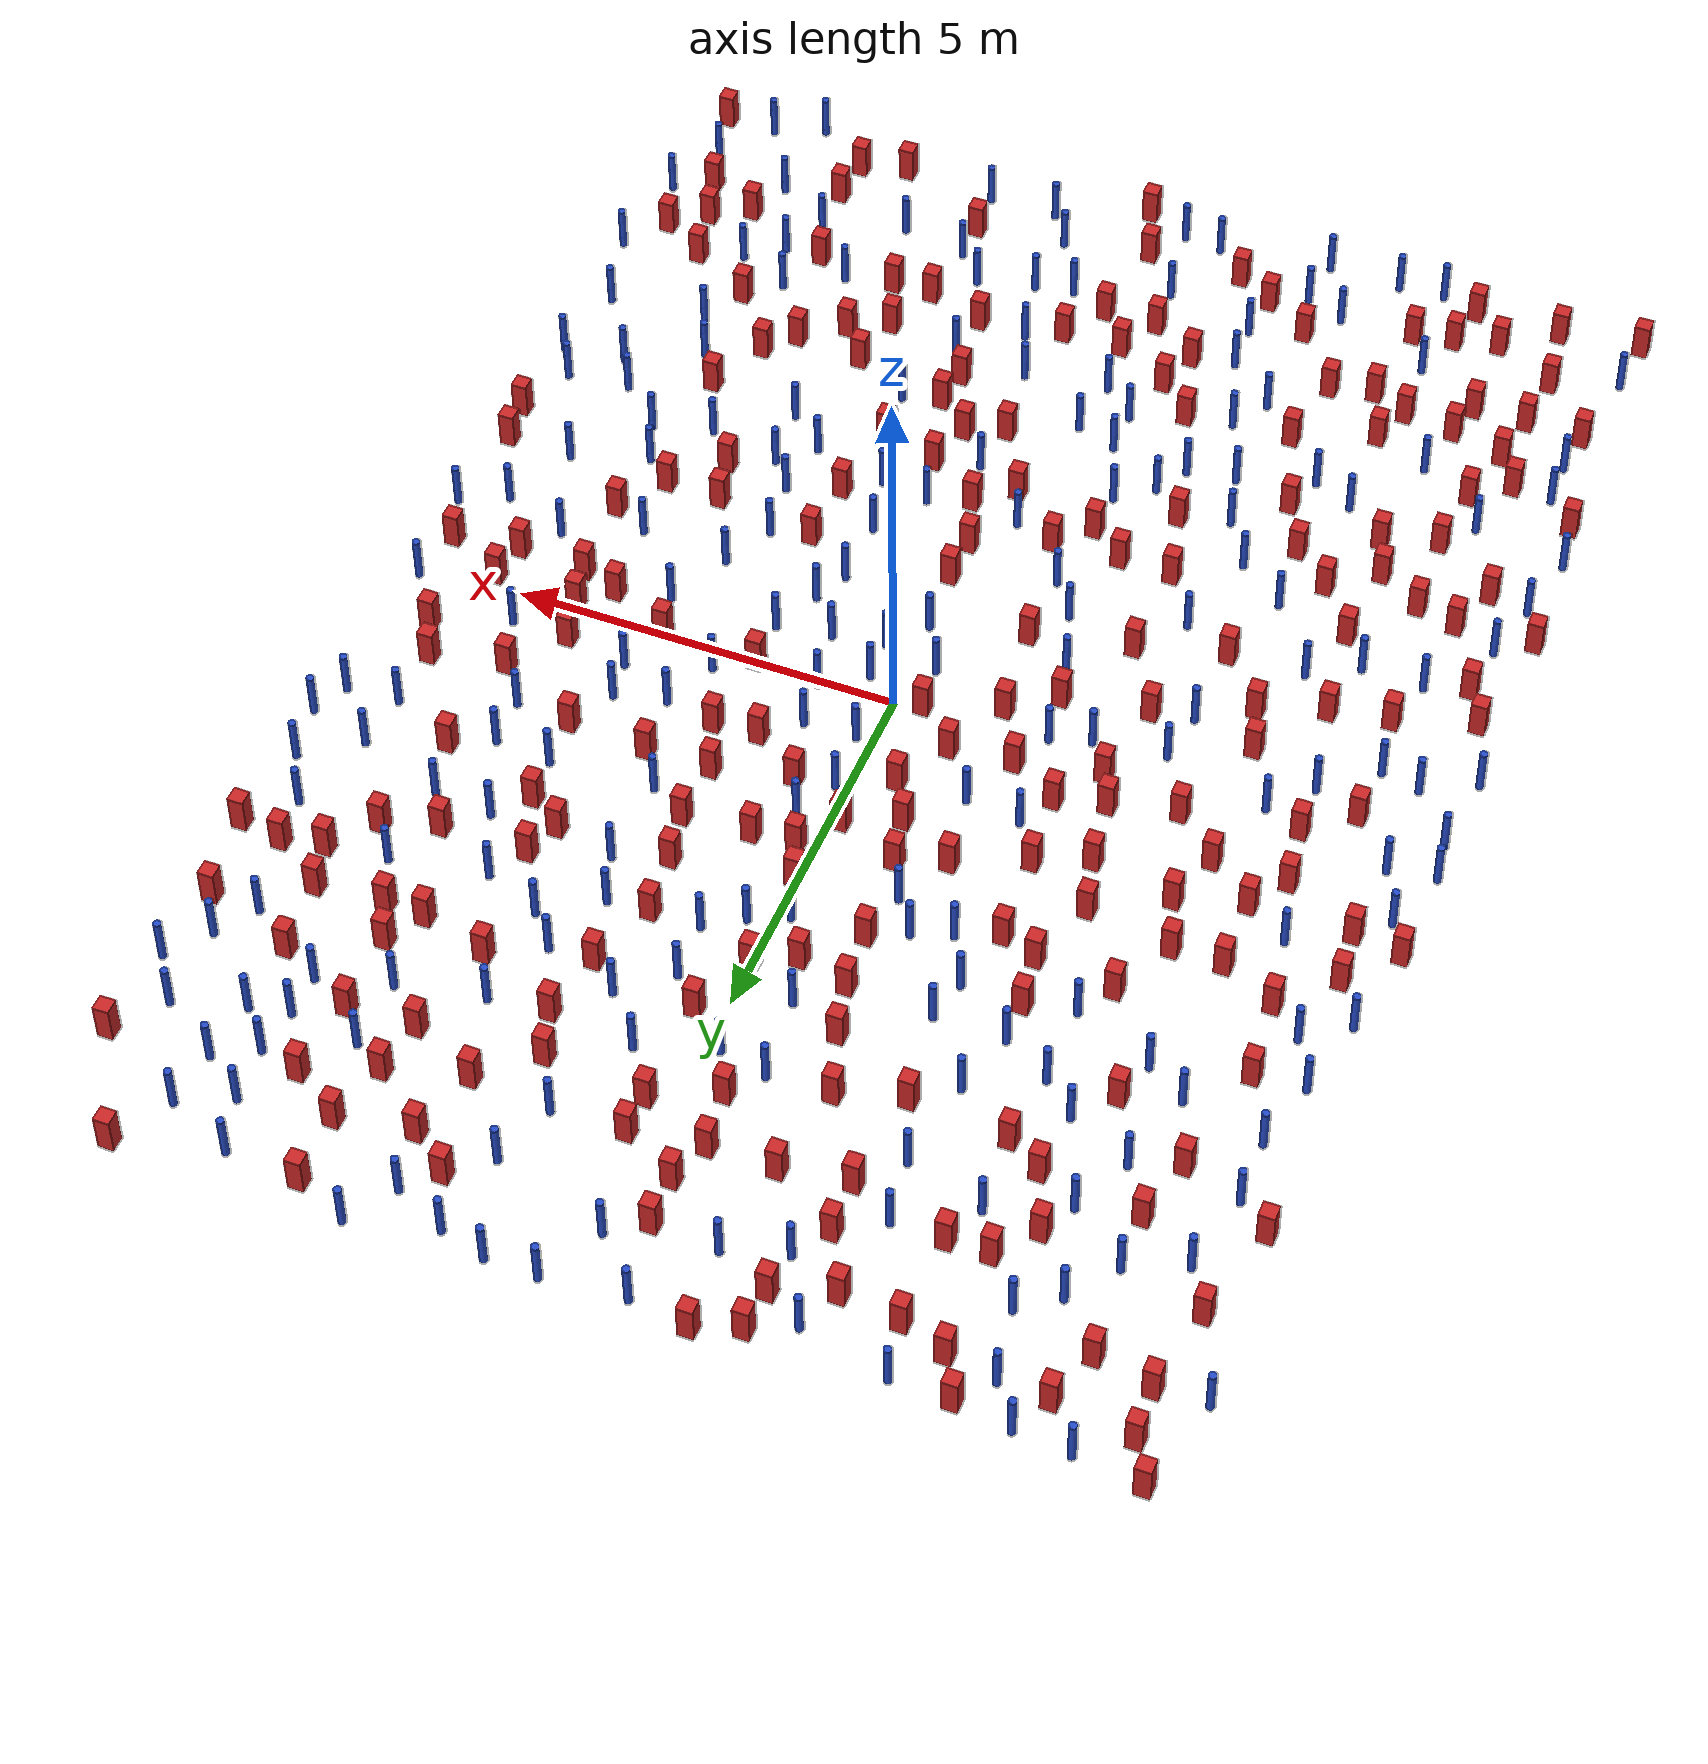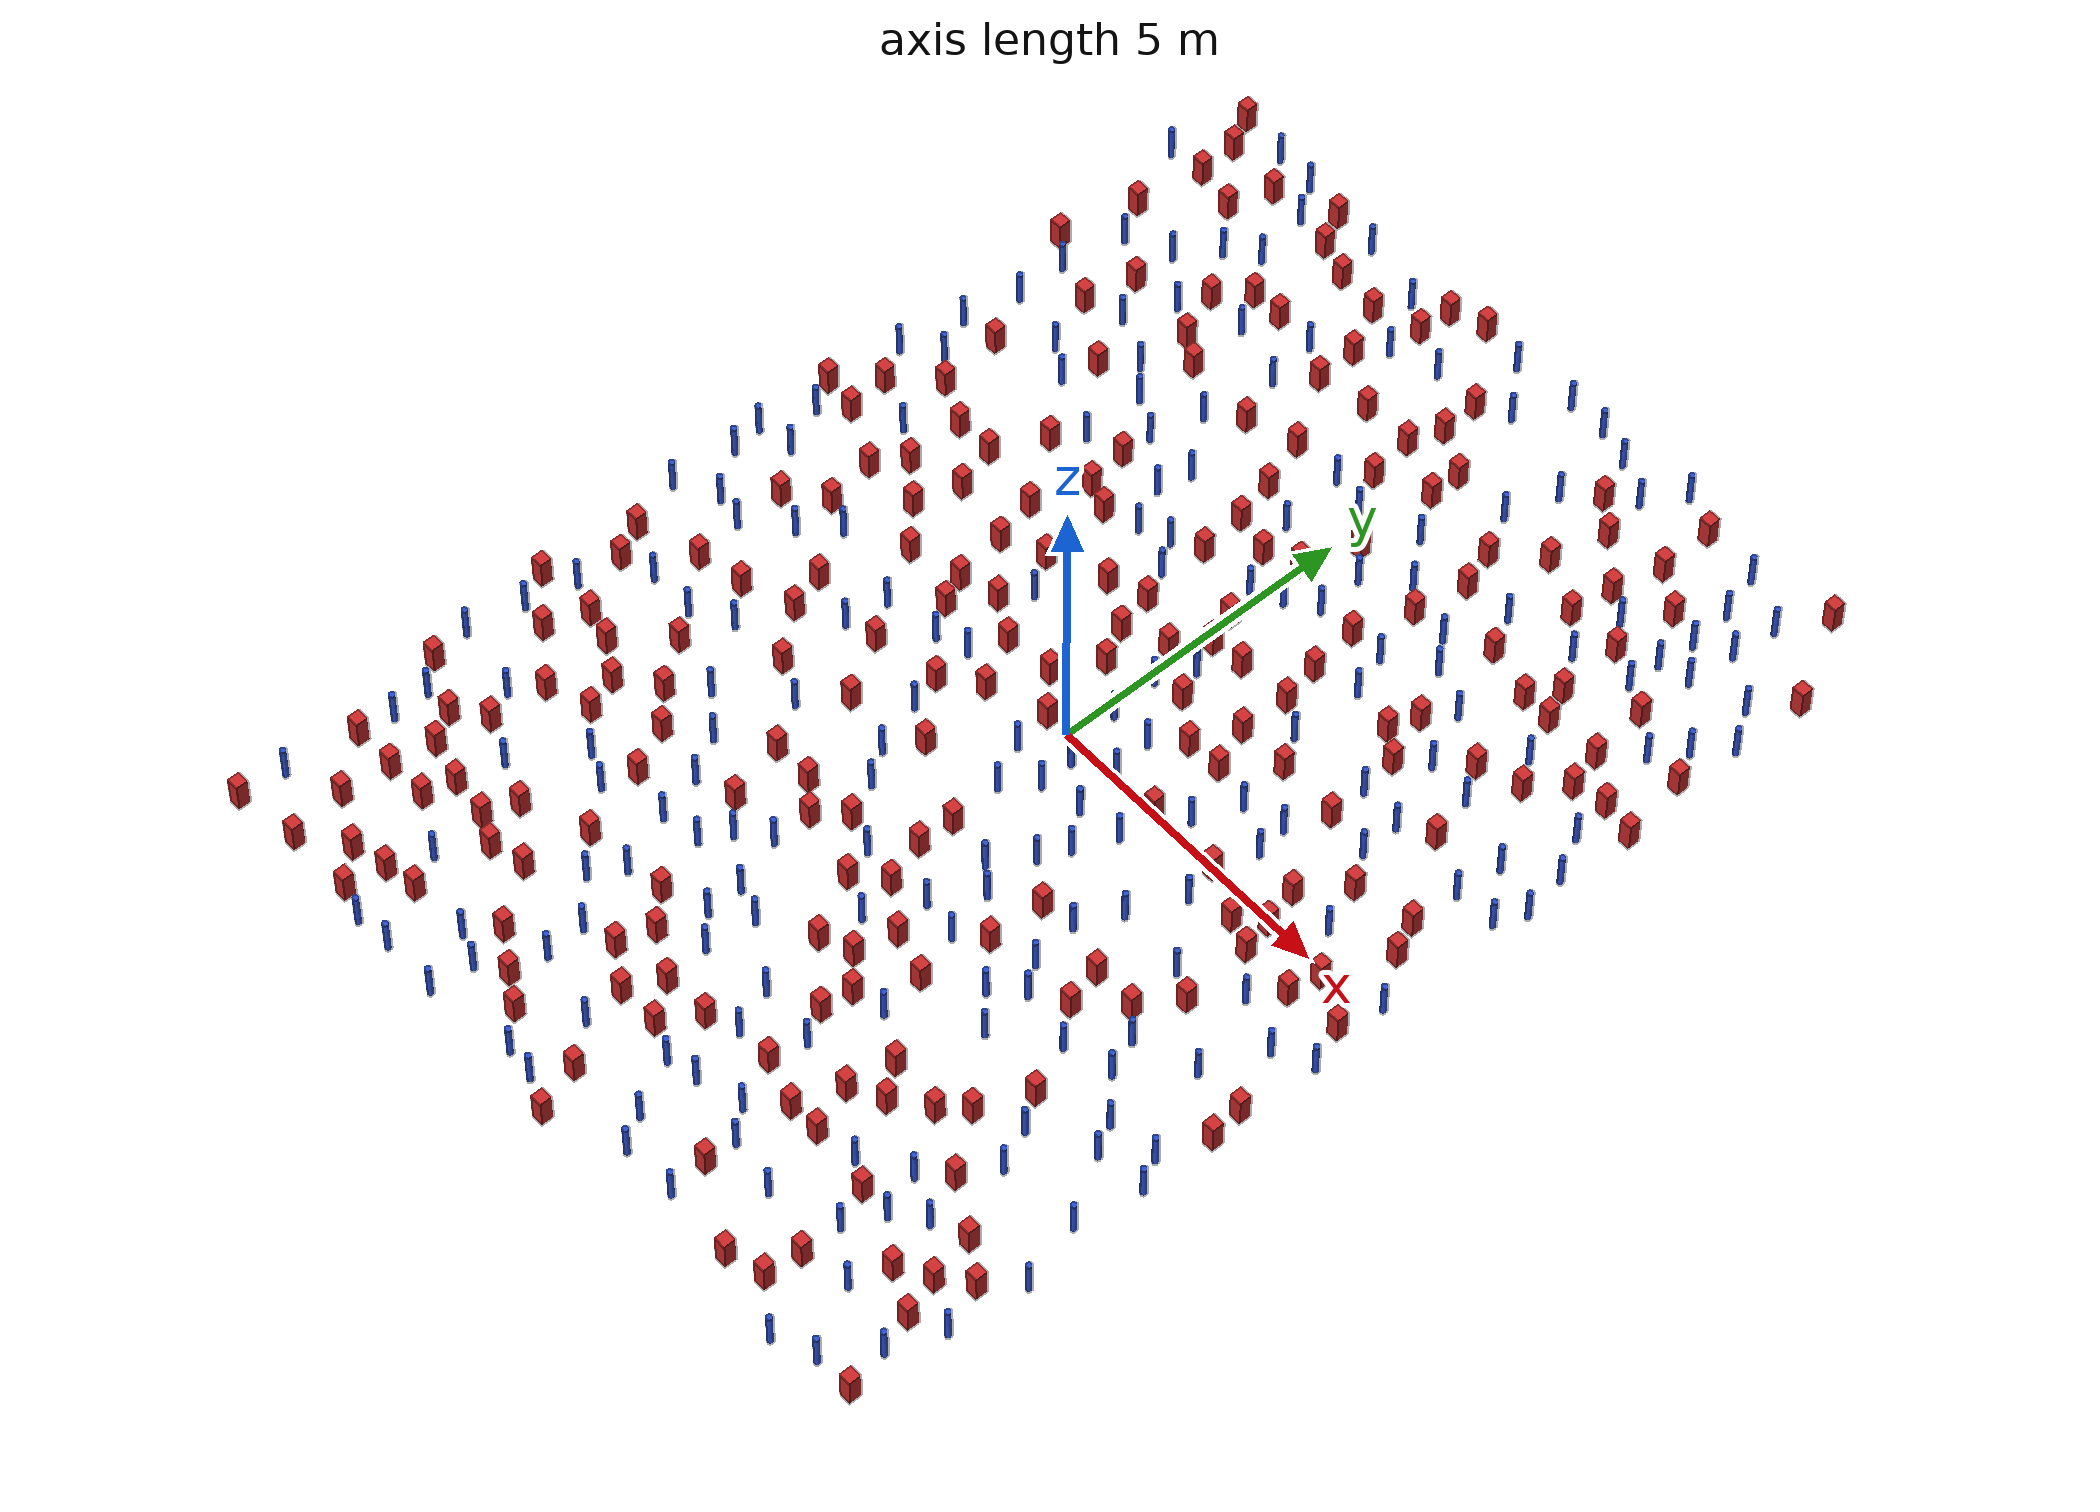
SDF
<sdf version="1.6">
  <model name="dense_72"><model name="pole_obstacle0">
  <static>true</static>
  <pose frame="">-5.60489354962 1.792876674 2.88873142074e-08 -9.90536689445e-09 4.60219948999e-07 -1.20965994956e-07</pose>
  <link name="link">
  <pose frame="">0 0 0.3 0 -0 0</pose>
    <inertial>
      <mass>1</mass>
      <inertia>
        <ixx>0.145833</ixx>
        <ixy>0</ixy>
        <ixz>0</ixz>
        <iyy>0.145833</iyy>
        <iyz>0</iyz>
        <izz>0.125</izz>
      </inertia>
    </inertial>
    <collision name="collision">
      <geometry>
        <cylinder>
          <radius>0.05</radius>
          <length>.6</length>
        </cylinder>
      </geometry>
      <max_contacts>10</max_contacts>
      <surface>
        <contact>
          <ode/>
        </contact>
        <bounce/>
        <friction>
          <torsional>
            <ode/>
          </torsional>
          <ode/>
        </friction>
      </surface>
    </collision>
    <visual name="visual">
      <geometry>
        <cylinder>
          <radius>0.05</radius>
          <length>.6</length>
        </cylinder>
      </geometry>
      <material>
        <script>
          <name>Gazebo/Blue</name>
          <uri>file://media/materials/scripts/gazebo.material</uri>
        </script>
      </material>
    </visual>
    <self_collide>0</self_collide>
    <kinematic>0</kinematic>
  </link>
</model>
<model name="pole_obstacle1">
  <static>true</static>
  <pose frame="">4.37582242248 9.04554621541 2.88873142074e-08 -9.9053668967e-09 4.60219948993e-07 -1.20965994957e-07</pose>
  <link name="link">
  <pose frame="">0 0 0.3 0 -0 0</pose>
    <inertial>
      <mass>1</mass>
      <inertia>
        <ixx>0.145833</ixx>
        <ixy>0</ixy>
        <ixz>0</ixz>
        <iyy>0.145833</iyy>
        <iyz>0</iyz>
        <izz>0.125</izz>
      </inertia>
    </inertial>
    <collision name="collision">
      <geometry>
        <cylinder>
          <radius>0.05</radius>
          <length>.6</length>
        </cylinder>
      </geometry>
      <max_contacts>10</max_contacts>
      <surface>
        <contact>
          <ode/>
        </contact>
        <bounce/>
        <friction>
          <torsional>
            <ode/>
          </torsional>
          <ode/>
        </friction>
      </surface>
    </collision>
    <visual name="visual">
      <geometry>
        <cylinder>
          <radius>0.05</radius>
          <length>.6</length>
        </cylinder>
      </geometry>
      <material>
        <script>
          <name>Gazebo/Blue</name>
          <uri>file://media/materials/scripts/gazebo.material</uri>
        </script>
      </material>
    </visual>
    <self_collide>0</self_collide>
    <kinematic>0</kinematic>
  </link>
</model>
<model name="square_post_obstacle0">
  <static>true</static>
  <pose frame="">3.33551158871 -2.38753182375 8.22691968438e-08 7.2212513382e-06 -7.54495500217e-07 2.29674213826e-05</pose>
  <link name="link">
    <pose frame="">0 0 0.25 0 -0 0</pose>
    <inertial>
      <mass>100</mass>
      <inertia>
        <ixx>0.166667</ixx>
        <ixy>0</ixy>
        <ixz>0</ixz>
        <iyy>0.166667</iyy>
        <iyz>0</iyz>
        <izz>0.166667</izz>
      </inertia>
    </inertial>
    <collision name="collision">
      <geometry>
        <box>
          <size>.2 .2 .5</size>
        </box>
      </geometry>
      <max_contacts>10</max_contacts>
      <surface>
        <contact>
          <ode/>
        </contact>
        <bounce/>
        <friction>
          <torsional>
            <ode/>
          </torsional>
          <ode/>
        </friction>
      </surface>
    </collision>
    <visual name="visual">
      <geometry>
        <box>
          <size>.2 .2 .5</size>
        </box>
      </geometry>
      <material>
        <script>
          <name>Gazebo/Red</name>
          <uri>file://media/materials/scripts/gazebo.material</uri>
        </script>
      </material>
    </visual>
    <self_collide>0</self_collide>
    <kinematic>0</kinematic>
  </link>
</model>
<model name="square_post_obstacle1">
  <static>true</static>
  <pose frame="">6.35539613358 -2.98623689507 8.22691968438e-08 7.2212513382e-06 -7.54495500217e-07 2.29674213826e-05</pose>
  <link name="link">
    <pose frame="">0 0 0.25 0 -0 0</pose>
    <inertial>
      <mass>100</mass>
      <inertia>
        <ixx>0.166667</ixx>
        <ixy>0</ixy>
        <ixz>0</ixz>
        <iyy>0.166667</iyy>
        <iyz>0</iyz>
        <izz>0.166667</izz>
      </inertia>
    </inertial>
    <collision name="collision">
      <geometry>
        <box>
          <size>.2 .2 .5</size>
        </box>
      </geometry>
      <max_contacts>10</max_contacts>
      <surface>
        <contact>
          <ode/>
        </contact>
        <bounce/>
        <friction>
          <torsional>
            <ode/>
          </torsional>
          <ode/>
        </friction>
      </surface>
    </collision>
    <visual name="visual">
      <geometry>
        <box>
          <size>.2 .2 .5</size>
        </box>
      </geometry>
      <material>
        <script>
          <name>Gazebo/Red</name>
          <uri>file://media/materials/scripts/gazebo.material</uri>
        </script>
      </material>
    </visual>
    <self_collide>0</self_collide>
    <kinematic>0</kinematic>
  </link>
</model>
<model name="pole_obstacle2">
  <static>true</static>
  <pose frame="">6.14830196329 -5.28207078286 2.88873142074e-08 -9.90536690842e-09 4.60219948965e-07 -1.20965994976e-07</pose>
  <link name="link">
  <pose frame="">0 0 0.3 0 -0 0</pose>
    <inertial>
      <mass>1</mass>
      <inertia>
        <ixx>0.145833</ixx>
        <ixy>0</ixy>
        <ixz>0</ixz>
        <iyy>0.145833</iyy>
        <iyz>0</iyz>
        <izz>0.125</izz>
      </inertia>
    </inertial>
    <collision name="collision">
      <geometry>
        <cylinder>
          <radius>0.05</radius>
          <length>.6</length>
        </cylinder>
      </geometry>
      <max_contacts>10</max_contacts>
      <surface>
        <contact>
          <ode/>
        </contact>
        <bounce/>
        <friction>
          <torsional>
            <ode/>
          </torsional>
          <ode/>
        </friction>
      </surface>
    </collision>
    <visual name="visual">
      <geometry>
        <cylinder>
          <radius>0.05</radius>
          <length>.6</length>
        </cylinder>
      </geometry>
      <material>
        <script>
          <name>Gazebo/Blue</name>
          <uri>file://media/materials/scripts/gazebo.material</uri>
        </script>
      </material>
    </visual>
    <self_collide>0</self_collide>
    <kinematic>0</kinematic>
  </link>
</model>
<model name="pole_obstacle3">
  <static>true</static>
  <pose frame="">-0.965626701555 -9.16200165954 2.88873142074e-08 -9.90536690773e-09 4.60219948967e-07 -1.20965994976e-07</pose>
  <link name="link">
  <pose frame="">0 0 0.3 0 -0 0</pose>
    <inertial>
      <mass>1</mass>
      <inertia>
        <ixx>0.145833</ixx>
        <ixy>0</ixy>
        <ixz>0</ixz>
        <iyy>0.145833</iyy>
        <iyz>0</iyz>
        <izz>0.125</izz>
      </inertia>
    </inertial>
    <collision name="collision">
      <geometry>
        <cylinder>
          <radius>0.05</radius>
          <length>.6</length>
        </cylinder>
      </geometry>
      <max_contacts>10</max_contacts>
      <surface>
        <contact>
          <ode/>
        </contact>
        <bounce/>
        <friction>
          <torsional>
            <ode/>
          </torsional>
          <ode/>
        </friction>
      </surface>
    </collision>
    <visual name="visual">
      <geometry>
        <cylinder>
          <radius>0.05</radius>
          <length>.6</length>
        </cylinder>
      </geometry>
      <material>
        <script>
          <name>Gazebo/Blue</name>
          <uri>file://media/materials/scripts/gazebo.material</uri>
        </script>
      </material>
    </visual>
    <self_collide>0</self_collide>
    <kinematic>0</kinematic>
  </link>
</model>
<model name="pole_obstacle4">
  <static>true</static>
  <pose frame="">-0.408652184443 -5.30799203485 2.88873142074e-08 -9.90536689683e-09 4.60219948993e-07 -1.20965994957e-07</pose>
  <link name="link">
  <pose frame="">0 0 0.3 0 -0 0</pose>
    <inertial>
      <mass>1</mass>
      <inertia>
        <ixx>0.145833</ixx>
        <ixy>0</ixy>
        <ixz>0</ixz>
        <iyy>0.145833</iyy>
        <iyz>0</iyz>
        <izz>0.125</izz>
      </inertia>
    </inertial>
    <collision name="collision">
      <geometry>
        <cylinder>
          <radius>0.05</radius>
          <length>.6</length>
        </cylinder>
      </geometry>
      <max_contacts>10</max_contacts>
      <surface>
        <contact>
          <ode/>
        </contact>
        <bounce/>
        <friction>
          <torsional>
            <ode/>
          </torsional>
          <ode/>
        </friction>
      </surface>
    </collision>
    <visual name="visual">
      <geometry>
        <cylinder>
          <radius>0.05</radius>
          <length>.6</length>
        </cylinder>
      </geometry>
      <material>
        <script>
          <name>Gazebo/Blue</name>
          <uri>file://media/materials/scripts/gazebo.material</uri>
        </script>
      </material>
    </visual>
    <self_collide>0</self_collide>
    <kinematic>0</kinematic>
  </link>
</model>
<model name="pole_obstacle5">
  <static>true</static>
  <pose frame="">-2.88354378176 -8.45582240815 2.88873142074e-08 -9.90536692318e-09 4.6021994893e-07 -1.20965994988e-07</pose>
  <link name="link">
  <pose frame="">0 0 0.3 0 -0 0</pose>
    <inertial>
      <mass>1</mass>
      <inertia>
        <ixx>0.145833</ixx>
        <ixy>0</ixy>
        <ixz>0</ixz>
        <iyy>0.145833</iyy>
        <iyz>0</iyz>
        <izz>0.125</izz>
      </inertia>
    </inertial>
    <collision name="collision">
      <geometry>
        <cylinder>
          <radius>0.05</radius>
          <length>.6</length>
        </cylinder>
      </geometry>
      <max_contacts>10</max_contacts>
      <surface>
        <contact>
          <ode/>
        </contact>
        <bounce/>
        <friction>
          <torsional>
            <ode/>
          </torsional>
          <ode/>
        </friction>
      </surface>
    </collision>
    <visual name="visual">
      <geometry>
        <cylinder>
          <radius>0.05</radius>
          <length>.6</length>
        </cylinder>
      </geometry>
      <material>
        <script>
          <name>Gazebo/Blue</name>
          <uri>file://media/materials/scripts/gazebo.material</uri>
        </script>
      </material>
    </visual>
    <self_collide>0</self_collide>
    <kinematic>0</kinematic>
  </link>
</model>
<model name="pole_obstacle6">
  <static>true</static>
  <pose frame="">0.951202149608 -2.32949687447 2.88873142074e-08 -9.90536689802e-09 4.6021994899e-07 -1.2096599496e-07</pose>
  <link name="link">
  <pose frame="">0 0 0.3 0 -0 0</pose>
    <inertial>
      <mass>1</mass>
      <inertia>
        <ixx>0.145833</ixx>
        <ixy>0</ixy>
        <ixz>0</ixz>
        <iyy>0.145833</iyy>
        <iyz>0</iyz>
        <izz>0.125</izz>
      </inertia>
    </inertial>
    <collision name="collision">
      <geometry>
        <cylinder>
          <radius>0.05</radius>
          <length>.6</length>
        </cylinder>
      </geometry>
      <max_contacts>10</max_contacts>
      <surface>
        <contact>
          <ode/>
        </contact>
        <bounce/>
        <friction>
          <torsional>
            <ode/>
          </torsional>
          <ode/>
        </friction>
      </surface>
    </collision>
    <visual name="visual">
      <geometry>
        <cylinder>
          <radius>0.05</radius>
          <length>.6</length>
        </cylinder>
      </geometry>
      <material>
        <script>
          <name>Gazebo/Blue</name>
          <uri>file://media/materials/scripts/gazebo.material</uri>
        </script>
      </material>
    </visual>
    <self_collide>0</self_collide>
    <kinematic>0</kinematic>
  </link>
</model>
<model name="square_post_obstacle2">
  <static>true</static>
  <pose frame="">0.2190282874 2.5391222892 8.22691968438e-08 7.2212513382e-06 -7.54495500217e-07 2.29674213826e-05</pose>
  <link name="link">
    <pose frame="">0 0 0.25 0 -0 0</pose>
    <inertial>
      <mass>100</mass>
      <inertia>
        <ixx>0.166667</ixx>
        <ixy>0</ixy>
        <ixz>0</ixz>
        <iyy>0.166667</iyy>
        <iyz>0</iyz>
        <izz>0.166667</izz>
      </inertia>
    </inertial>
    <collision name="collision">
      <geometry>
        <box>
          <size>.2 .2 .5</size>
        </box>
      </geometry>
      <max_contacts>10</max_contacts>
      <surface>
        <contact>
          <ode/>
        </contact>
        <bounce/>
        <friction>
          <torsional>
            <ode/>
          </torsional>
          <ode/>
        </friction>
      </surface>
    </collision>
    <visual name="visual">
      <geometry>
        <box>
          <size>.2 .2 .5</size>
        </box>
      </geometry>
      <material>
        <script>
          <name>Gazebo/Red</name>
          <uri>file://media/materials/scripts/gazebo.material</uri>
        </script>
      </material>
    </visual>
    <self_collide>0</self_collide>
    <kinematic>0</kinematic>
  </link>
</model>
<model name="square_post_obstacle3">
  <static>true</static>
  <pose frame="">0.921883301108 -4.67364424188 8.22691968438e-08 7.22125133819e-06 -7.54495500217e-07 2.29674213826e-05</pose>
  <link name="link">
    <pose frame="">0 0 0.25 0 -0 0</pose>
    <inertial>
      <mass>100</mass>
      <inertia>
        <ixx>0.166667</ixx>
        <ixy>0</ixy>
        <ixz>0</ixz>
        <iyy>0.166667</iyy>
        <iyz>0</iyz>
        <izz>0.166667</izz>
      </inertia>
    </inertial>
    <collision name="collision">
      <geometry>
        <box>
          <size>.2 .2 .5</size>
        </box>
      </geometry>
      <max_contacts>10</max_contacts>
      <surface>
        <contact>
          <ode/>
        </contact>
        <bounce/>
        <friction>
          <torsional>
            <ode/>
          </torsional>
          <ode/>
        </friction>
      </surface>
    </collision>
    <visual name="visual">
      <geometry>
        <box>
          <size>.2 .2 .5</size>
        </box>
      </geometry>
      <material>
        <script>
          <name>Gazebo/Red</name>
          <uri>file://media/materials/scripts/gazebo.material</uri>
        </script>
      </material>
    </visual>
    <self_collide>0</self_collide>
    <kinematic>0</kinematic>
  </link>
</model>
<model name="square_post_obstacle4">
  <static>true</static>
  <pose frame="">-0.353924351522 -0.0484012104252 8.22691968438e-08 7.2212513382e-06 -7.54495500217e-07 2.29674213826e-05</pose>
  <link name="link">
    <pose frame="">0 0 0.25 0 -0 0</pose>
    <inertial>
      <mass>100</mass>
      <inertia>
        <ixx>0.166667</ixx>
        <ixy>0</ixy>
        <ixz>0</ixz>
        <iyy>0.166667</iyy>
        <iyz>0</iyz>
        <izz>0.166667</izz>
      </inertia>
    </inertial>
    <collision name="collision">
      <geometry>
        <box>
          <size>.2 .2 .5</size>
        </box>
      </geometry>
      <max_contacts>10</max_contacts>
      <surface>
        <contact>
          <ode/>
        </contact>
        <bounce/>
        <friction>
          <torsional>
            <ode/>
          </torsional>
          <ode/>
        </friction>
      </surface>
    </collision>
    <visual name="visual">
      <geometry>
        <box>
          <size>.2 .2 .5</size>
        </box>
      </geometry>
      <material>
        <script>
          <name>Gazebo/Red</name>
          <uri>file://media/materials/scripts/gazebo.material</uri>
        </script>
      </material>
    </visual>
    <self_collide>0</self_collide>
    <kinematic>0</kinematic>
  </link>
</model>
<model name="pole_obstacle7">
  <static>true</static>
  <pose frame="">-5.84208865774 -1.11125612981 2.88873142074e-08 -9.90536689445e-09 4.60219948999e-07 -1.20965994956e-07</pose>
  <link name="link">
  <pose frame="">0 0 0.3 0 -0 0</pose>
    <inertial>
      <mass>1</mass>
      <inertia>
        <ixx>0.145833</ixx>
        <ixy>0</ixy>
        <ixz>0</ixz>
        <iyy>0.145833</iyy>
        <iyz>0</iyz>
        <izz>0.125</izz>
      </inertia>
    </inertial>
    <collision name="collision">
      <geometry>
        <cylinder>
          <radius>0.05</radius>
          <length>.6</length>
        </cylinder>
      </geometry>
      <max_contacts>10</max_contacts>
      <surface>
        <contact>
          <ode/>
        </contact>
        <bounce/>
        <friction>
          <torsional>
            <ode/>
          </torsional>
          <ode/>
        </friction>
      </surface>
    </collision>
    <visual name="visual">
      <geometry>
        <cylinder>
          <radius>0.05</radius>
          <length>.6</length>
        </cylinder>
      </geometry>
      <material>
        <script>
          <name>Gazebo/Blue</name>
          <uri>file://media/materials/scripts/gazebo.material</uri>
        </script>
      </material>
    </visual>
    <self_collide>0</self_collide>
    <kinematic>0</kinematic>
  </link>
</model>
<model name="pole_obstacle8">
  <static>true</static>
  <pose frame="">-6.21378915268 3.09624534109 2.88873142074e-08 -9.90536690245e-09 4.6021994898e-07 -1.20965994966e-07</pose>
  <link name="link">
  <pose frame="">0 0 0.3 0 -0 0</pose>
    <inertial>
      <mass>1</mass>
      <inertia>
        <ixx>0.145833</ixx>
        <ixy>0</ixy>
        <ixz>0</ixz>
        <iyy>0.145833</iyy>
        <iyz>0</iyz>
        <izz>0.125</izz>
      </inertia>
    </inertial>
    <collision name="collision">
      <geometry>
        <cylinder>
          <radius>0.05</radius>
          <length>.6</length>
        </cylinder>
      </geometry>
      <max_contacts>10</max_contacts>
      <surface>
        <contact>
          <ode/>
        </contact>
        <bounce/>
        <friction>
          <torsional>
            <ode/>
          </torsional>
          <ode/>
        </friction>
      </surface>
    </collision>
    <visual name="visual">
      <geometry>
        <cylinder>
          <radius>0.05</radius>
          <length>.6</length>
        </cylinder>
      </geometry>
      <material>
        <script>
          <name>Gazebo/Blue</name>
          <uri>file://media/materials/scripts/gazebo.material</uri>
        </script>
      </material>
    </visual>
    <self_collide>0</self_collide>
    <kinematic>0</kinematic>
  </link>
</model>
<model name="square_post_obstacle5">
  <static>true</static>
  <pose frame="">-3.48958603233 8.40357161322 8.22691968438e-08 7.22125133819e-06 -7.54495500217e-07 2.29674213826e-05</pose>
  <link name="link">
    <pose frame="">0 0 0.25 0 -0 0</pose>
    <inertial>
      <mass>100</mass>
      <inertia>
        <ixx>0.166667</ixx>
        <ixy>0</ixy>
        <ixz>0</ixz>
        <iyy>0.166667</iyy>
        <iyz>0</iyz>
        <izz>0.166667</izz>
      </inertia>
    </inertial>
    <collision name="collision">
      <geometry>
        <box>
          <size>.2 .2 .5</size>
        </box>
      </geometry>
      <max_contacts>10</max_contacts>
      <surface>
        <contact>
          <ode/>
        </contact>
        <bounce/>
        <friction>
          <torsional>
            <ode/>
          </torsional>
          <ode/>
        </friction>
      </surface>
    </collision>
    <visual name="visual">
      <geometry>
        <box>
          <size>.2 .2 .5</size>
        </box>
      </geometry>
      <material>
        <script>
          <name>Gazebo/Red</name>
          <uri>file://media/materials/scripts/gazebo.material</uri>
        </script>
      </material>
    </visual>
    <self_collide>0</self_collide>
    <kinematic>0</kinematic>
  </link>
</model>
<model name="square_post_obstacle6">
  <static>true</static>
  <pose frame="">-4.08551732455 8.60938443152 8.22691968438e-08 7.22125133819e-06 -7.54495500217e-07 2.29674213826e-05</pose>
  <link name="link">
    <pose frame="">0 0 0.25 0 -0 0</pose>
    <inertial>
      <mass>100</mass>
      <inertia>
        <ixx>0.166667</ixx>
        <ixy>0</ixy>
        <ixz>0</ixz>
        <iyy>0.166667</iyy>
        <iyz>0</iyz>
        <izz>0.166667</izz>
      </inertia>
    </inertial>
    <collision name="collision">
      <geometry>
        <box>
          <size>.2 .2 .5</size>
        </box>
      </geometry>
      <max_contacts>10</max_contacts>
      <surface>
        <contact>
          <ode/>
        </contact>
        <bounce/>
        <friction>
          <torsional>
            <ode/>
          </torsional>
          <ode/>
        </friction>
      </surface>
    </collision>
    <visual name="visual">
      <geometry>
        <box>
          <size>.2 .2 .5</size>
        </box>
      </geometry>
      <material>
        <script>
          <name>Gazebo/Red</name>
          <uri>file://media/materials/scripts/gazebo.material</uri>
        </script>
      </material>
    </visual>
    <self_collide>0</self_collide>
    <kinematic>0</kinematic>
  </link>
</model>
<model name="square_post_obstacle7">
  <static>true</static>
  <pose frame="">2.27140523398 7.10940884494 8.22691968438e-08 7.2212513382e-06 -7.54495500217e-07 2.29674213826e-05</pose>
  <link name="link">
    <pose frame="">0 0 0.25 0 -0 0</pose>
    <inertial>
      <mass>100</mass>
      <inertia>
        <ixx>0.166667</ixx>
        <ixy>0</ixy>
        <ixz>0</ixz>
        <iyy>0.166667</iyy>
        <iyz>0</iyz>
        <izz>0.166667</izz>
      </inertia>
    </inertial>
    <collision name="collision">
      <geometry>
        <box>
          <size>.2 .2 .5</size>
        </box>
      </geometry>
      <max_contacts>10</max_contacts>
      <surface>
        <contact>
          <ode/>
        </contact>
        <bounce/>
        <friction>
          <torsional>
            <ode/>
          </torsional>
          <ode/>
        </friction>
      </surface>
    </collision>
    <visual name="visual">
      <geometry>
        <box>
          <size>.2 .2 .5</size>
        </box>
      </geometry>
      <material>
        <script>
          <name>Gazebo/Red</name>
          <uri>file://media/materials/scripts/gazebo.material</uri>
        </script>
      </material>
    </visual>
    <self_collide>0</self_collide>
    <kinematic>0</kinematic>
  </link>
</model>
<model name="pole_obstacle9">
  <static>true</static>
  <pose frame="">1.67303859116 9.12570394465 2.88873142074e-08 -9.90536690474e-09 4.60219948974e-07 -1.2096599497e-07</pose>
  <link name="link">
  <pose frame="">0 0 0.3 0 -0 0</pose>
    <inertial>
      <mass>1</mass>
      <inertia>
        <ixx>0.145833</ixx>
        <ixy>0</ixy>
        <ixz>0</ixz>
        <iyy>0.145833</iyy>
        <iyz>0</iyz>
        <izz>0.125</izz>
      </inertia>
    </inertial>
    <collision name="collision">
      <geometry>
        <cylinder>
          <radius>0.05</radius>
          <length>.6</length>
        </cylinder>
      </geometry>
      <max_contacts>10</max_contacts>
      <surface>
        <contact>
          <ode/>
        </contact>
        <bounce/>
        <friction>
          <torsional>
            <ode/>
          </torsional>
          <ode/>
        </friction>
      </surface>
    </collision>
    <visual name="visual">
      <geometry>
        <cylinder>
          <radius>0.05</radius>
          <length>.6</length>
        </cylinder>
      </geometry>
      <material>
        <script>
          <name>Gazebo/Blue</name>
          <uri>file://media/materials/scripts/gazebo.material</uri>
        </script>
      </material>
    </visual>
    <self_collide>0</self_collide>
    <kinematic>0</kinematic>
  </link>
</model>
<model name="pole_obstacle10">
  <static>true</static>
  <pose frame="">-1.11642473633 -2.62495609921 2.88873142074e-08 -9.90536689791e-09 4.6021994899e-07 -1.20965994959e-07</pose>
  <link name="link">
  <pose frame="">0 0 0.3 0 -0 0</pose>
    <inertial>
      <mass>1</mass>
      <inertia>
        <ixx>0.145833</ixx>
        <ixy>0</ixy>
        <ixz>0</ixz>
        <iyy>0.145833</iyy>
        <iyz>0</iyz>
        <izz>0.125</izz>
      </inertia>
    </inertial>
    <collision name="collision">
      <geometry>
        <cylinder>
          <radius>0.05</radius>
          <length>.6</length>
        </cylinder>
      </geometry>
      <max_contacts>10</max_contacts>
      <surface>
        <contact>
          <ode/>
        </contact>
        <bounce/>
        <friction>
          <torsional>
            <ode/>
          </torsional>
          <ode/>
        </friction>
      </surface>
    </collision>
    <visual name="visual">
      <geometry>
        <cylinder>
          <radius>0.05</radius>
          <length>.6</length>
        </cylinder>
      </geometry>
      <material>
        <script>
          <name>Gazebo/Blue</name>
          <uri>file://media/materials/scripts/gazebo.material</uri>
        </script>
      </material>
    </visual>
    <self_collide>0</self_collide>
    <kinematic>0</kinematic>
  </link>
</model>
<model name="pole_obstacle11">
  <static>true</static>
  <pose frame="">-5.09082674828 9.23493699206 2.88873142074e-08 -9.9053668967e-09 4.60219948993e-07 -1.20965994957e-07</pose>
  <link name="link">
  <pose frame="">0 0 0.3 0 -0 0</pose>
    <inertial>
      <mass>1</mass>
      <inertia>
        <ixx>0.145833</ixx>
        <ixy>0</ixy>
        <ixz>0</ixz>
        <iyy>0.145833</iyy>
        <iyz>0</iyz>
        <izz>0.125</izz>
      </inertia>
    </inertial>
    <collision name="collision">
      <geometry>
        <cylinder>
          <radius>0.05</radius>
          <length>.6</length>
        </cylinder>
      </geometry>
      <max_contacts>10</max_contacts>
      <surface>
        <contact>
          <ode/>
        </contact>
        <bounce/>
        <friction>
          <torsional>
            <ode/>
          </torsional>
          <ode/>
        </friction>
      </surface>
    </collision>
    <visual name="visual">
      <geometry>
        <cylinder>
          <radius>0.05</radius>
          <length>.6</length>
        </cylinder>
      </geometry>
      <material>
        <script>
          <name>Gazebo/Blue</name>
          <uri>file://media/materials/scripts/gazebo.material</uri>
        </script>
      </material>
    </visual>
    <self_collide>0</self_collide>
    <kinematic>0</kinematic>
  </link>
</model>
<model name="pole_obstacle12">
  <static>true</static>
  <pose frame="">-6.74844758762 2.70002124592 2.88873142074e-08 -9.90536690245e-09 4.6021994898e-07 -1.20965994966e-07</pose>
  <link name="link">
  <pose frame="">0 0 0.3 0 -0 0</pose>
    <inertial>
      <mass>1</mass>
      <inertia>
        <ixx>0.145833</ixx>
        <ixy>0</ixy>
        <ixz>0</ixz>
        <iyy>0.145833</iyy>
        <iyz>0</iyz>
        <izz>0.125</izz>
      </inertia>
    </inertial>
    <collision name="collision">
      <geometry>
        <cylinder>
          <radius>0.05</radius>
          <length>.6</length>
        </cylinder>
      </geometry>
      <max_contacts>10</max_contacts>
      <surface>
        <contact>
          <ode/>
        </contact>
        <bounce/>
        <friction>
          <torsional>
            <ode/>
          </torsional>
          <ode/>
        </friction>
      </surface>
    </collision>
    <visual name="visual">
      <geometry>
        <cylinder>
          <radius>0.05</radius>
          <length>.6</length>
        </cylinder>
      </geometry>
      <material>
        <script>
          <name>Gazebo/Blue</name>
          <uri>file://media/materials/scripts/gazebo.material</uri>
        </script>
      </material>
    </visual>
    <self_collide>0</self_collide>
    <kinematic>0</kinematic>
  </link>
</model>
<model name="square_post_obstacle8">
  <static>true</static>
  <pose frame="">-5.93874351744 -3.71497561347 8.22691968438e-08 7.2212513382e-06 -7.54495500217e-07 2.29674213826e-05</pose>
  <link name="link">
    <pose frame="">0 0 0.25 0 -0 0</pose>
    <inertial>
      <mass>100</mass>
      <inertia>
        <ixx>0.166667</ixx>
        <ixy>0</ixy>
        <ixz>0</ixz>
        <iyy>0.166667</iyy>
        <iyz>0</iyz>
        <izz>0.166667</izz>
      </inertia>
    </inertial>
    <collision name="collision">
      <geometry>
        <box>
          <size>.2 .2 .5</size>
        </box>
      </geometry>
      <max_contacts>10</max_contacts>
      <surface>
        <contact>
          <ode/>
        </contact>
        <bounce/>
        <friction>
          <torsional>
            <ode/>
          </torsional>
          <ode/>
        </friction>
      </surface>
    </collision>
    <visual name="visual">
      <geometry>
        <box>
          <size>.2 .2 .5</size>
        </box>
      </geometry>
      <material>
        <script>
          <name>Gazebo/Red</name>
          <uri>file://media/materials/scripts/gazebo.material</uri>
        </script>
      </material>
    </visual>
    <self_collide>0</self_collide>
    <kinematic>0</kinematic>
  </link>
</model>
<model name="square_post_obstacle9">
  <static>true</static>
  <pose frame="">-3.12864663933 1.49392424948 8.22691968438e-08 7.2212513382e-06 -7.54495500217e-07 2.29674213826e-05</pose>
  <link name="link">
    <pose frame="">0 0 0.25 0 -0 0</pose>
    <inertial>
      <mass>100</mass>
      <inertia>
        <ixx>0.166667</ixx>
        <ixy>0</ixy>
        <ixz>0</ixz>
        <iyy>0.166667</iyy>
        <iyz>0</iyz>
        <izz>0.166667</izz>
      </inertia>
    </inertial>
    <collision name="collision">
      <geometry>
        <box>
          <size>.2 .2 .5</size>
        </box>
      </geometry>
      <max_contacts>10</max_contacts>
      <surface>
        <contact>
          <ode/>
        </contact>
        <bounce/>
        <friction>
          <torsional>
            <ode/>
          </torsional>
          <ode/>
        </friction>
      </surface>
    </collision>
    <visual name="visual">
      <geometry>
        <box>
          <size>.2 .2 .5</size>
        </box>
      </geometry>
      <material>
        <script>
          <name>Gazebo/Red</name>
          <uri>file://media/materials/scripts/gazebo.material</uri>
        </script>
      </material>
    </visual>
    <self_collide>0</self_collide>
    <kinematic>0</kinematic>
  </link>
</model>
<model name="pole_obstacle13">
  <static>true</static>
  <pose frame="">-4.68693473672 6.25540807904 2.88873142074e-08 -9.90536690842e-09 4.60219948965e-07 -1.20965994976e-07</pose>
  <link name="link">
  <pose frame="">0 0 0.3 0 -0 0</pose>
    <inertial>
      <mass>1</mass>
      <inertia>
        <ixx>0.145833</ixx>
        <ixy>0</ixy>
        <ixz>0</ixz>
        <iyy>0.145833</iyy>
        <iyz>0</iyz>
        <izz>0.125</izz>
      </inertia>
    </inertial>
    <collision name="collision">
      <geometry>
        <cylinder>
          <radius>0.05</radius>
          <length>.6</length>
        </cylinder>
      </geometry>
      <max_contacts>10</max_contacts>
      <surface>
        <contact>
          <ode/>
        </contact>
        <bounce/>
        <friction>
          <torsional>
            <ode/>
          </torsional>
          <ode/>
        </friction>
      </surface>
    </collision>
    <visual name="visual">
      <geometry>
        <cylinder>
          <radius>0.05</radius>
          <length>.6</length>
        </cylinder>
      </geometry>
      <material>
        <script>
          <name>Gazebo/Blue</name>
          <uri>file://media/materials/scripts/gazebo.material</uri>
        </script>
      </material>
    </visual>
    <self_collide>0</self_collide>
    <kinematic>0</kinematic>
  </link>
</model>
<model name="square_post_obstacle10">
  <static>true</static>
  <pose frame="">-0.963395042714 2.35977024159 8.22691968438e-08 7.2212513382e-06 -7.54495500217e-07 2.29674213826e-05</pose>
  <link name="link">
    <pose frame="">0 0 0.25 0 -0 0</pose>
    <inertial>
      <mass>100</mass>
      <inertia>
        <ixx>0.166667</ixx>
        <ixy>0</ixy>
        <ixz>0</ixz>
        <iyy>0.166667</iyy>
        <iyz>0</iyz>
        <izz>0.166667</izz>
      </inertia>
    </inertial>
    <collision name="collision">
      <geometry>
        <box>
          <size>.2 .2 .5</size>
        </box>
      </geometry>
      <max_contacts>10</max_contacts>
      <surface>
        <contact>
          <ode/>
        </contact>
        <bounce/>
        <friction>
          <torsional>
            <ode/>
          </torsional>
          <ode/>
        </friction>
      </surface>
    </collision>
    <visual name="visual">
      <geometry>
        <box>
          <size>.2 .2 .5</size>
        </box>
      </geometry>
      <material>
        <script>
          <name>Gazebo/Red</name>
          <uri>file://media/materials/scripts/gazebo.material</uri>
        </script>
      </material>
    </visual>
    <self_collide>0</self_collide>
    <kinematic>0</kinematic>
  </link>
</model>
<model name="square_post_obstacle11">
  <static>true</static>
  <pose frame="">5.87914294403 4.74547711981 8.22691968438e-08 7.2212513382e-06 -7.54495500217e-07 2.29674213826e-05</pose>
  <link name="link">
    <pose frame="">0 0 0.25 0 -0 0</pose>
    <inertial>
      <mass>100</mass>
      <inertia>
        <ixx>0.166667</ixx>
        <ixy>0</ixy>
        <ixz>0</ixz>
        <iyy>0.166667</iyy>
        <iyz>0</iyz>
        <izz>0.166667</izz>
      </inertia>
    </inertial>
    <collision name="collision">
      <geometry>
        <box>
          <size>.2 .2 .5</size>
        </box>
      </geometry>
      <max_contacts>10</max_contacts>
      <surface>
        <contact>
          <ode/>
        </contact>
        <bounce/>
        <friction>
          <torsional>
            <ode/>
          </torsional>
          <ode/>
        </friction>
      </surface>
    </collision>
    <visual name="visual">
      <geometry>
        <box>
          <size>.2 .2 .5</size>
        </box>
      </geometry>
      <material>
        <script>
          <name>Gazebo/Red</name>
          <uri>file://media/materials/scripts/gazebo.material</uri>
        </script>
      </material>
    </visual>
    <self_collide>0</self_collide>
    <kinematic>0</kinematic>
  </link>
</model>
<model name="pole_obstacle14">
  <static>true</static>
  <pose frame="">0.768665898864 6.00691216805 2.88873142074e-08 -9.90536689661e-09 4.60219948993e-07 -1.20965994957e-07</pose>
  <link name="link">
  <pose frame="">0 0 0.3 0 -0 0</pose>
    <inertial>
      <mass>1</mass>
      <inertia>
        <ixx>0.145833</ixx>
        <ixy>0</ixy>
        <ixz>0</ixz>
        <iyy>0.145833</iyy>
        <iyz>0</iyz>
        <izz>0.125</izz>
      </inertia>
    </inertial>
    <collision name="collision">
      <geometry>
        <cylinder>
          <radius>0.05</radius>
          <length>.6</length>
        </cylinder>
      </geometry>
      <max_contacts>10</max_contacts>
      <surface>
        <contact>
          <ode/>
        </contact>
        <bounce/>
        <friction>
          <torsional>
            <ode/>
          </torsional>
          <ode/>
        </friction>
      </surface>
    </collision>
    <visual name="visual">
      <geometry>
        <cylinder>
          <radius>0.05</radius>
          <length>.6</length>
        </cylinder>
      </geometry>
      <material>
        <script>
          <name>Gazebo/Blue</name>
          <uri>file://media/materials/scripts/gazebo.material</uri>
        </script>
      </material>
    </visual>
    <self_collide>0</self_collide>
    <kinematic>0</kinematic>
  </link>
</model>
<model name="pole_obstacle15">
  <static>true</static>
  <pose frame="">-6.33041977614 4.64889348198 2.88873142074e-08 -9.90536690842e-09 4.60219948965e-07 -1.20965994976e-07</pose>
  <link name="link">
  <pose frame="">0 0 0.3 0 -0 0</pose>
    <inertial>
      <mass>1</mass>
      <inertia>
        <ixx>0.145833</ixx>
        <ixy>0</ixy>
        <ixz>0</ixz>
        <iyy>0.145833</iyy>
        <iyz>0</iyz>
        <izz>0.125</izz>
      </inertia>
    </inertial>
    <collision name="collision">
      <geometry>
        <cylinder>
          <radius>0.05</radius>
          <length>.6</length>
        </cylinder>
      </geometry>
      <max_contacts>10</max_contacts>
      <surface>
        <contact>
          <ode/>
        </contact>
        <bounce/>
        <friction>
          <torsional>
            <ode/>
          </torsional>
          <ode/>
        </friction>
      </surface>
    </collision>
    <visual name="visual">
      <geometry>
        <cylinder>
          <radius>0.05</radius>
          <length>.6</length>
        </cylinder>
      </geometry>
      <material>
        <script>
          <name>Gazebo/Blue</name>
          <uri>file://media/materials/scripts/gazebo.material</uri>
        </script>
      </material>
    </visual>
    <self_collide>0</self_collide>
    <kinematic>0</kinematic>
  </link>
</model>
<model name="square_post_obstacle12">
  <static>true</static>
  <pose frame="">-2.46374674068 1.77407036471 8.22691968438e-08 7.2212513382e-06 -7.54495500217e-07 2.29674213826e-05</pose>
  <link name="link">
    <pose frame="">0 0 0.25 0 -0 0</pose>
    <inertial>
      <mass>100</mass>
      <inertia>
        <ixx>0.166667</ixx>
        <ixy>0</ixy>
        <ixz>0</ixz>
        <iyy>0.166667</iyy>
        <iyz>0</iyz>
        <izz>0.166667</izz>
      </inertia>
    </inertial>
    <collision name="collision">
      <geometry>
        <box>
          <size>.2 .2 .5</size>
        </box>
      </geometry>
      <max_contacts>10</max_contacts>
      <surface>
        <contact>
          <ode/>
        </contact>
        <bounce/>
        <friction>
          <torsional>
            <ode/>
          </torsional>
          <ode/>
        </friction>
      </surface>
    </collision>
    <visual name="visual">
      <geometry>
        <box>
          <size>.2 .2 .5</size>
        </box>
      </geometry>
      <material>
        <script>
          <name>Gazebo/Red</name>
          <uri>file://media/materials/scripts/gazebo.material</uri>
        </script>
      </material>
    </visual>
    <self_collide>0</self_collide>
    <kinematic>0</kinematic>
  </link>
</model>
<model name="pole_obstacle16">
  <static>true</static>
  <pose frame="">4.67616366562 -3.29924647182 2.88873142074e-08 -9.90536690245e-09 4.6021994898e-07 -1.20965994966e-07</pose>
  <link name="link">
  <pose frame="">0 0 0.3 0 -0 0</pose>
    <inertial>
      <mass>1</mass>
      <inertia>
        <ixx>0.145833</ixx>
        <ixy>0</ixy>
        <ixz>0</ixz>
        <iyy>0.145833</iyy>
        <iyz>0</iyz>
        <izz>0.125</izz>
      </inertia>
    </inertial>
    <collision name="collision">
      <geometry>
        <cylinder>
          <radius>0.05</radius>
          <length>.6</length>
        </cylinder>
      </geometry>
      <max_contacts>10</max_contacts>
      <surface>
        <contact>
          <ode/>
        </contact>
        <bounce/>
        <friction>
          <torsional>
            <ode/>
          </torsional>
          <ode/>
        </friction>
      </surface>
    </collision>
    <visual name="visual">
      <geometry>
        <cylinder>
          <radius>0.05</radius>
          <length>.6</length>
        </cylinder>
      </geometry>
      <material>
        <script>
          <name>Gazebo/Blue</name>
          <uri>file://media/materials/scripts/gazebo.material</uri>
        </script>
      </material>
    </visual>
    <self_collide>0</self_collide>
    <kinematic>0</kinematic>
  </link>
</model>
<model name="pole_obstacle17">
  <static>true</static>
  <pose frame="">0.307623092809 3.79545921827 2.88873142074e-08 -9.90536689663e-09 4.60219948993e-07 -1.20965994959e-07</pose>
  <link name="link">
  <pose frame="">0 0 0.3 0 -0 0</pose>
    <inertial>
      <mass>1</mass>
      <inertia>
        <ixx>0.145833</ixx>
        <ixy>0</ixy>
        <ixz>0</ixz>
        <iyy>0.145833</iyy>
        <iyz>0</iyz>
        <izz>0.125</izz>
      </inertia>
    </inertial>
    <collision name="collision">
      <geometry>
        <cylinder>
          <radius>0.05</radius>
          <length>.6</length>
        </cylinder>
      </geometry>
      <max_contacts>10</max_contacts>
      <surface>
        <contact>
          <ode/>
        </contact>
        <bounce/>
        <friction>
          <torsional>
            <ode/>
          </torsional>
          <ode/>
        </friction>
      </surface>
    </collision>
    <visual name="visual">
      <geometry>
        <cylinder>
          <radius>0.05</radius>
          <length>.6</length>
        </cylinder>
      </geometry>
      <material>
        <script>
          <name>Gazebo/Blue</name>
          <uri>file://media/materials/scripts/gazebo.material</uri>
        </script>
      </material>
    </visual>
    <self_collide>0</self_collide>
    <kinematic>0</kinematic>
  </link>
</model>
<model name="square_post_obstacle13">
  <static>true</static>
  <pose frame="">3.08221346266 -0.0451196564456 8.22691968438e-08 7.2212513382e-06 -7.54495500217e-07 2.29674213826e-05</pose>
  <link name="link">
    <pose frame="">0 0 0.25 0 -0 0</pose>
    <inertial>
      <mass>100</mass>
      <inertia>
        <ixx>0.166667</ixx>
        <ixy>0</ixy>
        <ixz>0</ixz>
        <iyy>0.166667</iyy>
        <iyz>0</iyz>
        <izz>0.166667</izz>
      </inertia>
    </inertial>
    <collision name="collision">
      <geometry>
        <box>
          <size>.2 .2 .5</size>
        </box>
      </geometry>
      <max_contacts>10</max_contacts>
      <surface>
        <contact>
          <ode/>
        </contact>
        <bounce/>
        <friction>
          <torsional>
            <ode/>
          </torsional>
          <ode/>
        </friction>
      </surface>
    </collision>
    <visual name="visual">
      <geometry>
        <box>
          <size>.2 .2 .5</size>
        </box>
      </geometry>
      <material>
        <script>
          <name>Gazebo/Red</name>
          <uri>file://media/materials/scripts/gazebo.material</uri>
        </script>
      </material>
    </visual>
    <self_collide>0</self_collide>
    <kinematic>0</kinematic>
  </link>
</model>
<model name="pole_obstacle18">
  <static>true</static>
  <pose frame="">-2.51192402279 -6.57364665541 2.88873142074e-08 -9.90536689859e-09 4.60219948989e-07 -1.20965994961e-07</pose>
  <link name="link">
  <pose frame="">0 0 0.3 0 -0 0</pose>
    <inertial>
      <mass>1</mass>
      <inertia>
        <ixx>0.145833</ixx>
        <ixy>0</ixy>
        <ixz>0</ixz>
        <iyy>0.145833</iyy>
        <iyz>0</iyz>
        <izz>0.125</izz>
      </inertia>
    </inertial>
    <collision name="collision">
      <geometry>
        <cylinder>
          <radius>0.05</radius>
          <length>.6</length>
        </cylinder>
      </geometry>
      <max_contacts>10</max_contacts>
      <surface>
        <contact>
          <ode/>
        </contact>
        <bounce/>
        <friction>
          <torsional>
            <ode/>
          </torsional>
          <ode/>
        </friction>
      </surface>
    </collision>
    <visual name="visual">
      <geometry>
        <cylinder>
          <radius>0.05</radius>
          <length>.6</length>
        </cylinder>
      </geometry>
      <material>
        <script>
          <name>Gazebo/Blue</name>
          <uri>file://media/materials/scripts/gazebo.material</uri>
        </script>
      </material>
    </visual>
    <self_collide>0</self_collide>
    <kinematic>0</kinematic>
  </link>
</model>
<model name="square_post_obstacle14">
  <static>true</static>
  <pose frame="">-4.07092338332 7.20835564433 8.22691968438e-08 7.2212513382e-06 -7.54495500217e-07 2.29674213826e-05</pose>
  <link name="link">
    <pose frame="">0 0 0.25 0 -0 0</pose>
    <inertial>
      <mass>100</mass>
      <inertia>
        <ixx>0.166667</ixx>
        <ixy>0</ixy>
        <ixz>0</ixz>
        <iyy>0.166667</iyy>
        <iyz>0</iyz>
        <izz>0.166667</izz>
      </inertia>
    </inertial>
    <collision name="collision">
      <geometry>
        <box>
          <size>.2 .2 .5</size>
        </box>
      </geometry>
      <max_contacts>10</max_contacts>
      <surface>
        <contact>
          <ode/>
        </contact>
        <bounce/>
        <friction>
          <torsional>
            <ode/>
          </torsional>
          <ode/>
        </friction>
      </surface>
    </collision>
    <visual name="visual">
      <geometry>
        <box>
          <size>.2 .2 .5</size>
        </box>
      </geometry>
      <material>
        <script>
          <name>Gazebo/Red</name>
          <uri>file://media/materials/scripts/gazebo.material</uri>
        </script>
      </material>
    </visual>
    <self_collide>0</self_collide>
    <kinematic>0</kinematic>
  </link>
</model>
<model name="pole_obstacle19">
  <static>true</static>
  <pose frame="">4.8620279379 -6.68694951496 2.88873142074e-08 -9.90536690842e-09 4.60219948965e-07 -1.20965994976e-07</pose>
  <link name="link">
  <pose frame="">0 0 0.3 0 -0 0</pose>
    <inertial>
      <mass>1</mass>
      <inertia>
        <ixx>0.145833</ixx>
        <ixy>0</ixy>
        <ixz>0</ixz>
        <iyy>0.145833</iyy>
        <iyz>0</iyz>
        <izz>0.125</izz>
      </inertia>
    </inertial>
    <collision name="collision">
      <geometry>
        <cylinder>
          <radius>0.05</radius>
          <length>.6</length>
        </cylinder>
      </geometry>
      <max_contacts>10</max_contacts>
      <surface>
        <contact>
          <ode/>
        </contact>
        <bounce/>
        <friction>
          <torsional>
            <ode/>
          </torsional>
          <ode/>
        </friction>
      </surface>
    </collision>
    <visual name="visual">
      <geometry>
        <cylinder>
          <radius>0.05</radius>
          <length>.6</length>
        </cylinder>
      </geometry>
      <material>
        <script>
          <name>Gazebo/Blue</name>
          <uri>file://media/materials/scripts/gazebo.material</uri>
        </script>
      </material>
    </visual>
    <self_collide>0</self_collide>
    <kinematic>0</kinematic>
  </link>
</model>
<model name="square_post_obstacle15">
  <static>true</static>
  <pose frame="">4.2999144124 5.15975397987 8.22691968438e-08 7.2212513382e-06 -7.54495500217e-07 2.29674213826e-05</pose>
  <link name="link">
    <pose frame="">0 0 0.25 0 -0 0</pose>
    <inertial>
      <mass>100</mass>
      <inertia>
        <ixx>0.166667</ixx>
        <ixy>0</ixy>
        <ixz>0</ixz>
        <iyy>0.166667</iyy>
        <iyz>0</iyz>
        <izz>0.166667</izz>
      </inertia>
    </inertial>
    <collision name="collision">
      <geometry>
        <box>
          <size>.2 .2 .5</size>
        </box>
      </geometry>
      <max_contacts>10</max_contacts>
      <surface>
        <contact>
          <ode/>
        </contact>
        <bounce/>
        <friction>
          <torsional>
            <ode/>
          </torsional>
          <ode/>
        </friction>
      </surface>
    </collision>
    <visual name="visual">
      <geometry>
        <box>
          <size>.2 .2 .5</size>
        </box>
      </geometry>
      <material>
        <script>
          <name>Gazebo/Red</name>
          <uri>file://media/materials/scripts/gazebo.material</uri>
        </script>
      </material>
    </visual>
    <self_collide>0</self_collide>
    <kinematic>0</kinematic>
  </link>
</model>
<model name="square_post_obstacle16">
  <static>true</static>
  <pose frame="">-1.29657354316 -0.37013746028 8.22691968438e-08 7.2212513382e-06 -7.54495500217e-07 2.29674213826e-05</pose>
  <link name="link">
    <pose frame="">0 0 0.25 0 -0 0</pose>
    <inertial>
      <mass>100</mass>
      <inertia>
        <ixx>0.166667</ixx>
        <ixy>0</ixy>
        <ixz>0</ixz>
        <iyy>0.166667</iyy>
        <iyz>0</iyz>
        <izz>0.166667</izz>
      </inertia>
    </inertial>
    <collision name="collision">
      <geometry>
        <box>
          <size>.2 .2 .5</size>
        </box>
      </geometry>
      <max_contacts>10</max_contacts>
      <surface>
        <contact>
          <ode/>
        </contact>
        <bounce/>
        <friction>
          <torsional>
            <ode/>
          </torsional>
          <ode/>
        </friction>
      </surface>
    </collision>
    <visual name="visual">
      <geometry>
        <box>
          <size>.2 .2 .5</size>
        </box>
      </geometry>
      <material>
        <script>
          <name>Gazebo/Red</name>
          <uri>file://media/materials/scripts/gazebo.material</uri>
        </script>
      </material>
    </visual>
    <self_collide>0</self_collide>
    <kinematic>0</kinematic>
  </link>
</model>
<model name="square_post_obstacle17">
  <static>true</static>
  <pose frame="">-3.71975612053 -4.23128856117 8.22691968438e-08 7.2212513382e-06 -7.54495500217e-07 2.29674213826e-05</pose>
  <link name="link">
    <pose frame="">0 0 0.25 0 -0 0</pose>
    <inertial>
      <mass>100</mass>
      <inertia>
        <ixx>0.166667</ixx>
        <ixy>0</ixy>
        <ixz>0</ixz>
        <iyy>0.166667</iyy>
        <iyz>0</iyz>
        <izz>0.166667</izz>
      </inertia>
    </inertial>
    <collision name="collision">
      <geometry>
        <box>
          <size>.2 .2 .5</size>
        </box>
      </geometry>
      <max_contacts>10</max_contacts>
      <surface>
        <contact>
          <ode/>
        </contact>
        <bounce/>
        <friction>
          <torsional>
            <ode/>
          </torsional>
          <ode/>
        </friction>
      </surface>
    </collision>
    <visual name="visual">
      <geometry>
        <box>
          <size>.2 .2 .5</size>
        </box>
      </geometry>
      <material>
        <script>
          <name>Gazebo/Red</name>
          <uri>file://media/materials/scripts/gazebo.material</uri>
        </script>
      </material>
    </visual>
    <self_collide>0</self_collide>
    <kinematic>0</kinematic>
  </link>
</model>
<model name="pole_obstacle20">
  <static>true</static>
  <pose frame="">3.45152919088 -6.79619398511 2.88873142074e-08 -9.90536689859e-09 4.60219948989e-07 -1.20965994961e-07</pose>
  <link name="link">
  <pose frame="">0 0 0.3 0 -0 0</pose>
    <inertial>
      <mass>1</mass>
      <inertia>
        <ixx>0.145833</ixx>
        <ixy>0</ixy>
        <ixz>0</ixz>
        <iyy>0.145833</iyy>
        <iyz>0</iyz>
        <izz>0.125</izz>
      </inertia>
    </inertial>
    <collision name="collision">
      <geometry>
        <cylinder>
          <radius>0.05</radius>
          <length>.6</length>
        </cylinder>
      </geometry>
      <max_contacts>10</max_contacts>
      <surface>
        <contact>
          <ode/>
        </contact>
        <bounce/>
        <friction>
          <torsional>
            <ode/>
          </torsional>
          <ode/>
        </friction>
      </surface>
    </collision>
    <visual name="visual">
      <geometry>
        <cylinder>
          <radius>0.05</radius>
          <length>.6</length>
        </cylinder>
      </geometry>
      <material>
        <script>
          <name>Gazebo/Blue</name>
          <uri>file://media/materials/scripts/gazebo.material</uri>
        </script>
      </material>
    </visual>
    <self_collide>0</self_collide>
    <kinematic>0</kinematic>
  </link>
</model>
<model name="pole_obstacle21">
  <static>true</static>
  <pose frame="">-2.35833018893 3.78975664295 2.88873142074e-08 -9.90536690232e-09 4.6021994898e-07 -1.20965994968e-07</pose>
  <link name="link">
  <pose frame="">0 0 0.3 0 -0 0</pose>
    <inertial>
      <mass>1</mass>
      <inertia>
        <ixx>0.145833</ixx>
        <ixy>0</ixy>
        <ixz>0</ixz>
        <iyy>0.145833</iyy>
        <iyz>0</iyz>
        <izz>0.125</izz>
      </inertia>
    </inertial>
    <collision name="collision">
      <geometry>
        <cylinder>
          <radius>0.05</radius>
          <length>.6</length>
        </cylinder>
      </geometry>
      <max_contacts>10</max_contacts>
      <surface>
        <contact>
          <ode/>
        </contact>
        <bounce/>
        <friction>
          <torsional>
            <ode/>
          </torsional>
          <ode/>
        </friction>
      </surface>
    </collision>
    <visual name="visual">
      <geometry>
        <cylinder>
          <radius>0.05</radius>
          <length>.6</length>
        </cylinder>
      </geometry>
      <material>
        <script>
          <name>Gazebo/Blue</name>
          <uri>file://media/materials/scripts/gazebo.material</uri>
        </script>
      </material>
    </visual>
    <self_collide>0</self_collide>
    <kinematic>0</kinematic>
  </link>
</model>
<model name="pole_obstacle22">
  <static>true</static>
  <pose frame="">3.21399484026 1.15496642094 2.88873142074e-08 -9.90536689395e-09 4.60219949e-07 -1.20965994953e-07</pose>
  <link name="link">
  <pose frame="">0 0 0.3 0 -0 0</pose>
    <inertial>
      <mass>1</mass>
      <inertia>
        <ixx>0.145833</ixx>
        <ixy>0</ixy>
        <ixz>0</ixz>
        <iyy>0.145833</iyy>
        <iyz>0</iyz>
        <izz>0.125</izz>
      </inertia>
    </inertial>
    <collision name="collision">
      <geometry>
        <cylinder>
          <radius>0.05</radius>
          <length>.6</length>
        </cylinder>
      </geometry>
      <max_contacts>10</max_contacts>
      <surface>
        <contact>
          <ode/>
        </contact>
        <bounce/>
        <friction>
          <torsional>
            <ode/>
          </torsional>
          <ode/>
        </friction>
      </surface>
    </collision>
    <visual name="visual">
      <geometry>
        <cylinder>
          <radius>0.05</radius>
          <length>.6</length>
        </cylinder>
      </geometry>
      <material>
        <script>
          <name>Gazebo/Blue</name>
          <uri>file://media/materials/scripts/gazebo.material</uri>
        </script>
      </material>
    </visual>
    <self_collide>0</self_collide>
    <kinematic>0</kinematic>
  </link>
</model>
<model name="pole_obstacle23">
  <static>true</static>
  <pose frame="">5.58787238519 2.20377139661 2.88873142074e-08 -9.90536690245e-09 4.6021994898e-07 -1.20965994966e-07</pose>
  <link name="link">
  <pose frame="">0 0 0.3 0 -0 0</pose>
    <inertial>
      <mass>1</mass>
      <inertia>
        <ixx>0.145833</ixx>
        <ixy>0</ixy>
        <ixz>0</ixz>
        <iyy>0.145833</iyy>
        <iyz>0</iyz>
        <izz>0.125</izz>
      </inertia>
    </inertial>
    <collision name="collision">
      <geometry>
        <cylinder>
          <radius>0.05</radius>
          <length>.6</length>
        </cylinder>
      </geometry>
      <max_contacts>10</max_contacts>
      <surface>
        <contact>
          <ode/>
        </contact>
        <bounce/>
        <friction>
          <torsional>
            <ode/>
          </torsional>
          <ode/>
        </friction>
      </surface>
    </collision>
    <visual name="visual">
      <geometry>
        <cylinder>
          <radius>0.05</radius>
          <length>.6</length>
        </cylinder>
      </geometry>
      <material>
        <script>
          <name>Gazebo/Blue</name>
          <uri>file://media/materials/scripts/gazebo.material</uri>
        </script>
      </material>
    </visual>
    <self_collide>0</self_collide>
    <kinematic>0</kinematic>
  </link>
</model>
<model name="square_post_obstacle18">
  <static>true</static>
  <pose frame="">-3.82786273622 0.410739086908 8.22691968438e-08 7.2212513382e-06 -7.54495500217e-07 2.29674213826e-05</pose>
  <link name="link">
    <pose frame="">0 0 0.25 0 -0 0</pose>
    <inertial>
      <mass>100</mass>
      <inertia>
        <ixx>0.166667</ixx>
        <ixy>0</ixy>
        <ixz>0</ixz>
        <iyy>0.166667</iyy>
        <iyz>0</iyz>
        <izz>0.166667</izz>
      </inertia>
    </inertial>
    <collision name="collision">
      <geometry>
        <box>
          <size>.2 .2 .5</size>
        </box>
      </geometry>
      <max_contacts>10</max_contacts>
      <surface>
        <contact>
          <ode/>
        </contact>
        <bounce/>
        <friction>
          <torsional>
            <ode/>
          </torsional>
          <ode/>
        </friction>
      </surface>
    </collision>
    <visual name="visual">
      <geometry>
        <box>
          <size>.2 .2 .5</size>
        </box>
      </geometry>
      <material>
        <script>
          <name>Gazebo/Red</name>
          <uri>file://media/materials/scripts/gazebo.material</uri>
        </script>
      </material>
    </visual>
    <self_collide>0</self_collide>
    <kinematic>0</kinematic>
  </link>
</model>
<model name="pole_obstacle24">
  <static>true</static>
  <pose frame="">1.06063492291 -7.56927164042 2.88873142074e-08 -9.90536689852e-09 4.60219948989e-07 -1.2096599496e-07</pose>
  <link name="link">
  <pose frame="">0 0 0.3 0 -0 0</pose>
    <inertial>
      <mass>1</mass>
      <inertia>
        <ixx>0.145833</ixx>
        <ixy>0</ixy>
        <ixz>0</ixz>
        <iyy>0.145833</iyy>
        <iyz>0</iyz>
        <izz>0.125</izz>
      </inertia>
    </inertial>
    <collision name="collision">
      <geometry>
        <cylinder>
          <radius>0.05</radius>
          <length>.6</length>
        </cylinder>
      </geometry>
      <max_contacts>10</max_contacts>
      <surface>
        <contact>
          <ode/>
        </contact>
        <bounce/>
        <friction>
          <torsional>
            <ode/>
          </torsional>
          <ode/>
        </friction>
      </surface>
    </collision>
    <visual name="visual">
      <geometry>
        <cylinder>
          <radius>0.05</radius>
          <length>.6</length>
        </cylinder>
      </geometry>
      <material>
        <script>
          <name>Gazebo/Blue</name>
          <uri>file://media/materials/scripts/gazebo.material</uri>
        </script>
      </material>
    </visual>
    <self_collide>0</self_collide>
    <kinematic>0</kinematic>
  </link>
</model>
<model name="pole_obstacle25">
  <static>true</static>
  <pose frame="">2.26771503602 5.04621927539 2.88873142074e-08 -9.90536689859e-09 4.60219948989e-07 -1.20965994961e-07</pose>
  <link name="link">
  <pose frame="">0 0 0.3 0 -0 0</pose>
    <inertial>
      <mass>1</mass>
      <inertia>
        <ixx>0.145833</ixx>
        <ixy>0</ixy>
        <ixz>0</ixz>
        <iyy>0.145833</iyy>
        <iyz>0</iyz>
        <izz>0.125</izz>
      </inertia>
    </inertial>
    <collision name="collision">
      <geometry>
        <cylinder>
          <radius>0.05</radius>
          <length>.6</length>
        </cylinder>
      </geometry>
      <max_contacts>10</max_contacts>
      <surface>
        <contact>
          <ode/>
        </contact>
        <bounce/>
        <friction>
          <torsional>
            <ode/>
          </torsional>
          <ode/>
        </friction>
      </surface>
    </collision>
    <visual name="visual">
      <geometry>
        <cylinder>
          <radius>0.05</radius>
          <length>.6</length>
        </cylinder>
      </geometry>
      <material>
        <script>
          <name>Gazebo/Blue</name>
          <uri>file://media/materials/scripts/gazebo.material</uri>
        </script>
      </material>
    </visual>
    <self_collide>0</self_collide>
    <kinematic>0</kinematic>
  </link>
</model>
<model name="pole_obstacle26">
  <static>true</static>
  <pose frame="">6.29894646236 0.176545857892 2.88873142074e-08 -9.90536689378e-09 4.60219949e-07 -1.20965994955e-07</pose>
  <link name="link">
  <pose frame="">0 0 0.3 0 -0 0</pose>
    <inertial>
      <mass>1</mass>
      <inertia>
        <ixx>0.145833</ixx>
        <ixy>0</ixy>
        <ixz>0</ixz>
        <iyy>0.145833</iyy>
        <iyz>0</iyz>
        <izz>0.125</izz>
      </inertia>
    </inertial>
    <collision name="collision">
      <geometry>
        <cylinder>
          <radius>0.05</radius>
          <length>.6</length>
        </cylinder>
      </geometry>
      <max_contacts>10</max_contacts>
      <surface>
        <contact>
          <ode/>
        </contact>
        <bounce/>
        <friction>
          <torsional>
            <ode/>
          </torsional>
          <ode/>
        </friction>
      </surface>
    </collision>
    <visual name="visual">
      <geometry>
        <cylinder>
          <radius>0.05</radius>
          <length>.6</length>
        </cylinder>
      </geometry>
      <material>
        <script>
          <name>Gazebo/Blue</name>
          <uri>file://media/materials/scripts/gazebo.material</uri>
        </script>
      </material>
    </visual>
    <self_collide>0</self_collide>
    <kinematic>0</kinematic>
  </link>
</model>
<model name="pole_obstacle27">
  <static>true</static>
  <pose frame="">5.97920845979 4.0949173007 2.88873142074e-08 -9.90536690842e-09 4.60219948965e-07 -1.20965994976e-07</pose>
  <link name="link">
  <pose frame="">0 0 0.3 0 -0 0</pose>
    <inertial>
      <mass>1</mass>
      <inertia>
        <ixx>0.145833</ixx>
        <ixy>0</ixy>
        <ixz>0</ixz>
        <iyy>0.145833</iyy>
        <iyz>0</iyz>
        <izz>0.125</izz>
      </inertia>
    </inertial>
    <collision name="collision">
      <geometry>
        <cylinder>
          <radius>0.05</radius>
          <length>.6</length>
        </cylinder>
      </geometry>
      <max_contacts>10</max_contacts>
      <surface>
        <contact>
          <ode/>
        </contact>
        <bounce/>
        <friction>
          <torsional>
            <ode/>
          </torsional>
          <ode/>
        </friction>
      </surface>
    </collision>
    <visual name="visual">
      <geometry>
        <cylinder>
          <radius>0.05</radius>
          <length>.6</length>
        </cylinder>
      </geometry>
      <material>
        <script>
          <name>Gazebo/Blue</name>
          <uri>file://media/materials/scripts/gazebo.material</uri>
        </script>
      </material>
    </visual>
    <self_collide>0</self_collide>
    <kinematic>0</kinematic>
  </link>
</model>
<model name="pole_obstacle28">
  <static>true</static>
  <pose frame="">-0.670658839487 4.74331735556 2.88873142074e-08 -9.90536689661e-09 4.60219948993e-07 -1.20965994957e-07</pose>
  <link name="link">
  <pose frame="">0 0 0.3 0 -0 0</pose>
    <inertial>
      <mass>1</mass>
      <inertia>
        <ixx>0.145833</ixx>
        <ixy>0</ixy>
        <ixz>0</ixz>
        <iyy>0.145833</iyy>
        <iyz>0</iyz>
        <izz>0.125</izz>
      </inertia>
    </inertial>
    <collision name="collision">
      <geometry>
        <cylinder>
          <radius>0.05</radius>
          <length>.6</length>
        </cylinder>
      </geometry>
      <max_contacts>10</max_contacts>
      <surface>
        <contact>
          <ode/>
        </contact>
        <bounce/>
        <friction>
          <torsional>
            <ode/>
          </torsional>
          <ode/>
        </friction>
      </surface>
    </collision>
    <visual name="visual">
      <geometry>
        <cylinder>
          <radius>0.05</radius>
          <length>.6</length>
        </cylinder>
      </geometry>
      <material>
        <script>
          <name>Gazebo/Blue</name>
          <uri>file://media/materials/scripts/gazebo.material</uri>
        </script>
      </material>
    </visual>
    <self_collide>0</self_collide>
    <kinematic>0</kinematic>
  </link>
</model>
<model name="square_post_obstacle19">
  <static>true</static>
  <pose frame="">-5.41778534808 -5.92555688387 8.22691968438e-08 7.2212513382e-06 -7.54495500217e-07 2.29674213826e-05</pose>
  <link name="link">
    <pose frame="">0 0 0.25 0 -0 0</pose>
    <inertial>
      <mass>100</mass>
      <inertia>
        <ixx>0.166667</ixx>
        <ixy>0</ixy>
        <ixz>0</ixz>
        <iyy>0.166667</iyy>
        <iyz>0</iyz>
        <izz>0.166667</izz>
      </inertia>
    </inertial>
    <collision name="collision">
      <geometry>
        <box>
          <size>.2 .2 .5</size>
        </box>
      </geometry>
      <max_contacts>10</max_contacts>
      <surface>
        <contact>
          <ode/>
        </contact>
        <bounce/>
        <friction>
          <torsional>
            <ode/>
          </torsional>
          <ode/>
        </friction>
      </surface>
    </collision>
    <visual name="visual">
      <geometry>
        <box>
          <size>.2 .2 .5</size>
        </box>
      </geometry>
      <material>
        <script>
          <name>Gazebo/Red</name>
          <uri>file://media/materials/scripts/gazebo.material</uri>
        </script>
      </material>
    </visual>
    <self_collide>0</self_collide>
    <kinematic>0</kinematic>
  </link>
</model>
<model name="square_post_obstacle20">
  <static>true</static>
  <pose frame="">-6.42483003444 -2.76336271991 8.22691968438e-08 7.2212513382e-06 -7.54495500217e-07 2.29674213826e-05</pose>
  <link name="link">
    <pose frame="">0 0 0.25 0 -0 0</pose>
    <inertial>
      <mass>100</mass>
      <inertia>
        <ixx>0.166667</ixx>
        <ixy>0</ixy>
        <ixz>0</ixz>
        <iyy>0.166667</iyy>
        <iyz>0</iyz>
        <izz>0.166667</izz>
      </inertia>
    </inertial>
    <collision name="collision">
      <geometry>
        <box>
          <size>.2 .2 .5</size>
        </box>
      </geometry>
      <max_contacts>10</max_contacts>
      <surface>
        <contact>
          <ode/>
        </contact>
        <bounce/>
        <friction>
          <torsional>
            <ode/>
          </torsional>
          <ode/>
        </friction>
      </surface>
    </collision>
    <visual name="visual">
      <geometry>
        <box>
          <size>.2 .2 .5</size>
        </box>
      </geometry>
      <material>
        <script>
          <name>Gazebo/Red</name>
          <uri>file://media/materials/scripts/gazebo.material</uri>
        </script>
      </material>
    </visual>
    <self_collide>0</self_collide>
    <kinematic>0</kinematic>
  </link>
</model>
<model name="pole_obstacle29">
  <static>true</static>
  <pose frame="">5.16840113811 7.90871207947 2.88873142074e-08 -9.90536690842e-09 4.60219948965e-07 -1.20965994976e-07</pose>
  <link name="link">
  <pose frame="">0 0 0.3 0 -0 0</pose>
    <inertial>
      <mass>1</mass>
      <inertia>
        <ixx>0.145833</ixx>
        <ixy>0</ixy>
        <ixz>0</ixz>
        <iyy>0.145833</iyy>
        <iyz>0</iyz>
        <izz>0.125</izz>
      </inertia>
    </inertial>
    <collision name="collision">
      <geometry>
        <cylinder>
          <radius>0.05</radius>
          <length>.6</length>
        </cylinder>
      </geometry>
      <max_contacts>10</max_contacts>
      <surface>
        <contact>
          <ode/>
        </contact>
        <bounce/>
        <friction>
          <torsional>
            <ode/>
          </torsional>
          <ode/>
        </friction>
      </surface>
    </collision>
    <visual name="visual">
      <geometry>
        <cylinder>
          <radius>0.05</radius>
          <length>.6</length>
        </cylinder>
      </geometry>
      <material>
        <script>
          <name>Gazebo/Blue</name>
          <uri>file://media/materials/scripts/gazebo.material</uri>
        </script>
      </material>
    </visual>
    <self_collide>0</self_collide>
    <kinematic>0</kinematic>
  </link>
</model>
<model name="square_post_obstacle21">
  <static>true</static>
  <pose frame="">4.13120323358 -8.29425294146 8.22691968438e-08 7.22125133819e-06 -7.54495500217e-07 2.29674213826e-05</pose>
  <link name="link">
    <pose frame="">0 0 0.25 0 -0 0</pose>
    <inertial>
      <mass>100</mass>
      <inertia>
        <ixx>0.166667</ixx>
        <ixy>0</ixy>
        <ixz>0</ixz>
        <iyy>0.166667</iyy>
        <iyz>0</iyz>
        <izz>0.166667</izz>
      </inertia>
    </inertial>
    <collision name="collision">
      <geometry>
        <box>
          <size>.2 .2 .5</size>
        </box>
      </geometry>
      <max_contacts>10</max_contacts>
      <surface>
        <contact>
          <ode/>
        </contact>
        <bounce/>
        <friction>
          <torsional>
            <ode/>
          </torsional>
          <ode/>
        </friction>
      </surface>
    </collision>
    <visual name="visual">
      <geometry>
        <box>
          <size>.2 .2 .5</size>
        </box>
      </geometry>
      <material>
        <script>
          <name>Gazebo/Red</name>
          <uri>file://media/materials/scripts/gazebo.material</uri>
        </script>
      </material>
    </visual>
    <self_collide>0</self_collide>
    <kinematic>0</kinematic>
  </link>
</model>
<model name="pole_obstacle30">
  <static>true</static>
  <pose frame="">2.635143867 4.61982971929 2.88873142074e-08 -9.90536689859e-09 4.60219948989e-07 -1.20965994961e-07</pose>
  <link name="link">
  <pose frame="">0 0 0.3 0 -0 0</pose>
    <inertial>
      <mass>1</mass>
      <inertia>
        <ixx>0.145833</ixx>
        <ixy>0</ixy>
        <ixz>0</ixz>
        <iyy>0.145833</iyy>
        <iyz>0</iyz>
        <izz>0.125</izz>
      </inertia>
    </inertial>
    <collision name="collision">
      <geometry>
        <cylinder>
          <radius>0.05</radius>
          <length>.6</length>
        </cylinder>
      </geometry>
      <max_contacts>10</max_contacts>
      <surface>
        <contact>
          <ode/>
        </contact>
        <bounce/>
        <friction>
          <torsional>
            <ode/>
          </torsional>
          <ode/>
        </friction>
      </surface>
    </collision>
    <visual name="visual">
      <geometry>
        <cylinder>
          <radius>0.05</radius>
          <length>.6</length>
        </cylinder>
      </geometry>
      <material>
        <script>
          <name>Gazebo/Blue</name>
          <uri>file://media/materials/scripts/gazebo.material</uri>
        </script>
      </material>
    </visual>
    <self_collide>0</self_collide>
    <kinematic>0</kinematic>
  </link>
</model>
<model name="square_post_obstacle22">
  <static>true</static>
  <pose frame="">-4.96510467496 -8.71704605584 8.22691968438e-08 7.22125133819e-06 -7.54495500217e-07 2.29674213826e-05</pose>
  <link name="link">
    <pose frame="">0 0 0.25 0 -0 0</pose>
    <inertial>
      <mass>100</mass>
      <inertia>
        <ixx>0.166667</ixx>
        <ixy>0</ixy>
        <ixz>0</ixz>
        <iyy>0.166667</iyy>
        <iyz>0</iyz>
        <izz>0.166667</izz>
      </inertia>
    </inertial>
    <collision name="collision">
      <geometry>
        <box>
          <size>.2 .2 .5</size>
        </box>
      </geometry>
      <max_contacts>10</max_contacts>
      <surface>
        <contact>
          <ode/>
        </contact>
        <bounce/>
        <friction>
          <torsional>
            <ode/>
          </torsional>
          <ode/>
        </friction>
      </surface>
    </collision>
    <visual name="visual">
      <geometry>
        <box>
          <size>.2 .2 .5</size>
        </box>
      </geometry>
      <material>
        <script>
          <name>Gazebo/Red</name>
          <uri>file://media/materials/scripts/gazebo.material</uri>
        </script>
      </material>
    </visual>
    <self_collide>0</self_collide>
    <kinematic>0</kinematic>
  </link>
</model>
<model name="square_post_obstacle23">
  <static>true</static>
  <pose frame="">-6.40385683036 2.13041604049 8.22691968438e-08 7.2212513382e-06 -7.54495500217e-07 2.29674213826e-05</pose>
  <link name="link">
    <pose frame="">0 0 0.25 0 -0 0</pose>
    <inertial>
      <mass>100</mass>
      <inertia>
        <ixx>0.166667</ixx>
        <ixy>0</ixy>
        <ixz>0</ixz>
        <iyy>0.166667</iyy>
        <iyz>0</iyz>
        <izz>0.166667</izz>
      </inertia>
    </inertial>
    <collision name="collision">
      <geometry>
        <box>
          <size>.2 .2 .5</size>
        </box>
      </geometry>
      <max_contacts>10</max_contacts>
      <surface>
        <contact>
          <ode/>
        </contact>
        <bounce/>
        <friction>
          <torsional>
            <ode/>
          </torsional>
          <ode/>
        </friction>
      </surface>
    </collision>
    <visual name="visual">
      <geometry>
        <box>
          <size>.2 .2 .5</size>
        </box>
      </geometry>
      <material>
        <script>
          <name>Gazebo/Red</name>
          <uri>file://media/materials/scripts/gazebo.material</uri>
        </script>
      </material>
    </visual>
    <self_collide>0</self_collide>
    <kinematic>0</kinematic>
  </link>
</model>
<model name="pole_obstacle31">
  <static>true</static>
  <pose frame="">1.55537287279 -3.45770355366 2.88873142074e-08 -9.90536689791e-09 4.6021994899e-07 -1.20965994959e-07</pose>
  <link name="link">
  <pose frame="">0 0 0.3 0 -0 0</pose>
    <inertial>
      <mass>1</mass>
      <inertia>
        <ixx>0.145833</ixx>
        <ixy>0</ixy>
        <ixz>0</ixz>
        <iyy>0.145833</iyy>
        <iyz>0</iyz>
        <izz>0.125</izz>
      </inertia>
    </inertial>
    <collision name="collision">
      <geometry>
        <cylinder>
          <radius>0.05</radius>
          <length>.6</length>
        </cylinder>
      </geometry>
      <max_contacts>10</max_contacts>
      <surface>
        <contact>
          <ode/>
        </contact>
        <bounce/>
        <friction>
          <torsional>
            <ode/>
          </torsional>
          <ode/>
        </friction>
      </surface>
    </collision>
    <visual name="visual">
      <geometry>
        <cylinder>
          <radius>0.05</radius>
          <length>.6</length>
        </cylinder>
      </geometry>
      <material>
        <script>
          <name>Gazebo/Blue</name>
          <uri>file://media/materials/scripts/gazebo.material</uri>
        </script>
      </material>
    </visual>
    <self_collide>0</self_collide>
    <kinematic>0</kinematic>
  </link>
</model>
<model name="square_post_obstacle24">
  <static>true</static>
  <pose frame="">-6.77901674657 5.8233734673 8.22691968438e-08 7.2212513382e-06 -7.54495500217e-07 2.29674213826e-05</pose>
  <link name="link">
    <pose frame="">0 0 0.25 0 -0 0</pose>
    <inertial>
      <mass>100</mass>
      <inertia>
        <ixx>0.166667</ixx>
        <ixy>0</ixy>
        <ixz>0</ixz>
        <iyy>0.166667</iyy>
        <iyz>0</iyz>
        <izz>0.166667</izz>
      </inertia>
    </inertial>
    <collision name="collision">
      <geometry>
        <box>
          <size>.2 .2 .5</size>
        </box>
      </geometry>
      <max_contacts>10</max_contacts>
      <surface>
        <contact>
          <ode/>
        </contact>
        <bounce/>
        <friction>
          <torsional>
            <ode/>
          </torsional>
          <ode/>
        </friction>
      </surface>
    </collision>
    <visual name="visual">
      <geometry>
        <box>
          <size>.2 .2 .5</size>
        </box>
      </geometry>
      <material>
        <script>
          <name>Gazebo/Red</name>
          <uri>file://media/materials/scripts/gazebo.material</uri>
        </script>
      </material>
    </visual>
    <self_collide>0</self_collide>
    <kinematic>0</kinematic>
  </link>
</model>
<model name="square_post_obstacle25">
  <static>true</static>
  <pose frame="">3.04130959436 -5.89216657844 8.22691968438e-08 7.2212513382e-06 -7.54495500217e-07 2.29674213826e-05</pose>
  <link name="link">
    <pose frame="">0 0 0.25 0 -0 0</pose>
    <inertial>
      <mass>100</mass>
      <inertia>
        <ixx>0.166667</ixx>
        <ixy>0</ixy>
        <ixz>0</ixz>
        <iyy>0.166667</iyy>
        <iyz>0</iyz>
        <izz>0.166667</izz>
      </inertia>
    </inertial>
    <collision name="collision">
      <geometry>
        <box>
          <size>.2 .2 .5</size>
        </box>
      </geometry>
      <max_contacts>10</max_contacts>
      <surface>
        <contact>
          <ode/>
        </contact>
        <bounce/>
        <friction>
          <torsional>
            <ode/>
          </torsional>
          <ode/>
        </friction>
      </surface>
    </collision>
    <visual name="visual">
      <geometry>
        <box>
          <size>.2 .2 .5</size>
        </box>
      </geometry>
      <material>
        <script>
          <name>Gazebo/Red</name>
          <uri>file://media/materials/scripts/gazebo.material</uri>
        </script>
      </material>
    </visual>
    <self_collide>0</self_collide>
    <kinematic>0</kinematic>
  </link>
</model>
<model name="square_post_obstacle26">
  <static>true</static>
  <pose frame="">-4.82726771873 -4.22227298662 8.22691968438e-08 7.2212513382e-06 -7.54495500217e-07 2.29674213826e-05</pose>
  <link name="link">
    <pose frame="">0 0 0.25 0 -0 0</pose>
    <inertial>
      <mass>100</mass>
      <inertia>
        <ixx>0.166667</ixx>
        <ixy>0</ixy>
        <ixz>0</ixz>
        <iyy>0.166667</iyy>
        <iyz>0</iyz>
        <izz>0.166667</izz>
      </inertia>
    </inertial>
    <collision name="collision">
      <geometry>
        <box>
          <size>.2 .2 .5</size>
        </box>
      </geometry>
      <max_contacts>10</max_contacts>
      <surface>
        <contact>
          <ode/>
        </contact>
        <bounce/>
        <friction>
          <torsional>
            <ode/>
          </torsional>
          <ode/>
        </friction>
      </surface>
    </collision>
    <visual name="visual">
      <geometry>
        <box>
          <size>.2 .2 .5</size>
        </box>
      </geometry>
      <material>
        <script>
          <name>Gazebo/Red</name>
          <uri>file://media/materials/scripts/gazebo.material</uri>
        </script>
      </material>
    </visual>
    <self_collide>0</self_collide>
    <kinematic>0</kinematic>
  </link>
</model>
<model name="pole_obstacle32">
  <static>true</static>
  <pose frame="">6.33286366104 -4.20859407425 2.88873142074e-08 -9.90536690842e-09 4.60219948965e-07 -1.20965994976e-07</pose>
  <link name="link">
  <pose frame="">0 0 0.3 0 -0 0</pose>
    <inertial>
      <mass>1</mass>
      <inertia>
        <ixx>0.145833</ixx>
        <ixy>0</ixy>
        <ixz>0</ixz>
        <iyy>0.145833</iyy>
        <iyz>0</iyz>
        <izz>0.125</izz>
      </inertia>
    </inertial>
    <collision name="collision">
      <geometry>
        <cylinder>
          <radius>0.05</radius>
          <length>.6</length>
        </cylinder>
      </geometry>
      <max_contacts>10</max_contacts>
      <surface>
        <contact>
          <ode/>
        </contact>
        <bounce/>
        <friction>
          <torsional>
            <ode/>
          </torsional>
          <ode/>
        </friction>
      </surface>
    </collision>
    <visual name="visual">
      <geometry>
        <cylinder>
          <radius>0.05</radius>
          <length>.6</length>
        </cylinder>
      </geometry>
      <material>
        <script>
          <name>Gazebo/Blue</name>
          <uri>file://media/materials/scripts/gazebo.material</uri>
        </script>
      </material>
    </visual>
    <self_collide>0</self_collide>
    <kinematic>0</kinematic>
  </link>
</model>
<model name="square_post_obstacle27">
  <static>true</static>
  <pose frame="">-5.62643061316 5.28432594228 8.22691968438e-08 7.2212513382e-06 -7.54495500217e-07 2.29674213826e-05</pose>
  <link name="link">
    <pose frame="">0 0 0.25 0 -0 0</pose>
    <inertial>
      <mass>100</mass>
      <inertia>
        <ixx>0.166667</ixx>
        <ixy>0</ixy>
        <ixz>0</ixz>
        <iyy>0.166667</iyy>
        <iyz>0</iyz>
        <izz>0.166667</izz>
      </inertia>
    </inertial>
    <collision name="collision">
      <geometry>
        <box>
          <size>.2 .2 .5</size>
        </box>
      </geometry>
      <max_contacts>10</max_contacts>
      <surface>
        <contact>
          <ode/>
        </contact>
        <bounce/>
        <friction>
          <torsional>
            <ode/>
          </torsional>
          <ode/>
        </friction>
      </surface>
    </collision>
    <visual name="visual">
      <geometry>
        <box>
          <size>.2 .2 .5</size>
        </box>
      </geometry>
      <material>
        <script>
          <name>Gazebo/Red</name>
          <uri>file://media/materials/scripts/gazebo.material</uri>
        </script>
      </material>
    </visual>
    <self_collide>0</self_collide>
    <kinematic>0</kinematic>
  </link>
</model>
<model name="square_post_obstacle28">
  <static>true</static>
  <pose frame="">5.64758579217 9.39362033565 8.22691968438e-08 7.22125133819e-06 -7.54495500217e-07 2.29674213826e-05</pose>
  <link name="link">
    <pose frame="">0 0 0.25 0 -0 0</pose>
    <inertial>
      <mass>100</mass>
      <inertia>
        <ixx>0.166667</ixx>
        <ixy>0</ixy>
        <ixz>0</ixz>
        <iyy>0.166667</iyy>
        <iyz>0</iyz>
        <izz>0.166667</izz>
      </inertia>
    </inertial>
    <collision name="collision">
      <geometry>
        <box>
          <size>.2 .2 .5</size>
        </box>
      </geometry>
      <max_contacts>10</max_contacts>
      <surface>
        <contact>
          <ode/>
        </contact>
        <bounce/>
        <friction>
          <torsional>
            <ode/>
          </torsional>
          <ode/>
        </friction>
      </surface>
    </collision>
    <visual name="visual">
      <geometry>
        <box>
          <size>.2 .2 .5</size>
        </box>
      </geometry>
      <material>
        <script>
          <name>Gazebo/Red</name>
          <uri>file://media/materials/scripts/gazebo.material</uri>
        </script>
      </material>
    </visual>
    <self_collide>0</self_collide>
    <kinematic>0</kinematic>
  </link>
</model>
<model name="pole_obstacle33">
  <static>true</static>
  <pose frame="">-2.21516781809 -6.08439157944 2.88873142074e-08 -9.90536689859e-09 4.60219948989e-07 -1.20965994961e-07</pose>
  <link name="link">
  <pose frame="">0 0 0.3 0 -0 0</pose>
    <inertial>
      <mass>1</mass>
      <inertia>
        <ixx>0.145833</ixx>
        <ixy>0</ixy>
        <ixz>0</ixz>
        <iyy>0.145833</iyy>
        <iyz>0</iyz>
        <izz>0.125</izz>
      </inertia>
    </inertial>
    <collision name="collision">
      <geometry>
        <cylinder>
          <radius>0.05</radius>
          <length>.6</length>
        </cylinder>
      </geometry>
      <max_contacts>10</max_contacts>
      <surface>
        <contact>
          <ode/>
        </contact>
        <bounce/>
        <friction>
          <torsional>
            <ode/>
          </torsional>
          <ode/>
        </friction>
      </surface>
    </collision>
    <visual name="visual">
      <geometry>
        <cylinder>
          <radius>0.05</radius>
          <length>.6</length>
        </cylinder>
      </geometry>
      <material>
        <script>
          <name>Gazebo/Blue</name>
          <uri>file://media/materials/scripts/gazebo.material</uri>
        </script>
      </material>
    </visual>
    <self_collide>0</self_collide>
    <kinematic>0</kinematic>
  </link>
</model>
<model name="pole_obstacle34">
  <static>true</static>
  <pose frame="">2.52904070204 -2.10784419586 2.88873142074e-08 -9.90536690232e-09 4.6021994898e-07 -1.20965994968e-07</pose>
  <link name="link">
  <pose frame="">0 0 0.3 0 -0 0</pose>
    <inertial>
      <mass>1</mass>
      <inertia>
        <ixx>0.145833</ixx>
        <ixy>0</ixy>
        <ixz>0</ixz>
        <iyy>0.145833</iyy>
        <iyz>0</iyz>
        <izz>0.125</izz>
      </inertia>
    </inertial>
    <collision name="collision">
      <geometry>
        <cylinder>
          <radius>0.05</radius>
          <length>.6</length>
        </cylinder>
      </geometry>
      <max_contacts>10</max_contacts>
      <surface>
        <contact>
          <ode/>
        </contact>
        <bounce/>
        <friction>
          <torsional>
            <ode/>
          </torsional>
          <ode/>
        </friction>
      </surface>
    </collision>
    <visual name="visual">
      <geometry>
        <cylinder>
          <radius>0.05</radius>
          <length>.6</length>
        </cylinder>
      </geometry>
      <material>
        <script>
          <name>Gazebo/Blue</name>
          <uri>file://media/materials/scripts/gazebo.material</uri>
        </script>
      </material>
    </visual>
    <self_collide>0</self_collide>
    <kinematic>0</kinematic>
  </link>
</model>
<model name="square_post_obstacle29">
  <static>true</static>
  <pose frame="">4.11304902808 0.503068344709 8.22691968438e-08 7.2212513382e-06 -7.54495500217e-07 2.29674213826e-05</pose>
  <link name="link">
    <pose frame="">0 0 0.25 0 -0 0</pose>
    <inertial>
      <mass>100</mass>
      <inertia>
        <ixx>0.166667</ixx>
        <ixy>0</ixy>
        <ixz>0</ixz>
        <iyy>0.166667</iyy>
        <iyz>0</iyz>
        <izz>0.166667</izz>
      </inertia>
    </inertial>
    <collision name="collision">
      <geometry>
        <box>
          <size>.2 .2 .5</size>
        </box>
      </geometry>
      <max_contacts>10</max_contacts>
      <surface>
        <contact>
          <ode/>
        </contact>
        <bounce/>
        <friction>
          <torsional>
            <ode/>
          </torsional>
          <ode/>
        </friction>
      </surface>
    </collision>
    <visual name="visual">
      <geometry>
        <box>
          <size>.2 .2 .5</size>
        </box>
      </geometry>
      <material>
        <script>
          <name>Gazebo/Red</name>
          <uri>file://media/materials/scripts/gazebo.material</uri>
        </script>
      </material>
    </visual>
    <self_collide>0</self_collide>
    <kinematic>0</kinematic>
  </link>
</model>
<model name="pole_obstacle35">
  <static>true</static>
  <pose frame="">6.47769904895 2.71118495779 2.88873142074e-08 -9.90536690245e-09 4.6021994898e-07 -1.20965994966e-07</pose>
  <link name="link">
  <pose frame="">0 0 0.3 0 -0 0</pose>
    <inertial>
      <mass>1</mass>
      <inertia>
        <ixx>0.145833</ixx>
        <ixy>0</ixy>
        <ixz>0</ixz>
        <iyy>0.145833</iyy>
        <iyz>0</iyz>
        <izz>0.125</izz>
      </inertia>
    </inertial>
    <collision name="collision">
      <geometry>
        <cylinder>
          <radius>0.05</radius>
          <length>.6</length>
        </cylinder>
      </geometry>
      <max_contacts>10</max_contacts>
      <surface>
        <contact>
          <ode/>
        </contact>
        <bounce/>
        <friction>
          <torsional>
            <ode/>
          </torsional>
          <ode/>
        </friction>
      </surface>
    </collision>
    <visual name="visual">
      <geometry>
        <cylinder>
          <radius>0.05</radius>
          <length>.6</length>
        </cylinder>
      </geometry>
      <material>
        <script>
          <name>Gazebo/Blue</name>
          <uri>file://media/materials/scripts/gazebo.material</uri>
        </script>
      </material>
    </visual>
    <self_collide>0</self_collide>
    <kinematic>0</kinematic>
  </link>
</model>
<model name="square_post_obstacle30">
  <static>true</static>
  <pose frame="">-1.44345480913 7.01463682363 8.22691968438e-08 7.2212513382e-06 -7.54495500217e-07 2.29674213826e-05</pose>
  <link name="link">
    <pose frame="">0 0 0.25 0 -0 0</pose>
    <inertial>
      <mass>100</mass>
      <inertia>
        <ixx>0.166667</ixx>
        <ixy>0</ixy>
        <ixz>0</ixz>
        <iyy>0.166667</iyy>
        <iyz>0</iyz>
        <izz>0.166667</izz>
      </inertia>
    </inertial>
    <collision name="collision">
      <geometry>
        <box>
          <size>.2 .2 .5</size>
        </box>
      </geometry>
      <max_contacts>10</max_contacts>
      <surface>
        <contact>
          <ode/>
        </contact>
        <bounce/>
        <friction>
          <torsional>
            <ode/>
          </torsional>
          <ode/>
        </friction>
      </surface>
    </collision>
    <visual name="visual">
      <geometry>
        <box>
          <size>.2 .2 .5</size>
        </box>
      </geometry>
      <material>
        <script>
          <name>Gazebo/Red</name>
          <uri>file://media/materials/scripts/gazebo.material</uri>
        </script>
      </material>
    </visual>
    <self_collide>0</self_collide>
    <kinematic>0</kinematic>
  </link>
</model>
<model name="pole_obstacle36">
  <static>true</static>
  <pose frame="">2.14085963307 2.33548667248 2.88873142074e-08 -9.90536690232e-09 4.6021994898e-07 -1.20965994968e-07</pose>
  <link name="link">
  <pose frame="">0 0 0.3 0 -0 0</pose>
    <inertial>
      <mass>1</mass>
      <inertia>
        <ixx>0.145833</ixx>
        <ixy>0</ixy>
        <ixz>0</ixz>
        <iyy>0.145833</iyy>
        <iyz>0</iyz>
        <izz>0.125</izz>
      </inertia>
    </inertial>
    <collision name="collision">
      <geometry>
        <cylinder>
          <radius>0.05</radius>
          <length>.6</length>
        </cylinder>
      </geometry>
      <max_contacts>10</max_contacts>
      <surface>
        <contact>
          <ode/>
        </contact>
        <bounce/>
        <friction>
          <torsional>
            <ode/>
          </torsional>
          <ode/>
        </friction>
      </surface>
    </collision>
    <visual name="visual">
      <geometry>
        <cylinder>
          <radius>0.05</radius>
          <length>.6</length>
        </cylinder>
      </geometry>
      <material>
        <script>
          <name>Gazebo/Blue</name>
          <uri>file://media/materials/scripts/gazebo.material</uri>
        </script>
      </material>
    </visual>
    <self_collide>0</self_collide>
    <kinematic>0</kinematic>
  </link>
</model>
<model name="pole_obstacle37">
  <static>true</static>
  <pose frame="">4.01068466594 -1.53768718347 2.88873142074e-08 -9.90536692145e-09 4.60219948935e-07 -1.20965994986e-07</pose>
  <link name="link">
  <pose frame="">0 0 0.3 0 -0 0</pose>
    <inertial>
      <mass>1</mass>
      <inertia>
        <ixx>0.145833</ixx>
        <ixy>0</ixy>
        <ixz>0</ixz>
        <iyy>0.145833</iyy>
        <iyz>0</iyz>
        <izz>0.125</izz>
      </inertia>
    </inertial>
    <collision name="collision">
      <geometry>
        <cylinder>
          <radius>0.05</radius>
          <length>.6</length>
        </cylinder>
      </geometry>
      <max_contacts>10</max_contacts>
      <surface>
        <contact>
          <ode/>
        </contact>
        <bounce/>
        <friction>
          <torsional>
            <ode/>
          </torsional>
          <ode/>
        </friction>
      </surface>
    </collision>
    <visual name="visual">
      <geometry>
        <cylinder>
          <radius>0.05</radius>
          <length>.6</length>
        </cylinder>
      </geometry>
      <material>
        <script>
          <name>Gazebo/Blue</name>
          <uri>file://media/materials/scripts/gazebo.material</uri>
        </script>
      </material>
    </visual>
    <self_collide>0</self_collide>
    <kinematic>0</kinematic>
  </link>
</model>
<model name="pole_obstacle38">
  <static>true</static>
  <pose frame="">4.86386477425 -5.39168850401 2.88873142074e-08 -9.90536690842e-09 4.60219948965e-07 -1.20965994976e-07</pose>
  <link name="link">
  <pose frame="">0 0 0.3 0 -0 0</pose>
    <inertial>
      <mass>1</mass>
      <inertia>
        <ixx>0.145833</ixx>
        <ixy>0</ixy>
        <ixz>0</ixz>
        <iyy>0.145833</iyy>
        <iyz>0</iyz>
        <izz>0.125</izz>
      </inertia>
    </inertial>
    <collision name="collision">
      <geometry>
        <cylinder>
          <radius>0.05</radius>
          <length>.6</length>
        </cylinder>
      </geometry>
      <max_contacts>10</max_contacts>
      <surface>
        <contact>
          <ode/>
        </contact>
        <bounce/>
        <friction>
          <torsional>
            <ode/>
          </torsional>
          <ode/>
        </friction>
      </surface>
    </collision>
    <visual name="visual">
      <geometry>
        <cylinder>
          <radius>0.05</radius>
          <length>.6</length>
        </cylinder>
      </geometry>
      <material>
        <script>
          <name>Gazebo/Blue</name>
          <uri>file://media/materials/scripts/gazebo.material</uri>
        </script>
      </material>
    </visual>
    <self_collide>0</self_collide>
    <kinematic>0</kinematic>
  </link>
</model>
<model name="pole_obstacle39">
  <static>true</static>
  <pose frame="">-2.8675026571 7.19557147953 2.88873142074e-08 -9.90536689859e-09 4.60219948989e-07 -1.20965994961e-07</pose>
  <link name="link">
  <pose frame="">0 0 0.3 0 -0 0</pose>
    <inertial>
      <mass>1</mass>
      <inertia>
        <ixx>0.145833</ixx>
        <ixy>0</ixy>
        <ixz>0</ixz>
        <iyy>0.145833</iyy>
        <iyz>0</iyz>
        <izz>0.125</izz>
      </inertia>
    </inertial>
    <collision name="collision">
      <geometry>
        <cylinder>
          <radius>0.05</radius>
          <length>.6</length>
        </cylinder>
      </geometry>
      <max_contacts>10</max_contacts>
      <surface>
        <contact>
          <ode/>
        </contact>
        <bounce/>
        <friction>
          <torsional>
            <ode/>
          </torsional>
          <ode/>
        </friction>
      </surface>
    </collision>
    <visual name="visual">
      <geometry>
        <cylinder>
          <radius>0.05</radius>
          <length>.6</length>
        </cylinder>
      </geometry>
      <material>
        <script>
          <name>Gazebo/Blue</name>
          <uri>file://media/materials/scripts/gazebo.material</uri>
        </script>
      </material>
    </visual>
    <self_collide>0</self_collide>
    <kinematic>0</kinematic>
  </link>
</model>
<model name="pole_obstacle40">
  <static>true</static>
  <pose frame="">-0.937470885243 -5.71173665974 2.88873142074e-08 -9.90536689661e-09 4.60219948993e-07 -1.20965994957e-07</pose>
  <link name="link">
  <pose frame="">0 0 0.3 0 -0 0</pose>
    <inertial>
      <mass>1</mass>
      <inertia>
        <ixx>0.145833</ixx>
        <ixy>0</ixy>
        <ixz>0</ixz>
        <iyy>0.145833</iyy>
        <iyz>0</iyz>
        <izz>0.125</izz>
      </inertia>
    </inertial>
    <collision name="collision">
      <geometry>
        <cylinder>
          <radius>0.05</radius>
          <length>.6</length>
        </cylinder>
      </geometry>
      <max_contacts>10</max_contacts>
      <surface>
        <contact>
          <ode/>
        </contact>
        <bounce/>
        <friction>
          <torsional>
            <ode/>
          </torsional>
          <ode/>
        </friction>
      </surface>
    </collision>
    <visual name="visual">
      <geometry>
        <cylinder>
          <radius>0.05</radius>
          <length>.6</length>
        </cylinder>
      </geometry>
      <material>
        <script>
          <name>Gazebo/Blue</name>
          <uri>file://media/materials/scripts/gazebo.material</uri>
        </script>
      </material>
    </visual>
    <self_collide>0</self_collide>
    <kinematic>0</kinematic>
  </link>
</model>
<model name="pole_obstacle41">
  <static>true</static>
  <pose frame="">-6.62295553632 -8.6149199981 2.88873142074e-08 -9.9053668967e-09 4.60219948993e-07 -1.20965994957e-07</pose>
  <link name="link">
  <pose frame="">0 0 0.3 0 -0 0</pose>
    <inertial>
      <mass>1</mass>
      <inertia>
        <ixx>0.145833</ixx>
        <ixy>0</ixy>
        <ixz>0</ixz>
        <iyy>0.145833</iyy>
        <iyz>0</iyz>
        <izz>0.125</izz>
      </inertia>
    </inertial>
    <collision name="collision">
      <geometry>
        <cylinder>
          <radius>0.05</radius>
          <length>.6</length>
        </cylinder>
      </geometry>
      <max_contacts>10</max_contacts>
      <surface>
        <contact>
          <ode/>
        </contact>
        <bounce/>
        <friction>
          <torsional>
            <ode/>
          </torsional>
          <ode/>
        </friction>
      </surface>
    </collision>
    <visual name="visual">
      <geometry>
        <cylinder>
          <radius>0.05</radius>
          <length>.6</length>
        </cylinder>
      </geometry>
      <material>
        <script>
          <name>Gazebo/Blue</name>
          <uri>file://media/materials/scripts/gazebo.material</uri>
        </script>
      </material>
    </visual>
    <self_collide>0</self_collide>
    <kinematic>0</kinematic>
  </link>
</model>
<model name="pole_obstacle42">
  <static>true</static>
  <pose frame="">4.45460761565 -2.74152419079 2.88873142074e-08 -9.90536690245e-09 4.6021994898e-07 -1.20965994966e-07</pose>
  <link name="link">
  <pose frame="">0 0 0.3 0 -0 0</pose>
    <inertial>
      <mass>1</mass>
      <inertia>
        <ixx>0.145833</ixx>
        <ixy>0</ixy>
        <ixz>0</ixz>
        <iyy>0.145833</iyy>
        <iyz>0</iyz>
        <izz>0.125</izz>
      </inertia>
    </inertial>
    <collision name="collision">
      <geometry>
        <cylinder>
          <radius>0.05</radius>
          <length>.6</length>
        </cylinder>
      </geometry>
      <max_contacts>10</max_contacts>
      <surface>
        <contact>
          <ode/>
        </contact>
        <bounce/>
        <friction>
          <torsional>
            <ode/>
          </torsional>
          <ode/>
        </friction>
      </surface>
    </collision>
    <visual name="visual">
      <geometry>
        <cylinder>
          <radius>0.05</radius>
          <length>.6</length>
        </cylinder>
      </geometry>
      <material>
        <script>
          <name>Gazebo/Blue</name>
          <uri>file://media/materials/scripts/gazebo.material</uri>
        </script>
      </material>
    </visual>
    <self_collide>0</self_collide>
    <kinematic>0</kinematic>
  </link>
</model>
<model name="square_post_obstacle31">
  <static>true</static>
  <pose frame="">-4.61185334437 4.64977888289 8.22691968438e-08 7.2212513382e-06 -7.54495500217e-07 2.29674213826e-05</pose>
  <link name="link">
    <pose frame="">0 0 0.25 0 -0 0</pose>
    <inertial>
      <mass>100</mass>
      <inertia>
        <ixx>0.166667</ixx>
        <ixy>0</ixy>
        <ixz>0</ixz>
        <iyy>0.166667</iyy>
        <iyz>0</iyz>
        <izz>0.166667</izz>
      </inertia>
    </inertial>
    <collision name="collision">
      <geometry>
        <box>
          <size>.2 .2 .5</size>
        </box>
      </geometry>
      <max_contacts>10</max_contacts>
      <surface>
        <contact>
          <ode/>
        </contact>
        <bounce/>
        <friction>
          <torsional>
            <ode/>
          </torsional>
          <ode/>
        </friction>
      </surface>
    </collision>
    <visual name="visual">
      <geometry>
        <box>
          <size>.2 .2 .5</size>
        </box>
      </geometry>
      <material>
        <script>
          <name>Gazebo/Red</name>
          <uri>file://media/materials/scripts/gazebo.material</uri>
        </script>
      </material>
    </visual>
    <self_collide>0</self_collide>
    <kinematic>0</kinematic>
  </link>
</model>
<model name="square_post_obstacle32">
  <static>true</static>
  <pose frame="">-4.42955065136 2.40559686794 8.22691968438e-08 7.2212513382e-06 -7.54495500217e-07 2.29674213826e-05</pose>
  <link name="link">
    <pose frame="">0 0 0.25 0 -0 0</pose>
    <inertial>
      <mass>100</mass>
      <inertia>
        <ixx>0.166667</ixx>
        <ixy>0</ixy>
        <ixz>0</ixz>
        <iyy>0.166667</iyy>
        <iyz>0</iyz>
        <izz>0.166667</izz>
      </inertia>
    </inertial>
    <collision name="collision">
      <geometry>
        <box>
          <size>.2 .2 .5</size>
        </box>
      </geometry>
      <max_contacts>10</max_contacts>
      <surface>
        <contact>
          <ode/>
        </contact>
        <bounce/>
        <friction>
          <torsional>
            <ode/>
          </torsional>
          <ode/>
        </friction>
      </surface>
    </collision>
    <visual name="visual">
      <geometry>
        <box>
          <size>.2 .2 .5</size>
        </box>
      </geometry>
      <material>
        <script>
          <name>Gazebo/Red</name>
          <uri>file://media/materials/scripts/gazebo.material</uri>
        </script>
      </material>
    </visual>
    <self_collide>0</self_collide>
    <kinematic>0</kinematic>
  </link>
</model>
<model name="square_post_obstacle33">
  <static>true</static>
  <pose frame="">3.50157909778 1.78142558885 8.22691968438e-08 7.2212513382e-06 -7.54495500217e-07 2.29674213826e-05</pose>
  <link name="link">
    <pose frame="">0 0 0.25 0 -0 0</pose>
    <inertial>
      <mass>100</mass>
      <inertia>
        <ixx>0.166667</ixx>
        <ixy>0</ixy>
        <ixz>0</ixz>
        <iyy>0.166667</iyy>
        <iyz>0</iyz>
        <izz>0.166667</izz>
      </inertia>
    </inertial>
    <collision name="collision">
      <geometry>
        <box>
          <size>.2 .2 .5</size>
        </box>
      </geometry>
      <max_contacts>10</max_contacts>
      <surface>
        <contact>
          <ode/>
        </contact>
        <bounce/>
        <friction>
          <torsional>
            <ode/>
          </torsional>
          <ode/>
        </friction>
      </surface>
    </collision>
    <visual name="visual">
      <geometry>
        <box>
          <size>.2 .2 .5</size>
        </box>
      </geometry>
      <material>
        <script>
          <name>Gazebo/Red</name>
          <uri>file://media/materials/scripts/gazebo.material</uri>
        </script>
      </material>
    </visual>
    <self_collide>0</self_collide>
    <kinematic>0</kinematic>
  </link>
</model>
<model name="square_post_obstacle34">
  <static>true</static>
  <pose frame="">-5.59237641582 -6.75938222875 8.22691968438e-08 7.2212513382e-06 -7.54495500217e-07 2.29674213826e-05</pose>
  <link name="link">
    <pose frame="">0 0 0.25 0 -0 0</pose>
    <inertial>
      <mass>100</mass>
      <inertia>
        <ixx>0.166667</ixx>
        <ixy>0</ixy>
        <ixz>0</ixz>
        <iyy>0.166667</iyy>
        <iyz>0</iyz>
        <izz>0.166667</izz>
      </inertia>
    </inertial>
    <collision name="collision">
      <geometry>
        <box>
          <size>.2 .2 .5</size>
        </box>
      </geometry>
      <max_contacts>10</max_contacts>
      <surface>
        <contact>
          <ode/>
        </contact>
        <bounce/>
        <friction>
          <torsional>
            <ode/>
          </torsional>
          <ode/>
        </friction>
      </surface>
    </collision>
    <visual name="visual">
      <geometry>
        <box>
          <size>.2 .2 .5</size>
        </box>
      </geometry>
      <material>
        <script>
          <name>Gazebo/Red</name>
          <uri>file://media/materials/scripts/gazebo.material</uri>
        </script>
      </material>
    </visual>
    <self_collide>0</self_collide>
    <kinematic>0</kinematic>
  </link>
</model>
<model name="pole_obstacle43">
  <static>true</static>
  <pose frame="">0.763622266469 4.09649743446 2.88873142074e-08 -9.90536689661e-09 4.60219948993e-07 -1.20965994957e-07</pose>
  <link name="link">
  <pose frame="">0 0 0.3 0 -0 0</pose>
    <inertial>
      <mass>1</mass>
      <inertia>
        <ixx>0.145833</ixx>
        <ixy>0</ixy>
        <ixz>0</ixz>
        <iyy>0.145833</iyy>
        <iyz>0</iyz>
        <izz>0.125</izz>
      </inertia>
    </inertial>
    <collision name="collision">
      <geometry>
        <cylinder>
          <radius>0.05</radius>
          <length>.6</length>
        </cylinder>
      </geometry>
      <max_contacts>10</max_contacts>
      <surface>
        <contact>
          <ode/>
        </contact>
        <bounce/>
        <friction>
          <torsional>
            <ode/>
          </torsional>
          <ode/>
        </friction>
      </surface>
    </collision>
    <visual name="visual">
      <geometry>
        <cylinder>
          <radius>0.05</radius>
          <length>.6</length>
        </cylinder>
      </geometry>
      <material>
        <script>
          <name>Gazebo/Blue</name>
          <uri>file://media/materials/scripts/gazebo.material</uri>
        </script>
      </material>
    </visual>
    <self_collide>0</self_collide>
    <kinematic>0</kinematic>
  </link>
</model>
<model name="pole_obstacle44">
  <static>true</static>
  <pose frame="">5.63922672842 5.77628355958 2.88873142074e-08 -9.90536690842e-09 4.60219948965e-07 -1.20965994976e-07</pose>
  <link name="link">
  <pose frame="">0 0 0.3 0 -0 0</pose>
    <inertial>
      <mass>1</mass>
      <inertia>
        <ixx>0.145833</ixx>
        <ixy>0</ixy>
        <ixz>0</ixz>
        <iyy>0.145833</iyy>
        <iyz>0</iyz>
        <izz>0.125</izz>
      </inertia>
    </inertial>
    <collision name="collision">
      <geometry>
        <cylinder>
          <radius>0.05</radius>
          <length>.6</length>
        </cylinder>
      </geometry>
      <max_contacts>10</max_contacts>
      <surface>
        <contact>
          <ode/>
        </contact>
        <bounce/>
        <friction>
          <torsional>
            <ode/>
          </torsional>
          <ode/>
        </friction>
      </surface>
    </collision>
    <visual name="visual">
      <geometry>
        <cylinder>
          <radius>0.05</radius>
          <length>.6</length>
        </cylinder>
      </geometry>
      <material>
        <script>
          <name>Gazebo/Blue</name>
          <uri>file://media/materials/scripts/gazebo.material</uri>
        </script>
      </material>
    </visual>
    <self_collide>0</self_collide>
    <kinematic>0</kinematic>
  </link>
</model>
<model name="pole_obstacle45">
  <static>true</static>
  <pose frame="">-2.77632483349 -4.4089246093 2.88873142074e-08 -9.90536689859e-09 4.60219948989e-07 -1.20965994961e-07</pose>
  <link name="link">
  <pose frame="">0 0 0.3 0 -0 0</pose>
    <inertial>
      <mass>1</mass>
      <inertia>
        <ixx>0.145833</ixx>
        <ixy>0</ixy>
        <ixz>0</ixz>
        <iyy>0.145833</iyy>
        <iyz>0</iyz>
        <izz>0.125</izz>
      </inertia>
    </inertial>
    <collision name="collision">
      <geometry>
        <cylinder>
          <radius>0.05</radius>
          <length>.6</length>
        </cylinder>
      </geometry>
      <max_contacts>10</max_contacts>
      <surface>
        <contact>
          <ode/>
        </contact>
        <bounce/>
        <friction>
          <torsional>
            <ode/>
          </torsional>
          <ode/>
        </friction>
      </surface>
    </collision>
    <visual name="visual">
      <geometry>
        <cylinder>
          <radius>0.05</radius>
          <length>.6</length>
        </cylinder>
      </geometry>
      <material>
        <script>
          <name>Gazebo/Blue</name>
          <uri>file://media/materials/scripts/gazebo.material</uri>
        </script>
      </material>
    </visual>
    <self_collide>0</self_collide>
    <kinematic>0</kinematic>
  </link>
</model>
<model name="square_post_obstacle35">
  <static>true</static>
  <pose frame="">0.364758175103 -3.52384070344 8.22691968438e-08 7.2212513382e-06 -7.54495500217e-07 2.29674213826e-05</pose>
  <link name="link">
    <pose frame="">0 0 0.25 0 -0 0</pose>
    <inertial>
      <mass>100</mass>
      <inertia>
        <ixx>0.166667</ixx>
        <ixy>0</ixy>
        <ixz>0</ixz>
        <iyy>0.166667</iyy>
        <iyz>0</iyz>
        <izz>0.166667</izz>
      </inertia>
    </inertial>
    <collision name="collision">
      <geometry>
        <box>
          <size>.2 .2 .5</size>
        </box>
      </geometry>
      <max_contacts>10</max_contacts>
      <surface>
        <contact>
          <ode/>
        </contact>
        <bounce/>
        <friction>
          <torsional>
            <ode/>
          </torsional>
          <ode/>
        </friction>
      </surface>
    </collision>
    <visual name="visual">
      <geometry>
        <box>
          <size>.2 .2 .5</size>
        </box>
      </geometry>
      <material>
        <script>
          <name>Gazebo/Red</name>
          <uri>file://media/materials/scripts/gazebo.material</uri>
        </script>
      </material>
    </visual>
    <self_collide>0</self_collide>
    <kinematic>0</kinematic>
  </link>
</model>
<model name="pole_obstacle46">
  <static>true</static>
  <pose frame="">4.66113152641 7.61625654122 2.88873142074e-08 -9.90536690842e-09 4.60219948965e-07 -1.20965994976e-07</pose>
  <link name="link">
  <pose frame="">0 0 0.3 0 -0 0</pose>
    <inertial>
      <mass>1</mass>
      <inertia>
        <ixx>0.145833</ixx>
        <ixy>0</ixy>
        <ixz>0</ixz>
        <iyy>0.145833</iyy>
        <iyz>0</iyz>
        <izz>0.125</izz>
      </inertia>
    </inertial>
    <collision name="collision">
      <geometry>
        <cylinder>
          <radius>0.05</radius>
          <length>.6</length>
        </cylinder>
      </geometry>
      <max_contacts>10</max_contacts>
      <surface>
        <contact>
          <ode/>
        </contact>
        <bounce/>
        <friction>
          <torsional>
            <ode/>
          </torsional>
          <ode/>
        </friction>
      </surface>
    </collision>
    <visual name="visual">
      <geometry>
        <cylinder>
          <radius>0.05</radius>
          <length>.6</length>
        </cylinder>
      </geometry>
      <material>
        <script>
          <name>Gazebo/Blue</name>
          <uri>file://media/materials/scripts/gazebo.material</uri>
        </script>
      </material>
    </visual>
    <self_collide>0</self_collide>
    <kinematic>0</kinematic>
  </link>
</model>
<model name="pole_obstacle47">
  <static>true</static>
  <pose frame="">3.29350040887 0.637676185694 2.88873142074e-08 -9.90536689285e-09 4.60219949002e-07 -1.20965994953e-07</pose>
  <link name="link">
  <pose frame="">0 0 0.3 0 -0 0</pose>
    <inertial>
      <mass>1</mass>
      <inertia>
        <ixx>0.145833</ixx>
        <ixy>0</ixy>
        <ixz>0</ixz>
        <iyy>0.145833</iyy>
        <iyz>0</iyz>
        <izz>0.125</izz>
      </inertia>
    </inertial>
    <collision name="collision">
      <geometry>
        <cylinder>
          <radius>0.05</radius>
          <length>.6</length>
        </cylinder>
      </geometry>
      <max_contacts>10</max_contacts>
      <surface>
        <contact>
          <ode/>
        </contact>
        <bounce/>
        <friction>
          <torsional>
            <ode/>
          </torsional>
          <ode/>
        </friction>
      </surface>
    </collision>
    <visual name="visual">
      <geometry>
        <cylinder>
          <radius>0.05</radius>
          <length>.6</length>
        </cylinder>
      </geometry>
      <material>
        <script>
          <name>Gazebo/Blue</name>
          <uri>file://media/materials/scripts/gazebo.material</uri>
        </script>
      </material>
    </visual>
    <self_collide>0</self_collide>
    <kinematic>0</kinematic>
  </link>
</model>
<model name="square_post_obstacle36">
  <static>true</static>
  <pose frame="">6.15191301375 -0.540406269946 8.22691968438e-08 7.2212513382e-06 -7.54495500217e-07 2.29674213826e-05</pose>
  <link name="link">
    <pose frame="">0 0 0.25 0 -0 0</pose>
    <inertial>
      <mass>100</mass>
      <inertia>
        <ixx>0.166667</ixx>
        <ixy>0</ixy>
        <ixz>0</ixz>
        <iyy>0.166667</iyy>
        <iyz>0</iyz>
        <izz>0.166667</izz>
      </inertia>
    </inertial>
    <collision name="collision">
      <geometry>
        <box>
          <size>.2 .2 .5</size>
        </box>
      </geometry>
      <max_contacts>10</max_contacts>
      <surface>
        <contact>
          <ode/>
        </contact>
        <bounce/>
        <friction>
          <torsional>
            <ode/>
          </torsional>
          <ode/>
        </friction>
      </surface>
    </collision>
    <visual name="visual">
      <geometry>
        <box>
          <size>.2 .2 .5</size>
        </box>
      </geometry>
      <material>
        <script>
          <name>Gazebo/Red</name>
          <uri>file://media/materials/scripts/gazebo.material</uri>
        </script>
      </material>
    </visual>
    <self_collide>0</self_collide>
    <kinematic>0</kinematic>
  </link>
</model>
<model name="square_post_obstacle37">
  <static>true</static>
  <pose frame="">-1.94773936929 9.11768140269 8.22691968438e-08 7.22125133819e-06 -7.54495500217e-07 2.29674213826e-05</pose>
  <link name="link">
    <pose frame="">0 0 0.25 0 -0 0</pose>
    <inertial>
      <mass>100</mass>
      <inertia>
        <ixx>0.166667</ixx>
        <ixy>0</ixy>
        <ixz>0</ixz>
        <iyy>0.166667</iyy>
        <iyz>0</iyz>
        <izz>0.166667</izz>
      </inertia>
    </inertial>
    <collision name="collision">
      <geometry>
        <box>
          <size>.2 .2 .5</size>
        </box>
      </geometry>
      <max_contacts>10</max_contacts>
      <surface>
        <contact>
          <ode/>
        </contact>
        <bounce/>
        <friction>
          <torsional>
            <ode/>
          </torsional>
          <ode/>
        </friction>
      </surface>
    </collision>
    <visual name="visual">
      <geometry>
        <box>
          <size>.2 .2 .5</size>
        </box>
      </geometry>
      <material>
        <script>
          <name>Gazebo/Red</name>
          <uri>file://media/materials/scripts/gazebo.material</uri>
        </script>
      </material>
    </visual>
    <self_collide>0</self_collide>
    <kinematic>0</kinematic>
  </link>
</model>
<model name="pole_obstacle48">
  <static>true</static>
  <pose frame="">6.30036852548 -7.6127516848 2.88873142074e-08 -9.90536690842e-09 4.60219948965e-07 -1.20965994976e-07</pose>
  <link name="link">
  <pose frame="">0 0 0.3 0 -0 0</pose>
    <inertial>
      <mass>1</mass>
      <inertia>
        <ixx>0.145833</ixx>
        <ixy>0</ixy>
        <ixz>0</ixz>
        <iyy>0.145833</iyy>
        <iyz>0</iyz>
        <izz>0.125</izz>
      </inertia>
    </inertial>
    <collision name="collision">
      <geometry>
        <cylinder>
          <radius>0.05</radius>
          <length>.6</length>
        </cylinder>
      </geometry>
      <max_contacts>10</max_contacts>
      <surface>
        <contact>
          <ode/>
        </contact>
        <bounce/>
        <friction>
          <torsional>
            <ode/>
          </torsional>
          <ode/>
        </friction>
      </surface>
    </collision>
    <visual name="visual">
      <geometry>
        <cylinder>
          <radius>0.05</radius>
          <length>.6</length>
        </cylinder>
      </geometry>
      <material>
        <script>
          <name>Gazebo/Blue</name>
          <uri>file://media/materials/scripts/gazebo.material</uri>
        </script>
      </material>
    </visual>
    <self_collide>0</self_collide>
    <kinematic>0</kinematic>
  </link>
</model>
<model name="square_post_obstacle38">
  <static>true</static>
  <pose frame="">-2.40083203165 -1.90359763674 8.22691968438e-08 7.22125133819e-06 -7.54495500217e-07 2.29674213826e-05</pose>
  <link name="link">
    <pose frame="">0 0 0.25 0 -0 0</pose>
    <inertial>
      <mass>100</mass>
      <inertia>
        <ixx>0.166667</ixx>
        <ixy>0</ixy>
        <ixz>0</ixz>
        <iyy>0.166667</iyy>
        <iyz>0</iyz>
        <izz>0.166667</izz>
      </inertia>
    </inertial>
    <collision name="collision">
      <geometry>
        <box>
          <size>.2 .2 .5</size>
        </box>
      </geometry>
      <max_contacts>10</max_contacts>
      <surface>
        <contact>
          <ode/>
        </contact>
        <bounce/>
        <friction>
          <torsional>
            <ode/>
          </torsional>
          <ode/>
        </friction>
      </surface>
    </collision>
    <visual name="visual">
      <geometry>
        <box>
          <size>.2 .2 .5</size>
        </box>
      </geometry>
      <material>
        <script>
          <name>Gazebo/Red</name>
          <uri>file://media/materials/scripts/gazebo.material</uri>
        </script>
      </material>
    </visual>
    <self_collide>0</self_collide>
    <kinematic>0</kinematic>
  </link>
</model>
<model name="square_post_obstacle39">
  <static>true</static>
  <pose frame="">-5.07668923891 2.41236537664 8.22691968438e-08 7.2212513382e-06 -7.54495500217e-07 2.29674213826e-05</pose>
  <link name="link">
    <pose frame="">0 0 0.25 0 -0 0</pose>
    <inertial>
      <mass>100</mass>
      <inertia>
        <ixx>0.166667</ixx>
        <ixy>0</ixy>
        <ixz>0</ixz>
        <iyy>0.166667</iyy>
        <iyz>0</iyz>
        <izz>0.166667</izz>
      </inertia>
    </inertial>
    <collision name="collision">
      <geometry>
        <box>
          <size>.2 .2 .5</size>
        </box>
      </geometry>
      <max_contacts>10</max_contacts>
      <surface>
        <contact>
          <ode/>
        </contact>
        <bounce/>
        <friction>
          <torsional>
            <ode/>
          </torsional>
          <ode/>
        </friction>
      </surface>
    </collision>
    <visual name="visual">
      <geometry>
        <box>
          <size>.2 .2 .5</size>
        </box>
      </geometry>
      <material>
        <script>
          <name>Gazebo/Red</name>
          <uri>file://media/materials/scripts/gazebo.material</uri>
        </script>
      </material>
    </visual>
    <self_collide>0</self_collide>
    <kinematic>0</kinematic>
  </link>
</model>
<model name="pole_obstacle49">
  <static>true</static>
  <pose frame="">4.16082054586 -6.36403205399 2.88873142074e-08 -9.90536690842e-09 4.60219948965e-07 -1.20965994976e-07</pose>
  <link name="link">
  <pose frame="">0 0 0.3 0 -0 0</pose>
    <inertial>
      <mass>1</mass>
      <inertia>
        <ixx>0.145833</ixx>
        <ixy>0</ixy>
        <ixz>0</ixz>
        <iyy>0.145833</iyy>
        <iyz>0</iyz>
        <izz>0.125</izz>
      </inertia>
    </inertial>
    <collision name="collision">
      <geometry>
        <cylinder>
          <radius>0.05</radius>
          <length>.6</length>
        </cylinder>
      </geometry>
      <max_contacts>10</max_contacts>
      <surface>
        <contact>
          <ode/>
        </contact>
        <bounce/>
        <friction>
          <torsional>
            <ode/>
          </torsional>
          <ode/>
        </friction>
      </surface>
    </collision>
    <visual name="visual">
      <geometry>
        <cylinder>
          <radius>0.05</radius>
          <length>.6</length>
        </cylinder>
      </geometry>
      <material>
        <script>
          <name>Gazebo/Blue</name>
          <uri>file://media/materials/scripts/gazebo.material</uri>
        </script>
      </material>
    </visual>
    <self_collide>0</self_collide>
    <kinematic>0</kinematic>
  </link>
</model>
<model name="pole_obstacle50">
  <static>true</static>
  <pose frame="">2.22852226633 -8.97316546732 2.88873142074e-08 -9.90536692318e-09 4.6021994893e-07 -1.20965994988e-07</pose>
  <link name="link">
  <pose frame="">0 0 0.3 0 -0 0</pose>
    <inertial>
      <mass>1</mass>
      <inertia>
        <ixx>0.145833</ixx>
        <ixy>0</ixy>
        <ixz>0</ixz>
        <iyy>0.145833</iyy>
        <iyz>0</iyz>
        <izz>0.125</izz>
      </inertia>
    </inertial>
    <collision name="collision">
      <geometry>
        <cylinder>
          <radius>0.05</radius>
          <length>.6</length>
        </cylinder>
      </geometry>
      <max_contacts>10</max_contacts>
      <surface>
        <contact>
          <ode/>
        </contact>
        <bounce/>
        <friction>
          <torsional>
            <ode/>
          </torsional>
          <ode/>
        </friction>
      </surface>
    </collision>
    <visual name="visual">
      <geometry>
        <cylinder>
          <radius>0.05</radius>
          <length>.6</length>
        </cylinder>
      </geometry>
      <material>
        <script>
          <name>Gazebo/Blue</name>
          <uri>file://media/materials/scripts/gazebo.material</uri>
        </script>
      </material>
    </visual>
    <self_collide>0</self_collide>
    <kinematic>0</kinematic>
  </link>
</model>
<model name="pole_obstacle51">
  <static>true</static>
  <pose frame="">4.58739852245 -4.77712400438 2.88873142074e-08 -9.90536690842e-09 4.60219948965e-07 -1.20965994976e-07</pose>
  <link name="link">
  <pose frame="">0 0 0.3 0 -0 0</pose>
    <inertial>
      <mass>1</mass>
      <inertia>
        <ixx>0.145833</ixx>
        <ixy>0</ixy>
        <ixz>0</ixz>
        <iyy>0.145833</iyy>
        <iyz>0</iyz>
        <izz>0.125</izz>
      </inertia>
    </inertial>
    <collision name="collision">
      <geometry>
        <cylinder>
          <radius>0.05</radius>
          <length>.6</length>
        </cylinder>
      </geometry>
      <max_contacts>10</max_contacts>
      <surface>
        <contact>
          <ode/>
        </contact>
        <bounce/>
        <friction>
          <torsional>
            <ode/>
          </torsional>
          <ode/>
        </friction>
      </surface>
    </collision>
    <visual name="visual">
      <geometry>
        <cylinder>
          <radius>0.05</radius>
          <length>.6</length>
        </cylinder>
      </geometry>
      <material>
        <script>
          <name>Gazebo/Blue</name>
          <uri>file://media/materials/scripts/gazebo.material</uri>
        </script>
      </material>
    </visual>
    <self_collide>0</self_collide>
    <kinematic>0</kinematic>
  </link>
</model>
<model name="pole_obstacle52">
  <static>true</static>
  <pose frame="">5.52119731258 -4.29696011085 2.88873142074e-08 -9.90536690842e-09 4.60219948965e-07 -1.20965994976e-07</pose>
  <link name="link">
  <pose frame="">0 0 0.3 0 -0 0</pose>
    <inertial>
      <mass>1</mass>
      <inertia>
        <ixx>0.145833</ixx>
        <ixy>0</ixy>
        <ixz>0</ixz>
        <iyy>0.145833</iyy>
        <iyz>0</iyz>
        <izz>0.125</izz>
      </inertia>
    </inertial>
    <collision name="collision">
      <geometry>
        <cylinder>
          <radius>0.05</radius>
          <length>.6</length>
        </cylinder>
      </geometry>
      <max_contacts>10</max_contacts>
      <surface>
        <contact>
          <ode/>
        </contact>
        <bounce/>
        <friction>
          <torsional>
            <ode/>
          </torsional>
          <ode/>
        </friction>
      </surface>
    </collision>
    <visual name="visual">
      <geometry>
        <cylinder>
          <radius>0.05</radius>
          <length>.6</length>
        </cylinder>
      </geometry>
      <material>
        <script>
          <name>Gazebo/Blue</name>
          <uri>file://media/materials/scripts/gazebo.material</uri>
        </script>
      </material>
    </visual>
    <self_collide>0</self_collide>
    <kinematic>0</kinematic>
  </link>
</model>
<model name="pole_obstacle53">
  <static>true</static>
  <pose frame="">1.12741963895 -0.750275368796 2.88873142074e-08 -9.90536689692e-09 4.60219948993e-07 -1.20965994958e-07</pose>
  <link name="link">
  <pose frame="">0 0 0.3 0 -0 0</pose>
    <inertial>
      <mass>1</mass>
      <inertia>
        <ixx>0.145833</ixx>
        <ixy>0</ixy>
        <ixz>0</ixz>
        <iyy>0.145833</iyy>
        <iyz>0</iyz>
        <izz>0.125</izz>
      </inertia>
    </inertial>
    <collision name="collision">
      <geometry>
        <cylinder>
          <radius>0.05</radius>
          <length>.6</length>
        </cylinder>
      </geometry>
      <max_contacts>10</max_contacts>
      <surface>
        <contact>
          <ode/>
        </contact>
        <bounce/>
        <friction>
          <torsional>
            <ode/>
          </torsional>
          <ode/>
        </friction>
      </surface>
    </collision>
    <visual name="visual">
      <geometry>
        <cylinder>
          <radius>0.05</radius>
          <length>.6</length>
        </cylinder>
      </geometry>
      <material>
        <script>
          <name>Gazebo/Blue</name>
          <uri>file://media/materials/scripts/gazebo.material</uri>
        </script>
      </material>
    </visual>
    <self_collide>0</self_collide>
    <kinematic>0</kinematic>
  </link>
</model>
<model name="square_post_obstacle40">
  <static>true</static>
  <pose frame="">5.56325435731 1.38980676724 8.22691968438e-08 7.2212513382e-06 -7.54495500217e-07 2.29674213826e-05</pose>
  <link name="link">
    <pose frame="">0 0 0.25 0 -0 0</pose>
    <inertial>
      <mass>100</mass>
      <inertia>
        <ixx>0.166667</ixx>
        <ixy>0</ixy>
        <ixz>0</ixz>
        <iyy>0.166667</iyy>
        <iyz>0</iyz>
        <izz>0.166667</izz>
      </inertia>
    </inertial>
    <collision name="collision">
      <geometry>
        <box>
          <size>.2 .2 .5</size>
        </box>
      </geometry>
      <max_contacts>10</max_contacts>
      <surface>
        <contact>
          <ode/>
        </contact>
        <bounce/>
        <friction>
          <torsional>
            <ode/>
          </torsional>
          <ode/>
        </friction>
      </surface>
    </collision>
    <visual name="visual">
      <geometry>
        <box>
          <size>.2 .2 .5</size>
        </box>
      </geometry>
      <material>
        <script>
          <name>Gazebo/Red</name>
          <uri>file://media/materials/scripts/gazebo.material</uri>
        </script>
      </material>
    </visual>
    <self_collide>0</self_collide>
    <kinematic>0</kinematic>
  </link>
</model>
<model name="pole_obstacle54">
  <static>true</static>
  <pose frame="">-3.74867551729 3.66465191475 2.88873142074e-08 -9.90536689597e-09 4.60219948995e-07 -1.20965994957e-07</pose>
  <link name="link">
  <pose frame="">0 0 0.3 0 -0 0</pose>
    <inertial>
      <mass>1</mass>
      <inertia>
        <ixx>0.145833</ixx>
        <ixy>0</ixy>
        <ixz>0</ixz>
        <iyy>0.145833</iyy>
        <iyz>0</iyz>
        <izz>0.125</izz>
      </inertia>
    </inertial>
    <collision name="collision">
      <geometry>
        <cylinder>
          <radius>0.05</radius>
          <length>.6</length>
        </cylinder>
      </geometry>
      <max_contacts>10</max_contacts>
      <surface>
        <contact>
          <ode/>
        </contact>
        <bounce/>
        <friction>
          <torsional>
            <ode/>
          </torsional>
          <ode/>
        </friction>
      </surface>
    </collision>
    <visual name="visual">
      <geometry>
        <cylinder>
          <radius>0.05</radius>
          <length>.6</length>
        </cylinder>
      </geometry>
      <material>
        <script>
          <name>Gazebo/Blue</name>
          <uri>file://media/materials/scripts/gazebo.material</uri>
        </script>
      </material>
    </visual>
    <self_collide>0</self_collide>
    <kinematic>0</kinematic>
  </link>
</model>
<model name="square_post_obstacle41">
  <static>true</static>
  <pose frame="">-4.15422995047 5.9598400429 8.22691968438e-08 7.22125133819e-06 -7.54495500217e-07 2.29674213826e-05</pose>
  <link name="link">
    <pose frame="">0 0 0.25 0 -0 0</pose>
    <inertial>
      <mass>100</mass>
      <inertia>
        <ixx>0.166667</ixx>
        <ixy>0</ixy>
        <ixz>0</ixz>
        <iyy>0.166667</iyy>
        <iyz>0</iyz>
        <izz>0.166667</izz>
      </inertia>
    </inertial>
    <collision name="collision">
      <geometry>
        <box>
          <size>.2 .2 .5</size>
        </box>
      </geometry>
      <max_contacts>10</max_contacts>
      <surface>
        <contact>
          <ode/>
        </contact>
        <bounce/>
        <friction>
          <torsional>
            <ode/>
          </torsional>
          <ode/>
        </friction>
      </surface>
    </collision>
    <visual name="visual">
      <geometry>
        <box>
          <size>.2 .2 .5</size>
        </box>
      </geometry>
      <material>
        <script>
          <name>Gazebo/Red</name>
          <uri>file://media/materials/scripts/gazebo.material</uri>
        </script>
      </material>
    </visual>
    <self_collide>0</self_collide>
    <kinematic>0</kinematic>
  </link>
</model>
<model name="pole_obstacle55">
  <static>true</static>
  <pose frame="">-5.29426649365 4.42433504899 2.88873142074e-08 -9.90536690842e-09 4.60219948965e-07 -1.20965994976e-07</pose>
  <link name="link">
  <pose frame="">0 0 0.3 0 -0 0</pose>
    <inertial>
      <mass>1</mass>
      <inertia>
        <ixx>0.145833</ixx>
        <ixy>0</ixy>
        <ixz>0</ixz>
        <iyy>0.145833</iyy>
        <iyz>0</iyz>
        <izz>0.125</izz>
      </inertia>
    </inertial>
    <collision name="collision">
      <geometry>
        <cylinder>
          <radius>0.05</radius>
          <length>.6</length>
        </cylinder>
      </geometry>
      <max_contacts>10</max_contacts>
      <surface>
        <contact>
          <ode/>
        </contact>
        <bounce/>
        <friction>
          <torsional>
            <ode/>
          </torsional>
          <ode/>
        </friction>
      </surface>
    </collision>
    <visual name="visual">
      <geometry>
        <cylinder>
          <radius>0.05</radius>
          <length>.6</length>
        </cylinder>
      </geometry>
      <material>
        <script>
          <name>Gazebo/Blue</name>
          <uri>file://media/materials/scripts/gazebo.material</uri>
        </script>
      </material>
    </visual>
    <self_collide>0</self_collide>
    <kinematic>0</kinematic>
  </link>
</model>
<model name="square_post_obstacle42">
  <static>true</static>
  <pose frame="">-2.40776329076 -3.24105631658 8.22691968438e-08 7.2212513382e-06 -7.54495500217e-07 2.29674213826e-05</pose>
  <link name="link">
    <pose frame="">0 0 0.25 0 -0 0</pose>
    <inertial>
      <mass>100</mass>
      <inertia>
        <ixx>0.166667</ixx>
        <ixy>0</ixy>
        <ixz>0</ixz>
        <iyy>0.166667</iyy>
        <iyz>0</iyz>
        <izz>0.166667</izz>
      </inertia>
    </inertial>
    <collision name="collision">
      <geometry>
        <box>
          <size>.2 .2 .5</size>
        </box>
      </geometry>
      <max_contacts>10</max_contacts>
      <surface>
        <contact>
          <ode/>
        </contact>
        <bounce/>
        <friction>
          <torsional>
            <ode/>
          </torsional>
          <ode/>
        </friction>
      </surface>
    </collision>
    <visual name="visual">
      <geometry>
        <box>
          <size>.2 .2 .5</size>
        </box>
      </geometry>
      <material>
        <script>
          <name>Gazebo/Red</name>
          <uri>file://media/materials/scripts/gazebo.material</uri>
        </script>
      </material>
    </visual>
    <self_collide>0</self_collide>
    <kinematic>0</kinematic>
  </link>
</model>
<model name="square_post_obstacle43">
  <static>true</static>
  <pose frame="">1.82633397177 -4.25006976093 8.22691968438e-08 7.2212513382e-06 -7.54495500217e-07 2.29674213826e-05</pose>
  <link name="link">
    <pose frame="">0 0 0.25 0 -0 0</pose>
    <inertial>
      <mass>100</mass>
      <inertia>
        <ixx>0.166667</ixx>
        <ixy>0</ixy>
        <ixz>0</ixz>
        <iyy>0.166667</iyy>
        <iyz>0</iyz>
        <izz>0.166667</izz>
      </inertia>
    </inertial>
    <collision name="collision">
      <geometry>
        <box>
          <size>.2 .2 .5</size>
        </box>
      </geometry>
      <max_contacts>10</max_contacts>
      <surface>
        <contact>
          <ode/>
        </contact>
        <bounce/>
        <friction>
          <torsional>
            <ode/>
          </torsional>
          <ode/>
        </friction>
      </surface>
    </collision>
    <visual name="visual">
      <geometry>
        <box>
          <size>.2 .2 .5</size>
        </box>
      </geometry>
      <material>
        <script>
          <name>Gazebo/Red</name>
          <uri>file://media/materials/scripts/gazebo.material</uri>
        </script>
      </material>
    </visual>
    <self_collide>0</self_collide>
    <kinematic>0</kinematic>
  </link>
</model>
<model name="pole_obstacle56">
  <static>true</static>
  <pose frame="">5.42401776654 -2.41287357267 2.88873142074e-08 -9.90536690245e-09 4.6021994898e-07 -1.20965994966e-07</pose>
  <link name="link">
  <pose frame="">0 0 0.3 0 -0 0</pose>
    <inertial>
      <mass>1</mass>
      <inertia>
        <ixx>0.145833</ixx>
        <ixy>0</ixy>
        <ixz>0</ixz>
        <iyy>0.145833</iyy>
        <iyz>0</iyz>
        <izz>0.125</izz>
      </inertia>
    </inertial>
    <collision name="collision">
      <geometry>
        <cylinder>
          <radius>0.05</radius>
          <length>.6</length>
        </cylinder>
      </geometry>
      <max_contacts>10</max_contacts>
      <surface>
        <contact>
          <ode/>
        </contact>
        <bounce/>
        <friction>
          <torsional>
            <ode/>
          </torsional>
          <ode/>
        </friction>
      </surface>
    </collision>
    <visual name="visual">
      <geometry>
        <cylinder>
          <radius>0.05</radius>
          <length>.6</length>
        </cylinder>
      </geometry>
      <material>
        <script>
          <name>Gazebo/Blue</name>
          <uri>file://media/materials/scripts/gazebo.material</uri>
        </script>
      </material>
    </visual>
    <self_collide>0</self_collide>
    <kinematic>0</kinematic>
  </link>
</model>
<model name="pole_obstacle57">
  <static>true</static>
  <pose frame="">4.58916156447 7.01213017 2.88873142074e-08 -9.90536690842e-09 4.60219948965e-07 -1.20965994976e-07</pose>
  <link name="link">
  <pose frame="">0 0 0.3 0 -0 0</pose>
    <inertial>
      <mass>1</mass>
      <inertia>
        <ixx>0.145833</ixx>
        <ixy>0</ixy>
        <ixz>0</ixz>
        <iyy>0.145833</iyy>
        <iyz>0</iyz>
        <izz>0.125</izz>
      </inertia>
    </inertial>
    <collision name="collision">
      <geometry>
        <cylinder>
          <radius>0.05</radius>
          <length>.6</length>
        </cylinder>
      </geometry>
      <max_contacts>10</max_contacts>
      <surface>
        <contact>
          <ode/>
        </contact>
        <bounce/>
        <friction>
          <torsional>
            <ode/>
          </torsional>
          <ode/>
        </friction>
      </surface>
    </collision>
    <visual name="visual">
      <geometry>
        <cylinder>
          <radius>0.05</radius>
          <length>.6</length>
        </cylinder>
      </geometry>
      <material>
        <script>
          <name>Gazebo/Blue</name>
          <uri>file://media/materials/scripts/gazebo.material</uri>
        </script>
      </material>
    </visual>
    <self_collide>0</self_collide>
    <kinematic>0</kinematic>
  </link>
</model>
<model name="pole_obstacle58">
  <static>true</static>
  <pose frame="">4.39896044574 -7.03645893247 2.88873142074e-08 -9.90536690842e-09 4.60219948965e-07 -1.20965994976e-07</pose>
  <link name="link">
  <pose frame="">0 0 0.3 0 -0 0</pose>
    <inertial>
      <mass>1</mass>
      <inertia>
        <ixx>0.145833</ixx>
        <ixy>0</ixy>
        <ixz>0</ixz>
        <iyy>0.145833</iyy>
        <iyz>0</iyz>
        <izz>0.125</izz>
      </inertia>
    </inertial>
    <collision name="collision">
      <geometry>
        <cylinder>
          <radius>0.05</radius>
          <length>.6</length>
        </cylinder>
      </geometry>
      <max_contacts>10</max_contacts>
      <surface>
        <contact>
          <ode/>
        </contact>
        <bounce/>
        <friction>
          <torsional>
            <ode/>
          </torsional>
          <ode/>
        </friction>
      </surface>
    </collision>
    <visual name="visual">
      <geometry>
        <cylinder>
          <radius>0.05</radius>
          <length>.6</length>
        </cylinder>
      </geometry>
      <material>
        <script>
          <name>Gazebo/Blue</name>
          <uri>file://media/materials/scripts/gazebo.material</uri>
        </script>
      </material>
    </visual>
    <self_collide>0</self_collide>
    <kinematic>0</kinematic>
  </link>
</model>
<model name="square_post_obstacle44">
  <static>true</static>
  <pose frame="">-1.14608774891 -6.44288942106 8.22691968438e-08 7.2212513382e-06 -7.54495500217e-07 2.29674213826e-05</pose>
  <link name="link">
    <pose frame="">0 0 0.25 0 -0 0</pose>
    <inertial>
      <mass>100</mass>
      <inertia>
        <ixx>0.166667</ixx>
        <ixy>0</ixy>
        <ixz>0</ixz>
        <iyy>0.166667</iyy>
        <iyz>0</iyz>
        <izz>0.166667</izz>
      </inertia>
    </inertial>
    <collision name="collision">
      <geometry>
        <box>
          <size>.2 .2 .5</size>
        </box>
      </geometry>
      <max_contacts>10</max_contacts>
      <surface>
        <contact>
          <ode/>
        </contact>
        <bounce/>
        <friction>
          <torsional>
            <ode/>
          </torsional>
          <ode/>
        </friction>
      </surface>
    </collision>
    <visual name="visual">
      <geometry>
        <box>
          <size>.2 .2 .5</size>
        </box>
      </geometry>
      <material>
        <script>
          <name>Gazebo/Red</name>
          <uri>file://media/materials/scripts/gazebo.material</uri>
        </script>
      </material>
    </visual>
    <self_collide>0</self_collide>
    <kinematic>0</kinematic>
  </link>
</model>
<model name="pole_obstacle59">
  <static>true</static>
  <pose frame="">3.22169595752 -0.608673517969 2.88873142074e-08 -9.90536689285e-09 4.60219949002e-07 -1.20965994953e-07</pose>
  <link name="link">
  <pose frame="">0 0 0.3 0 -0 0</pose>
    <inertial>
      <mass>1</mass>
      <inertia>
        <ixx>0.145833</ixx>
        <ixy>0</ixy>
        <ixz>0</ixz>
        <iyy>0.145833</iyy>
        <iyz>0</iyz>
        <izz>0.125</izz>
      </inertia>
    </inertial>
    <collision name="collision">
      <geometry>
        <cylinder>
          <radius>0.05</radius>
          <length>.6</length>
        </cylinder>
      </geometry>
      <max_contacts>10</max_contacts>
      <surface>
        <contact>
          <ode/>
        </contact>
        <bounce/>
        <friction>
          <torsional>
            <ode/>
          </torsional>
          <ode/>
        </friction>
      </surface>
    </collision>
    <visual name="visual">
      <geometry>
        <cylinder>
          <radius>0.05</radius>
          <length>.6</length>
        </cylinder>
      </geometry>
      <material>
        <script>
          <name>Gazebo/Blue</name>
          <uri>file://media/materials/scripts/gazebo.material</uri>
        </script>
      </material>
    </visual>
    <self_collide>0</self_collide>
    <kinematic>0</kinematic>
  </link>
</model>
<model name="square_post_obstacle45">
  <static>true</static>
  <pose frame="">-5.04418810294 1.4522428474 8.22691968438e-08 7.2212513382e-06 -7.54495500217e-07 2.29674213826e-05</pose>
  <link name="link">
    <pose frame="">0 0 0.25 0 -0 0</pose>
    <inertial>
      <mass>100</mass>
      <inertia>
        <ixx>0.166667</ixx>
        <ixy>0</ixy>
        <ixz>0</ixz>
        <iyy>0.166667</iyy>
        <iyz>0</iyz>
        <izz>0.166667</izz>
      </inertia>
    </inertial>
    <collision name="collision">
      <geometry>
        <box>
          <size>.2 .2 .5</size>
        </box>
      </geometry>
      <max_contacts>10</max_contacts>
      <surface>
        <contact>
          <ode/>
        </contact>
        <bounce/>
        <friction>
          <torsional>
            <ode/>
          </torsional>
          <ode/>
        </friction>
      </surface>
    </collision>
    <visual name="visual">
      <geometry>
        <box>
          <size>.2 .2 .5</size>
        </box>
      </geometry>
      <material>
        <script>
          <name>Gazebo/Red</name>
          <uri>file://media/materials/scripts/gazebo.material</uri>
        </script>
      </material>
    </visual>
    <self_collide>0</self_collide>
    <kinematic>0</kinematic>
  </link>
</model>
<model name="pole_obstacle60">
  <static>true</static>
  <pose frame="">5.97434079189 -8.43649098681 2.88873142074e-08 -9.9053668967e-09 4.60219948993e-07 -1.20965994957e-07</pose>
  <link name="link">
  <pose frame="">0 0 0.3 0 -0 0</pose>
    <inertial>
      <mass>1</mass>
      <inertia>
        <ixx>0.145833</ixx>
        <ixy>0</ixy>
        <ixz>0</ixz>
        <iyy>0.145833</iyy>
        <iyz>0</iyz>
        <izz>0.125</izz>
      </inertia>
    </inertial>
    <collision name="collision">
      <geometry>
        <cylinder>
          <radius>0.05</radius>
          <length>.6</length>
        </cylinder>
      </geometry>
      <max_contacts>10</max_contacts>
      <surface>
        <contact>
          <ode/>
        </contact>
        <bounce/>
        <friction>
          <torsional>
            <ode/>
          </torsional>
          <ode/>
        </friction>
      </surface>
    </collision>
    <visual name="visual">
      <geometry>
        <cylinder>
          <radius>0.05</radius>
          <length>.6</length>
        </cylinder>
      </geometry>
      <material>
        <script>
          <name>Gazebo/Blue</name>
          <uri>file://media/materials/scripts/gazebo.material</uri>
        </script>
      </material>
    </visual>
    <self_collide>0</self_collide>
    <kinematic>0</kinematic>
  </link>
</model>
<model name="square_post_obstacle46">
  <static>true</static>
  <pose frame="">-6.93474929839 -3.78646989536 8.22691968438e-08 7.2212513382e-06 -7.54495500217e-07 2.29674213826e-05</pose>
  <link name="link">
    <pose frame="">0 0 0.25 0 -0 0</pose>
    <inertial>
      <mass>100</mass>
      <inertia>
        <ixx>0.166667</ixx>
        <ixy>0</ixy>
        <ixz>0</ixz>
        <iyy>0.166667</iyy>
        <iyz>0</iyz>
        <izz>0.166667</izz>
      </inertia>
    </inertial>
    <collision name="collision">
      <geometry>
        <box>
          <size>.2 .2 .5</size>
        </box>
      </geometry>
      <max_contacts>10</max_contacts>
      <surface>
        <contact>
          <ode/>
        </contact>
        <bounce/>
        <friction>
          <torsional>
            <ode/>
          </torsional>
          <ode/>
        </friction>
      </surface>
    </collision>
    <visual name="visual">
      <geometry>
        <box>
          <size>.2 .2 .5</size>
        </box>
      </geometry>
      <material>
        <script>
          <name>Gazebo/Red</name>
          <uri>file://media/materials/scripts/gazebo.material</uri>
        </script>
      </material>
    </visual>
    <self_collide>0</self_collide>
    <kinematic>0</kinematic>
  </link>
</model>
<model name="pole_obstacle61">
  <static>true</static>
  <pose frame="">-0.27595674886 -0.673782790288 2.88873142074e-08 -9.90536690065e-09 4.60219948984e-07 -1.20965994964e-07</pose>
  <link name="link">
  <pose frame="">0 0 0.3 0 -0 0</pose>
    <inertial>
      <mass>1</mass>
      <inertia>
        <ixx>0.145833</ixx>
        <ixy>0</ixy>
        <ixz>0</ixz>
        <iyy>0.145833</iyy>
        <iyz>0</iyz>
        <izz>0.125</izz>
      </inertia>
    </inertial>
    <collision name="collision">
      <geometry>
        <cylinder>
          <radius>0.05</radius>
          <length>.6</length>
        </cylinder>
      </geometry>
      <max_contacts>10</max_contacts>
      <surface>
        <contact>
          <ode/>
        </contact>
        <bounce/>
        <friction>
          <torsional>
            <ode/>
          </torsional>
          <ode/>
        </friction>
      </surface>
    </collision>
    <visual name="visual">
      <geometry>
        <cylinder>
          <radius>0.05</radius>
          <length>.6</length>
        </cylinder>
      </geometry>
      <material>
        <script>
          <name>Gazebo/Blue</name>
          <uri>file://media/materials/scripts/gazebo.material</uri>
        </script>
      </material>
    </visual>
    <self_collide>0</self_collide>
    <kinematic>0</kinematic>
  </link>
</model>
<model name="square_post_obstacle47">
  <static>true</static>
  <pose frame="">-2.77287363336 0.161301545881 8.22691968438e-08 7.2212513382e-06 -7.54495500217e-07 2.29674213826e-05</pose>
  <link name="link">
    <pose frame="">0 0 0.25 0 -0 0</pose>
    <inertial>
      <mass>100</mass>
      <inertia>
        <ixx>0.166667</ixx>
        <ixy>0</ixy>
        <ixz>0</ixz>
        <iyy>0.166667</iyy>
        <iyz>0</iyz>
        <izz>0.166667</izz>
      </inertia>
    </inertial>
    <collision name="collision">
      <geometry>
        <box>
          <size>.2 .2 .5</size>
        </box>
      </geometry>
      <max_contacts>10</max_contacts>
      <surface>
        <contact>
          <ode/>
        </contact>
        <bounce/>
        <friction>
          <torsional>
            <ode/>
          </torsional>
          <ode/>
        </friction>
      </surface>
    </collision>
    <visual name="visual">
      <geometry>
        <box>
          <size>.2 .2 .5</size>
        </box>
      </geometry>
      <material>
        <script>
          <name>Gazebo/Red</name>
          <uri>file://media/materials/scripts/gazebo.material</uri>
        </script>
      </material>
    </visual>
    <self_collide>0</self_collide>
    <kinematic>0</kinematic>
  </link>
</model>
<model name="pole_obstacle62">
  <static>true</static>
  <pose frame="">-2.91675326387 5.17751795956 2.88873142074e-08 -9.90536689859e-09 4.60219948989e-07 -1.20965994961e-07</pose>
  <link name="link">
  <pose frame="">0 0 0.3 0 -0 0</pose>
    <inertial>
      <mass>1</mass>
      <inertia>
        <ixx>0.145833</ixx>
        <ixy>0</ixy>
        <ixz>0</ixz>
        <iyy>0.145833</iyy>
        <iyz>0</iyz>
        <izz>0.125</izz>
      </inertia>
    </inertial>
    <collision name="collision">
      <geometry>
        <cylinder>
          <radius>0.05</radius>
          <length>.6</length>
        </cylinder>
      </geometry>
      <max_contacts>10</max_contacts>
      <surface>
        <contact>
          <ode/>
        </contact>
        <bounce/>
        <friction>
          <torsional>
            <ode/>
          </torsional>
          <ode/>
        </friction>
      </surface>
    </collision>
    <visual name="visual">
      <geometry>
        <cylinder>
          <radius>0.05</radius>
          <length>.6</length>
        </cylinder>
      </geometry>
      <material>
        <script>
          <name>Gazebo/Blue</name>
          <uri>file://media/materials/scripts/gazebo.material</uri>
        </script>
      </material>
    </visual>
    <self_collide>0</self_collide>
    <kinematic>0</kinematic>
  </link>
</model>
<model name="square_post_obstacle48">
  <static>true</static>
  <pose frame="">-2.98353195174 0.617059585384 8.22691968438e-08 7.2212513382e-06 -7.54495500217e-07 2.29674213826e-05</pose>
  <link name="link">
    <pose frame="">0 0 0.25 0 -0 0</pose>
    <inertial>
      <mass>100</mass>
      <inertia>
        <ixx>0.166667</ixx>
        <ixy>0</ixy>
        <ixz>0</ixz>
        <iyy>0.166667</iyy>
        <iyz>0</iyz>
        <izz>0.166667</izz>
      </inertia>
    </inertial>
    <collision name="collision">
      <geometry>
        <box>
          <size>.2 .2 .5</size>
        </box>
      </geometry>
      <max_contacts>10</max_contacts>
      <surface>
        <contact>
          <ode/>
        </contact>
        <bounce/>
        <friction>
          <torsional>
            <ode/>
          </torsional>
          <ode/>
        </friction>
      </surface>
    </collision>
    <visual name="visual">
      <geometry>
        <box>
          <size>.2 .2 .5</size>
        </box>
      </geometry>
      <material>
        <script>
          <name>Gazebo/Red</name>
          <uri>file://media/materials/scripts/gazebo.material</uri>
        </script>
      </material>
    </visual>
    <self_collide>0</self_collide>
    <kinematic>0</kinematic>
  </link>
</model>
<model name="square_post_obstacle49">
  <static>true</static>
  <pose frame="">2.46596672662 1.84122549622 8.22691968438e-08 7.2212513382e-06 -7.54495500217e-07 2.29674213826e-05</pose>
  <link name="link">
    <pose frame="">0 0 0.25 0 -0 0</pose>
    <inertial>
      <mass>100</mass>
      <inertia>
        <ixx>0.166667</ixx>
        <ixy>0</ixy>
        <ixz>0</ixz>
        <iyy>0.166667</iyy>
        <iyz>0</iyz>
        <izz>0.166667</izz>
      </inertia>
    </inertial>
    <collision name="collision">
      <geometry>
        <box>
          <size>.2 .2 .5</size>
        </box>
      </geometry>
      <max_contacts>10</max_contacts>
      <surface>
        <contact>
          <ode/>
        </contact>
        <bounce/>
        <friction>
          <torsional>
            <ode/>
          </torsional>
          <ode/>
        </friction>
      </surface>
    </collision>
    <visual name="visual">
      <geometry>
        <box>
          <size>.2 .2 .5</size>
        </box>
      </geometry>
      <material>
        <script>
          <name>Gazebo/Red</name>
          <uri>file://media/materials/scripts/gazebo.material</uri>
        </script>
      </material>
    </visual>
    <self_collide>0</self_collide>
    <kinematic>0</kinematic>
  </link>
</model>
<model name="pole_obstacle63">
  <static>true</static>
  <pose frame="">0.216250071508 0.688848022435 2.88873142074e-08 -9.90536690021e-09 4.60219948985e-07 -1.20965994963e-07</pose>
  <link name="link">
  <pose frame="">0 0 0.3 0 -0 0</pose>
    <inertial>
      <mass>1</mass>
      <inertia>
        <ixx>0.145833</ixx>
        <ixy>0</ixy>
        <ixz>0</ixz>
        <iyy>0.145833</iyy>
        <iyz>0</iyz>
        <izz>0.125</izz>
      </inertia>
    </inertial>
    <collision name="collision">
      <geometry>
        <cylinder>
          <radius>0.05</radius>
          <length>.6</length>
        </cylinder>
      </geometry>
      <max_contacts>10</max_contacts>
      <surface>
        <contact>
          <ode/>
        </contact>
        <bounce/>
        <friction>
          <torsional>
            <ode/>
          </torsional>
          <ode/>
        </friction>
      </surface>
    </collision>
    <visual name="visual">
      <geometry>
        <cylinder>
          <radius>0.05</radius>
          <length>.6</length>
        </cylinder>
      </geometry>
      <material>
        <script>
          <name>Gazebo/Blue</name>
          <uri>file://media/materials/scripts/gazebo.material</uri>
        </script>
      </material>
    </visual>
    <self_collide>0</self_collide>
    <kinematic>0</kinematic>
  </link>
</model>
<model name="pole_obstacle64">
  <static>true</static>
  <pose frame="">-3.16671147256 -3.76745378342 2.88873142074e-08 -9.90536690232e-09 4.6021994898e-07 -1.20965994968e-07</pose>
  <link name="link">
  <pose frame="">0 0 0.3 0 -0 0</pose>
    <inertial>
      <mass>1</mass>
      <inertia>
        <ixx>0.145833</ixx>
        <ixy>0</ixy>
        <ixz>0</ixz>
        <iyy>0.145833</iyy>
        <iyz>0</iyz>
        <izz>0.125</izz>
      </inertia>
    </inertial>
    <collision name="collision">
      <geometry>
        <cylinder>
          <radius>0.05</radius>
          <length>.6</length>
        </cylinder>
      </geometry>
      <max_contacts>10</max_contacts>
      <surface>
        <contact>
          <ode/>
        </contact>
        <bounce/>
        <friction>
          <torsional>
            <ode/>
          </torsional>
          <ode/>
        </friction>
      </surface>
    </collision>
    <visual name="visual">
      <geometry>
        <cylinder>
          <radius>0.05</radius>
          <length>.6</length>
        </cylinder>
      </geometry>
      <material>
        <script>
          <name>Gazebo/Blue</name>
          <uri>file://media/materials/scripts/gazebo.material</uri>
        </script>
      </material>
    </visual>
    <self_collide>0</self_collide>
    <kinematic>0</kinematic>
  </link>
</model>
<model name="pole_obstacle65">
  <static>true</static>
  <pose frame="">5.2620840132 -3.84931192331 2.88873142074e-08 -9.90536690245e-09 4.6021994898e-07 -1.20965994966e-07</pose>
  <link name="link">
  <pose frame="">0 0 0.3 0 -0 0</pose>
    <inertial>
      <mass>1</mass>
      <inertia>
        <ixx>0.145833</ixx>
        <ixy>0</ixy>
        <ixz>0</ixz>
        <iyy>0.145833</iyy>
        <iyz>0</iyz>
        <izz>0.125</izz>
      </inertia>
    </inertial>
    <collision name="collision">
      <geometry>
        <cylinder>
          <radius>0.05</radius>
          <length>.6</length>
        </cylinder>
      </geometry>
      <max_contacts>10</max_contacts>
      <surface>
        <contact>
          <ode/>
        </contact>
        <bounce/>
        <friction>
          <torsional>
            <ode/>
          </torsional>
          <ode/>
        </friction>
      </surface>
    </collision>
    <visual name="visual">
      <geometry>
        <cylinder>
          <radius>0.05</radius>
          <length>.6</length>
        </cylinder>
      </geometry>
      <material>
        <script>
          <name>Gazebo/Blue</name>
          <uri>file://media/materials/scripts/gazebo.material</uri>
        </script>
      </material>
    </visual>
    <self_collide>0</self_collide>
    <kinematic>0</kinematic>
  </link>
</model>
<model name="pole_obstacle66">
  <static>true</static>
  <pose frame="">1.08104737306 9.29453402607 2.88873142074e-08 -9.90536690474e-09 4.60219948974e-07 -1.2096599497e-07</pose>
  <link name="link">
  <pose frame="">0 0 0.3 0 -0 0</pose>
    <inertial>
      <mass>1</mass>
      <inertia>
        <ixx>0.145833</ixx>
        <ixy>0</ixy>
        <ixz>0</ixz>
        <iyy>0.145833</iyy>
        <iyz>0</iyz>
        <izz>0.125</izz>
      </inertia>
    </inertial>
    <collision name="collision">
      <geometry>
        <cylinder>
          <radius>0.05</radius>
          <length>.6</length>
        </cylinder>
      </geometry>
      <max_contacts>10</max_contacts>
      <surface>
        <contact>
          <ode/>
        </contact>
        <bounce/>
        <friction>
          <torsional>
            <ode/>
          </torsional>
          <ode/>
        </friction>
      </surface>
    </collision>
    <visual name="visual">
      <geometry>
        <cylinder>
          <radius>0.05</radius>
          <length>.6</length>
        </cylinder>
      </geometry>
      <material>
        <script>
          <name>Gazebo/Blue</name>
          <uri>file://media/materials/scripts/gazebo.material</uri>
        </script>
      </material>
    </visual>
    <self_collide>0</self_collide>
    <kinematic>0</kinematic>
  </link>
</model>
<model name="square_post_obstacle50">
  <static>true</static>
  <pose frame="">0.771809701009 2.58434858836 8.22691968438e-08 7.2212513382e-06 -7.54495500217e-07 2.29674213826e-05</pose>
  <link name="link">
    <pose frame="">0 0 0.25 0 -0 0</pose>
    <inertial>
      <mass>100</mass>
      <inertia>
        <ixx>0.166667</ixx>
        <ixy>0</ixy>
        <ixz>0</ixz>
        <iyy>0.166667</iyy>
        <iyz>0</iyz>
        <izz>0.166667</izz>
      </inertia>
    </inertial>
    <collision name="collision">
      <geometry>
        <box>
          <size>.2 .2 .5</size>
        </box>
      </geometry>
      <max_contacts>10</max_contacts>
      <surface>
        <contact>
          <ode/>
        </contact>
        <bounce/>
        <friction>
          <torsional>
            <ode/>
          </torsional>
          <ode/>
        </friction>
      </surface>
    </collision>
    <visual name="visual">
      <geometry>
        <box>
          <size>.2 .2 .5</size>
        </box>
      </geometry>
      <material>
        <script>
          <name>Gazebo/Red</name>
          <uri>file://media/materials/scripts/gazebo.material</uri>
        </script>
      </material>
    </visual>
    <self_collide>0</self_collide>
    <kinematic>0</kinematic>
  </link>
</model>
<model name="pole_obstacle67">
  <static>true</static>
  <pose frame="">1.58931098141 -6.06284011307 2.88873142074e-08 -9.90536689852e-09 4.60219948989e-07 -1.2096599496e-07</pose>
  <link name="link">
  <pose frame="">0 0 0.3 0 -0 0</pose>
    <inertial>
      <mass>1</mass>
      <inertia>
        <ixx>0.145833</ixx>
        <ixy>0</ixy>
        <ixz>0</ixz>
        <iyy>0.145833</iyy>
        <iyz>0</iyz>
        <izz>0.125</izz>
      </inertia>
    </inertial>
    <collision name="collision">
      <geometry>
        <cylinder>
          <radius>0.05</radius>
          <length>.6</length>
        </cylinder>
      </geometry>
      <max_contacts>10</max_contacts>
      <surface>
        <contact>
          <ode/>
        </contact>
        <bounce/>
        <friction>
          <torsional>
            <ode/>
          </torsional>
          <ode/>
        </friction>
      </surface>
    </collision>
    <visual name="visual">
      <geometry>
        <cylinder>
          <radius>0.05</radius>
          <length>.6</length>
        </cylinder>
      </geometry>
      <material>
        <script>
          <name>Gazebo/Blue</name>
          <uri>file://media/materials/scripts/gazebo.material</uri>
        </script>
      </material>
    </visual>
    <self_collide>0</self_collide>
    <kinematic>0</kinematic>
  </link>
</model>
<model name="pole_obstacle68">
  <static>true</static>
  <pose frame="">-0.451042957827 -9.23060543579 2.88873142074e-08 -9.90536690305e-09 4.60219948978e-07 -1.20965994968e-07</pose>
  <link name="link">
  <pose frame="">0 0 0.3 0 -0 0</pose>
    <inertial>
      <mass>1</mass>
      <inertia>
        <ixx>0.145833</ixx>
        <ixy>0</ixy>
        <ixz>0</ixz>
        <iyy>0.145833</iyy>
        <iyz>0</iyz>
        <izz>0.125</izz>
      </inertia>
    </inertial>
    <collision name="collision">
      <geometry>
        <cylinder>
          <radius>0.05</radius>
          <length>.6</length>
        </cylinder>
      </geometry>
      <max_contacts>10</max_contacts>
      <surface>
        <contact>
          <ode/>
        </contact>
        <bounce/>
        <friction>
          <torsional>
            <ode/>
          </torsional>
          <ode/>
        </friction>
      </surface>
    </collision>
    <visual name="visual">
      <geometry>
        <cylinder>
          <radius>0.05</radius>
          <length>.6</length>
        </cylinder>
      </geometry>
      <material>
        <script>
          <name>Gazebo/Blue</name>
          <uri>file://media/materials/scripts/gazebo.material</uri>
        </script>
      </material>
    </visual>
    <self_collide>0</self_collide>
    <kinematic>0</kinematic>
  </link>
</model>
<model name="square_post_obstacle51">
  <static>true</static>
  <pose frame="">-6.35994311782 8.86889216328 8.22691968438e-08 7.22125133819e-06 -7.54495500217e-07 2.29674213826e-05</pose>
  <link name="link">
    <pose frame="">0 0 0.25 0 -0 0</pose>
    <inertial>
      <mass>100</mass>
      <inertia>
        <ixx>0.166667</ixx>
        <ixy>0</ixy>
        <ixz>0</ixz>
        <iyy>0.166667</iyy>
        <iyz>0</iyz>
        <izz>0.166667</izz>
      </inertia>
    </inertial>
    <collision name="collision">
      <geometry>
        <box>
          <size>.2 .2 .5</size>
        </box>
      </geometry>
      <max_contacts>10</max_contacts>
      <surface>
        <contact>
          <ode/>
        </contact>
        <bounce/>
        <friction>
          <torsional>
            <ode/>
          </torsional>
          <ode/>
        </friction>
      </surface>
    </collision>
    <visual name="visual">
      <geometry>
        <box>
          <size>.2 .2 .5</size>
        </box>
      </geometry>
      <material>
        <script>
          <name>Gazebo/Red</name>
          <uri>file://media/materials/scripts/gazebo.material</uri>
        </script>
      </material>
    </visual>
    <self_collide>0</self_collide>
    <kinematic>0</kinematic>
  </link>
</model>
<model name="square_post_obstacle52">
  <static>true</static>
  <pose frame="">-1.98690926055 8.56141048474 8.22691968438e-08 7.22125133819e-06 -7.54495500217e-07 2.29674213826e-05</pose>
  <link name="link">
    <pose frame="">0 0 0.25 0 -0 0</pose>
    <inertial>
      <mass>100</mass>
      <inertia>
        <ixx>0.166667</ixx>
        <ixy>0</ixy>
        <ixz>0</ixz>
        <iyy>0.166667</iyy>
        <iyz>0</iyz>
        <izz>0.166667</izz>
      </inertia>
    </inertial>
    <collision name="collision">
      <geometry>
        <box>
          <size>.2 .2 .5</size>
        </box>
      </geometry>
      <max_contacts>10</max_contacts>
      <surface>
        <contact>
          <ode/>
        </contact>
        <bounce/>
        <friction>
          <torsional>
            <ode/>
          </torsional>
          <ode/>
        </friction>
      </surface>
    </collision>
    <visual name="visual">
      <geometry>
        <box>
          <size>.2 .2 .5</size>
        </box>
      </geometry>
      <material>
        <script>
          <name>Gazebo/Red</name>
          <uri>file://media/materials/scripts/gazebo.material</uri>
        </script>
      </material>
    </visual>
    <self_collide>0</self_collide>
    <kinematic>0</kinematic>
  </link>
</model>
<model name="square_post_obstacle53">
  <static>true</static>
  <pose frame="">3.88517803268 -0.424306347655 8.22691968438e-08 7.2212513382e-06 -7.54495500217e-07 2.29674213826e-05</pose>
  <link name="link">
    <pose frame="">0 0 0.25 0 -0 0</pose>
    <inertial>
      <mass>100</mass>
      <inertia>
        <ixx>0.166667</ixx>
        <ixy>0</ixy>
        <ixz>0</ixz>
        <iyy>0.166667</iyy>
        <iyz>0</iyz>
        <izz>0.166667</izz>
      </inertia>
    </inertial>
    <collision name="collision">
      <geometry>
        <box>
          <size>.2 .2 .5</size>
        </box>
      </geometry>
      <max_contacts>10</max_contacts>
      <surface>
        <contact>
          <ode/>
        </contact>
        <bounce/>
        <friction>
          <torsional>
            <ode/>
          </torsional>
          <ode/>
        </friction>
      </surface>
    </collision>
    <visual name="visual">
      <geometry>
        <box>
          <size>.2 .2 .5</size>
        </box>
      </geometry>
      <material>
        <script>
          <name>Gazebo/Red</name>
          <uri>file://media/materials/scripts/gazebo.material</uri>
        </script>
      </material>
    </visual>
    <self_collide>0</self_collide>
    <kinematic>0</kinematic>
  </link>
</model>
<model name="square_post_obstacle54">
  <static>true</static>
  <pose frame="">1.48673899308 -6.65389181109 8.22691968438e-08 7.2212513382e-06 -7.54495500217e-07 2.29674213826e-05</pose>
  <link name="link">
    <pose frame="">0 0 0.25 0 -0 0</pose>
    <inertial>
      <mass>100</mass>
      <inertia>
        <ixx>0.166667</ixx>
        <ixy>0</ixy>
        <ixz>0</ixz>
        <iyy>0.166667</iyy>
        <iyz>0</iyz>
        <izz>0.166667</izz>
      </inertia>
    </inertial>
    <collision name="collision">
      <geometry>
        <box>
          <size>.2 .2 .5</size>
        </box>
      </geometry>
      <max_contacts>10</max_contacts>
      <surface>
        <contact>
          <ode/>
        </contact>
        <bounce/>
        <friction>
          <torsional>
            <ode/>
          </torsional>
          <ode/>
        </friction>
      </surface>
    </collision>
    <visual name="visual">
      <geometry>
        <box>
          <size>.2 .2 .5</size>
        </box>
      </geometry>
      <material>
        <script>
          <name>Gazebo/Red</name>
          <uri>file://media/materials/scripts/gazebo.material</uri>
        </script>
      </material>
    </visual>
    <self_collide>0</self_collide>
    <kinematic>0</kinematic>
  </link>
</model>
<model name="square_post_obstacle55">
  <static>true</static>
  <pose frame="">-0.900520533999 0.477779287235 8.22691968438e-08 7.22125133819e-06 -7.54495500217e-07 2.29674213826e-05</pose>
  <link name="link">
    <pose frame="">0 0 0.25 0 -0 0</pose>
    <inertial>
      <mass>100</mass>
      <inertia>
        <ixx>0.166667</ixx>
        <ixy>0</ixy>
        <ixz>0</ixz>
        <iyy>0.166667</iyy>
        <iyz>0</iyz>
        <izz>0.166667</izz>
      </inertia>
    </inertial>
    <collision name="collision">
      <geometry>
        <box>
          <size>.2 .2 .5</size>
        </box>
      </geometry>
      <max_contacts>10</max_contacts>
      <surface>
        <contact>
          <ode/>
        </contact>
        <bounce/>
        <friction>
          <torsional>
            <ode/>
          </torsional>
          <ode/>
        </friction>
      </surface>
    </collision>
    <visual name="visual">
      <geometry>
        <box>
          <size>.2 .2 .5</size>
        </box>
      </geometry>
      <material>
        <script>
          <name>Gazebo/Red</name>
          <uri>file://media/materials/scripts/gazebo.material</uri>
        </script>
      </material>
    </visual>
    <self_collide>0</self_collide>
    <kinematic>0</kinematic>
  </link>
</model>
<model name="square_post_obstacle56">
  <static>true</static>
  <pose frame="">0.643373749082 1.58382273885 8.22691968438e-08 7.2212513382e-06 -7.54495500217e-07 2.29674213826e-05</pose>
  <link name="link">
    <pose frame="">0 0 0.25 0 -0 0</pose>
    <inertial>
      <mass>100</mass>
      <inertia>
        <ixx>0.166667</ixx>
        <ixy>0</ixy>
        <ixz>0</ixz>
        <iyy>0.166667</iyy>
        <iyz>0</iyz>
        <izz>0.166667</izz>
      </inertia>
    </inertial>
    <collision name="collision">
      <geometry>
        <box>
          <size>.2 .2 .5</size>
        </box>
      </geometry>
      <max_contacts>10</max_contacts>
      <surface>
        <contact>
          <ode/>
        </contact>
        <bounce/>
        <friction>
          <torsional>
            <ode/>
          </torsional>
          <ode/>
        </friction>
      </surface>
    </collision>
    <visual name="visual">
      <geometry>
        <box>
          <size>.2 .2 .5</size>
        </box>
      </geometry>
      <material>
        <script>
          <name>Gazebo/Red</name>
          <uri>file://media/materials/scripts/gazebo.material</uri>
        </script>
      </material>
    </visual>
    <self_collide>0</self_collide>
    <kinematic>0</kinematic>
  </link>
</model>
<model name="square_post_obstacle57">
  <static>true</static>
  <pose frame="">-1.32304335306 -7.02066667712 8.22691968438e-08 7.2212513382e-06 -7.54495500217e-07 2.29674213826e-05</pose>
  <link name="link">
    <pose frame="">0 0 0.25 0 -0 0</pose>
    <inertial>
      <mass>100</mass>
      <inertia>
        <ixx>0.166667</ixx>
        <ixy>0</ixy>
        <ixz>0</ixz>
        <iyy>0.166667</iyy>
        <iyz>0</iyz>
        <izz>0.166667</izz>
      </inertia>
    </inertial>
    <collision name="collision">
      <geometry>
        <box>
          <size>.2 .2 .5</size>
        </box>
      </geometry>
      <max_contacts>10</max_contacts>
      <surface>
        <contact>
          <ode/>
        </contact>
        <bounce/>
        <friction>
          <torsional>
            <ode/>
          </torsional>
          <ode/>
        </friction>
      </surface>
    </collision>
    <visual name="visual">
      <geometry>
        <box>
          <size>.2 .2 .5</size>
        </box>
      </geometry>
      <material>
        <script>
          <name>Gazebo/Red</name>
          <uri>file://media/materials/scripts/gazebo.material</uri>
        </script>
      </material>
    </visual>
    <self_collide>0</self_collide>
    <kinematic>0</kinematic>
  </link>
</model>
<model name="square_post_obstacle58">
  <static>true</static>
  <pose frame="">-5.40928146201 -3.85195314109 8.22691968438e-08 7.2212513382e-06 -7.54495500217e-07 2.29674213826e-05</pose>
  <link name="link">
    <pose frame="">0 0 0.25 0 -0 0</pose>
    <inertial>
      <mass>100</mass>
      <inertia>
        <ixx>0.166667</ixx>
        <ixy>0</ixy>
        <ixz>0</ixz>
        <iyy>0.166667</iyy>
        <iyz>0</iyz>
        <izz>0.166667</izz>
      </inertia>
    </inertial>
    <collision name="collision">
      <geometry>
        <box>
          <size>.2 .2 .5</size>
        </box>
      </geometry>
      <max_contacts>10</max_contacts>
      <surface>
        <contact>
          <ode/>
        </contact>
        <bounce/>
        <friction>
          <torsional>
            <ode/>
          </torsional>
          <ode/>
        </friction>
      </surface>
    </collision>
    <visual name="visual">
      <geometry>
        <box>
          <size>.2 .2 .5</size>
        </box>
      </geometry>
      <material>
        <script>
          <name>Gazebo/Red</name>
          <uri>file://media/materials/scripts/gazebo.material</uri>
        </script>
      </material>
    </visual>
    <self_collide>0</self_collide>
    <kinematic>0</kinematic>
  </link>
</model>
<model name="pole_obstacle69">
  <static>true</static>
  <pose frame="">0.717750274644 4.85608475178 2.88873142074e-08 -9.90536689661e-09 4.60219948993e-07 -1.20965994957e-07</pose>
  <link name="link">
  <pose frame="">0 0 0.3 0 -0 0</pose>
    <inertial>
      <mass>1</mass>
      <inertia>
        <ixx>0.145833</ixx>
        <ixy>0</ixy>
        <ixz>0</ixz>
        <iyy>0.145833</iyy>
        <iyz>0</iyz>
        <izz>0.125</izz>
      </inertia>
    </inertial>
    <collision name="collision">
      <geometry>
        <cylinder>
          <radius>0.05</radius>
          <length>.6</length>
        </cylinder>
      </geometry>
      <max_contacts>10</max_contacts>
      <surface>
        <contact>
          <ode/>
        </contact>
        <bounce/>
        <friction>
          <torsional>
            <ode/>
          </torsional>
          <ode/>
        </friction>
      </surface>
    </collision>
    <visual name="visual">
      <geometry>
        <cylinder>
          <radius>0.05</radius>
          <length>.6</length>
        </cylinder>
      </geometry>
      <material>
        <script>
          <name>Gazebo/Blue</name>
          <uri>file://media/materials/scripts/gazebo.material</uri>
        </script>
      </material>
    </visual>
    <self_collide>0</self_collide>
    <kinematic>0</kinematic>
  </link>
</model>
<model name="pole_obstacle70">
  <static>true</static>
  <pose frame="">1.30969358087 5.36534693575 2.88873142074e-08 -9.90536689852e-09 4.60219948989e-07 -1.2096599496e-07</pose>
  <link name="link">
  <pose frame="">0 0 0.3 0 -0 0</pose>
    <inertial>
      <mass>1</mass>
      <inertia>
        <ixx>0.145833</ixx>
        <ixy>0</ixy>
        <ixz>0</ixz>
        <iyy>0.145833</iyy>
        <iyz>0</iyz>
        <izz>0.125</izz>
      </inertia>
    </inertial>
    <collision name="collision">
      <geometry>
        <cylinder>
          <radius>0.05</radius>
          <length>.6</length>
        </cylinder>
      </geometry>
      <max_contacts>10</max_contacts>
      <surface>
        <contact>
          <ode/>
        </contact>
        <bounce/>
        <friction>
          <torsional>
            <ode/>
          </torsional>
          <ode/>
        </friction>
      </surface>
    </collision>
    <visual name="visual">
      <geometry>
        <cylinder>
          <radius>0.05</radius>
          <length>.6</length>
        </cylinder>
      </geometry>
      <material>
        <script>
          <name>Gazebo/Blue</name>
          <uri>file://media/materials/scripts/gazebo.material</uri>
        </script>
      </material>
    </visual>
    <self_collide>0</self_collide>
    <kinematic>0</kinematic>
  </link>
</model>
<model name="square_post_obstacle59">
  <static>true</static>
  <pose frame="">-0.594910067035 7.01780344619 8.22691968438e-08 7.2212513382e-06 -7.54495500217e-07 2.29674213826e-05</pose>
  <link name="link">
    <pose frame="">0 0 0.25 0 -0 0</pose>
    <inertial>
      <mass>100</mass>
      <inertia>
        <ixx>0.166667</ixx>
        <ixy>0</ixy>
        <ixz>0</ixz>
        <iyy>0.166667</iyy>
        <iyz>0</iyz>
        <izz>0.166667</izz>
      </inertia>
    </inertial>
    <collision name="collision">
      <geometry>
        <box>
          <size>.2 .2 .5</size>
        </box>
      </geometry>
      <max_contacts>10</max_contacts>
      <surface>
        <contact>
          <ode/>
        </contact>
        <bounce/>
        <friction>
          <torsional>
            <ode/>
          </torsional>
          <ode/>
        </friction>
      </surface>
    </collision>
    <visual name="visual">
      <geometry>
        <box>
          <size>.2 .2 .5</size>
        </box>
      </geometry>
      <material>
        <script>
          <name>Gazebo/Red</name>
          <uri>file://media/materials/scripts/gazebo.material</uri>
        </script>
      </material>
    </visual>
    <self_collide>0</self_collide>
    <kinematic>0</kinematic>
  </link>
</model>
<model name="square_post_obstacle60">
  <static>true</static>
  <pose frame="">2.66152526372 -5.40451966669 8.22691968438e-08 7.2212513382e-06 -7.54495500217e-07 2.29674213826e-05</pose>
  <link name="link">
    <pose frame="">0 0 0.25 0 -0 0</pose>
    <inertial>
      <mass>100</mass>
      <inertia>
        <ixx>0.166667</ixx>
        <ixy>0</ixy>
        <ixz>0</ixz>
        <iyy>0.166667</iyy>
        <iyz>0</iyz>
        <izz>0.166667</izz>
      </inertia>
    </inertial>
    <collision name="collision">
      <geometry>
        <box>
          <size>.2 .2 .5</size>
        </box>
      </geometry>
      <max_contacts>10</max_contacts>
      <surface>
        <contact>
          <ode/>
        </contact>
        <bounce/>
        <friction>
          <torsional>
            <ode/>
          </torsional>
          <ode/>
        </friction>
      </surface>
    </collision>
    <visual name="visual">
      <geometry>
        <box>
          <size>.2 .2 .5</size>
        </box>
      </geometry>
      <material>
        <script>
          <name>Gazebo/Red</name>
          <uri>file://media/materials/scripts/gazebo.material</uri>
        </script>
      </material>
    </visual>
    <self_collide>0</self_collide>
    <kinematic>0</kinematic>
  </link>
</model>
<model name="square_post_obstacle61">
  <static>true</static>
  <pose frame="">-3.00025700721 -6.10662085031 8.22691968438e-08 7.2212513382e-06 -7.54495500217e-07 2.29674213826e-05</pose>
  <link name="link">
    <pose frame="">0 0 0.25 0 -0 0</pose>
    <inertial>
      <mass>100</mass>
      <inertia>
        <ixx>0.166667</ixx>
        <ixy>0</ixy>
        <ixz>0</ixz>
        <iyy>0.166667</iyy>
        <iyz>0</iyz>
        <izz>0.166667</izz>
      </inertia>
    </inertial>
    <collision name="collision">
      <geometry>
        <box>
          <size>.2 .2 .5</size>
        </box>
      </geometry>
      <max_contacts>10</max_contacts>
      <surface>
        <contact>
          <ode/>
        </contact>
        <bounce/>
        <friction>
          <torsional>
            <ode/>
          </torsional>
          <ode/>
        </friction>
      </surface>
    </collision>
    <visual name="visual">
      <geometry>
        <box>
          <size>.2 .2 .5</size>
        </box>
      </geometry>
      <material>
        <script>
          <name>Gazebo/Red</name>
          <uri>file://media/materials/scripts/gazebo.material</uri>
        </script>
      </material>
    </visual>
    <self_collide>0</self_collide>
    <kinematic>0</kinematic>
  </link>
</model>
<model name="pole_obstacle71">
  <static>true</static>
  <pose frame="">-4.15609176133 -7.94550281358 2.88873142074e-08 -9.90536690842e-09 4.60219948965e-07 -1.20965994976e-07</pose>
  <link name="link">
  <pose frame="">0 0 0.3 0 -0 0</pose>
    <inertial>
      <mass>1</mass>
      <inertia>
        <ixx>0.145833</ixx>
        <ixy>0</ixy>
        <ixz>0</ixz>
        <iyy>0.145833</iyy>
        <iyz>0</iyz>
        <izz>0.125</izz>
      </inertia>
    </inertial>
    <collision name="collision">
      <geometry>
        <cylinder>
          <radius>0.05</radius>
          <length>.6</length>
        </cylinder>
      </geometry>
      <max_contacts>10</max_contacts>
      <surface>
        <contact>
          <ode/>
        </contact>
        <bounce/>
        <friction>
          <torsional>
            <ode/>
          </torsional>
          <ode/>
        </friction>
      </surface>
    </collision>
    <visual name="visual">
      <geometry>
        <cylinder>
          <radius>0.05</radius>
          <length>.6</length>
        </cylinder>
      </geometry>
      <material>
        <script>
          <name>Gazebo/Blue</name>
          <uri>file://media/materials/scripts/gazebo.material</uri>
        </script>
      </material>
    </visual>
    <self_collide>0</self_collide>
    <kinematic>0</kinematic>
  </link>
</model>
<model name="pole_obstacle72">
  <static>true</static>
  <pose frame="">2.35088043466 8.80271986083 2.88873142074e-08 -9.90536692318e-09 4.6021994893e-07 -1.20965994988e-07</pose>
  <link name="link">
  <pose frame="">0 0 0.3 0 -0 0</pose>
    <inertial>
      <mass>1</mass>
      <inertia>
        <ixx>0.145833</ixx>
        <ixy>0</ixy>
        <ixz>0</ixz>
        <iyy>0.145833</iyy>
        <iyz>0</iyz>
        <izz>0.125</izz>
      </inertia>
    </inertial>
    <collision name="collision">
      <geometry>
        <cylinder>
          <radius>0.05</radius>
          <length>.6</length>
        </cylinder>
      </geometry>
      <max_contacts>10</max_contacts>
      <surface>
        <contact>
          <ode/>
        </contact>
        <bounce/>
        <friction>
          <torsional>
            <ode/>
          </torsional>
          <ode/>
        </friction>
      </surface>
    </collision>
    <visual name="visual">
      <geometry>
        <cylinder>
          <radius>0.05</radius>
          <length>.6</length>
        </cylinder>
      </geometry>
      <material>
        <script>
          <name>Gazebo/Blue</name>
          <uri>file://media/materials/scripts/gazebo.material</uri>
        </script>
      </material>
    </visual>
    <self_collide>0</self_collide>
    <kinematic>0</kinematic>
  </link>
</model>
<model name="square_post_obstacle62">
  <static>true</static>
  <pose frame="">-0.480976053581 6.25958434463 8.22691968438e-08 7.22125133819e-06 -7.54495500217e-07 2.29674213826e-05</pose>
  <link name="link">
    <pose frame="">0 0 0.25 0 -0 0</pose>
    <inertial>
      <mass>100</mass>
      <inertia>
        <ixx>0.166667</ixx>
        <ixy>0</ixy>
        <ixz>0</ixz>
        <iyy>0.166667</iyy>
        <iyz>0</iyz>
        <izz>0.166667</izz>
      </inertia>
    </inertial>
    <collision name="collision">
      <geometry>
        <box>
          <size>.2 .2 .5</size>
        </box>
      </geometry>
      <max_contacts>10</max_contacts>
      <surface>
        <contact>
          <ode/>
        </contact>
        <bounce/>
        <friction>
          <torsional>
            <ode/>
          </torsional>
          <ode/>
        </friction>
      </surface>
    </collision>
    <visual name="visual">
      <geometry>
        <box>
          <size>.2 .2 .5</size>
        </box>
      </geometry>
      <material>
        <script>
          <name>Gazebo/Red</name>
          <uri>file://media/materials/scripts/gazebo.material</uri>
        </script>
      </material>
    </visual>
    <self_collide>0</self_collide>
    <kinematic>0</kinematic>
  </link>
</model>
<model name="square_post_obstacle63">
  <static>true</static>
  <pose frame="">4.03221038618 6.71513659627 8.22691968438e-08 7.2212513382e-06 -7.54495500217e-07 2.29674213826e-05</pose>
  <link name="link">
    <pose frame="">0 0 0.25 0 -0 0</pose>
    <inertial>
      <mass>100</mass>
      <inertia>
        <ixx>0.166667</ixx>
        <ixy>0</ixy>
        <ixz>0</ixz>
        <iyy>0.166667</iyy>
        <iyz>0</iyz>
        <izz>0.166667</izz>
      </inertia>
    </inertial>
    <collision name="collision">
      <geometry>
        <box>
          <size>.2 .2 .5</size>
        </box>
      </geometry>
      <max_contacts>10</max_contacts>
      <surface>
        <contact>
          <ode/>
        </contact>
        <bounce/>
        <friction>
          <torsional>
            <ode/>
          </torsional>
          <ode/>
        </friction>
      </surface>
    </collision>
    <visual name="visual">
      <geometry>
        <box>
          <size>.2 .2 .5</size>
        </box>
      </geometry>
      <material>
        <script>
          <name>Gazebo/Red</name>
          <uri>file://media/materials/scripts/gazebo.material</uri>
        </script>
      </material>
    </visual>
    <self_collide>0</self_collide>
    <kinematic>0</kinematic>
  </link>
</model>
<model name="pole_obstacle73">
  <static>true</static>
  <pose frame="">0.0142444976926 8.50183415991 2.88873142074e-08 -9.90536690632e-09 4.6021994897e-07 -1.20965994973e-07</pose>
  <link name="link">
  <pose frame="">0 0 0.3 0 -0 0</pose>
    <inertial>
      <mass>1</mass>
      <inertia>
        <ixx>0.145833</ixx>
        <ixy>0</ixy>
        <ixz>0</ixz>
        <iyy>0.145833</iyy>
        <iyz>0</iyz>
        <izz>0.125</izz>
      </inertia>
    </inertial>
    <collision name="collision">
      <geometry>
        <cylinder>
          <radius>0.05</radius>
          <length>.6</length>
        </cylinder>
      </geometry>
      <max_contacts>10</max_contacts>
      <surface>
        <contact>
          <ode/>
        </contact>
        <bounce/>
        <friction>
          <torsional>
            <ode/>
          </torsional>
          <ode/>
        </friction>
      </surface>
    </collision>
    <visual name="visual">
      <geometry>
        <cylinder>
          <radius>0.05</radius>
          <length>.6</length>
        </cylinder>
      </geometry>
      <material>
        <script>
          <name>Gazebo/Blue</name>
          <uri>file://media/materials/scripts/gazebo.material</uri>
        </script>
      </material>
    </visual>
    <self_collide>0</self_collide>
    <kinematic>0</kinematic>
  </link>
</model>
<model name="pole_obstacle74">
  <static>true</static>
  <pose frame="">-1.38763711119 1.13230665274 2.88873142074e-08 -9.90536689672e-09 4.60219948993e-07 -1.20965994959e-07</pose>
  <link name="link">
  <pose frame="">0 0 0.3 0 -0 0</pose>
    <inertial>
      <mass>1</mass>
      <inertia>
        <ixx>0.145833</ixx>
        <ixy>0</ixy>
        <ixz>0</ixz>
        <iyy>0.145833</iyy>
        <iyz>0</iyz>
        <izz>0.125</izz>
      </inertia>
    </inertial>
    <collision name="collision">
      <geometry>
        <cylinder>
          <radius>0.05</radius>
          <length>.6</length>
        </cylinder>
      </geometry>
      <max_contacts>10</max_contacts>
      <surface>
        <contact>
          <ode/>
        </contact>
        <bounce/>
        <friction>
          <torsional>
            <ode/>
          </torsional>
          <ode/>
        </friction>
      </surface>
    </collision>
    <visual name="visual">
      <geometry>
        <cylinder>
          <radius>0.05</radius>
          <length>.6</length>
        </cylinder>
      </geometry>
      <material>
        <script>
          <name>Gazebo/Blue</name>
          <uri>file://media/materials/scripts/gazebo.material</uri>
        </script>
      </material>
    </visual>
    <self_collide>0</self_collide>
    <kinematic>0</kinematic>
  </link>
</model>
<model name="square_post_obstacle64">
  <static>true</static>
  <pose frame="">-5.57543614679 8.04385644985 8.22691968438e-08 7.22125133819e-06 -7.54495500217e-07 2.29674213826e-05</pose>
  <link name="link">
    <pose frame="">0 0 0.25 0 -0 0</pose>
    <inertial>
      <mass>100</mass>
      <inertia>
        <ixx>0.166667</ixx>
        <ixy>0</ixy>
        <ixz>0</ixz>
        <iyy>0.166667</iyy>
        <iyz>0</iyz>
        <izz>0.166667</izz>
      </inertia>
    </inertial>
    <collision name="collision">
      <geometry>
        <box>
          <size>.2 .2 .5</size>
        </box>
      </geometry>
      <max_contacts>10</max_contacts>
      <surface>
        <contact>
          <ode/>
        </contact>
        <bounce/>
        <friction>
          <torsional>
            <ode/>
          </torsional>
          <ode/>
        </friction>
      </surface>
    </collision>
    <visual name="visual">
      <geometry>
        <box>
          <size>.2 .2 .5</size>
        </box>
      </geometry>
      <material>
        <script>
          <name>Gazebo/Red</name>
          <uri>file://media/materials/scripts/gazebo.material</uri>
        </script>
      </material>
    </visual>
    <self_collide>0</self_collide>
    <kinematic>0</kinematic>
  </link>
</model>
<model name="pole_obstacle75">
  <static>true</static>
  <pose frame="">-2.86983667224 -2.53253403333 2.88873142074e-08 -9.90536690232e-09 4.6021994898e-07 -1.20965994968e-07</pose>
  <link name="link">
  <pose frame="">0 0 0.3 0 -0 0</pose>
    <inertial>
      <mass>1</mass>
      <inertia>
        <ixx>0.145833</ixx>
        <ixy>0</ixy>
        <ixz>0</ixz>
        <iyy>0.145833</iyy>
        <iyz>0</iyz>
        <izz>0.125</izz>
      </inertia>
    </inertial>
    <collision name="collision">
      <geometry>
        <cylinder>
          <radius>0.05</radius>
          <length>.6</length>
        </cylinder>
      </geometry>
      <max_contacts>10</max_contacts>
      <surface>
        <contact>
          <ode/>
        </contact>
        <bounce/>
        <friction>
          <torsional>
            <ode/>
          </torsional>
          <ode/>
        </friction>
      </surface>
    </collision>
    <visual name="visual">
      <geometry>
        <cylinder>
          <radius>0.05</radius>
          <length>.6</length>
        </cylinder>
      </geometry>
      <material>
        <script>
          <name>Gazebo/Blue</name>
          <uri>file://media/materials/scripts/gazebo.material</uri>
        </script>
      </material>
    </visual>
    <self_collide>0</self_collide>
    <kinematic>0</kinematic>
  </link>
</model>
<model name="pole_obstacle76">
  <static>true</static>
  <pose frame="">2.16894916394 3.50908128852 2.88873142074e-08 -9.90536690232e-09 4.6021994898e-07 -1.20965994968e-07</pose>
  <link name="link">
  <pose frame="">0 0 0.3 0 -0 0</pose>
    <inertial>
      <mass>1</mass>
      <inertia>
        <ixx>0.145833</ixx>
        <ixy>0</ixy>
        <ixz>0</ixz>
        <iyy>0.145833</iyy>
        <iyz>0</iyz>
        <izz>0.125</izz>
      </inertia>
    </inertial>
    <collision name="collision">
      <geometry>
        <cylinder>
          <radius>0.05</radius>
          <length>.6</length>
        </cylinder>
      </geometry>
      <max_contacts>10</max_contacts>
      <surface>
        <contact>
          <ode/>
        </contact>
        <bounce/>
        <friction>
          <torsional>
            <ode/>
          </torsional>
          <ode/>
        </friction>
      </surface>
    </collision>
    <visual name="visual">
      <geometry>
        <cylinder>
          <radius>0.05</radius>
          <length>.6</length>
        </cylinder>
      </geometry>
      <material>
        <script>
          <name>Gazebo/Blue</name>
          <uri>file://media/materials/scripts/gazebo.material</uri>
        </script>
      </material>
    </visual>
    <self_collide>0</self_collide>
    <kinematic>0</kinematic>
  </link>
</model>
<model name="square_post_obstacle65">
  <static>true</static>
  <pose frame="">-3.86481248736 -8.49782387297 8.22691968438e-08 7.22125133819e-06 -7.54495500217e-07 2.29674213826e-05</pose>
  <link name="link">
    <pose frame="">0 0 0.25 0 -0 0</pose>
    <inertial>
      <mass>100</mass>
      <inertia>
        <ixx>0.166667</ixx>
        <ixy>0</ixy>
        <ixz>0</ixz>
        <iyy>0.166667</iyy>
        <iyz>0</iyz>
        <izz>0.166667</izz>
      </inertia>
    </inertial>
    <collision name="collision">
      <geometry>
        <box>
          <size>.2 .2 .5</size>
        </box>
      </geometry>
      <max_contacts>10</max_contacts>
      <surface>
        <contact>
          <ode/>
        </contact>
        <bounce/>
        <friction>
          <torsional>
            <ode/>
          </torsional>
          <ode/>
        </friction>
      </surface>
    </collision>
    <visual name="visual">
      <geometry>
        <box>
          <size>.2 .2 .5</size>
        </box>
      </geometry>
      <material>
        <script>
          <name>Gazebo/Red</name>
          <uri>file://media/materials/scripts/gazebo.material</uri>
        </script>
      </material>
    </visual>
    <self_collide>0</self_collide>
    <kinematic>0</kinematic>
  </link>
</model>
<model name="pole_obstacle77">
  <static>true</static>
  <pose frame="">-5.44151560831 6.83613945842 2.88873142074e-08 -9.90536690842e-09 4.60219948965e-07 -1.20965994976e-07</pose>
  <link name="link">
  <pose frame="">0 0 0.3 0 -0 0</pose>
    <inertial>
      <mass>1</mass>
      <inertia>
        <ixx>0.145833</ixx>
        <ixy>0</ixy>
        <ixz>0</ixz>
        <iyy>0.145833</iyy>
        <iyz>0</iyz>
        <izz>0.125</izz>
      </inertia>
    </inertial>
    <collision name="collision">
      <geometry>
        <cylinder>
          <radius>0.05</radius>
          <length>.6</length>
        </cylinder>
      </geometry>
      <max_contacts>10</max_contacts>
      <surface>
        <contact>
          <ode/>
        </contact>
        <bounce/>
        <friction>
          <torsional>
            <ode/>
          </torsional>
          <ode/>
        </friction>
      </surface>
    </collision>
    <visual name="visual">
      <geometry>
        <cylinder>
          <radius>0.05</radius>
          <length>.6</length>
        </cylinder>
      </geometry>
      <material>
        <script>
          <name>Gazebo/Blue</name>
          <uri>file://media/materials/scripts/gazebo.material</uri>
        </script>
      </material>
    </visual>
    <self_collide>0</self_collide>
    <kinematic>0</kinematic>
  </link>
</model>
<model name="square_post_obstacle66">
  <static>true</static>
  <pose frame="">-2.3560046566 0.77754234964 8.22691968438e-08 7.2212513382e-06 -7.54495500217e-07 2.29674213826e-05</pose>
  <link name="link">
    <pose frame="">0 0 0.25 0 -0 0</pose>
    <inertial>
      <mass>100</mass>
      <inertia>
        <ixx>0.166667</ixx>
        <ixy>0</ixy>
        <ixz>0</ixz>
        <iyy>0.166667</iyy>
        <iyz>0</iyz>
        <izz>0.166667</izz>
      </inertia>
    </inertial>
    <collision name="collision">
      <geometry>
        <box>
          <size>.2 .2 .5</size>
        </box>
      </geometry>
      <max_contacts>10</max_contacts>
      <surface>
        <contact>
          <ode/>
        </contact>
        <bounce/>
        <friction>
          <torsional>
            <ode/>
          </torsional>
          <ode/>
        </friction>
      </surface>
    </collision>
    <visual name="visual">
      <geometry>
        <box>
          <size>.2 .2 .5</size>
        </box>
      </geometry>
      <material>
        <script>
          <name>Gazebo/Red</name>
          <uri>file://media/materials/scripts/gazebo.material</uri>
        </script>
      </material>
    </visual>
    <self_collide>0</self_collide>
    <kinematic>0</kinematic>
  </link>
</model>
<model name="pole_obstacle78">
  <static>true</static>
  <pose frame="">-2.03321036028 8.00697901637 2.88873142074e-08 -9.90536692037e-09 4.60219948937e-07 -1.20965994984e-07</pose>
  <link name="link">
  <pose frame="">0 0 0.3 0 -0 0</pose>
    <inertial>
      <mass>1</mass>
      <inertia>
        <ixx>0.145833</ixx>
        <ixy>0</ixy>
        <ixz>0</ixz>
        <iyy>0.145833</iyy>
        <iyz>0</iyz>
        <izz>0.125</izz>
      </inertia>
    </inertial>
    <collision name="collision">
      <geometry>
        <cylinder>
          <radius>0.05</radius>
          <length>.6</length>
        </cylinder>
      </geometry>
      <max_contacts>10</max_contacts>
      <surface>
        <contact>
          <ode/>
        </contact>
        <bounce/>
        <friction>
          <torsional>
            <ode/>
          </torsional>
          <ode/>
        </friction>
      </surface>
    </collision>
    <visual name="visual">
      <geometry>
        <cylinder>
          <radius>0.05</radius>
          <length>.6</length>
        </cylinder>
      </geometry>
      <material>
        <script>
          <name>Gazebo/Blue</name>
          <uri>file://media/materials/scripts/gazebo.material</uri>
        </script>
      </material>
    </visual>
    <self_collide>0</self_collide>
    <kinematic>0</kinematic>
  </link>
</model>
<model name="pole_obstacle79">
  <static>true</static>
  <pose frame="">-0.157778980008 3.58019601915 2.88873142074e-08 -9.9053669244e-09 4.60219948928e-07 -1.20965994988e-07</pose>
  <link name="link">
  <pose frame="">0 0 0.3 0 -0 0</pose>
    <inertial>
      <mass>1</mass>
      <inertia>
        <ixx>0.145833</ixx>
        <ixy>0</ixy>
        <ixz>0</ixz>
        <iyy>0.145833</iyy>
        <iyz>0</iyz>
        <izz>0.125</izz>
      </inertia>
    </inertial>
    <collision name="collision">
      <geometry>
        <cylinder>
          <radius>0.05</radius>
          <length>.6</length>
        </cylinder>
      </geometry>
      <max_contacts>10</max_contacts>
      <surface>
        <contact>
          <ode/>
        </contact>
        <bounce/>
        <friction>
          <torsional>
            <ode/>
          </torsional>
          <ode/>
        </friction>
      </surface>
    </collision>
    <visual name="visual">
      <geometry>
        <cylinder>
          <radius>0.05</radius>
          <length>.6</length>
        </cylinder>
      </geometry>
      <material>
        <script>
          <name>Gazebo/Blue</name>
          <uri>file://media/materials/scripts/gazebo.material</uri>
        </script>
      </material>
    </visual>
    <self_collide>0</self_collide>
    <kinematic>0</kinematic>
  </link>
</model>
<model name="square_post_obstacle67">
  <static>true</static>
  <pose frame="">-3.73595466417 -7.27402258267 8.22691968438e-08 7.2212513382e-06 -7.54495500217e-07 2.29674213826e-05</pose>
  <link name="link">
    <pose frame="">0 0 0.25 0 -0 0</pose>
    <inertial>
      <mass>100</mass>
      <inertia>
        <ixx>0.166667</ixx>
        <ixy>0</ixy>
        <ixz>0</ixz>
        <iyy>0.166667</iyy>
        <iyz>0</iyz>
        <izz>0.166667</izz>
      </inertia>
    </inertial>
    <collision name="collision">
      <geometry>
        <box>
          <size>.2 .2 .5</size>
        </box>
      </geometry>
      <max_contacts>10</max_contacts>
      <surface>
        <contact>
          <ode/>
        </contact>
        <bounce/>
        <friction>
          <torsional>
            <ode/>
          </torsional>
          <ode/>
        </friction>
      </surface>
    </collision>
    <visual name="visual">
      <geometry>
        <box>
          <size>.2 .2 .5</size>
        </box>
      </geometry>
      <material>
        <script>
          <name>Gazebo/Red</name>
          <uri>file://media/materials/scripts/gazebo.material</uri>
        </script>
      </material>
    </visual>
    <self_collide>0</self_collide>
    <kinematic>0</kinematic>
  </link>
</model>
<model name="square_post_obstacle68">
  <static>true</static>
  <pose frame="">-5.33740428314 -5.00084969941 8.22691968438e-08 7.22125133819e-06 -7.54495500217e-07 2.29674213826e-05</pose>
  <link name="link">
    <pose frame="">0 0 0.25 0 -0 0</pose>
    <inertial>
      <mass>100</mass>
      <inertia>
        <ixx>0.166667</ixx>
        <ixy>0</ixy>
        <ixz>0</ixz>
        <iyy>0.166667</iyy>
        <iyz>0</iyz>
        <izz>0.166667</izz>
      </inertia>
    </inertial>
    <collision name="collision">
      <geometry>
        <box>
          <size>.2 .2 .5</size>
        </box>
      </geometry>
      <max_contacts>10</max_contacts>
      <surface>
        <contact>
          <ode/>
        </contact>
        <bounce/>
        <friction>
          <torsional>
            <ode/>
          </torsional>
          <ode/>
        </friction>
      </surface>
    </collision>
    <visual name="visual">
      <geometry>
        <box>
          <size>.2 .2 .5</size>
        </box>
      </geometry>
      <material>
        <script>
          <name>Gazebo/Red</name>
          <uri>file://media/materials/scripts/gazebo.material</uri>
        </script>
      </material>
    </visual>
    <self_collide>0</self_collide>
    <kinematic>0</kinematic>
  </link>
</model>
<model name="pole_obstacle80">
  <static>true</static>
  <pose frame="">-6.9645458156 0.231076082944 2.88873142074e-08 -9.90536689438e-09 4.60219948999e-07 -1.20965994956e-07</pose>
  <link name="link">
  <pose frame="">0 0 0.3 0 -0 0</pose>
    <inertial>
      <mass>1</mass>
      <inertia>
        <ixx>0.145833</ixx>
        <ixy>0</ixy>
        <ixz>0</ixz>
        <iyy>0.145833</iyy>
        <iyz>0</iyz>
        <izz>0.125</izz>
      </inertia>
    </inertial>
    <collision name="collision">
      <geometry>
        <cylinder>
          <radius>0.05</radius>
          <length>.6</length>
        </cylinder>
      </geometry>
      <max_contacts>10</max_contacts>
      <surface>
        <contact>
          <ode/>
        </contact>
        <bounce/>
        <friction>
          <torsional>
            <ode/>
          </torsional>
          <ode/>
        </friction>
      </surface>
    </collision>
    <visual name="visual">
      <geometry>
        <cylinder>
          <radius>0.05</radius>
          <length>.6</length>
        </cylinder>
      </geometry>
      <material>
        <script>
          <name>Gazebo/Blue</name>
          <uri>file://media/materials/scripts/gazebo.material</uri>
        </script>
      </material>
    </visual>
    <self_collide>0</self_collide>
    <kinematic>0</kinematic>
  </link>
</model>
<model name="square_post_obstacle69">
  <static>true</static>
  <pose frame="">4.11690083242 7.75738037576 8.22691968438e-08 7.2212513382e-06 -7.54495500217e-07 2.29674213826e-05</pose>
  <link name="link">
    <pose frame="">0 0 0.25 0 -0 0</pose>
    <inertial>
      <mass>100</mass>
      <inertia>
        <ixx>0.166667</ixx>
        <ixy>0</ixy>
        <ixz>0</ixz>
        <iyy>0.166667</iyy>
        <iyz>0</iyz>
        <izz>0.166667</izz>
      </inertia>
    </inertial>
    <collision name="collision">
      <geometry>
        <box>
          <size>.2 .2 .5</size>
        </box>
      </geometry>
      <max_contacts>10</max_contacts>
      <surface>
        <contact>
          <ode/>
        </contact>
        <bounce/>
        <friction>
          <torsional>
            <ode/>
          </torsional>
          <ode/>
        </friction>
      </surface>
    </collision>
    <visual name="visual">
      <geometry>
        <box>
          <size>.2 .2 .5</size>
        </box>
      </geometry>
      <material>
        <script>
          <name>Gazebo/Red</name>
          <uri>file://media/materials/scripts/gazebo.material</uri>
        </script>
      </material>
    </visual>
    <self_collide>0</self_collide>
    <kinematic>0</kinematic>
  </link>
</model>
<model name="pole_obstacle81">
  <static>true</static>
  <pose frame="">-6.87006115355 -5.21171896015 2.88873142074e-08 -9.90536690842e-09 4.60219948965e-07 -1.20965994976e-07</pose>
  <link name="link">
  <pose frame="">0 0 0.3 0 -0 0</pose>
    <inertial>
      <mass>1</mass>
      <inertia>
        <ixx>0.145833</ixx>
        <ixy>0</ixy>
        <ixz>0</ixz>
        <iyy>0.145833</iyy>
        <iyz>0</iyz>
        <izz>0.125</izz>
      </inertia>
    </inertial>
    <collision name="collision">
      <geometry>
        <cylinder>
          <radius>0.05</radius>
          <length>.6</length>
        </cylinder>
      </geometry>
      <max_contacts>10</max_contacts>
      <surface>
        <contact>
          <ode/>
        </contact>
        <bounce/>
        <friction>
          <torsional>
            <ode/>
          </torsional>
          <ode/>
        </friction>
      </surface>
    </collision>
    <visual name="visual">
      <geometry>
        <cylinder>
          <radius>0.05</radius>
          <length>.6</length>
        </cylinder>
      </geometry>
      <material>
        <script>
          <name>Gazebo/Blue</name>
          <uri>file://media/materials/scripts/gazebo.material</uri>
        </script>
      </material>
    </visual>
    <self_collide>0</self_collide>
    <kinematic>0</kinematic>
  </link>
</model>
<model name="square_post_obstacle70">
  <static>true</static>
  <pose frame="">3.45581572469 8.20162774787 8.22691968438e-08 7.22125133819e-06 -7.54495500217e-07 2.29674213826e-05</pose>
  <link name="link">
    <pose frame="">0 0 0.25 0 -0 0</pose>
    <inertial>
      <mass>100</mass>
      <inertia>
        <ixx>0.166667</ixx>
        <ixy>0</ixy>
        <ixz>0</ixz>
        <iyy>0.166667</iyy>
        <iyz>0</iyz>
        <izz>0.166667</izz>
      </inertia>
    </inertial>
    <collision name="collision">
      <geometry>
        <box>
          <size>.2 .2 .5</size>
        </box>
      </geometry>
      <max_contacts>10</max_contacts>
      <surface>
        <contact>
          <ode/>
        </contact>
        <bounce/>
        <friction>
          <torsional>
            <ode/>
          </torsional>
          <ode/>
        </friction>
      </surface>
    </collision>
    <visual name="visual">
      <geometry>
        <box>
          <size>.2 .2 .5</size>
        </box>
      </geometry>
      <material>
        <script>
          <name>Gazebo/Red</name>
          <uri>file://media/materials/scripts/gazebo.material</uri>
        </script>
      </material>
    </visual>
    <self_collide>0</self_collide>
    <kinematic>0</kinematic>
  </link>
</model>
<model name="pole_obstacle82">
  <static>true</static>
  <pose frame="">5.82028205875 -1.45010926206 2.88873142074e-08 -9.90536689445e-09 4.60219948999e-07 -1.20965994956e-07</pose>
  <link name="link">
  <pose frame="">0 0 0.3 0 -0 0</pose>
    <inertial>
      <mass>1</mass>
      <inertia>
        <ixx>0.145833</ixx>
        <ixy>0</ixy>
        <ixz>0</ixz>
        <iyy>0.145833</iyy>
        <iyz>0</iyz>
        <izz>0.125</izz>
      </inertia>
    </inertial>
    <collision name="collision">
      <geometry>
        <cylinder>
          <radius>0.05</radius>
          <length>.6</length>
        </cylinder>
      </geometry>
      <max_contacts>10</max_contacts>
      <surface>
        <contact>
          <ode/>
        </contact>
        <bounce/>
        <friction>
          <torsional>
            <ode/>
          </torsional>
          <ode/>
        </friction>
      </surface>
    </collision>
    <visual name="visual">
      <geometry>
        <cylinder>
          <radius>0.05</radius>
          <length>.6</length>
        </cylinder>
      </geometry>
      <material>
        <script>
          <name>Gazebo/Blue</name>
          <uri>file://media/materials/scripts/gazebo.material</uri>
        </script>
      </material>
    </visual>
    <self_collide>0</self_collide>
    <kinematic>0</kinematic>
  </link>
</model>
<model name="square_post_obstacle71">
  <static>true</static>
  <pose frame="">0.128931436518 -2.81735122574 8.22691968438e-08 7.2212513382e-06 -7.54495500217e-07 2.29674213826e-05</pose>
  <link name="link">
    <pose frame="">0 0 0.25 0 -0 0</pose>
    <inertial>
      <mass>100</mass>
      <inertia>
        <ixx>0.166667</ixx>
        <ixy>0</ixy>
        <ixz>0</ixz>
        <iyy>0.166667</iyy>
        <iyz>0</iyz>
        <izz>0.166667</izz>
      </inertia>
    </inertial>
    <collision name="collision">
      <geometry>
        <box>
          <size>.2 .2 .5</size>
        </box>
      </geometry>
      <max_contacts>10</max_contacts>
      <surface>
        <contact>
          <ode/>
        </contact>
        <bounce/>
        <friction>
          <torsional>
            <ode/>
          </torsional>
          <ode/>
        </friction>
      </surface>
    </collision>
    <visual name="visual">
      <geometry>
        <box>
          <size>.2 .2 .5</size>
        </box>
      </geometry>
      <material>
        <script>
          <name>Gazebo/Red</name>
          <uri>file://media/materials/scripts/gazebo.material</uri>
        </script>
      </material>
    </visual>
    <self_collide>0</self_collide>
    <kinematic>0</kinematic>
  </link>
</model>
<model name="square_post_obstacle72">
  <static>true</static>
  <pose frame="">1.07809451744 -4.01339061702 8.22691968438e-08 7.2212513382e-06 -7.54495500217e-07 2.29674213826e-05</pose>
  <link name="link">
    <pose frame="">0 0 0.25 0 -0 0</pose>
    <inertial>
      <mass>100</mass>
      <inertia>
        <ixx>0.166667</ixx>
        <ixy>0</ixy>
        <ixz>0</ixz>
        <iyy>0.166667</iyy>
        <iyz>0</iyz>
        <izz>0.166667</izz>
      </inertia>
    </inertial>
    <collision name="collision">
      <geometry>
        <box>
          <size>.2 .2 .5</size>
        </box>
      </geometry>
      <max_contacts>10</max_contacts>
      <surface>
        <contact>
          <ode/>
        </contact>
        <bounce/>
        <friction>
          <torsional>
            <ode/>
          </torsional>
          <ode/>
        </friction>
      </surface>
    </collision>
    <visual name="visual">
      <geometry>
        <box>
          <size>.2 .2 .5</size>
        </box>
      </geometry>
      <material>
        <script>
          <name>Gazebo/Red</name>
          <uri>file://media/materials/scripts/gazebo.material</uri>
        </script>
      </material>
    </visual>
    <self_collide>0</self_collide>
    <kinematic>0</kinematic>
  </link>
</model>
<model name="pole_obstacle83">
  <static>true</static>
  <pose frame="">5.24245482395 8.6506746769 2.88873142074e-08 -9.9053668967e-09 4.60219948993e-07 -1.20965994957e-07</pose>
  <link name="link">
  <pose frame="">0 0 0.3 0 -0 0</pose>
    <inertial>
      <mass>1</mass>
      <inertia>
        <ixx>0.145833</ixx>
        <ixy>0</ixy>
        <ixz>0</ixz>
        <iyy>0.145833</iyy>
        <iyz>0</iyz>
        <izz>0.125</izz>
      </inertia>
    </inertial>
    <collision name="collision">
      <geometry>
        <cylinder>
          <radius>0.05</radius>
          <length>.6</length>
        </cylinder>
      </geometry>
      <max_contacts>10</max_contacts>
      <surface>
        <contact>
          <ode/>
        </contact>
        <bounce/>
        <friction>
          <torsional>
            <ode/>
          </torsional>
          <ode/>
        </friction>
      </surface>
    </collision>
    <visual name="visual">
      <geometry>
        <cylinder>
          <radius>0.05</radius>
          <length>.6</length>
        </cylinder>
      </geometry>
      <material>
        <script>
          <name>Gazebo/Blue</name>
          <uri>file://media/materials/scripts/gazebo.material</uri>
        </script>
      </material>
    </visual>
    <self_collide>0</self_collide>
    <kinematic>0</kinematic>
  </link>
</model>
<model name="pole_obstacle84">
  <static>true</static>
  <pose frame="">-1.83529402159 -7.80433847484 2.88873142074e-08 -9.90536689852e-09 4.60219948989e-07 -1.2096599496e-07</pose>
  <link name="link">
  <pose frame="">0 0 0.3 0 -0 0</pose>
    <inertial>
      <mass>1</mass>
      <inertia>
        <ixx>0.145833</ixx>
        <ixy>0</ixy>
        <ixz>0</ixz>
        <iyy>0.145833</iyy>
        <iyz>0</iyz>
        <izz>0.125</izz>
      </inertia>
    </inertial>
    <collision name="collision">
      <geometry>
        <cylinder>
          <radius>0.05</radius>
          <length>.6</length>
        </cylinder>
      </geometry>
      <max_contacts>10</max_contacts>
      <surface>
        <contact>
          <ode/>
        </contact>
        <bounce/>
        <friction>
          <torsional>
            <ode/>
          </torsional>
          <ode/>
        </friction>
      </surface>
    </collision>
    <visual name="visual">
      <geometry>
        <cylinder>
          <radius>0.05</radius>
          <length>.6</length>
        </cylinder>
      </geometry>
      <material>
        <script>
          <name>Gazebo/Blue</name>
          <uri>file://media/materials/scripts/gazebo.material</uri>
        </script>
      </material>
    </visual>
    <self_collide>0</self_collide>
    <kinematic>0</kinematic>
  </link>
</model>
<model name="pole_obstacle85">
  <static>true</static>
  <pose frame="">-1.45981812008 -2.13649856728 2.88873142074e-08 -9.90536689791e-09 4.6021994899e-07 -1.20965994959e-07</pose>
  <link name="link">
  <pose frame="">0 0 0.3 0 -0 0</pose>
    <inertial>
      <mass>1</mass>
      <inertia>
        <ixx>0.145833</ixx>
        <ixy>0</ixy>
        <ixz>0</ixz>
        <iyy>0.145833</iyy>
        <iyz>0</iyz>
        <izz>0.125</izz>
      </inertia>
    </inertial>
    <collision name="collision">
      <geometry>
        <cylinder>
          <radius>0.05</radius>
          <length>.6</length>
        </cylinder>
      </geometry>
      <max_contacts>10</max_contacts>
      <surface>
        <contact>
          <ode/>
        </contact>
        <bounce/>
        <friction>
          <torsional>
            <ode/>
          </torsional>
          <ode/>
        </friction>
      </surface>
    </collision>
    <visual name="visual">
      <geometry>
        <cylinder>
          <radius>0.05</radius>
          <length>.6</length>
        </cylinder>
      </geometry>
      <material>
        <script>
          <name>Gazebo/Blue</name>
          <uri>file://media/materials/scripts/gazebo.material</uri>
        </script>
      </material>
    </visual>
    <self_collide>0</self_collide>
    <kinematic>0</kinematic>
  </link>
</model>
<model name="square_post_obstacle73">
  <static>true</static>
  <pose frame="">-0.519013909457 1.19269131074 8.22691968438e-08 7.2212513382e-06 -7.54495500217e-07 2.29674213826e-05</pose>
  <link name="link">
    <pose frame="">0 0 0.25 0 -0 0</pose>
    <inertial>
      <mass>100</mass>
      <inertia>
        <ixx>0.166667</ixx>
        <ixy>0</ixy>
        <ixz>0</ixz>
        <iyy>0.166667</iyy>
        <iyz>0</iyz>
        <izz>0.166667</izz>
      </inertia>
    </inertial>
    <collision name="collision">
      <geometry>
        <box>
          <size>.2 .2 .5</size>
        </box>
      </geometry>
      <max_contacts>10</max_contacts>
      <surface>
        <contact>
          <ode/>
        </contact>
        <bounce/>
        <friction>
          <torsional>
            <ode/>
          </torsional>
          <ode/>
        </friction>
      </surface>
    </collision>
    <visual name="visual">
      <geometry>
        <box>
          <size>.2 .2 .5</size>
        </box>
      </geometry>
      <material>
        <script>
          <name>Gazebo/Red</name>
          <uri>file://media/materials/scripts/gazebo.material</uri>
        </script>
      </material>
    </visual>
    <self_collide>0</self_collide>
    <kinematic>0</kinematic>
  </link>
</model>
<model name="pole_obstacle86">
  <static>true</static>
  <pose frame="">-2.7413694635 6.35795802027 2.88873142074e-08 -9.90536689859e-09 4.60219948989e-07 -1.20965994961e-07</pose>
  <link name="link">
  <pose frame="">0 0 0.3 0 -0 0</pose>
    <inertial>
      <mass>1</mass>
      <inertia>
        <ixx>0.145833</ixx>
        <ixy>0</ixy>
        <ixz>0</ixz>
        <iyy>0.145833</iyy>
        <iyz>0</iyz>
        <izz>0.125</izz>
      </inertia>
    </inertial>
    <collision name="collision">
      <geometry>
        <cylinder>
          <radius>0.05</radius>
          <length>.6</length>
        </cylinder>
      </geometry>
      <max_contacts>10</max_contacts>
      <surface>
        <contact>
          <ode/>
        </contact>
        <bounce/>
        <friction>
          <torsional>
            <ode/>
          </torsional>
          <ode/>
        </friction>
      </surface>
    </collision>
    <visual name="visual">
      <geometry>
        <cylinder>
          <radius>0.05</radius>
          <length>.6</length>
        </cylinder>
      </geometry>
      <material>
        <script>
          <name>Gazebo/Blue</name>
          <uri>file://media/materials/scripts/gazebo.material</uri>
        </script>
      </material>
    </visual>
    <self_collide>0</self_collide>
    <kinematic>0</kinematic>
  </link>
</model>
<model name="square_post_obstacle74">
  <static>true</static>
  <pose frame="">-2.30420722318 6.87072591787 8.22691968438e-08 7.2212513382e-06 -7.54495500217e-07 2.29674213826e-05</pose>
  <link name="link">
    <pose frame="">0 0 0.25 0 -0 0</pose>
    <inertial>
      <mass>100</mass>
      <inertia>
        <ixx>0.166667</ixx>
        <ixy>0</ixy>
        <ixz>0</ixz>
        <iyy>0.166667</iyy>
        <iyz>0</iyz>
        <izz>0.166667</izz>
      </inertia>
    </inertial>
    <collision name="collision">
      <geometry>
        <box>
          <size>.2 .2 .5</size>
        </box>
      </geometry>
      <max_contacts>10</max_contacts>
      <surface>
        <contact>
          <ode/>
        </contact>
        <bounce/>
        <friction>
          <torsional>
            <ode/>
          </torsional>
          <ode/>
        </friction>
      </surface>
    </collision>
    <visual name="visual">
      <geometry>
        <box>
          <size>.2 .2 .5</size>
        </box>
      </geometry>
      <material>
        <script>
          <name>Gazebo/Red</name>
          <uri>file://media/materials/scripts/gazebo.material</uri>
        </script>
      </material>
    </visual>
    <self_collide>0</self_collide>
    <kinematic>0</kinematic>
  </link>
</model>
<model name="pole_obstacle87">
  <static>true</static>
  <pose frame="">5.96179167529 7.38092515661 2.88873142074e-08 -9.90536690842e-09 4.60219948965e-07 -1.20965994976e-07</pose>
  <link name="link">
  <pose frame="">0 0 0.3 0 -0 0</pose>
    <inertial>
      <mass>1</mass>
      <inertia>
        <ixx>0.145833</ixx>
        <ixy>0</ixy>
        <ixz>0</ixz>
        <iyy>0.145833</iyy>
        <iyz>0</iyz>
        <izz>0.125</izz>
      </inertia>
    </inertial>
    <collision name="collision">
      <geometry>
        <cylinder>
          <radius>0.05</radius>
          <length>.6</length>
        </cylinder>
      </geometry>
      <max_contacts>10</max_contacts>
      <surface>
        <contact>
          <ode/>
        </contact>
        <bounce/>
        <friction>
          <torsional>
            <ode/>
          </torsional>
          <ode/>
        </friction>
      </surface>
    </collision>
    <visual name="visual">
      <geometry>
        <cylinder>
          <radius>0.05</radius>
          <length>.6</length>
        </cylinder>
      </geometry>
      <material>
        <script>
          <name>Gazebo/Blue</name>
          <uri>file://media/materials/scripts/gazebo.material</uri>
        </script>
      </material>
    </visual>
    <self_collide>0</self_collide>
    <kinematic>0</kinematic>
  </link>
</model>
<model name="pole_obstacle88">
  <static>true</static>
  <pose frame="">-0.615408757548 9.20340946975 2.88873142074e-08 -9.90536690779e-09 4.60219948967e-07 -1.20965994975e-07</pose>
  <link name="link">
  <pose frame="">0 0 0.3 0 -0 0</pose>
    <inertial>
      <mass>1</mass>
      <inertia>
        <ixx>0.145833</ixx>
        <ixy>0</ixy>
        <ixz>0</ixz>
        <iyy>0.145833</iyy>
        <iyz>0</iyz>
        <izz>0.125</izz>
      </inertia>
    </inertial>
    <collision name="collision">
      <geometry>
        <cylinder>
          <radius>0.05</radius>
          <length>.6</length>
        </cylinder>
      </geometry>
      <max_contacts>10</max_contacts>
      <surface>
        <contact>
          <ode/>
        </contact>
        <bounce/>
        <friction>
          <torsional>
            <ode/>
          </torsional>
          <ode/>
        </friction>
      </surface>
    </collision>
    <visual name="visual">
      <geometry>
        <cylinder>
          <radius>0.05</radius>
          <length>.6</length>
        </cylinder>
      </geometry>
      <material>
        <script>
          <name>Gazebo/Blue</name>
          <uri>file://media/materials/scripts/gazebo.material</uri>
        </script>
      </material>
    </visual>
    <self_collide>0</self_collide>
    <kinematic>0</kinematic>
  </link>
</model>
<model name="square_post_obstacle75">
  <static>true</static>
  <pose frame="">0.0272648362497 3.03281981452 8.22691968438e-08 7.2212513382e-06 -7.54495500217e-07 2.29674213826e-05</pose>
  <link name="link">
    <pose frame="">0 0 0.25 0 -0 0</pose>
    <inertial>
      <mass>100</mass>
      <inertia>
        <ixx>0.166667</ixx>
        <ixy>0</ixy>
        <ixz>0</ixz>
        <iyy>0.166667</iyy>
        <iyz>0</iyz>
        <izz>0.166667</izz>
      </inertia>
    </inertial>
    <collision name="collision">
      <geometry>
        <box>
          <size>.2 .2 .5</size>
        </box>
      </geometry>
      <max_contacts>10</max_contacts>
      <surface>
        <contact>
          <ode/>
        </contact>
        <bounce/>
        <friction>
          <torsional>
            <ode/>
          </torsional>
          <ode/>
        </friction>
      </surface>
    </collision>
    <visual name="visual">
      <geometry>
        <box>
          <size>.2 .2 .5</size>
        </box>
      </geometry>
      <material>
        <script>
          <name>Gazebo/Red</name>
          <uri>file://media/materials/scripts/gazebo.material</uri>
        </script>
      </material>
    </visual>
    <self_collide>0</self_collide>
    <kinematic>0</kinematic>
  </link>
</model>
<model name="square_post_obstacle76">
  <static>true</static>
  <pose frame="">4.72191383876 2.62196088454 8.22691968438e-08 7.2212513382e-06 -7.54495500217e-07 2.29674213826e-05</pose>
  <link name="link">
    <pose frame="">0 0 0.25 0 -0 0</pose>
    <inertial>
      <mass>100</mass>
      <inertia>
        <ixx>0.166667</ixx>
        <ixy>0</ixy>
        <ixz>0</ixz>
        <iyy>0.166667</iyy>
        <iyz>0</iyz>
        <izz>0.166667</izz>
      </inertia>
    </inertial>
    <collision name="collision">
      <geometry>
        <box>
          <size>.2 .2 .5</size>
        </box>
      </geometry>
      <max_contacts>10</max_contacts>
      <surface>
        <contact>
          <ode/>
        </contact>
        <bounce/>
        <friction>
          <torsional>
            <ode/>
          </torsional>
          <ode/>
        </friction>
      </surface>
    </collision>
    <visual name="visual">
      <geometry>
        <box>
          <size>.2 .2 .5</size>
        </box>
      </geometry>
      <material>
        <script>
          <name>Gazebo/Red</name>
          <uri>file://media/materials/scripts/gazebo.material</uri>
        </script>
      </material>
    </visual>
    <self_collide>0</self_collide>
    <kinematic>0</kinematic>
  </link>
</model>
<model name="square_post_obstacle77">
  <static>true</static>
  <pose frame="">3.49440345341 -3.00782578064 8.22691968438e-08 7.2212513382e-06 -7.54495500217e-07 2.29674213826e-05</pose>
  <link name="link">
    <pose frame="">0 0 0.25 0 -0 0</pose>
    <inertial>
      <mass>100</mass>
      <inertia>
        <ixx>0.166667</ixx>
        <ixy>0</ixy>
        <ixz>0</ixz>
        <iyy>0.166667</iyy>
        <iyz>0</iyz>
        <izz>0.166667</izz>
      </inertia>
    </inertial>
    <collision name="collision">
      <geometry>
        <box>
          <size>.2 .2 .5</size>
        </box>
      </geometry>
      <max_contacts>10</max_contacts>
      <surface>
        <contact>
          <ode/>
        </contact>
        <bounce/>
        <friction>
          <torsional>
            <ode/>
          </torsional>
          <ode/>
        </friction>
      </surface>
    </collision>
    <visual name="visual">
      <geometry>
        <box>
          <size>.2 .2 .5</size>
        </box>
      </geometry>
      <material>
        <script>
          <name>Gazebo/Red</name>
          <uri>file://media/materials/scripts/gazebo.material</uri>
        </script>
      </material>
    </visual>
    <self_collide>0</self_collide>
    <kinematic>0</kinematic>
  </link>
</model>
<model name="square_post_obstacle78">
  <static>true</static>
  <pose frame="">-4.02028770937 -6.52273641959 8.22691968438e-08 7.2212513382e-06 -7.54495500217e-07 2.29674213826e-05</pose>
  <link name="link">
    <pose frame="">0 0 0.25 0 -0 0</pose>
    <inertial>
      <mass>100</mass>
      <inertia>
        <ixx>0.166667</ixx>
        <ixy>0</ixy>
        <ixz>0</ixz>
        <iyy>0.166667</iyy>
        <iyz>0</iyz>
        <izz>0.166667</izz>
      </inertia>
    </inertial>
    <collision name="collision">
      <geometry>
        <box>
          <size>.2 .2 .5</size>
        </box>
      </geometry>
      <max_contacts>10</max_contacts>
      <surface>
        <contact>
          <ode/>
        </contact>
        <bounce/>
        <friction>
          <torsional>
            <ode/>
          </torsional>
          <ode/>
        </friction>
      </surface>
    </collision>
    <visual name="visual">
      <geometry>
        <box>
          <size>.2 .2 .5</size>
        </box>
      </geometry>
      <material>
        <script>
          <name>Gazebo/Red</name>
          <uri>file://media/materials/scripts/gazebo.material</uri>
        </script>
      </material>
    </visual>
    <self_collide>0</self_collide>
    <kinematic>0</kinematic>
  </link>
</model>
<model name="pole_obstacle89">
  <static>true</static>
  <pose frame="">2.27295141347 0.289868012988 2.88873142074e-08 -9.90536689488e-09 4.60219948997e-07 -1.20965994956e-07</pose>
  <link name="link">
  <pose frame="">0 0 0.3 0 -0 0</pose>
    <inertial>
      <mass>1</mass>
      <inertia>
        <ixx>0.145833</ixx>
        <ixy>0</ixy>
        <ixz>0</ixz>
        <iyy>0.145833</iyy>
        <iyz>0</iyz>
        <izz>0.125</izz>
      </inertia>
    </inertial>
    <collision name="collision">
      <geometry>
        <cylinder>
          <radius>0.05</radius>
          <length>.6</length>
        </cylinder>
      </geometry>
      <max_contacts>10</max_contacts>
      <surface>
        <contact>
          <ode/>
        </contact>
        <bounce/>
        <friction>
          <torsional>
            <ode/>
          </torsional>
          <ode/>
        </friction>
      </surface>
    </collision>
    <visual name="visual">
      <geometry>
        <cylinder>
          <radius>0.05</radius>
          <length>.6</length>
        </cylinder>
      </geometry>
      <material>
        <script>
          <name>Gazebo/Blue</name>
          <uri>file://media/materials/scripts/gazebo.material</uri>
        </script>
      </material>
    </visual>
    <self_collide>0</self_collide>
    <kinematic>0</kinematic>
  </link>
</model>
<model name="square_post_obstacle79">
  <static>true</static>
  <pose frame="">1.84416893084 5.9108338816 8.22691968438e-08 7.2212513382e-06 -7.54495500217e-07 2.29674213826e-05</pose>
  <link name="link">
    <pose frame="">0 0 0.25 0 -0 0</pose>
    <inertial>
      <mass>100</mass>
      <inertia>
        <ixx>0.166667</ixx>
        <ixy>0</ixy>
        <ixz>0</ixz>
        <iyy>0.166667</iyy>
        <iyz>0</iyz>
        <izz>0.166667</izz>
      </inertia>
    </inertial>
    <collision name="collision">
      <geometry>
        <box>
          <size>.2 .2 .5</size>
        </box>
      </geometry>
      <max_contacts>10</max_contacts>
      <surface>
        <contact>
          <ode/>
        </contact>
        <bounce/>
        <friction>
          <torsional>
            <ode/>
          </torsional>
          <ode/>
        </friction>
      </surface>
    </collision>
    <visual name="visual">
      <geometry>
        <box>
          <size>.2 .2 .5</size>
        </box>
      </geometry>
      <material>
        <script>
          <name>Gazebo/Red</name>
          <uri>file://media/materials/scripts/gazebo.material</uri>
        </script>
      </material>
    </visual>
    <self_collide>0</self_collide>
    <kinematic>0</kinematic>
  </link>
</model>
<model name="square_post_obstacle80">
  <static>true</static>
  <pose frame="">-6.76681559509 -5.86296117769 8.22691968438e-08 7.22125133819e-06 -7.54495500217e-07 2.29674213826e-05</pose>
  <link name="link">
    <pose frame="">0 0 0.25 0 -0 0</pose>
    <inertial>
      <mass>100</mass>
      <inertia>
        <ixx>0.166667</ixx>
        <ixy>0</ixy>
        <ixz>0</ixz>
        <iyy>0.166667</iyy>
        <iyz>0</iyz>
        <izz>0.166667</izz>
      </inertia>
    </inertial>
    <collision name="collision">
      <geometry>
        <box>
          <size>.2 .2 .5</size>
        </box>
      </geometry>
      <max_contacts>10</max_contacts>
      <surface>
        <contact>
          <ode/>
        </contact>
        <bounce/>
        <friction>
          <torsional>
            <ode/>
          </torsional>
          <ode/>
        </friction>
      </surface>
    </collision>
    <visual name="visual">
      <geometry>
        <box>
          <size>.2 .2 .5</size>
        </box>
      </geometry>
      <material>
        <script>
          <name>Gazebo/Red</name>
          <uri>file://media/materials/scripts/gazebo.material</uri>
        </script>
      </material>
    </visual>
    <self_collide>0</self_collide>
    <kinematic>0</kinematic>
  </link>
</model>
<model name="square_post_obstacle81">
  <static>true</static>
  <pose frame="">-1.33251409364 5.00017900672 8.22691968438e-08 7.2212513382e-06 -7.54495500217e-07 2.29674213826e-05</pose>
  <link name="link">
    <pose frame="">0 0 0.25 0 -0 0</pose>
    <inertial>
      <mass>100</mass>
      <inertia>
        <ixx>0.166667</ixx>
        <ixy>0</ixy>
        <ixz>0</ixz>
        <iyy>0.166667</iyy>
        <iyz>0</iyz>
        <izz>0.166667</izz>
      </inertia>
    </inertial>
    <collision name="collision">
      <geometry>
        <box>
          <size>.2 .2 .5</size>
        </box>
      </geometry>
      <max_contacts>10</max_contacts>
      <surface>
        <contact>
          <ode/>
        </contact>
        <bounce/>
        <friction>
          <torsional>
            <ode/>
          </torsional>
          <ode/>
        </friction>
      </surface>
    </collision>
    <visual name="visual">
      <geometry>
        <box>
          <size>.2 .2 .5</size>
        </box>
      </geometry>
      <material>
        <script>
          <name>Gazebo/Red</name>
          <uri>file://media/materials/scripts/gazebo.material</uri>
        </script>
      </material>
    </visual>
    <self_collide>0</self_collide>
    <kinematic>0</kinematic>
  </link>
</model>
<model name="pole_obstacle90">
  <static>true</static>
  <pose frame="">-1.25688502942 -4.26383190639 2.88873142074e-08 -9.90536689852e-09 4.60219948989e-07 -1.2096599496e-07</pose>
  <link name="link">
  <pose frame="">0 0 0.3 0 -0 0</pose>
    <inertial>
      <mass>1</mass>
      <inertia>
        <ixx>0.145833</ixx>
        <ixy>0</ixy>
        <ixz>0</ixz>
        <iyy>0.145833</iyy>
        <iyz>0</iyz>
        <izz>0.125</izz>
      </inertia>
    </inertial>
    <collision name="collision">
      <geometry>
        <cylinder>
          <radius>0.05</radius>
          <length>.6</length>
        </cylinder>
      </geometry>
      <max_contacts>10</max_contacts>
      <surface>
        <contact>
          <ode/>
        </contact>
        <bounce/>
        <friction>
          <torsional>
            <ode/>
          </torsional>
          <ode/>
        </friction>
      </surface>
    </collision>
    <visual name="visual">
      <geometry>
        <cylinder>
          <radius>0.05</radius>
          <length>.6</length>
        </cylinder>
      </geometry>
      <material>
        <script>
          <name>Gazebo/Blue</name>
          <uri>file://media/materials/scripts/gazebo.material</uri>
        </script>
      </material>
    </visual>
    <self_collide>0</self_collide>
    <kinematic>0</kinematic>
  </link>
</model>
<model name="square_post_obstacle82">
  <static>true</static>
  <pose frame="">-1.12843798627 -1.62352066586 8.22691968438e-08 7.2212513382e-06 -7.54495500217e-07 2.29674213826e-05</pose>
  <link name="link">
    <pose frame="">0 0 0.25 0 -0 0</pose>
    <inertial>
      <mass>100</mass>
      <inertia>
        <ixx>0.166667</ixx>
        <ixy>0</ixy>
        <ixz>0</ixz>
        <iyy>0.166667</iyy>
        <iyz>0</iyz>
        <izz>0.166667</izz>
      </inertia>
    </inertial>
    <collision name="collision">
      <geometry>
        <box>
          <size>.2 .2 .5</size>
        </box>
      </geometry>
      <max_contacts>10</max_contacts>
      <surface>
        <contact>
          <ode/>
        </contact>
        <bounce/>
        <friction>
          <torsional>
            <ode/>
          </torsional>
          <ode/>
        </friction>
      </surface>
    </collision>
    <visual name="visual">
      <geometry>
        <box>
          <size>.2 .2 .5</size>
        </box>
      </geometry>
      <material>
        <script>
          <name>Gazebo/Red</name>
          <uri>file://media/materials/scripts/gazebo.material</uri>
        </script>
      </material>
    </visual>
    <self_collide>0</self_collide>
    <kinematic>0</kinematic>
  </link>
</model>
<model name="square_post_obstacle83">
  <static>true</static>
  <pose frame="">-0.103212736584 -3.91004335331 8.22691968438e-08 7.22125133819e-06 -7.54495500217e-07 2.29674213826e-05</pose>
  <link name="link">
    <pose frame="">0 0 0.25 0 -0 0</pose>
    <inertial>
      <mass>100</mass>
      <inertia>
        <ixx>0.166667</ixx>
        <ixy>0</ixy>
        <ixz>0</ixz>
        <iyy>0.166667</iyy>
        <iyz>0</iyz>
        <izz>0.166667</izz>
      </inertia>
    </inertial>
    <collision name="collision">
      <geometry>
        <box>
          <size>.2 .2 .5</size>
        </box>
      </geometry>
      <max_contacts>10</max_contacts>
      <surface>
        <contact>
          <ode/>
        </contact>
        <bounce/>
        <friction>
          <torsional>
            <ode/>
          </torsional>
          <ode/>
        </friction>
      </surface>
    </collision>
    <visual name="visual">
      <geometry>
        <box>
          <size>.2 .2 .5</size>
        </box>
      </geometry>
      <material>
        <script>
          <name>Gazebo/Red</name>
          <uri>file://media/materials/scripts/gazebo.material</uri>
        </script>
      </material>
    </visual>
    <self_collide>0</self_collide>
    <kinematic>0</kinematic>
  </link>
</model>
<model name="square_post_obstacle84">
  <static>true</static>
  <pose frame="">-2.72650473414 8.31195862834 8.22691968438e-08 7.22125133819e-06 -7.54495500217e-07 2.29674213826e-05</pose>
  <link name="link">
    <pose frame="">0 0 0.25 0 -0 0</pose>
    <inertial>
      <mass>100</mass>
      <inertia>
        <ixx>0.166667</ixx>
        <ixy>0</ixy>
        <ixz>0</ixz>
        <iyy>0.166667</iyy>
        <iyz>0</iyz>
        <izz>0.166667</izz>
      </inertia>
    </inertial>
    <collision name="collision">
      <geometry>
        <box>
          <size>.2 .2 .5</size>
        </box>
      </geometry>
      <max_contacts>10</max_contacts>
      <surface>
        <contact>
          <ode/>
        </contact>
        <bounce/>
        <friction>
          <torsional>
            <ode/>
          </torsional>
          <ode/>
        </friction>
      </surface>
    </collision>
    <visual name="visual">
      <geometry>
        <box>
          <size>.2 .2 .5</size>
        </box>
      </geometry>
      <material>
        <script>
          <name>Gazebo/Red</name>
          <uri>file://media/materials/scripts/gazebo.material</uri>
        </script>
      </material>
    </visual>
    <self_collide>0</self_collide>
    <kinematic>0</kinematic>
  </link>
</model>
<model name="pole_obstacle91">
  <static>true</static>
  <pose frame="">1.9350457874 4.14826656379 2.88873142074e-08 -9.90536689852e-09 4.60219948989e-07 -1.2096599496e-07</pose>
  <link name="link">
  <pose frame="">0 0 0.3 0 -0 0</pose>
    <inertial>
      <mass>1</mass>
      <inertia>
        <ixx>0.145833</ixx>
        <ixy>0</ixy>
        <ixz>0</ixz>
        <iyy>0.145833</iyy>
        <iyz>0</iyz>
        <izz>0.125</izz>
      </inertia>
    </inertial>
    <collision name="collision">
      <geometry>
        <cylinder>
          <radius>0.05</radius>
          <length>.6</length>
        </cylinder>
      </geometry>
      <max_contacts>10</max_contacts>
      <surface>
        <contact>
          <ode/>
        </contact>
        <bounce/>
        <friction>
          <torsional>
            <ode/>
          </torsional>
          <ode/>
        </friction>
      </surface>
    </collision>
    <visual name="visual">
      <geometry>
        <cylinder>
          <radius>0.05</radius>
          <length>.6</length>
        </cylinder>
      </geometry>
      <material>
        <script>
          <name>Gazebo/Blue</name>
          <uri>file://media/materials/scripts/gazebo.material</uri>
        </script>
      </material>
    </visual>
    <self_collide>0</self_collide>
    <kinematic>0</kinematic>
  </link>
</model>
<model name="square_post_obstacle85">
  <static>true</static>
  <pose frame="">-2.55890255575 2.94618447127 8.22691968438e-08 7.2212513382e-06 -7.54495500217e-07 2.29674213826e-05</pose>
  <link name="link">
    <pose frame="">0 0 0.25 0 -0 0</pose>
    <inertial>
      <mass>100</mass>
      <inertia>
        <ixx>0.166667</ixx>
        <ixy>0</ixy>
        <ixz>0</ixz>
        <iyy>0.166667</iyy>
        <iyz>0</iyz>
        <izz>0.166667</izz>
      </inertia>
    </inertial>
    <collision name="collision">
      <geometry>
        <box>
          <size>.2 .2 .5</size>
        </box>
      </geometry>
      <max_contacts>10</max_contacts>
      <surface>
        <contact>
          <ode/>
        </contact>
        <bounce/>
        <friction>
          <torsional>
            <ode/>
          </torsional>
          <ode/>
        </friction>
      </surface>
    </collision>
    <visual name="visual">
      <geometry>
        <box>
          <size>.2 .2 .5</size>
        </box>
      </geometry>
      <material>
        <script>
          <name>Gazebo/Red</name>
          <uri>file://media/materials/scripts/gazebo.material</uri>
        </script>
      </material>
    </visual>
    <self_collide>0</self_collide>
    <kinematic>0</kinematic>
  </link>
</model>
<model name="pole_obstacle92">
  <static>true</static>
  <pose frame="">3.06447727545 -7.98257437895 2.88873142074e-08 -9.90536692129e-09 4.60219948935e-07 -1.20965994985e-07</pose>
  <link name="link">
  <pose frame="">0 0 0.3 0 -0 0</pose>
    <inertial>
      <mass>1</mass>
      <inertia>
        <ixx>0.145833</ixx>
        <ixy>0</ixy>
        <ixz>0</ixz>
        <iyy>0.145833</iyy>
        <iyz>0</iyz>
        <izz>0.125</izz>
      </inertia>
    </inertial>
    <collision name="collision">
      <geometry>
        <cylinder>
          <radius>0.05</radius>
          <length>.6</length>
        </cylinder>
      </geometry>
      <max_contacts>10</max_contacts>
      <surface>
        <contact>
          <ode/>
        </contact>
        <bounce/>
        <friction>
          <torsional>
            <ode/>
          </torsional>
          <ode/>
        </friction>
      </surface>
    </collision>
    <visual name="visual">
      <geometry>
        <cylinder>
          <radius>0.05</radius>
          <length>.6</length>
        </cylinder>
      </geometry>
      <material>
        <script>
          <name>Gazebo/Blue</name>
          <uri>file://media/materials/scripts/gazebo.material</uri>
        </script>
      </material>
    </visual>
    <self_collide>0</self_collide>
    <kinematic>0</kinematic>
  </link>
</model>
<model name="pole_obstacle93">
  <static>true</static>
  <pose frame="">1.00525685277 -8.50765018578 2.88873142074e-08 -9.90536690572e-09 4.60219948972e-07 -1.20965994971e-07</pose>
  <link name="link">
  <pose frame="">0 0 0.3 0 -0 0</pose>
    <inertial>
      <mass>1</mass>
      <inertia>
        <ixx>0.145833</ixx>
        <ixy>0</ixy>
        <ixz>0</ixz>
        <iyy>0.145833</iyy>
        <iyz>0</iyz>
        <izz>0.125</izz>
      </inertia>
    </inertial>
    <collision name="collision">
      <geometry>
        <cylinder>
          <radius>0.05</radius>
          <length>.6</length>
        </cylinder>
      </geometry>
      <max_contacts>10</max_contacts>
      <surface>
        <contact>
          <ode/>
        </contact>
        <bounce/>
        <friction>
          <torsional>
            <ode/>
          </torsional>
          <ode/>
        </friction>
      </surface>
    </collision>
    <visual name="visual">
      <geometry>
        <cylinder>
          <radius>0.05</radius>
          <length>.6</length>
        </cylinder>
      </geometry>
      <material>
        <script>
          <name>Gazebo/Blue</name>
          <uri>file://media/materials/scripts/gazebo.material</uri>
        </script>
      </material>
    </visual>
    <self_collide>0</self_collide>
    <kinematic>0</kinematic>
  </link>
</model>
<model name="square_post_obstacle86">
  <static>true</static>
  <pose frame="">5.34822178189 4.6316248602 8.22691968438e-08 7.2212513382e-06 -7.54495500217e-07 2.29674213826e-05</pose>
  <link name="link">
    <pose frame="">0 0 0.25 0 -0 0</pose>
    <inertial>
      <mass>100</mass>
      <inertia>
        <ixx>0.166667</ixx>
        <ixy>0</ixy>
        <ixz>0</ixz>
        <iyy>0.166667</iyy>
        <iyz>0</iyz>
        <izz>0.166667</izz>
      </inertia>
    </inertial>
    <collision name="collision">
      <geometry>
        <box>
          <size>.2 .2 .5</size>
        </box>
      </geometry>
      <max_contacts>10</max_contacts>
      <surface>
        <contact>
          <ode/>
        </contact>
        <bounce/>
        <friction>
          <torsional>
            <ode/>
          </torsional>
          <ode/>
        </friction>
      </surface>
    </collision>
    <visual name="visual">
      <geometry>
        <box>
          <size>.2 .2 .5</size>
        </box>
      </geometry>
      <material>
        <script>
          <name>Gazebo/Red</name>
          <uri>file://media/materials/scripts/gazebo.material</uri>
        </script>
      </material>
    </visual>
    <self_collide>0</self_collide>
    <kinematic>0</kinematic>
  </link>
</model>
<model name="pole_obstacle94">
  <static>true</static>
  <pose frame="">2.60577310049 5.98732288114 2.88873142074e-08 -9.90536689859e-09 4.60219948989e-07 -1.20965994961e-07</pose>
  <link name="link">
  <pose frame="">0 0 0.3 0 -0 0</pose>
    <inertial>
      <mass>1</mass>
      <inertia>
        <ixx>0.145833</ixx>
        <ixy>0</ixy>
        <ixz>0</ixz>
        <iyy>0.145833</iyy>
        <iyz>0</iyz>
        <izz>0.125</izz>
      </inertia>
    </inertial>
    <collision name="collision">
      <geometry>
        <cylinder>
          <radius>0.05</radius>
          <length>.6</length>
        </cylinder>
      </geometry>
      <max_contacts>10</max_contacts>
      <surface>
        <contact>
          <ode/>
        </contact>
        <bounce/>
        <friction>
          <torsional>
            <ode/>
          </torsional>
          <ode/>
        </friction>
      </surface>
    </collision>
    <visual name="visual">
      <geometry>
        <cylinder>
          <radius>0.05</radius>
          <length>.6</length>
        </cylinder>
      </geometry>
      <material>
        <script>
          <name>Gazebo/Blue</name>
          <uri>file://media/materials/scripts/gazebo.material</uri>
        </script>
      </material>
    </visual>
    <self_collide>0</self_collide>
    <kinematic>0</kinematic>
  </link>
</model>
<model name="square_post_obstacle87">
  <static>true</static>
  <pose frame="">4.90389879643 4.07535572147 8.22691968438e-08 7.22125133819e-06 -7.54495500217e-07 2.29674213826e-05</pose>
  <link name="link">
    <pose frame="">0 0 0.25 0 -0 0</pose>
    <inertial>
      <mass>100</mass>
      <inertia>
        <ixx>0.166667</ixx>
        <ixy>0</ixy>
        <ixz>0</ixz>
        <iyy>0.166667</iyy>
        <iyz>0</iyz>
        <izz>0.166667</izz>
      </inertia>
    </inertial>
    <collision name="collision">
      <geometry>
        <box>
          <size>.2 .2 .5</size>
        </box>
      </geometry>
      <max_contacts>10</max_contacts>
      <surface>
        <contact>
          <ode/>
        </contact>
        <bounce/>
        <friction>
          <torsional>
            <ode/>
          </torsional>
          <ode/>
        </friction>
      </surface>
    </collision>
    <visual name="visual">
      <geometry>
        <box>
          <size>.2 .2 .5</size>
        </box>
      </geometry>
      <material>
        <script>
          <name>Gazebo/Red</name>
          <uri>file://media/materials/scripts/gazebo.material</uri>
        </script>
      </material>
    </visual>
    <self_collide>0</self_collide>
    <kinematic>0</kinematic>
  </link>
</model>
<model name="pole_obstacle95">
  <static>true</static>
  <pose frame="">0.981422135399 0.0537355260717 2.88873142074e-08 -9.90536690032e-09 4.60219948985e-07 -1.20965994964e-07</pose>
  <link name="link">
  <pose frame="">0 0 0.3 0 -0 0</pose>
    <inertial>
      <mass>1</mass>
      <inertia>
        <ixx>0.145833</ixx>
        <ixy>0</ixy>
        <ixz>0</ixz>
        <iyy>0.145833</iyy>
        <iyz>0</iyz>
        <izz>0.125</izz>
      </inertia>
    </inertial>
    <collision name="collision">
      <geometry>
        <cylinder>
          <radius>0.05</radius>
          <length>.6</length>
        </cylinder>
      </geometry>
      <max_contacts>10</max_contacts>
      <surface>
        <contact>
          <ode/>
        </contact>
        <bounce/>
        <friction>
          <torsional>
            <ode/>
          </torsional>
          <ode/>
        </friction>
      </surface>
    </collision>
    <visual name="visual">
      <geometry>
        <cylinder>
          <radius>0.05</radius>
          <length>.6</length>
        </cylinder>
      </geometry>
      <material>
        <script>
          <name>Gazebo/Blue</name>
          <uri>file://media/materials/scripts/gazebo.material</uri>
        </script>
      </material>
    </visual>
    <self_collide>0</self_collide>
    <kinematic>0</kinematic>
  </link>
</model>
<model name="square_post_obstacle88">
  <static>true</static>
  <pose frame="">-5.63252345962 -9.21817625712 8.22691968438e-08 7.22125133819e-06 -7.54495500217e-07 2.29674213826e-05</pose>
  <link name="link">
    <pose frame="">0 0 0.25 0 -0 0</pose>
    <inertial>
      <mass>100</mass>
      <inertia>
        <ixx>0.166667</ixx>
        <ixy>0</ixy>
        <ixz>0</ixz>
        <iyy>0.166667</iyy>
        <iyz>0</iyz>
        <izz>0.166667</izz>
      </inertia>
    </inertial>
    <collision name="collision">
      <geometry>
        <box>
          <size>.2 .2 .5</size>
        </box>
      </geometry>
      <max_contacts>10</max_contacts>
      <surface>
        <contact>
          <ode/>
        </contact>
        <bounce/>
        <friction>
          <torsional>
            <ode/>
          </torsional>
          <ode/>
        </friction>
      </surface>
    </collision>
    <visual name="visual">
      <geometry>
        <box>
          <size>.2 .2 .5</size>
        </box>
      </geometry>
      <material>
        <script>
          <name>Gazebo/Red</name>
          <uri>file://media/materials/scripts/gazebo.material</uri>
        </script>
      </material>
    </visual>
    <self_collide>0</self_collide>
    <kinematic>0</kinematic>
  </link>
</model>
<model name="pole_obstacle96">
  <static>true</static>
  <pose frame="">1.90405769673 -4.97104754531 2.88873142074e-08 -9.90536689852e-09 4.60219948989e-07 -1.2096599496e-07</pose>
  <link name="link">
  <pose frame="">0 0 0.3 0 -0 0</pose>
    <inertial>
      <mass>1</mass>
      <inertia>
        <ixx>0.145833</ixx>
        <ixy>0</ixy>
        <ixz>0</ixz>
        <iyy>0.145833</iyy>
        <iyz>0</iyz>
        <izz>0.125</izz>
      </inertia>
    </inertial>
    <collision name="collision">
      <geometry>
        <cylinder>
          <radius>0.05</radius>
          <length>.6</length>
        </cylinder>
      </geometry>
      <max_contacts>10</max_contacts>
      <surface>
        <contact>
          <ode/>
        </contact>
        <bounce/>
        <friction>
          <torsional>
            <ode/>
          </torsional>
          <ode/>
        </friction>
      </surface>
    </collision>
    <visual name="visual">
      <geometry>
        <cylinder>
          <radius>0.05</radius>
          <length>.6</length>
        </cylinder>
      </geometry>
      <material>
        <script>
          <name>Gazebo/Blue</name>
          <uri>file://media/materials/scripts/gazebo.material</uri>
        </script>
      </material>
    </visual>
    <self_collide>0</self_collide>
    <kinematic>0</kinematic>
  </link>
</model>
<model name="pole_obstacle97">
  <static>true</static>
  <pose frame="">3.38027347681 4.29982518309 2.88873142074e-08 -9.90536689859e-09 4.60219948989e-07 -1.20965994961e-07</pose>
  <link name="link">
  <pose frame="">0 0 0.3 0 -0 0</pose>
    <inertial>
      <mass>1</mass>
      <inertia>
        <ixx>0.145833</ixx>
        <ixy>0</ixy>
        <ixz>0</ixz>
        <iyy>0.145833</iyy>
        <iyz>0</iyz>
        <izz>0.125</izz>
      </inertia>
    </inertial>
    <collision name="collision">
      <geometry>
        <cylinder>
          <radius>0.05</radius>
          <length>.6</length>
        </cylinder>
      </geometry>
      <max_contacts>10</max_contacts>
      <surface>
        <contact>
          <ode/>
        </contact>
        <bounce/>
        <friction>
          <torsional>
            <ode/>
          </torsional>
          <ode/>
        </friction>
      </surface>
    </collision>
    <visual name="visual">
      <geometry>
        <cylinder>
          <radius>0.05</radius>
          <length>.6</length>
        </cylinder>
      </geometry>
      <material>
        <script>
          <name>Gazebo/Blue</name>
          <uri>file://media/materials/scripts/gazebo.material</uri>
        </script>
      </material>
    </visual>
    <self_collide>0</self_collide>
    <kinematic>0</kinematic>
  </link>
</model>
<model name="square_post_obstacle89">
  <static>true</static>
  <pose frame="">-1.23962064549 -3.63579727725 8.22691968438e-08 7.2212513382e-06 -7.54495500217e-07 2.29674213826e-05</pose>
  <link name="link">
    <pose frame="">0 0 0.25 0 -0 0</pose>
    <inertial>
      <mass>100</mass>
      <inertia>
        <ixx>0.166667</ixx>
        <ixy>0</ixy>
        <ixz>0</ixz>
        <iyy>0.166667</iyy>
        <iyz>0</iyz>
        <izz>0.166667</izz>
      </inertia>
    </inertial>
    <collision name="collision">
      <geometry>
        <box>
          <size>.2 .2 .5</size>
        </box>
      </geometry>
      <max_contacts>10</max_contacts>
      <surface>
        <contact>
          <ode/>
        </contact>
        <bounce/>
        <friction>
          <torsional>
            <ode/>
          </torsional>
          <ode/>
        </friction>
      </surface>
    </collision>
    <visual name="visual">
      <geometry>
        <box>
          <size>.2 .2 .5</size>
        </box>
      </geometry>
      <material>
        <script>
          <name>Gazebo/Red</name>
          <uri>file://media/materials/scripts/gazebo.material</uri>
        </script>
      </material>
    </visual>
    <self_collide>0</self_collide>
    <kinematic>0</kinematic>
  </link>
</model>
<model name="pole_obstacle98">
  <static>true</static>
  <pose frame="">-0.802486876066 5.83782973331 2.88873142074e-08 -9.90536689661e-09 4.60219948993e-07 -1.20965994957e-07</pose>
  <link name="link">
  <pose frame="">0 0 0.3 0 -0 0</pose>
    <inertial>
      <mass>1</mass>
      <inertia>
        <ixx>0.145833</ixx>
        <ixy>0</ixy>
        <ixz>0</ixz>
        <iyy>0.145833</iyy>
        <iyz>0</iyz>
        <izz>0.125</izz>
      </inertia>
    </inertial>
    <collision name="collision">
      <geometry>
        <cylinder>
          <radius>0.05</radius>
          <length>.6</length>
        </cylinder>
      </geometry>
      <max_contacts>10</max_contacts>
      <surface>
        <contact>
          <ode/>
        </contact>
        <bounce/>
        <friction>
          <torsional>
            <ode/>
          </torsional>
          <ode/>
        </friction>
      </surface>
    </collision>
    <visual name="visual">
      <geometry>
        <cylinder>
          <radius>0.05</radius>
          <length>.6</length>
        </cylinder>
      </geometry>
      <material>
        <script>
          <name>Gazebo/Blue</name>
          <uri>file://media/materials/scripts/gazebo.material</uri>
        </script>
      </material>
    </visual>
    <self_collide>0</self_collide>
    <kinematic>0</kinematic>
  </link>
</model>
<model name="pole_obstacle99">
  <static>true</static>
  <pose frame="">-4.20545925739 5.10405504691 2.88873142074e-08 -9.90536690842e-09 4.60219948965e-07 -1.20965994976e-07</pose>
  <link name="link">
  <pose frame="">0 0 0.3 0 -0 0</pose>
    <inertial>
      <mass>1</mass>
      <inertia>
        <ixx>0.145833</ixx>
        <ixy>0</ixy>
        <ixz>0</ixz>
        <iyy>0.145833</iyy>
        <iyz>0</iyz>
        <izz>0.125</izz>
      </inertia>
    </inertial>
    <collision name="collision">
      <geometry>
        <cylinder>
          <radius>0.05</radius>
          <length>.6</length>
        </cylinder>
      </geometry>
      <max_contacts>10</max_contacts>
      <surface>
        <contact>
          <ode/>
        </contact>
        <bounce/>
        <friction>
          <torsional>
            <ode/>
          </torsional>
          <ode/>
        </friction>
      </surface>
    </collision>
    <visual name="visual">
      <geometry>
        <cylinder>
          <radius>0.05</radius>
          <length>.6</length>
        </cylinder>
      </geometry>
      <material>
        <script>
          <name>Gazebo/Blue</name>
          <uri>file://media/materials/scripts/gazebo.material</uri>
        </script>
      </material>
    </visual>
    <self_collide>0</self_collide>
    <kinematic>0</kinematic>
  </link>
</model>
<model name="square_post_obstacle90">
  <static>true</static>
  <pose frame="">5.38146638574 -0.140066428474 8.22691968438e-08 7.2212513382e-06 -7.54495500217e-07 2.29674213826e-05</pose>
  <link name="link">
    <pose frame="">0 0 0.25 0 -0 0</pose>
    <inertial>
      <mass>100</mass>
      <inertia>
        <ixx>0.166667</ixx>
        <ixy>0</ixy>
        <ixz>0</ixz>
        <iyy>0.166667</iyy>
        <iyz>0</iyz>
        <izz>0.166667</izz>
      </inertia>
    </inertial>
    <collision name="collision">
      <geometry>
        <box>
          <size>.2 .2 .5</size>
        </box>
      </geometry>
      <max_contacts>10</max_contacts>
      <surface>
        <contact>
          <ode/>
        </contact>
        <bounce/>
        <friction>
          <torsional>
            <ode/>
          </torsional>
          <ode/>
        </friction>
      </surface>
    </collision>
    <visual name="visual">
      <geometry>
        <box>
          <size>.2 .2 .5</size>
        </box>
      </geometry>
      <material>
        <script>
          <name>Gazebo/Red</name>
          <uri>file://media/materials/scripts/gazebo.material</uri>
        </script>
      </material>
    </visual>
    <self_collide>0</self_collide>
    <kinematic>0</kinematic>
  </link>
</model>
<model name="square_post_obstacle91">
  <static>true</static>
  <pose frame="">0.379425409082 -6.84290227758 8.22691968438e-08 7.22125133819e-06 -7.54495500217e-07 2.29674213826e-05</pose>
  <link name="link">
    <pose frame="">0 0 0.25 0 -0 0</pose>
    <inertial>
      <mass>100</mass>
      <inertia>
        <ixx>0.166667</ixx>
        <ixy>0</ixy>
        <ixz>0</ixz>
        <iyy>0.166667</iyy>
        <iyz>0</iyz>
        <izz>0.166667</izz>
      </inertia>
    </inertial>
    <collision name="collision">
      <geometry>
        <box>
          <size>.2 .2 .5</size>
        </box>
      </geometry>
      <max_contacts>10</max_contacts>
      <surface>
        <contact>
          <ode/>
        </contact>
        <bounce/>
        <friction>
          <torsional>
            <ode/>
          </torsional>
          <ode/>
        </friction>
      </surface>
    </collision>
    <visual name="visual">
      <geometry>
        <box>
          <size>.2 .2 .5</size>
        </box>
      </geometry>
      <material>
        <script>
          <name>Gazebo/Red</name>
          <uri>file://media/materials/scripts/gazebo.material</uri>
        </script>
      </material>
    </visual>
    <self_collide>0</self_collide>
    <kinematic>0</kinematic>
  </link>
</model>
<model name="pole_obstacle100">
  <static>true</static>
  <pose frame="">4.87629713632 -8.128599076 2.88873142074e-08 -9.9053668967e-09 4.60219948993e-07 -1.20965994957e-07</pose>
  <link name="link">
  <pose frame="">0 0 0.3 0 -0 0</pose>
    <inertial>
      <mass>1</mass>
      <inertia>
        <ixx>0.145833</ixx>
        <ixy>0</ixy>
        <ixz>0</ixz>
        <iyy>0.145833</iyy>
        <iyz>0</iyz>
        <izz>0.125</izz>
      </inertia>
    </inertial>
    <collision name="collision">
      <geometry>
        <cylinder>
          <radius>0.05</radius>
          <length>.6</length>
        </cylinder>
      </geometry>
      <max_contacts>10</max_contacts>
      <surface>
        <contact>
          <ode/>
        </contact>
        <bounce/>
        <friction>
          <torsional>
            <ode/>
          </torsional>
          <ode/>
        </friction>
      </surface>
    </collision>
    <visual name="visual">
      <geometry>
        <cylinder>
          <radius>0.05</radius>
          <length>.6</length>
        </cylinder>
      </geometry>
      <material>
        <script>
          <name>Gazebo/Blue</name>
          <uri>file://media/materials/scripts/gazebo.material</uri>
        </script>
      </material>
    </visual>
    <self_collide>0</self_collide>
    <kinematic>0</kinematic>
  </link>
</model>
<model name="square_post_obstacle92">
  <static>true</static>
  <pose frame="">2.79375519177 -6.90324306982 8.22691968438e-08 7.22125133819e-06 -7.54495500217e-07 2.29674213826e-05</pose>
  <link name="link">
    <pose frame="">0 0 0.25 0 -0 0</pose>
    <inertial>
      <mass>100</mass>
      <inertia>
        <ixx>0.166667</ixx>
        <ixy>0</ixy>
        <ixz>0</ixz>
        <iyy>0.166667</iyy>
        <iyz>0</iyz>
        <izz>0.166667</izz>
      </inertia>
    </inertial>
    <collision name="collision">
      <geometry>
        <box>
          <size>.2 .2 .5</size>
        </box>
      </geometry>
      <max_contacts>10</max_contacts>
      <surface>
        <contact>
          <ode/>
        </contact>
        <bounce/>
        <friction>
          <torsional>
            <ode/>
          </torsional>
          <ode/>
        </friction>
      </surface>
    </collision>
    <visual name="visual">
      <geometry>
        <box>
          <size>.2 .2 .5</size>
        </box>
      </geometry>
      <material>
        <script>
          <name>Gazebo/Red</name>
          <uri>file://media/materials/scripts/gazebo.material</uri>
        </script>
      </material>
    </visual>
    <self_collide>0</self_collide>
    <kinematic>0</kinematic>
  </link>
</model>
<model name="pole_obstacle101">
  <static>true</static>
  <pose frame="">1.35417675171 -2.64316327853 2.88873142074e-08 -9.90536689791e-09 4.6021994899e-07 -1.20965994959e-07</pose>
  <link name="link">
  <pose frame="">0 0 0.3 0 -0 0</pose>
    <inertial>
      <mass>1</mass>
      <inertia>
        <ixx>0.145833</ixx>
        <ixy>0</ixy>
        <ixz>0</ixz>
        <iyy>0.145833</iyy>
        <iyz>0</iyz>
        <izz>0.125</izz>
      </inertia>
    </inertial>
    <collision name="collision">
      <geometry>
        <cylinder>
          <radius>0.05</radius>
          <length>.6</length>
        </cylinder>
      </geometry>
      <max_contacts>10</max_contacts>
      <surface>
        <contact>
          <ode/>
        </contact>
        <bounce/>
        <friction>
          <torsional>
            <ode/>
          </torsional>
          <ode/>
        </friction>
      </surface>
    </collision>
    <visual name="visual">
      <geometry>
        <cylinder>
          <radius>0.05</radius>
          <length>.6</length>
        </cylinder>
      </geometry>
      <material>
        <script>
          <name>Gazebo/Blue</name>
          <uri>file://media/materials/scripts/gazebo.material</uri>
        </script>
      </material>
    </visual>
    <self_collide>0</self_collide>
    <kinematic>0</kinematic>
  </link>
</model>
<model name="square_post_obstacle93">
  <static>true</static>
  <pose frame="">5.09053748616 -7.53369930563 8.22691968438e-08 7.2212513382e-06 -7.54495500217e-07 2.29674213826e-05</pose>
  <link name="link">
    <pose frame="">0 0 0.25 0 -0 0</pose>
    <inertial>
      <mass>100</mass>
      <inertia>
        <ixx>0.166667</ixx>
        <ixy>0</ixy>
        <ixz>0</ixz>
        <iyy>0.166667</iyy>
        <iyz>0</iyz>
        <izz>0.166667</izz>
      </inertia>
    </inertial>
    <collision name="collision">
      <geometry>
        <box>
          <size>.2 .2 .5</size>
        </box>
      </geometry>
      <max_contacts>10</max_contacts>
      <surface>
        <contact>
          <ode/>
        </contact>
        <bounce/>
        <friction>
          <torsional>
            <ode/>
          </torsional>
          <ode/>
        </friction>
      </surface>
    </collision>
    <visual name="visual">
      <geometry>
        <box>
          <size>.2 .2 .5</size>
        </box>
      </geometry>
      <material>
        <script>
          <name>Gazebo/Red</name>
          <uri>file://media/materials/scripts/gazebo.material</uri>
        </script>
      </material>
    </visual>
    <self_collide>0</self_collide>
    <kinematic>0</kinematic>
  </link>
</model>
<model name="square_post_obstacle94">
  <static>true</static>
  <pose frame="">3.46291798454 -9.05596250605 8.22691968438e-08 7.22125133819e-06 -7.54495500217e-07 2.29674213826e-05</pose>
  <link name="link">
    <pose frame="">0 0 0.25 0 -0 0</pose>
    <inertial>
      <mass>100</mass>
      <inertia>
        <ixx>0.166667</ixx>
        <ixy>0</ixy>
        <ixz>0</ixz>
        <iyy>0.166667</iyy>
        <iyz>0</iyz>
        <izz>0.166667</izz>
      </inertia>
    </inertial>
    <collision name="collision">
      <geometry>
        <box>
          <size>.2 .2 .5</size>
        </box>
      </geometry>
      <max_contacts>10</max_contacts>
      <surface>
        <contact>
          <ode/>
        </contact>
        <bounce/>
        <friction>
          <torsional>
            <ode/>
          </torsional>
          <ode/>
        </friction>
      </surface>
    </collision>
    <visual name="visual">
      <geometry>
        <box>
          <size>.2 .2 .5</size>
        </box>
      </geometry>
      <material>
        <script>
          <name>Gazebo/Red</name>
          <uri>file://media/materials/scripts/gazebo.material</uri>
        </script>
      </material>
    </visual>
    <self_collide>0</self_collide>
    <kinematic>0</kinematic>
  </link>
</model>
<model name="square_post_obstacle95">
  <static>true</static>
  <pose frame="">0.122400278115 -9.47579251404 8.22691968438e-08 7.22125133819e-06 -7.54495500217e-07 2.29674213826e-05</pose>
  <link name="link">
    <pose frame="">0 0 0.25 0 -0 0</pose>
    <inertial>
      <mass>100</mass>
      <inertia>
        <ixx>0.166667</ixx>
        <ixy>0</ixy>
        <ixz>0</ixz>
        <iyy>0.166667</iyy>
        <iyz>0</iyz>
        <izz>0.166667</izz>
      </inertia>
    </inertial>
    <collision name="collision">
      <geometry>
        <box>
          <size>.2 .2 .5</size>
        </box>
      </geometry>
      <max_contacts>10</max_contacts>
      <surface>
        <contact>
          <ode/>
        </contact>
        <bounce/>
        <friction>
          <torsional>
            <ode/>
          </torsional>
          <ode/>
        </friction>
      </surface>
    </collision>
    <visual name="visual">
      <geometry>
        <box>
          <size>.2 .2 .5</size>
        </box>
      </geometry>
      <material>
        <script>
          <name>Gazebo/Red</name>
          <uri>file://media/materials/scripts/gazebo.material</uri>
        </script>
      </material>
    </visual>
    <self_collide>0</self_collide>
    <kinematic>0</kinematic>
  </link>
</model>
<model name="square_post_obstacle96">
  <static>true</static>
  <pose frame="">0.324583927395 7.1554686003 8.22691968438e-08 7.22125133819e-06 -7.54495500217e-07 2.29674213826e-05</pose>
  <link name="link">
    <pose frame="">0 0 0.25 0 -0 0</pose>
    <inertial>
      <mass>100</mass>
      <inertia>
        <ixx>0.166667</ixx>
        <ixy>0</ixy>
        <ixz>0</ixz>
        <iyy>0.166667</iyy>
        <iyz>0</iyz>
        <izz>0.166667</izz>
      </inertia>
    </inertial>
    <collision name="collision">
      <geometry>
        <box>
          <size>.2 .2 .5</size>
        </box>
      </geometry>
      <max_contacts>10</max_contacts>
      <surface>
        <contact>
          <ode/>
        </contact>
        <bounce/>
        <friction>
          <torsional>
            <ode/>
          </torsional>
          <ode/>
        </friction>
      </surface>
    </collision>
    <visual name="visual">
      <geometry>
        <box>
          <size>.2 .2 .5</size>
        </box>
      </geometry>
      <material>
        <script>
          <name>Gazebo/Red</name>
          <uri>file://media/materials/scripts/gazebo.material</uri>
        </script>
      </material>
    </visual>
    <self_collide>0</self_collide>
    <kinematic>0</kinematic>
  </link>
</model>
<model name="square_post_obstacle97">
  <static>true</static>
  <pose frame="">-1.61572175753 -5.97066870792 8.22691968438e-08 7.2212513382e-06 -7.54495500217e-07 2.29674213826e-05</pose>
  <link name="link">
    <pose frame="">0 0 0.25 0 -0 0</pose>
    <inertial>
      <mass>100</mass>
      <inertia>
        <ixx>0.166667</ixx>
        <ixy>0</ixy>
        <ixz>0</ixz>
        <iyy>0.166667</iyy>
        <iyz>0</iyz>
        <izz>0.166667</izz>
      </inertia>
    </inertial>
    <collision name="collision">
      <geometry>
        <box>
          <size>.2 .2 .5</size>
        </box>
      </geometry>
      <max_contacts>10</max_contacts>
      <surface>
        <contact>
          <ode/>
        </contact>
        <bounce/>
        <friction>
          <torsional>
            <ode/>
          </torsional>
          <ode/>
        </friction>
      </surface>
    </collision>
    <visual name="visual">
      <geometry>
        <box>
          <size>.2 .2 .5</size>
        </box>
      </geometry>
      <material>
        <script>
          <name>Gazebo/Red</name>
          <uri>file://media/materials/scripts/gazebo.material</uri>
        </script>
      </material>
    </visual>
    <self_collide>0</self_collide>
    <kinematic>0</kinematic>
  </link>
</model>
<model name="pole_obstacle102">
  <static>true</static>
  <pose frame="">-2.36640591791 -8.67666173458 2.88873142074e-08 -9.90536692318e-09 4.6021994893e-07 -1.20965994988e-07</pose>
  <link name="link">
  <pose frame="">0 0 0.3 0 -0 0</pose>
    <inertial>
      <mass>1</mass>
      <inertia>
        <ixx>0.145833</ixx>
        <ixy>0</ixy>
        <ixz>0</ixz>
        <iyy>0.145833</iyy>
        <iyz>0</iyz>
        <izz>0.125</izz>
      </inertia>
    </inertial>
    <collision name="collision">
      <geometry>
        <cylinder>
          <radius>0.05</radius>
          <length>.6</length>
        </cylinder>
      </geometry>
      <max_contacts>10</max_contacts>
      <surface>
        <contact>
          <ode/>
        </contact>
        <bounce/>
        <friction>
          <torsional>
            <ode/>
          </torsional>
          <ode/>
        </friction>
      </surface>
    </collision>
    <visual name="visual">
      <geometry>
        <cylinder>
          <radius>0.05</radius>
          <length>.6</length>
        </cylinder>
      </geometry>
      <material>
        <script>
          <name>Gazebo/Blue</name>
          <uri>file://media/materials/scripts/gazebo.material</uri>
        </script>
      </material>
    </visual>
    <self_collide>0</self_collide>
    <kinematic>0</kinematic>
  </link>
</model>
<model name="pole_obstacle103">
  <static>true</static>
  <pose frame="">3.76972896377 3.43940672014 2.88873142074e-08 -9.90536690232e-09 4.6021994898e-07 -1.20965994968e-07</pose>
  <link name="link">
  <pose frame="">0 0 0.3 0 -0 0</pose>
    <inertial>
      <mass>1</mass>
      <inertia>
        <ixx>0.145833</ixx>
        <ixy>0</ixy>
        <ixz>0</ixz>
        <iyy>0.145833</iyy>
        <iyz>0</iyz>
        <izz>0.125</izz>
      </inertia>
    </inertial>
    <collision name="collision">
      <geometry>
        <cylinder>
          <radius>0.05</radius>
          <length>.6</length>
        </cylinder>
      </geometry>
      <max_contacts>10</max_contacts>
      <surface>
        <contact>
          <ode/>
        </contact>
        <bounce/>
        <friction>
          <torsional>
            <ode/>
          </torsional>
          <ode/>
        </friction>
      </surface>
    </collision>
    <visual name="visual">
      <geometry>
        <cylinder>
          <radius>0.05</radius>
          <length>.6</length>
        </cylinder>
      </geometry>
      <material>
        <script>
          <name>Gazebo/Blue</name>
          <uri>file://media/materials/scripts/gazebo.material</uri>
        </script>
      </material>
    </visual>
    <self_collide>0</self_collide>
    <kinematic>0</kinematic>
  </link>
</model>
<model name="square_post_obstacle98">
  <static>true</static>
  <pose frame="">3.09831291459 3.83531556448 8.22691968438e-08 7.2212513382e-06 -7.54495500217e-07 2.29674213826e-05</pose>
  <link name="link">
    <pose frame="">0 0 0.25 0 -0 0</pose>
    <inertial>
      <mass>100</mass>
      <inertia>
        <ixx>0.166667</ixx>
        <ixy>0</ixy>
        <ixz>0</ixz>
        <iyy>0.166667</iyy>
        <iyz>0</iyz>
        <izz>0.166667</izz>
      </inertia>
    </inertial>
    <collision name="collision">
      <geometry>
        <box>
          <size>.2 .2 .5</size>
        </box>
      </geometry>
      <max_contacts>10</max_contacts>
      <surface>
        <contact>
          <ode/>
        </contact>
        <bounce/>
        <friction>
          <torsional>
            <ode/>
          </torsional>
          <ode/>
        </friction>
      </surface>
    </collision>
    <visual name="visual">
      <geometry>
        <box>
          <size>.2 .2 .5</size>
        </box>
      </geometry>
      <material>
        <script>
          <name>Gazebo/Red</name>
          <uri>file://media/materials/scripts/gazebo.material</uri>
        </script>
      </material>
    </visual>
    <self_collide>0</self_collide>
    <kinematic>0</kinematic>
  </link>
</model>
<model name="square_post_obstacle99">
  <static>true</static>
  <pose frame="">1.62995833025 6.5139701768 8.22691968438e-08 7.2212513382e-06 -7.54495500217e-07 2.29674213826e-05</pose>
  <link name="link">
    <pose frame="">0 0 0.25 0 -0 0</pose>
    <inertial>
      <mass>100</mass>
      <inertia>
        <ixx>0.166667</ixx>
        <ixy>0</ixy>
        <ixz>0</ixz>
        <iyy>0.166667</iyy>
        <iyz>0</iyz>
        <izz>0.166667</izz>
      </inertia>
    </inertial>
    <collision name="collision">
      <geometry>
        <box>
          <size>.2 .2 .5</size>
        </box>
      </geometry>
      <max_contacts>10</max_contacts>
      <surface>
        <contact>
          <ode/>
        </contact>
        <bounce/>
        <friction>
          <torsional>
            <ode/>
          </torsional>
          <ode/>
        </friction>
      </surface>
    </collision>
    <visual name="visual">
      <geometry>
        <box>
          <size>.2 .2 .5</size>
        </box>
      </geometry>
      <material>
        <script>
          <name>Gazebo/Red</name>
          <uri>file://media/materials/scripts/gazebo.material</uri>
        </script>
      </material>
    </visual>
    <self_collide>0</self_collide>
    <kinematic>0</kinematic>
  </link>
</model>
<model name="pole_obstacle104">
  <static>true</static>
  <pose frame="">-1.53660623125 3.30327488801 2.88873142074e-08 -9.90536689791e-09 4.6021994899e-07 -1.20965994959e-07</pose>
  <link name="link">
  <pose frame="">0 0 0.3 0 -0 0</pose>
    <inertial>
      <mass>1</mass>
      <inertia>
        <ixx>0.145833</ixx>
        <ixy>0</ixy>
        <ixz>0</ixz>
        <iyy>0.145833</iyy>
        <iyz>0</iyz>
        <izz>0.125</izz>
      </inertia>
    </inertial>
    <collision name="collision">
      <geometry>
        <cylinder>
          <radius>0.05</radius>
          <length>.6</length>
        </cylinder>
      </geometry>
      <max_contacts>10</max_contacts>
      <surface>
        <contact>
          <ode/>
        </contact>
        <bounce/>
        <friction>
          <torsional>
            <ode/>
          </torsional>
          <ode/>
        </friction>
      </surface>
    </collision>
    <visual name="visual">
      <geometry>
        <cylinder>
          <radius>0.05</radius>
          <length>.6</length>
        </cylinder>
      </geometry>
      <material>
        <script>
          <name>Gazebo/Blue</name>
          <uri>file://media/materials/scripts/gazebo.material</uri>
        </script>
      </material>
    </visual>
    <self_collide>0</self_collide>
    <kinematic>0</kinematic>
  </link>
</model>
<model name="pole_obstacle105">
  <static>true</static>
  <pose frame="">-1.95211503798 -0.137079951747 2.88873142074e-08 -9.90536689886e-09 4.60219948988e-07 -1.20965994961e-07</pose>
  <link name="link">
  <pose frame="">0 0 0.3 0 -0 0</pose>
    <inertial>
      <mass>1</mass>
      <inertia>
        <ixx>0.145833</ixx>
        <ixy>0</ixy>
        <ixz>0</ixz>
        <iyy>0.145833</iyy>
        <iyz>0</iyz>
        <izz>0.125</izz>
      </inertia>
    </inertial>
    <collision name="collision">
      <geometry>
        <cylinder>
          <radius>0.05</radius>
          <length>.6</length>
        </cylinder>
      </geometry>
      <max_contacts>10</max_contacts>
      <surface>
        <contact>
          <ode/>
        </contact>
        <bounce/>
        <friction>
          <torsional>
            <ode/>
          </torsional>
          <ode/>
        </friction>
      </surface>
    </collision>
    <visual name="visual">
      <geometry>
        <cylinder>
          <radius>0.05</radius>
          <length>.6</length>
        </cylinder>
      </geometry>
      <material>
        <script>
          <name>Gazebo/Blue</name>
          <uri>file://media/materials/scripts/gazebo.material</uri>
        </script>
      </material>
    </visual>
    <self_collide>0</self_collide>
    <kinematic>0</kinematic>
  </link>
</model>
<model name="square_post_obstacle100">
  <static>true</static>
  <pose frame="">-5.88965173324 -6.29419513606 8.22691968438e-08 7.22125133819e-06 -7.54495500217e-07 2.29674213826e-05</pose>
  <link name="link">
    <pose frame="">0 0 0.25 0 -0 0</pose>
    <inertial>
      <mass>100</mass>
      <inertia>
        <ixx>0.166667</ixx>
        <ixy>0</ixy>
        <ixz>0</ixz>
        <iyy>0.166667</iyy>
        <iyz>0</iyz>
        <izz>0.166667</izz>
      </inertia>
    </inertial>
    <collision name="collision">
      <geometry>
        <box>
          <size>.2 .2 .5</size>
        </box>
      </geometry>
      <max_contacts>10</max_contacts>
      <surface>
        <contact>
          <ode/>
        </contact>
        <bounce/>
        <friction>
          <torsional>
            <ode/>
          </torsional>
          <ode/>
        </friction>
      </surface>
    </collision>
    <visual name="visual">
      <geometry>
        <box>
          <size>.2 .2 .5</size>
        </box>
      </geometry>
      <material>
        <script>
          <name>Gazebo/Red</name>
          <uri>file://media/materials/scripts/gazebo.material</uri>
        </script>
      </material>
    </visual>
    <self_collide>0</self_collide>
    <kinematic>0</kinematic>
  </link>
</model>
<model name="pole_obstacle106">
  <static>true</static>
  <pose frame="">1.82605685001 -0.641971774942 2.88873142074e-08 -9.90536689692e-09 4.60219948993e-07 -1.20965994958e-07</pose>
  <link name="link">
  <pose frame="">0 0 0.3 0 -0 0</pose>
    <inertial>
      <mass>1</mass>
      <inertia>
        <ixx>0.145833</ixx>
        <ixy>0</ixy>
        <ixz>0</ixz>
        <iyy>0.145833</iyy>
        <iyz>0</iyz>
        <izz>0.125</izz>
      </inertia>
    </inertial>
    <collision name="collision">
      <geometry>
        <cylinder>
          <radius>0.05</radius>
          <length>.6</length>
        </cylinder>
      </geometry>
      <max_contacts>10</max_contacts>
      <surface>
        <contact>
          <ode/>
        </contact>
        <bounce/>
        <friction>
          <torsional>
            <ode/>
          </torsional>
          <ode/>
        </friction>
      </surface>
    </collision>
    <visual name="visual">
      <geometry>
        <cylinder>
          <radius>0.05</radius>
          <length>.6</length>
        </cylinder>
      </geometry>
      <material>
        <script>
          <name>Gazebo/Blue</name>
          <uri>file://media/materials/scripts/gazebo.material</uri>
        </script>
      </material>
    </visual>
    <self_collide>0</self_collide>
    <kinematic>0</kinematic>
  </link>
</model>
<model name="square_post_obstacle101">
  <static>true</static>
  <pose frame="">6.14324402518 -9.16347679035 8.22691968438e-08 7.22125133819e-06 -7.54495500217e-07 2.29674213826e-05</pose>
  <link name="link">
    <pose frame="">0 0 0.25 0 -0 0</pose>
    <inertial>
      <mass>100</mass>
      <inertia>
        <ixx>0.166667</ixx>
        <ixy>0</ixy>
        <ixz>0</ixz>
        <iyy>0.166667</iyy>
        <iyz>0</iyz>
        <izz>0.166667</izz>
      </inertia>
    </inertial>
    <collision name="collision">
      <geometry>
        <box>
          <size>.2 .2 .5</size>
        </box>
      </geometry>
      <max_contacts>10</max_contacts>
      <surface>
        <contact>
          <ode/>
        </contact>
        <bounce/>
        <friction>
          <torsional>
            <ode/>
          </torsional>
          <ode/>
        </friction>
      </surface>
    </collision>
    <visual name="visual">
      <geometry>
        <box>
          <size>.2 .2 .5</size>
        </box>
      </geometry>
      <material>
        <script>
          <name>Gazebo/Red</name>
          <uri>file://media/materials/scripts/gazebo.material</uri>
        </script>
      </material>
    </visual>
    <self_collide>0</self_collide>
    <kinematic>0</kinematic>
  </link>
</model>
<model name="square_post_obstacle102">
  <static>true</static>
  <pose frame="">-0.407405698826 7.56582412898 8.22691968438e-08 7.22125133819e-06 -7.54495500217e-07 2.29674213826e-05</pose>
  <link name="link">
    <pose frame="">0 0 0.25 0 -0 0</pose>
    <inertial>
      <mass>100</mass>
      <inertia>
        <ixx>0.166667</ixx>
        <ixy>0</ixy>
        <ixz>0</ixz>
        <iyy>0.166667</iyy>
        <iyz>0</iyz>
        <izz>0.166667</izz>
      </inertia>
    </inertial>
    <collision name="collision">
      <geometry>
        <box>
          <size>.2 .2 .5</size>
        </box>
      </geometry>
      <max_contacts>10</max_contacts>
      <surface>
        <contact>
          <ode/>
        </contact>
        <bounce/>
        <friction>
          <torsional>
            <ode/>
          </torsional>
          <ode/>
        </friction>
      </surface>
    </collision>
    <visual name="visual">
      <geometry>
        <box>
          <size>.2 .2 .5</size>
        </box>
      </geometry>
      <material>
        <script>
          <name>Gazebo/Red</name>
          <uri>file://media/materials/scripts/gazebo.material</uri>
        </script>
      </material>
    </visual>
    <self_collide>0</self_collide>
    <kinematic>0</kinematic>
  </link>
</model>
<model name="pole_obstacle107">
  <static>true</static>
  <pose frame="">-6.15099243144 6.53047039463 2.88873142074e-08 -9.90536690842e-09 4.60219948965e-07 -1.20965994976e-07</pose>
  <link name="link">
  <pose frame="">0 0 0.3 0 -0 0</pose>
    <inertial>
      <mass>1</mass>
      <inertia>
        <ixx>0.145833</ixx>
        <ixy>0</ixy>
        <ixz>0</ixz>
        <iyy>0.145833</iyy>
        <iyz>0</iyz>
        <izz>0.125</izz>
      </inertia>
    </inertial>
    <collision name="collision">
      <geometry>
        <cylinder>
          <radius>0.05</radius>
          <length>.6</length>
        </cylinder>
      </geometry>
      <max_contacts>10</max_contacts>
      <surface>
        <contact>
          <ode/>
        </contact>
        <bounce/>
        <friction>
          <torsional>
            <ode/>
          </torsional>
          <ode/>
        </friction>
      </surface>
    </collision>
    <visual name="visual">
      <geometry>
        <cylinder>
          <radius>0.05</radius>
          <length>.6</length>
        </cylinder>
      </geometry>
      <material>
        <script>
          <name>Gazebo/Blue</name>
          <uri>file://media/materials/scripts/gazebo.material</uri>
        </script>
      </material>
    </visual>
    <self_collide>0</self_collide>
    <kinematic>0</kinematic>
  </link>
</model>
<model name="pole_obstacle108">
  <static>true</static>
  <pose frame="">-0.943126899999 -5.12053732588 2.88873142074e-08 -9.90536689661e-09 4.60219948993e-07 -1.20965994957e-07</pose>
  <link name="link">
  <pose frame="">0 0 0.3 0 -0 0</pose>
    <inertial>
      <mass>1</mass>
      <inertia>
        <ixx>0.145833</ixx>
        <ixy>0</ixy>
        <ixz>0</ixz>
        <iyy>0.145833</iyy>
        <iyz>0</iyz>
        <izz>0.125</izz>
      </inertia>
    </inertial>
    <collision name="collision">
      <geometry>
        <cylinder>
          <radius>0.05</radius>
          <length>.6</length>
        </cylinder>
      </geometry>
      <max_contacts>10</max_contacts>
      <surface>
        <contact>
          <ode/>
        </contact>
        <bounce/>
        <friction>
          <torsional>
            <ode/>
          </torsional>
          <ode/>
        </friction>
      </surface>
    </collision>
    <visual name="visual">
      <geometry>
        <cylinder>
          <radius>0.05</radius>
          <length>.6</length>
        </cylinder>
      </geometry>
      <material>
        <script>
          <name>Gazebo/Blue</name>
          <uri>file://media/materials/scripts/gazebo.material</uri>
        </script>
      </material>
    </visual>
    <self_collide>0</self_collide>
    <kinematic>0</kinematic>
  </link>
</model>
<model name="pole_obstacle109">
  <static>true</static>
  <pose frame="">-2.48380129841 8.85496696658 2.88873142074e-08 -9.90536692318e-09 4.6021994893e-07 -1.20965994988e-07</pose>
  <link name="link">
  <pose frame="">0 0 0.3 0 -0 0</pose>
    <inertial>
      <mass>1</mass>
      <inertia>
        <ixx>0.145833</ixx>
        <ixy>0</ixy>
        <ixz>0</ixz>
        <iyy>0.145833</iyy>
        <iyz>0</iyz>
        <izz>0.125</izz>
      </inertia>
    </inertial>
    <collision name="collision">
      <geometry>
        <cylinder>
          <radius>0.05</radius>
          <length>.6</length>
        </cylinder>
      </geometry>
      <max_contacts>10</max_contacts>
      <surface>
        <contact>
          <ode/>
        </contact>
        <bounce/>
        <friction>
          <torsional>
            <ode/>
          </torsional>
          <ode/>
        </friction>
      </surface>
    </collision>
    <visual name="visual">
      <geometry>
        <cylinder>
          <radius>0.05</radius>
          <length>.6</length>
        </cylinder>
      </geometry>
      <material>
        <script>
          <name>Gazebo/Blue</name>
          <uri>file://media/materials/scripts/gazebo.material</uri>
        </script>
      </material>
    </visual>
    <self_collide>0</self_collide>
    <kinematic>0</kinematic>
  </link>
</model>
<model name="pole_obstacle110">
  <static>true</static>
  <pose frame="">-5.6698132056 -5.43679059394 2.88873142074e-08 -9.90536690842e-09 4.60219948965e-07 -1.20965994976e-07</pose>
  <link name="link">
  <pose frame="">0 0 0.3 0 -0 0</pose>
    <inertial>
      <mass>1</mass>
      <inertia>
        <ixx>0.145833</ixx>
        <ixy>0</ixy>
        <ixz>0</ixz>
        <iyy>0.145833</iyy>
        <iyz>0</iyz>
        <izz>0.125</izz>
      </inertia>
    </inertial>
    <collision name="collision">
      <geometry>
        <cylinder>
          <radius>0.05</radius>
          <length>.6</length>
        </cylinder>
      </geometry>
      <max_contacts>10</max_contacts>
      <surface>
        <contact>
          <ode/>
        </contact>
        <bounce/>
        <friction>
          <torsional>
            <ode/>
          </torsional>
          <ode/>
        </friction>
      </surface>
    </collision>
    <visual name="visual">
      <geometry>
        <cylinder>
          <radius>0.05</radius>
          <length>.6</length>
        </cylinder>
      </geometry>
      <material>
        <script>
          <name>Gazebo/Blue</name>
          <uri>file://media/materials/scripts/gazebo.material</uri>
        </script>
      </material>
    </visual>
    <self_collide>0</self_collide>
    <kinematic>0</kinematic>
  </link>
</model>
<model name="square_post_obstacle103">
  <static>true</static>
  <pose frame="">4.56479990707 -5.98583418884 8.22691968438e-08 7.2212513382e-06 -7.54495500217e-07 2.29674213826e-05</pose>
  <link name="link">
    <pose frame="">0 0 0.25 0 -0 0</pose>
    <inertial>
      <mass>100</mass>
      <inertia>
        <ixx>0.166667</ixx>
        <ixy>0</ixy>
        <ixz>0</ixz>
        <iyy>0.166667</iyy>
        <iyz>0</iyz>
        <izz>0.166667</izz>
      </inertia>
    </inertial>
    <collision name="collision">
      <geometry>
        <box>
          <size>.2 .2 .5</size>
        </box>
      </geometry>
      <max_contacts>10</max_contacts>
      <surface>
        <contact>
          <ode/>
        </contact>
        <bounce/>
        <friction>
          <torsional>
            <ode/>
          </torsional>
          <ode/>
        </friction>
      </surface>
    </collision>
    <visual name="visual">
      <geometry>
        <box>
          <size>.2 .2 .5</size>
        </box>
      </geometry>
      <material>
        <script>
          <name>Gazebo/Red</name>
          <uri>file://media/materials/scripts/gazebo.material</uri>
        </script>
      </material>
    </visual>
    <self_collide>0</self_collide>
    <kinematic>0</kinematic>
  </link>
</model>
<model name="square_post_obstacle104">
  <static>true</static>
  <pose frame="">6.25138122054 5.77633043374 8.22691968438e-08 7.2212513382e-06 -7.54495500217e-07 2.29674213826e-05</pose>
  <link name="link">
    <pose frame="">0 0 0.25 0 -0 0</pose>
    <inertial>
      <mass>100</mass>
      <inertia>
        <ixx>0.166667</ixx>
        <ixy>0</ixy>
        <ixz>0</ixz>
        <iyy>0.166667</iyy>
        <iyz>0</iyz>
        <izz>0.166667</izz>
      </inertia>
    </inertial>
    <collision name="collision">
      <geometry>
        <box>
          <size>.2 .2 .5</size>
        </box>
      </geometry>
      <max_contacts>10</max_contacts>
      <surface>
        <contact>
          <ode/>
        </contact>
        <bounce/>
        <friction>
          <torsional>
            <ode/>
          </torsional>
          <ode/>
        </friction>
      </surface>
    </collision>
    <visual name="visual">
      <geometry>
        <box>
          <size>.2 .2 .5</size>
        </box>
      </geometry>
      <material>
        <script>
          <name>Gazebo/Red</name>
          <uri>file://media/materials/scripts/gazebo.material</uri>
        </script>
      </material>
    </visual>
    <self_collide>0</self_collide>
    <kinematic>0</kinematic>
  </link>
</model>
<model name="square_post_obstacle105">
  <static>true</static>
  <pose frame="">-0.137528142259 -8.70899687216 8.22691968438e-08 7.22125133819e-06 -7.54495500217e-07 2.29674213826e-05</pose>
  <link name="link">
    <pose frame="">0 0 0.25 0 -0 0</pose>
    <inertial>
      <mass>100</mass>
      <inertia>
        <ixx>0.166667</ixx>
        <ixy>0</ixy>
        <ixz>0</ixz>
        <iyy>0.166667</iyy>
        <iyz>0</iyz>
        <izz>0.166667</izz>
      </inertia>
    </inertial>
    <collision name="collision">
      <geometry>
        <box>
          <size>.2 .2 .5</size>
        </box>
      </geometry>
      <max_contacts>10</max_contacts>
      <surface>
        <contact>
          <ode/>
        </contact>
        <bounce/>
        <friction>
          <torsional>
            <ode/>
          </torsional>
          <ode/>
        </friction>
      </surface>
    </collision>
    <visual name="visual">
      <geometry>
        <box>
          <size>.2 .2 .5</size>
        </box>
      </geometry>
      <material>
        <script>
          <name>Gazebo/Red</name>
          <uri>file://media/materials/scripts/gazebo.material</uri>
        </script>
      </material>
    </visual>
    <self_collide>0</self_collide>
    <kinematic>0</kinematic>
  </link>
</model>
<model name="pole_obstacle111">
  <static>true</static>
  <pose frame="">3.47104968568 2.42869223765 2.88873142074e-08 -9.90536690232e-09 4.6021994898e-07 -1.20965994968e-07</pose>
  <link name="link">
  <pose frame="">0 0 0.3 0 -0 0</pose>
    <inertial>
      <mass>1</mass>
      <inertia>
        <ixx>0.145833</ixx>
        <ixy>0</ixy>
        <ixz>0</ixz>
        <iyy>0.145833</iyy>
        <iyz>0</iyz>
        <izz>0.125</izz>
      </inertia>
    </inertial>
    <collision name="collision">
      <geometry>
        <cylinder>
          <radius>0.05</radius>
          <length>.6</length>
        </cylinder>
      </geometry>
      <max_contacts>10</max_contacts>
      <surface>
        <contact>
          <ode/>
        </contact>
        <bounce/>
        <friction>
          <torsional>
            <ode/>
          </torsional>
          <ode/>
        </friction>
      </surface>
    </collision>
    <visual name="visual">
      <geometry>
        <cylinder>
          <radius>0.05</radius>
          <length>.6</length>
        </cylinder>
      </geometry>
      <material>
        <script>
          <name>Gazebo/Blue</name>
          <uri>file://media/materials/scripts/gazebo.material</uri>
        </script>
      </material>
    </visual>
    <self_collide>0</self_collide>
    <kinematic>0</kinematic>
  </link>
</model>
<model name="square_post_obstacle106">
  <static>true</static>
  <pose frame="">1.8173069041 0.00669972680373 8.22691968438e-08 7.2212513382e-06 -7.54495500217e-07 2.29674213826e-05</pose>
  <link name="link">
    <pose frame="">0 0 0.25 0 -0 0</pose>
    <inertial>
      <mass>100</mass>
      <inertia>
        <ixx>0.166667</ixx>
        <ixy>0</ixy>
        <ixz>0</ixz>
        <iyy>0.166667</iyy>
        <iyz>0</iyz>
        <izz>0.166667</izz>
      </inertia>
    </inertial>
    <collision name="collision">
      <geometry>
        <box>
          <size>.2 .2 .5</size>
        </box>
      </geometry>
      <max_contacts>10</max_contacts>
      <surface>
        <contact>
          <ode/>
        </contact>
        <bounce/>
        <friction>
          <torsional>
            <ode/>
          </torsional>
          <ode/>
        </friction>
      </surface>
    </collision>
    <visual name="visual">
      <geometry>
        <box>
          <size>.2 .2 .5</size>
        </box>
      </geometry>
      <material>
        <script>
          <name>Gazebo/Red</name>
          <uri>file://media/materials/scripts/gazebo.material</uri>
        </script>
      </material>
    </visual>
    <self_collide>0</self_collide>
    <kinematic>0</kinematic>
  </link>
</model>
<model name="square_post_obstacle107">
  <static>true</static>
  <pose frame="">1.62032424829 1.83051970885 8.22691968438e-08 7.2212513382e-06 -7.54495500217e-07 2.29674213826e-05</pose>
  <link name="link">
    <pose frame="">0 0 0.25 0 -0 0</pose>
    <inertial>
      <mass>100</mass>
      <inertia>
        <ixx>0.166667</ixx>
        <ixy>0</ixy>
        <ixz>0</ixz>
        <iyy>0.166667</iyy>
        <iyz>0</iyz>
        <izz>0.166667</izz>
      </inertia>
    </inertial>
    <collision name="collision">
      <geometry>
        <box>
          <size>.2 .2 .5</size>
        </box>
      </geometry>
      <max_contacts>10</max_contacts>
      <surface>
        <contact>
          <ode/>
        </contact>
        <bounce/>
        <friction>
          <torsional>
            <ode/>
          </torsional>
          <ode/>
        </friction>
      </surface>
    </collision>
    <visual name="visual">
      <geometry>
        <box>
          <size>.2 .2 .5</size>
        </box>
      </geometry>
      <material>
        <script>
          <name>Gazebo/Red</name>
          <uri>file://media/materials/scripts/gazebo.material</uri>
        </script>
      </material>
    </visual>
    <self_collide>0</self_collide>
    <kinematic>0</kinematic>
  </link>
</model>
<model name="square_post_obstacle108">
  <static>true</static>
  <pose frame="">-4.42427465037 0.974187072032 8.22691968438e-08 7.2212513382e-06 -7.54495500217e-07 2.29674213826e-05</pose>
  <link name="link">
    <pose frame="">0 0 0.25 0 -0 0</pose>
    <inertial>
      <mass>100</mass>
      <inertia>
        <ixx>0.166667</ixx>
        <ixy>0</ixy>
        <ixz>0</ixz>
        <iyy>0.166667</iyy>
        <iyz>0</iyz>
        <izz>0.166667</izz>
      </inertia>
    </inertial>
    <collision name="collision">
      <geometry>
        <box>
          <size>.2 .2 .5</size>
        </box>
      </geometry>
      <max_contacts>10</max_contacts>
      <surface>
        <contact>
          <ode/>
        </contact>
        <bounce/>
        <friction>
          <torsional>
            <ode/>
          </torsional>
          <ode/>
        </friction>
      </surface>
    </collision>
    <visual name="visual">
      <geometry>
        <box>
          <size>.2 .2 .5</size>
        </box>
      </geometry>
      <material>
        <script>
          <name>Gazebo/Red</name>
          <uri>file://media/materials/scripts/gazebo.material</uri>
        </script>
      </material>
    </visual>
    <self_collide>0</self_collide>
    <kinematic>0</kinematic>
  </link>
</model>
<model name="pole_obstacle112">
  <static>true</static>
  <pose frame="">1.25528943194 7.18623036111 2.88873142074e-08 -9.90536689852e-09 4.60219948989e-07 -1.2096599496e-07</pose>
  <link name="link">
  <pose frame="">0 0 0.3 0 -0 0</pose>
    <inertial>
      <mass>1</mass>
      <inertia>
        <ixx>0.145833</ixx>
        <ixy>0</ixy>
        <ixz>0</ixz>
        <iyy>0.145833</iyy>
        <iyz>0</iyz>
        <izz>0.125</izz>
      </inertia>
    </inertial>
    <collision name="collision">
      <geometry>
        <cylinder>
          <radius>0.05</radius>
          <length>.6</length>
        </cylinder>
      </geometry>
      <max_contacts>10</max_contacts>
      <surface>
        <contact>
          <ode/>
        </contact>
        <bounce/>
        <friction>
          <torsional>
            <ode/>
          </torsional>
          <ode/>
        </friction>
      </surface>
    </collision>
    <visual name="visual">
      <geometry>
        <cylinder>
          <radius>0.05</radius>
          <length>.6</length>
        </cylinder>
      </geometry>
      <material>
        <script>
          <name>Gazebo/Blue</name>
          <uri>file://media/materials/scripts/gazebo.material</uri>
        </script>
      </material>
    </visual>
    <self_collide>0</self_collide>
    <kinematic>0</kinematic>
  </link>
</model>
<model name="square_post_obstacle109">
  <static>true</static>
  <pose frame="">-2.52892331687 -8.00804473502 8.22691968438e-08 7.22125133819e-06 -7.54495500217e-07 2.29674213826e-05</pose>
  <link name="link">
    <pose frame="">0 0 0.25 0 -0 0</pose>
    <inertial>
      <mass>100</mass>
      <inertia>
        <ixx>0.166667</ixx>
        <ixy>0</ixy>
        <ixz>0</ixz>
        <iyy>0.166667</iyy>
        <iyz>0</iyz>
        <izz>0.166667</izz>
      </inertia>
    </inertial>
    <collision name="collision">
      <geometry>
        <box>
          <size>.2 .2 .5</size>
        </box>
      </geometry>
      <max_contacts>10</max_contacts>
      <surface>
        <contact>
          <ode/>
        </contact>
        <bounce/>
        <friction>
          <torsional>
            <ode/>
          </torsional>
          <ode/>
        </friction>
      </surface>
    </collision>
    <visual name="visual">
      <geometry>
        <box>
          <size>.2 .2 .5</size>
        </box>
      </geometry>
      <material>
        <script>
          <name>Gazebo/Red</name>
          <uri>file://media/materials/scripts/gazebo.material</uri>
        </script>
      </material>
    </visual>
    <self_collide>0</self_collide>
    <kinematic>0</kinematic>
  </link>
</model>
<model name="square_post_obstacle110">
  <static>true</static>
  <pose frame="">1.49745537469 3.29779844383 8.22691968438e-08 7.2212513382e-06 -7.54495500217e-07 2.29674213826e-05</pose>
  <link name="link">
    <pose frame="">0 0 0.25 0 -0 0</pose>
    <inertial>
      <mass>100</mass>
      <inertia>
        <ixx>0.166667</ixx>
        <ixy>0</ixy>
        <ixz>0</ixz>
        <iyy>0.166667</iyy>
        <iyz>0</iyz>
        <izz>0.166667</izz>
      </inertia>
    </inertial>
    <collision name="collision">
      <geometry>
        <box>
          <size>.2 .2 .5</size>
        </box>
      </geometry>
      <max_contacts>10</max_contacts>
      <surface>
        <contact>
          <ode/>
        </contact>
        <bounce/>
        <friction>
          <torsional>
            <ode/>
          </torsional>
          <ode/>
        </friction>
      </surface>
    </collision>
    <visual name="visual">
      <geometry>
        <box>
          <size>.2 .2 .5</size>
        </box>
      </geometry>
      <material>
        <script>
          <name>Gazebo/Red</name>
          <uri>file://media/materials/scripts/gazebo.material</uri>
        </script>
      </material>
    </visual>
    <self_collide>0</self_collide>
    <kinematic>0</kinematic>
  </link>
</model>
<model name="pole_obstacle113">
  <static>true</static>
  <pose frame="">-3.79943890474 -3.28116938728 2.88873142074e-08 -9.90536690232e-09 4.6021994898e-07 -1.20965994968e-07</pose>
  <link name="link">
  <pose frame="">0 0 0.3 0 -0 0</pose>
    <inertial>
      <mass>1</mass>
      <inertia>
        <ixx>0.145833</ixx>
        <ixy>0</ixy>
        <ixz>0</ixz>
        <iyy>0.145833</iyy>
        <iyz>0</iyz>
        <izz>0.125</izz>
      </inertia>
    </inertial>
    <collision name="collision">
      <geometry>
        <cylinder>
          <radius>0.05</radius>
          <length>.6</length>
        </cylinder>
      </geometry>
      <max_contacts>10</max_contacts>
      <surface>
        <contact>
          <ode/>
        </contact>
        <bounce/>
        <friction>
          <torsional>
            <ode/>
          </torsional>
          <ode/>
        </friction>
      </surface>
    </collision>
    <visual name="visual">
      <geometry>
        <cylinder>
          <radius>0.05</radius>
          <length>.6</length>
        </cylinder>
      </geometry>
      <material>
        <script>
          <name>Gazebo/Blue</name>
          <uri>file://media/materials/scripts/gazebo.material</uri>
        </script>
      </material>
    </visual>
    <self_collide>0</self_collide>
    <kinematic>0</kinematic>
  </link>
</model>
<model name="pole_obstacle114">
  <static>true</static>
  <pose frame="">-3.40481085732 -9.3426123937 2.88873142074e-08 -9.9053668994e-09 4.60219948987e-07 -1.20965994963e-07</pose>
  <link name="link">
  <pose frame="">0 0 0.3 0 -0 0</pose>
    <inertial>
      <mass>1</mass>
      <inertia>
        <ixx>0.145833</ixx>
        <ixy>0</ixy>
        <ixz>0</ixz>
        <iyy>0.145833</iyy>
        <iyz>0</iyz>
        <izz>0.125</izz>
      </inertia>
    </inertial>
    <collision name="collision">
      <geometry>
        <cylinder>
          <radius>0.05</radius>
          <length>.6</length>
        </cylinder>
      </geometry>
      <max_contacts>10</max_contacts>
      <surface>
        <contact>
          <ode/>
        </contact>
        <bounce/>
        <friction>
          <torsional>
            <ode/>
          </torsional>
          <ode/>
        </friction>
      </surface>
    </collision>
    <visual name="visual">
      <geometry>
        <cylinder>
          <radius>0.05</radius>
          <length>.6</length>
        </cylinder>
      </geometry>
      <material>
        <script>
          <name>Gazebo/Blue</name>
          <uri>file://media/materials/scripts/gazebo.material</uri>
        </script>
      </material>
    </visual>
    <self_collide>0</self_collide>
    <kinematic>0</kinematic>
  </link>
</model>
<model name="square_post_obstacle111">
  <static>true</static>
  <pose frame="">-2.95153687948 -0.981113258995 8.22691968438e-08 7.2212513382e-06 -7.54495500217e-07 2.29674213826e-05</pose>
  <link name="link">
    <pose frame="">0 0 0.25 0 -0 0</pose>
    <inertial>
      <mass>100</mass>
      <inertia>
        <ixx>0.166667</ixx>
        <ixy>0</ixy>
        <ixz>0</ixz>
        <iyy>0.166667</iyy>
        <iyz>0</iyz>
        <izz>0.166667</izz>
      </inertia>
    </inertial>
    <collision name="collision">
      <geometry>
        <box>
          <size>.2 .2 .5</size>
        </box>
      </geometry>
      <max_contacts>10</max_contacts>
      <surface>
        <contact>
          <ode/>
        </contact>
        <bounce/>
        <friction>
          <torsional>
            <ode/>
          </torsional>
          <ode/>
        </friction>
      </surface>
    </collision>
    <visual name="visual">
      <geometry>
        <box>
          <size>.2 .2 .5</size>
        </box>
      </geometry>
      <material>
        <script>
          <name>Gazebo/Red</name>
          <uri>file://media/materials/scripts/gazebo.material</uri>
        </script>
      </material>
    </visual>
    <self_collide>0</self_collide>
    <kinematic>0</kinematic>
  </link>
</model>
<model name="pole_obstacle115">
  <static>true</static>
  <pose frame="">-4.07789981805 -5.2160023213 2.88873142074e-08 -9.90536690842e-09 4.60219948965e-07 -1.20965994976e-07</pose>
  <link name="link">
  <pose frame="">0 0 0.3 0 -0 0</pose>
    <inertial>
      <mass>1</mass>
      <inertia>
        <ixx>0.145833</ixx>
        <ixy>0</ixy>
        <ixz>0</ixz>
        <iyy>0.145833</iyy>
        <iyz>0</iyz>
        <izz>0.125</izz>
      </inertia>
    </inertial>
    <collision name="collision">
      <geometry>
        <cylinder>
          <radius>0.05</radius>
          <length>.6</length>
        </cylinder>
      </geometry>
      <max_contacts>10</max_contacts>
      <surface>
        <contact>
          <ode/>
        </contact>
        <bounce/>
        <friction>
          <torsional>
            <ode/>
          </torsional>
          <ode/>
        </friction>
      </surface>
    </collision>
    <visual name="visual">
      <geometry>
        <cylinder>
          <radius>0.05</radius>
          <length>.6</length>
        </cylinder>
      </geometry>
      <material>
        <script>
          <name>Gazebo/Blue</name>
          <uri>file://media/materials/scripts/gazebo.material</uri>
        </script>
      </material>
    </visual>
    <self_collide>0</self_collide>
    <kinematic>0</kinematic>
  </link>
</model>
<model name="square_post_obstacle112">
  <static>true</static>
  <pose frame="">-5.90844666778 3.80968562257 8.22691968438e-08 7.2212513382e-06 -7.54495500217e-07 2.29674213826e-05</pose>
  <link name="link">
    <pose frame="">0 0 0.25 0 -0 0</pose>
    <inertial>
      <mass>100</mass>
      <inertia>
        <ixx>0.166667</ixx>
        <ixy>0</ixy>
        <ixz>0</ixz>
        <iyy>0.166667</iyy>
        <iyz>0</iyz>
        <izz>0.166667</izz>
      </inertia>
    </inertial>
    <collision name="collision">
      <geometry>
        <box>
          <size>.2 .2 .5</size>
        </box>
      </geometry>
      <max_contacts>10</max_contacts>
      <surface>
        <contact>
          <ode/>
        </contact>
        <bounce/>
        <friction>
          <torsional>
            <ode/>
          </torsional>
          <ode/>
        </friction>
      </surface>
    </collision>
    <visual name="visual">
      <geometry>
        <box>
          <size>.2 .2 .5</size>
        </box>
      </geometry>
      <material>
        <script>
          <name>Gazebo/Red</name>
          <uri>file://media/materials/scripts/gazebo.material</uri>
        </script>
      </material>
    </visual>
    <self_collide>0</self_collide>
    <kinematic>0</kinematic>
  </link>
</model>
<model name="square_post_obstacle113">
  <static>true</static>
  <pose frame="">1.30559700078 1.1143601646 8.22691968438e-08 7.2212513382e-06 -7.54495500217e-07 2.29674213826e-05</pose>
  <link name="link">
    <pose frame="">0 0 0.25 0 -0 0</pose>
    <inertial>
      <mass>100</mass>
      <inertia>
        <ixx>0.166667</ixx>
        <ixy>0</ixy>
        <ixz>0</ixz>
        <iyy>0.166667</iyy>
        <iyz>0</iyz>
        <izz>0.166667</izz>
      </inertia>
    </inertial>
    <collision name="collision">
      <geometry>
        <box>
          <size>.2 .2 .5</size>
        </box>
      </geometry>
      <max_contacts>10</max_contacts>
      <surface>
        <contact>
          <ode/>
        </contact>
        <bounce/>
        <friction>
          <torsional>
            <ode/>
          </torsional>
          <ode/>
        </friction>
      </surface>
    </collision>
    <visual name="visual">
      <geometry>
        <box>
          <size>.2 .2 .5</size>
        </box>
      </geometry>
      <material>
        <script>
          <name>Gazebo/Red</name>
          <uri>file://media/materials/scripts/gazebo.material</uri>
        </script>
      </material>
    </visual>
    <self_collide>0</self_collide>
    <kinematic>0</kinematic>
  </link>
</model>
<model name="square_post_obstacle114">
  <static>true</static>
  <pose frame="">2.50467271272 8.03018523158 8.22691968438e-08 7.22125133819e-06 -7.54495500217e-07 2.29674213826e-05</pose>
  <link name="link">
    <pose frame="">0 0 0.25 0 -0 0</pose>
    <inertial>
      <mass>100</mass>
      <inertia>
        <ixx>0.166667</ixx>
        <ixy>0</ixy>
        <ixz>0</ixz>
        <iyy>0.166667</iyy>
        <iyz>0</iyz>
        <izz>0.166667</izz>
      </inertia>
    </inertial>
    <collision name="collision">
      <geometry>
        <box>
          <size>.2 .2 .5</size>
        </box>
      </geometry>
      <max_contacts>10</max_contacts>
      <surface>
        <contact>
          <ode/>
        </contact>
        <bounce/>
        <friction>
          <torsional>
            <ode/>
          </torsional>
          <ode/>
        </friction>
      </surface>
    </collision>
    <visual name="visual">
      <geometry>
        <box>
          <size>.2 .2 .5</size>
        </box>
      </geometry>
      <material>
        <script>
          <name>Gazebo/Red</name>
          <uri>file://media/materials/scripts/gazebo.material</uri>
        </script>
      </material>
    </visual>
    <self_collide>0</self_collide>
    <kinematic>0</kinematic>
  </link>
</model>
<model name="square_post_obstacle115">
  <static>true</static>
  <pose frame="">-6.49184933392 7.0906498854 8.22691968438e-08 7.22125133819e-06 -7.54495500217e-07 2.29674213826e-05</pose>
  <link name="link">
    <pose frame="">0 0 0.25 0 -0 0</pose>
    <inertial>
      <mass>100</mass>
      <inertia>
        <ixx>0.166667</ixx>
        <ixy>0</ixy>
        <ixz>0</ixz>
        <iyy>0.166667</iyy>
        <iyz>0</iyz>
        <izz>0.166667</izz>
      </inertia>
    </inertial>
    <collision name="collision">
      <geometry>
        <box>
          <size>.2 .2 .5</size>
        </box>
      </geometry>
      <max_contacts>10</max_contacts>
      <surface>
        <contact>
          <ode/>
        </contact>
        <bounce/>
        <friction>
          <torsional>
            <ode/>
          </torsional>
          <ode/>
        </friction>
      </surface>
    </collision>
    <visual name="visual">
      <geometry>
        <box>
          <size>.2 .2 .5</size>
        </box>
      </geometry>
      <material>
        <script>
          <name>Gazebo/Red</name>
          <uri>file://media/materials/scripts/gazebo.material</uri>
        </script>
      </material>
    </visual>
    <self_collide>0</self_collide>
    <kinematic>0</kinematic>
  </link>
</model>
<model name="pole_obstacle116">
  <static>true</static>
  <pose frame="">6.40770342062 -1.16925925599 2.88873142074e-08 -9.90536689445e-09 4.60219948999e-07 -1.20965994956e-07</pose>
  <link name="link">
  <pose frame="">0 0 0.3 0 -0 0</pose>
    <inertial>
      <mass>1</mass>
      <inertia>
        <ixx>0.145833</ixx>
        <ixy>0</ixy>
        <ixz>0</ixz>
        <iyy>0.145833</iyy>
        <iyz>0</iyz>
        <izz>0.125</izz>
      </inertia>
    </inertial>
    <collision name="collision">
      <geometry>
        <cylinder>
          <radius>0.05</radius>
          <length>.6</length>
        </cylinder>
      </geometry>
      <max_contacts>10</max_contacts>
      <surface>
        <contact>
          <ode/>
        </contact>
        <bounce/>
        <friction>
          <torsional>
            <ode/>
          </torsional>
          <ode/>
        </friction>
      </surface>
    </collision>
    <visual name="visual">
      <geometry>
        <cylinder>
          <radius>0.05</radius>
          <length>.6</length>
        </cylinder>
      </geometry>
      <material>
        <script>
          <name>Gazebo/Blue</name>
          <uri>file://media/materials/scripts/gazebo.material</uri>
        </script>
      </material>
    </visual>
    <self_collide>0</self_collide>
    <kinematic>0</kinematic>
  </link>
</model>
<model name="pole_obstacle117">
  <static>true</static>
  <pose frame="">2.54522418877 -3.6971798644 2.88873142074e-08 -9.90536690232e-09 4.6021994898e-07 -1.20965994968e-07</pose>
  <link name="link">
  <pose frame="">0 0 0.3 0 -0 0</pose>
    <inertial>
      <mass>1</mass>
      <inertia>
        <ixx>0.145833</ixx>
        <ixy>0</ixy>
        <ixz>0</ixz>
        <iyy>0.145833</iyy>
        <iyz>0</iyz>
        <izz>0.125</izz>
      </inertia>
    </inertial>
    <collision name="collision">
      <geometry>
        <cylinder>
          <radius>0.05</radius>
          <length>.6</length>
        </cylinder>
      </geometry>
      <max_contacts>10</max_contacts>
      <surface>
        <contact>
          <ode/>
        </contact>
        <bounce/>
        <friction>
          <torsional>
            <ode/>
          </torsional>
          <ode/>
        </friction>
      </surface>
    </collision>
    <visual name="visual">
      <geometry>
        <cylinder>
          <radius>0.05</radius>
          <length>.6</length>
        </cylinder>
      </geometry>
      <material>
        <script>
          <name>Gazebo/Blue</name>
          <uri>file://media/materials/scripts/gazebo.material</uri>
        </script>
      </material>
    </visual>
    <self_collide>0</self_collide>
    <kinematic>0</kinematic>
  </link>
</model>
<model name="square_post_obstacle116">
  <static>true</static>
  <pose frame="">3.42162015402 9.11547860166 8.22691968438e-08 7.22125133819e-06 -7.54495500217e-07 2.29674213826e-05</pose>
  <link name="link">
    <pose frame="">0 0 0.25 0 -0 0</pose>
    <inertial>
      <mass>100</mass>
      <inertia>
        <ixx>0.166667</ixx>
        <ixy>0</ixy>
        <ixz>0</ixz>
        <iyy>0.166667</iyy>
        <iyz>0</iyz>
        <izz>0.166667</izz>
      </inertia>
    </inertial>
    <collision name="collision">
      <geometry>
        <box>
          <size>.2 .2 .5</size>
        </box>
      </geometry>
      <max_contacts>10</max_contacts>
      <surface>
        <contact>
          <ode/>
        </contact>
        <bounce/>
        <friction>
          <torsional>
            <ode/>
          </torsional>
          <ode/>
        </friction>
      </surface>
    </collision>
    <visual name="visual">
      <geometry>
        <box>
          <size>.2 .2 .5</size>
        </box>
      </geometry>
      <material>
        <script>
          <name>Gazebo/Red</name>
          <uri>file://media/materials/scripts/gazebo.material</uri>
        </script>
      </material>
    </visual>
    <self_collide>0</self_collide>
    <kinematic>0</kinematic>
  </link>
</model>
<model name="square_post_obstacle117">
  <static>true</static>
  <pose frame="">-0.831896689434 -3.21982725169 8.22691968438e-08 7.2212513382e-06 -7.54495500217e-07 2.29674213826e-05</pose>
  <link name="link">
    <pose frame="">0 0 0.25 0 -0 0</pose>
    <inertial>
      <mass>100</mass>
      <inertia>
        <ixx>0.166667</ixx>
        <ixy>0</ixy>
        <ixz>0</ixz>
        <iyy>0.166667</iyy>
        <iyz>0</iyz>
        <izz>0.166667</izz>
      </inertia>
    </inertial>
    <collision name="collision">
      <geometry>
        <box>
          <size>.2 .2 .5</size>
        </box>
      </geometry>
      <max_contacts>10</max_contacts>
      <surface>
        <contact>
          <ode/>
        </contact>
        <bounce/>
        <friction>
          <torsional>
            <ode/>
          </torsional>
          <ode/>
        </friction>
      </surface>
    </collision>
    <visual name="visual">
      <geometry>
        <box>
          <size>.2 .2 .5</size>
        </box>
      </geometry>
      <material>
        <script>
          <name>Gazebo/Red</name>
          <uri>file://media/materials/scripts/gazebo.material</uri>
        </script>
      </material>
    </visual>
    <self_collide>0</self_collide>
    <kinematic>0</kinematic>
  </link>
</model>
<model name="square_post_obstacle118">
  <static>true</static>
  <pose frame="">4.21424643116 3.85490608512 8.22691968438e-08 7.2212513382e-06 -7.54495500217e-07 2.29674213826e-05</pose>
  <link name="link">
    <pose frame="">0 0 0.25 0 -0 0</pose>
    <inertial>
      <mass>100</mass>
      <inertia>
        <ixx>0.166667</ixx>
        <ixy>0</ixy>
        <ixz>0</ixz>
        <iyy>0.166667</iyy>
        <iyz>0</iyz>
        <izz>0.166667</izz>
      </inertia>
    </inertial>
    <collision name="collision">
      <geometry>
        <box>
          <size>.2 .2 .5</size>
        </box>
      </geometry>
      <max_contacts>10</max_contacts>
      <surface>
        <contact>
          <ode/>
        </contact>
        <bounce/>
        <friction>
          <torsional>
            <ode/>
          </torsional>
          <ode/>
        </friction>
      </surface>
    </collision>
    <visual name="visual">
      <geometry>
        <box>
          <size>.2 .2 .5</size>
        </box>
      </geometry>
      <material>
        <script>
          <name>Gazebo/Red</name>
          <uri>file://media/materials/scripts/gazebo.material</uri>
        </script>
      </material>
    </visual>
    <self_collide>0</self_collide>
    <kinematic>0</kinematic>
  </link>
</model>
<model name="pole_obstacle118">
  <static>true</static>
  <pose frame="">5.97306005886 6.27981291725 2.88873142074e-08 -9.90536690842e-09 4.60219948965e-07 -1.20965994976e-07</pose>
  <link name="link">
  <pose frame="">0 0 0.3 0 -0 0</pose>
    <inertial>
      <mass>1</mass>
      <inertia>
        <ixx>0.145833</ixx>
        <ixy>0</ixy>
        <ixz>0</ixz>
        <iyy>0.145833</iyy>
        <iyz>0</iyz>
        <izz>0.125</izz>
      </inertia>
    </inertial>
    <collision name="collision">
      <geometry>
        <cylinder>
          <radius>0.05</radius>
          <length>.6</length>
        </cylinder>
      </geometry>
      <max_contacts>10</max_contacts>
      <surface>
        <contact>
          <ode/>
        </contact>
        <bounce/>
        <friction>
          <torsional>
            <ode/>
          </torsional>
          <ode/>
        </friction>
      </surface>
    </collision>
    <visual name="visual">
      <geometry>
        <cylinder>
          <radius>0.05</radius>
          <length>.6</length>
        </cylinder>
      </geometry>
      <material>
        <script>
          <name>Gazebo/Blue</name>
          <uri>file://media/materials/scripts/gazebo.material</uri>
        </script>
      </material>
    </visual>
    <self_collide>0</self_collide>
    <kinematic>0</kinematic>
  </link>
</model>
<model name="square_post_obstacle119">
  <static>true</static>
  <pose frame="">5.18188155356 5.22355692115 8.22691968438e-08 7.2212513382e-06 -7.54495500217e-07 2.29674213826e-05</pose>
  <link name="link">
    <pose frame="">0 0 0.25 0 -0 0</pose>
    <inertial>
      <mass>100</mass>
      <inertia>
        <ixx>0.166667</ixx>
        <ixy>0</ixy>
        <ixz>0</ixz>
        <iyy>0.166667</iyy>
        <iyz>0</iyz>
        <izz>0.166667</izz>
      </inertia>
    </inertial>
    <collision name="collision">
      <geometry>
        <box>
          <size>.2 .2 .5</size>
        </box>
      </geometry>
      <max_contacts>10</max_contacts>
      <surface>
        <contact>
          <ode/>
        </contact>
        <bounce/>
        <friction>
          <torsional>
            <ode/>
          </torsional>
          <ode/>
        </friction>
      </surface>
    </collision>
    <visual name="visual">
      <geometry>
        <box>
          <size>.2 .2 .5</size>
        </box>
      </geometry>
      <material>
        <script>
          <name>Gazebo/Red</name>
          <uri>file://media/materials/scripts/gazebo.material</uri>
        </script>
      </material>
    </visual>
    <self_collide>0</self_collide>
    <kinematic>0</kinematic>
  </link>
</model>
<model name="square_post_obstacle120">
  <static>true</static>
  <pose frame="">-3.02503774349 3.12774283715 8.22691968438e-08 7.2212513382e-06 -7.54495500217e-07 2.29674213826e-05</pose>
  <link name="link">
    <pose frame="">0 0 0.25 0 -0 0</pose>
    <inertial>
      <mass>100</mass>
      <inertia>
        <ixx>0.166667</ixx>
        <ixy>0</ixy>
        <ixz>0</ixz>
        <iyy>0.166667</iyy>
        <iyz>0</iyz>
        <izz>0.166667</izz>
      </inertia>
    </inertial>
    <collision name="collision">
      <geometry>
        <box>
          <size>.2 .2 .5</size>
        </box>
      </geometry>
      <max_contacts>10</max_contacts>
      <surface>
        <contact>
          <ode/>
        </contact>
        <bounce/>
        <friction>
          <torsional>
            <ode/>
          </torsional>
          <ode/>
        </friction>
      </surface>
    </collision>
    <visual name="visual">
      <geometry>
        <box>
          <size>.2 .2 .5</size>
        </box>
      </geometry>
      <material>
        <script>
          <name>Gazebo/Red</name>
          <uri>file://media/materials/scripts/gazebo.material</uri>
        </script>
      </material>
    </visual>
    <self_collide>0</self_collide>
    <kinematic>0</kinematic>
  </link>
</model>
<model name="pole_obstacle119">
  <static>true</static>
  <pose frame="">-6.68403330491 1.06894650893 2.88873142074e-08 -9.90536689445e-09 4.60219948999e-07 -1.20965994956e-07</pose>
  <link name="link">
  <pose frame="">0 0 0.3 0 -0 0</pose>
    <inertial>
      <mass>1</mass>
      <inertia>
        <ixx>0.145833</ixx>
        <ixy>0</ixy>
        <ixz>0</ixz>
        <iyy>0.145833</iyy>
        <iyz>0</iyz>
        <izz>0.125</izz>
      </inertia>
    </inertial>
    <collision name="collision">
      <geometry>
        <cylinder>
          <radius>0.05</radius>
          <length>.6</length>
        </cylinder>
      </geometry>
      <max_contacts>10</max_contacts>
      <surface>
        <contact>
          <ode/>
        </contact>
        <bounce/>
        <friction>
          <torsional>
            <ode/>
          </torsional>
          <ode/>
        </friction>
      </surface>
    </collision>
    <visual name="visual">
      <geometry>
        <cylinder>
          <radius>0.05</radius>
          <length>.6</length>
        </cylinder>
      </geometry>
      <material>
        <script>
          <name>Gazebo/Blue</name>
          <uri>file://media/materials/scripts/gazebo.material</uri>
        </script>
      </material>
    </visual>
    <self_collide>0</self_collide>
    <kinematic>0</kinematic>
  </link>
</model>
<model name="pole_obstacle120">
  <static>true</static>
  <pose frame="">6.34349754965 3.44615063653 2.88873142074e-08 -9.90536690245e-09 4.6021994898e-07 -1.20965994966e-07</pose>
  <link name="link">
  <pose frame="">0 0 0.3 0 -0 0</pose>
    <inertial>
      <mass>1</mass>
      <inertia>
        <ixx>0.145833</ixx>
        <ixy>0</ixy>
        <ixz>0</ixz>
        <iyy>0.145833</iyy>
        <iyz>0</iyz>
        <izz>0.125</izz>
      </inertia>
    </inertial>
    <collision name="collision">
      <geometry>
        <cylinder>
          <radius>0.05</radius>
          <length>.6</length>
        </cylinder>
      </geometry>
      <max_contacts>10</max_contacts>
      <surface>
        <contact>
          <ode/>
        </contact>
        <bounce/>
        <friction>
          <torsional>
            <ode/>
          </torsional>
          <ode/>
        </friction>
      </surface>
    </collision>
    <visual name="visual">
      <geometry>
        <cylinder>
          <radius>0.05</radius>
          <length>.6</length>
        </cylinder>
      </geometry>
      <material>
        <script>
          <name>Gazebo/Blue</name>
          <uri>file://media/materials/scripts/gazebo.material</uri>
        </script>
      </material>
    </visual>
    <self_collide>0</self_collide>
    <kinematic>0</kinematic>
  </link>
</model>
<model name="pole_obstacle121">
  <static>true</static>
  <pose frame="">0.888506602412 0.709978778493 2.88873142074e-08 -9.90536689967e-09 4.60219948986e-07 -1.20965994963e-07</pose>
  <link name="link">
  <pose frame="">0 0 0.3 0 -0 0</pose>
    <inertial>
      <mass>1</mass>
      <inertia>
        <ixx>0.145833</ixx>
        <ixy>0</ixy>
        <ixz>0</ixz>
        <iyy>0.145833</iyy>
        <iyz>0</iyz>
        <izz>0.125</izz>
      </inertia>
    </inertial>
    <collision name="collision">
      <geometry>
        <cylinder>
          <radius>0.05</radius>
          <length>.6</length>
        </cylinder>
      </geometry>
      <max_contacts>10</max_contacts>
      <surface>
        <contact>
          <ode/>
        </contact>
        <bounce/>
        <friction>
          <torsional>
            <ode/>
          </torsional>
          <ode/>
        </friction>
      </surface>
    </collision>
    <visual name="visual">
      <geometry>
        <cylinder>
          <radius>0.05</radius>
          <length>.6</length>
        </cylinder>
      </geometry>
      <material>
        <script>
          <name>Gazebo/Blue</name>
          <uri>file://media/materials/scripts/gazebo.material</uri>
        </script>
      </material>
    </visual>
    <self_collide>0</self_collide>
    <kinematic>0</kinematic>
  </link>
</model>
<model name="square_post_obstacle121">
  <static>true</static>
  <pose frame="">0.0058337687307 4.39274328257 8.22691968438e-08 7.2212513382e-06 -7.54495500217e-07 2.29674213826e-05</pose>
  <link name="link">
    <pose frame="">0 0 0.25 0 -0 0</pose>
    <inertial>
      <mass>100</mass>
      <inertia>
        <ixx>0.166667</ixx>
        <ixy>0</ixy>
        <ixz>0</ixz>
        <iyy>0.166667</iyy>
        <iyz>0</iyz>
        <izz>0.166667</izz>
      </inertia>
    </inertial>
    <collision name="collision">
      <geometry>
        <box>
          <size>.2 .2 .5</size>
        </box>
      </geometry>
      <max_contacts>10</max_contacts>
      <surface>
        <contact>
          <ode/>
        </contact>
        <bounce/>
        <friction>
          <torsional>
            <ode/>
          </torsional>
          <ode/>
        </friction>
      </surface>
    </collision>
    <visual name="visual">
      <geometry>
        <box>
          <size>.2 .2 .5</size>
        </box>
      </geometry>
      <material>
        <script>
          <name>Gazebo/Red</name>
          <uri>file://media/materials/scripts/gazebo.material</uri>
        </script>
      </material>
    </visual>
    <self_collide>0</self_collide>
    <kinematic>0</kinematic>
  </link>
</model>
<model name="pole_obstacle122">
  <static>true</static>
  <pose frame="">-4.74356454582 -6.22354233545 2.88873142074e-08 -9.90536690842e-09 4.60219948965e-07 -1.20965994976e-07</pose>
  <link name="link">
  <pose frame="">0 0 0.3 0 -0 0</pose>
    <inertial>
      <mass>1</mass>
      <inertia>
        <ixx>0.145833</ixx>
        <ixy>0</ixy>
        <ixz>0</ixz>
        <iyy>0.145833</iyy>
        <iyz>0</iyz>
        <izz>0.125</izz>
      </inertia>
    </inertial>
    <collision name="collision">
      <geometry>
        <cylinder>
          <radius>0.05</radius>
          <length>.6</length>
        </cylinder>
      </geometry>
      <max_contacts>10</max_contacts>
      <surface>
        <contact>
          <ode/>
        </contact>
        <bounce/>
        <friction>
          <torsional>
            <ode/>
          </torsional>
          <ode/>
        </friction>
      </surface>
    </collision>
    <visual name="visual">
      <geometry>
        <cylinder>
          <radius>0.05</radius>
          <length>.6</length>
        </cylinder>
      </geometry>
      <material>
        <script>
          <name>Gazebo/Blue</name>
          <uri>file://media/materials/scripts/gazebo.material</uri>
        </script>
      </material>
    </visual>
    <self_collide>0</self_collide>
    <kinematic>0</kinematic>
  </link>
</model>
<model name="pole_obstacle123">
  <static>true</static>
  <pose frame="">-2.58510941309 -5.15001893828 2.88873142074e-08 -9.90536689859e-09 4.60219948989e-07 -1.20965994961e-07</pose>
  <link name="link">
  <pose frame="">0 0 0.3 0 -0 0</pose>
    <inertial>
      <mass>1</mass>
      <inertia>
        <ixx>0.145833</ixx>
        <ixy>0</ixy>
        <ixz>0</ixz>
        <iyy>0.145833</iyy>
        <iyz>0</iyz>
        <izz>0.125</izz>
      </inertia>
    </inertial>
    <collision name="collision">
      <geometry>
        <cylinder>
          <radius>0.05</radius>
          <length>.6</length>
        </cylinder>
      </geometry>
      <max_contacts>10</max_contacts>
      <surface>
        <contact>
          <ode/>
        </contact>
        <bounce/>
        <friction>
          <torsional>
            <ode/>
          </torsional>
          <ode/>
        </friction>
      </surface>
    </collision>
    <visual name="visual">
      <geometry>
        <cylinder>
          <radius>0.05</radius>
          <length>.6</length>
        </cylinder>
      </geometry>
      <material>
        <script>
          <name>Gazebo/Blue</name>
          <uri>file://media/materials/scripts/gazebo.material</uri>
        </script>
      </material>
    </visual>
    <self_collide>0</self_collide>
    <kinematic>0</kinematic>
  </link>
</model>
<model name="pole_obstacle124">
  <static>true</static>
  <pose frame="">-4.53928699389 7.77988462084 2.88873142074e-08 -9.90536690842e-09 4.60219948965e-07 -1.20965994976e-07</pose>
  <link name="link">
  <pose frame="">0 0 0.3 0 -0 0</pose>
    <inertial>
      <mass>1</mass>
      <inertia>
        <ixx>0.145833</ixx>
        <ixy>0</ixy>
        <ixz>0</ixz>
        <iyy>0.145833</iyy>
        <iyz>0</iyz>
        <izz>0.125</izz>
      </inertia>
    </inertial>
    <collision name="collision">
      <geometry>
        <cylinder>
          <radius>0.05</radius>
          <length>.6</length>
        </cylinder>
      </geometry>
      <max_contacts>10</max_contacts>
      <surface>
        <contact>
          <ode/>
        </contact>
        <bounce/>
        <friction>
          <torsional>
            <ode/>
          </torsional>
          <ode/>
        </friction>
      </surface>
    </collision>
    <visual name="visual">
      <geometry>
        <cylinder>
          <radius>0.05</radius>
          <length>.6</length>
        </cylinder>
      </geometry>
      <material>
        <script>
          <name>Gazebo/Blue</name>
          <uri>file://media/materials/scripts/gazebo.material</uri>
        </script>
      </material>
    </visual>
    <self_collide>0</self_collide>
    <kinematic>0</kinematic>
  </link>
</model>
<model name="pole_obstacle125">
  <static>true</static>
  <pose frame="">0.508688991058 -4.17752783334 2.88873142074e-08 -9.90536689714e-09 4.60219948992e-07 -1.20965994957e-07</pose>
  <link name="link">
  <pose frame="">0 0 0.3 0 -0 0</pose>
    <inertial>
      <mass>1</mass>
      <inertia>
        <ixx>0.145833</ixx>
        <ixy>0</ixy>
        <ixz>0</ixz>
        <iyy>0.145833</iyy>
        <iyz>0</iyz>
        <izz>0.125</izz>
      </inertia>
    </inertial>
    <collision name="collision">
      <geometry>
        <cylinder>
          <radius>0.05</radius>
          <length>.6</length>
        </cylinder>
      </geometry>
      <max_contacts>10</max_contacts>
      <surface>
        <contact>
          <ode/>
        </contact>
        <bounce/>
        <friction>
          <torsional>
            <ode/>
          </torsional>
          <ode/>
        </friction>
      </surface>
    </collision>
    <visual name="visual">
      <geometry>
        <cylinder>
          <radius>0.05</radius>
          <length>.6</length>
        </cylinder>
      </geometry>
      <material>
        <script>
          <name>Gazebo/Blue</name>
          <uri>file://media/materials/scripts/gazebo.material</uri>
        </script>
      </material>
    </visual>
    <self_collide>0</self_collide>
    <kinematic>0</kinematic>
  </link>
</model>
<model name="pole_obstacle126">
  <static>true</static>
  <pose frame="">3.6830967525 6.21019851171 2.88873142074e-08 -9.90536689859e-09 4.60219948989e-07 -1.20965994961e-07</pose>
  <link name="link">
  <pose frame="">0 0 0.3 0 -0 0</pose>
    <inertial>
      <mass>1</mass>
      <inertia>
        <ixx>0.145833</ixx>
        <ixy>0</ixy>
        <ixz>0</ixz>
        <iyy>0.145833</iyy>
        <iyz>0</iyz>
        <izz>0.125</izz>
      </inertia>
    </inertial>
    <collision name="collision">
      <geometry>
        <cylinder>
          <radius>0.05</radius>
          <length>.6</length>
        </cylinder>
      </geometry>
      <max_contacts>10</max_contacts>
      <surface>
        <contact>
          <ode/>
        </contact>
        <bounce/>
        <friction>
          <torsional>
            <ode/>
          </torsional>
          <ode/>
        </friction>
      </surface>
    </collision>
    <visual name="visual">
      <geometry>
        <cylinder>
          <radius>0.05</radius>
          <length>.6</length>
        </cylinder>
      </geometry>
      <material>
        <script>
          <name>Gazebo/Blue</name>
          <uri>file://media/materials/scripts/gazebo.material</uri>
        </script>
      </material>
    </visual>
    <self_collide>0</self_collide>
    <kinematic>0</kinematic>
  </link>
</model>
<model name="square_post_obstacle122">
  <static>true</static>
  <pose frame="">4.06737726352 -2.40886687249 8.22691968438e-08 7.2212513382e-06 -7.54495500217e-07 2.29674213826e-05</pose>
  <link name="link">
    <pose frame="">0 0 0.25 0 -0 0</pose>
    <inertial>
      <mass>100</mass>
      <inertia>
        <ixx>0.166667</ixx>
        <ixy>0</ixy>
        <ixz>0</ixz>
        <iyy>0.166667</iyy>
        <iyz>0</iyz>
        <izz>0.166667</izz>
      </inertia>
    </inertial>
    <collision name="collision">
      <geometry>
        <box>
          <size>.2 .2 .5</size>
        </box>
      </geometry>
      <max_contacts>10</max_contacts>
      <surface>
        <contact>
          <ode/>
        </contact>
        <bounce/>
        <friction>
          <torsional>
            <ode/>
          </torsional>
          <ode/>
        </friction>
      </surface>
    </collision>
    <visual name="visual">
      <geometry>
        <box>
          <size>.2 .2 .5</size>
        </box>
      </geometry>
      <material>
        <script>
          <name>Gazebo/Red</name>
          <uri>file://media/materials/scripts/gazebo.material</uri>
        </script>
      </material>
    </visual>
    <self_collide>0</self_collide>
    <kinematic>0</kinematic>
  </link>
</model>
<model name="pole_obstacle127">
  <static>true</static>
  <pose frame="">-6.98928567473 -1.35368398232 2.88873142074e-08 -9.90536689445e-09 4.60219948999e-07 -1.20965994956e-07</pose>
  <link name="link">
  <pose frame="">0 0 0.3 0 -0 0</pose>
    <inertial>
      <mass>1</mass>
      <inertia>
        <ixx>0.145833</ixx>
        <ixy>0</ixy>
        <ixz>0</ixz>
        <iyy>0.145833</iyy>
        <iyz>0</iyz>
        <izz>0.125</izz>
      </inertia>
    </inertial>
    <collision name="collision">
      <geometry>
        <cylinder>
          <radius>0.05</radius>
          <length>.6</length>
        </cylinder>
      </geometry>
      <max_contacts>10</max_contacts>
      <surface>
        <contact>
          <ode/>
        </contact>
        <bounce/>
        <friction>
          <torsional>
            <ode/>
          </torsional>
          <ode/>
        </friction>
      </surface>
    </collision>
    <visual name="visual">
      <geometry>
        <cylinder>
          <radius>0.05</radius>
          <length>.6</length>
        </cylinder>
      </geometry>
      <material>
        <script>
          <name>Gazebo/Blue</name>
          <uri>file://media/materials/scripts/gazebo.material</uri>
        </script>
      </material>
    </visual>
    <self_collide>0</self_collide>
    <kinematic>0</kinematic>
  </link>
</model>
<model name="square_post_obstacle123">
  <static>true</static>
  <pose frame="">-5.01092454346 -7.46160327965 8.22691968438e-08 7.22125133819e-06 -7.54495500217e-07 2.29674213826e-05</pose>
  <link name="link">
    <pose frame="">0 0 0.25 0 -0 0</pose>
    <inertial>
      <mass>100</mass>
      <inertia>
        <ixx>0.166667</ixx>
        <ixy>0</ixy>
        <ixz>0</ixz>
        <iyy>0.166667</iyy>
        <iyz>0</iyz>
        <izz>0.166667</izz>
      </inertia>
    </inertial>
    <collision name="collision">
      <geometry>
        <box>
          <size>.2 .2 .5</size>
        </box>
      </geometry>
      <max_contacts>10</max_contacts>
      <surface>
        <contact>
          <ode/>
        </contact>
        <bounce/>
        <friction>
          <torsional>
            <ode/>
          </torsional>
          <ode/>
        </friction>
      </surface>
    </collision>
    <visual name="visual">
      <geometry>
        <box>
          <size>.2 .2 .5</size>
        </box>
      </geometry>
      <material>
        <script>
          <name>Gazebo/Red</name>
          <uri>file://media/materials/scripts/gazebo.material</uri>
        </script>
      </material>
    </visual>
    <self_collide>0</self_collide>
    <kinematic>0</kinematic>
  </link>
</model>
<model name="pole_obstacle128">
  <static>true</static>
  <pose frame="">2.64864085894 -2.89749312352 2.88873142074e-08 -9.90536690232e-09 4.6021994898e-07 -1.20965994968e-07</pose>
  <link name="link">
  <pose frame="">0 0 0.3 0 -0 0</pose>
    <inertial>
      <mass>1</mass>
      <inertia>
        <ixx>0.145833</ixx>
        <ixy>0</ixy>
        <ixz>0</ixz>
        <iyy>0.145833</iyy>
        <iyz>0</iyz>
        <izz>0.125</izz>
      </inertia>
    </inertial>
    <collision name="collision">
      <geometry>
        <cylinder>
          <radius>0.05</radius>
          <length>.6</length>
        </cylinder>
      </geometry>
      <max_contacts>10</max_contacts>
      <surface>
        <contact>
          <ode/>
        </contact>
        <bounce/>
        <friction>
          <torsional>
            <ode/>
          </torsional>
          <ode/>
        </friction>
      </surface>
    </collision>
    <visual name="visual">
      <geometry>
        <cylinder>
          <radius>0.05</radius>
          <length>.6</length>
        </cylinder>
      </geometry>
      <material>
        <script>
          <name>Gazebo/Blue</name>
          <uri>file://media/materials/scripts/gazebo.material</uri>
        </script>
      </material>
    </visual>
    <self_collide>0</self_collide>
    <kinematic>0</kinematic>
  </link>
</model>
<model name="square_post_obstacle124">
  <static>true</static>
  <pose frame="">3.25554763245 7.38763198585 8.22691968438e-08 7.2212513382e-06 -7.54495500217e-07 2.29674213826e-05</pose>
  <link name="link">
    <pose frame="">0 0 0.25 0 -0 0</pose>
    <inertial>
      <mass>100</mass>
      <inertia>
        <ixx>0.166667</ixx>
        <ixy>0</ixy>
        <ixz>0</ixz>
        <iyy>0.166667</iyy>
        <iyz>0</iyz>
        <izz>0.166667</izz>
      </inertia>
    </inertial>
    <collision name="collision">
      <geometry>
        <box>
          <size>.2 .2 .5</size>
        </box>
      </geometry>
      <max_contacts>10</max_contacts>
      <surface>
        <contact>
          <ode/>
        </contact>
        <bounce/>
        <friction>
          <torsional>
            <ode/>
          </torsional>
          <ode/>
        </friction>
      </surface>
    </collision>
    <visual name="visual">
      <geometry>
        <box>
          <size>.2 .2 .5</size>
        </box>
      </geometry>
      <material>
        <script>
          <name>Gazebo/Red</name>
          <uri>file://media/materials/scripts/gazebo.material</uri>
        </script>
      </material>
    </visual>
    <self_collide>0</self_collide>
    <kinematic>0</kinematic>
  </link>
</model>
<model name="pole_obstacle129">
  <static>true</static>
  <pose frame="">4.20835709271 2.3515070209 2.88873142074e-08 -9.90536690245e-09 4.6021994898e-07 -1.20965994966e-07</pose>
  <link name="link">
  <pose frame="">0 0 0.3 0 -0 0</pose>
    <inertial>
      <mass>1</mass>
      <inertia>
        <ixx>0.145833</ixx>
        <ixy>0</ixy>
        <ixz>0</ixz>
        <iyy>0.145833</iyy>
        <iyz>0</iyz>
        <izz>0.125</izz>
      </inertia>
    </inertial>
    <collision name="collision">
      <geometry>
        <cylinder>
          <radius>0.05</radius>
          <length>.6</length>
        </cylinder>
      </geometry>
      <max_contacts>10</max_contacts>
      <surface>
        <contact>
          <ode/>
        </contact>
        <bounce/>
        <friction>
          <torsional>
            <ode/>
          </torsional>
          <ode/>
        </friction>
      </surface>
    </collision>
    <visual name="visual">
      <geometry>
        <cylinder>
          <radius>0.05</radius>
          <length>.6</length>
        </cylinder>
      </geometry>
      <material>
        <script>
          <name>Gazebo/Blue</name>
          <uri>file://media/materials/scripts/gazebo.material</uri>
        </script>
      </material>
    </visual>
    <self_collide>0</self_collide>
    <kinematic>0</kinematic>
  </link>
</model>
<model name="square_post_obstacle125">
  <static>true</static>
  <pose frame="">-6.3211867806 1.42510420292 8.22691968438e-08 7.2212513382e-06 -7.54495500217e-07 2.29674213826e-05</pose>
  <link name="link">
    <pose frame="">0 0 0.25 0 -0 0</pose>
    <inertial>
      <mass>100</mass>
      <inertia>
        <ixx>0.166667</ixx>
        <ixy>0</ixy>
        <ixz>0</ixz>
        <iyy>0.166667</iyy>
        <iyz>0</iyz>
        <izz>0.166667</izz>
      </inertia>
    </inertial>
    <collision name="collision">
      <geometry>
        <box>
          <size>.2 .2 .5</size>
        </box>
      </geometry>
      <max_contacts>10</max_contacts>
      <surface>
        <contact>
          <ode/>
        </contact>
        <bounce/>
        <friction>
          <torsional>
            <ode/>
          </torsional>
          <ode/>
        </friction>
      </surface>
    </collision>
    <visual name="visual">
      <geometry>
        <box>
          <size>.2 .2 .5</size>
        </box>
      </geometry>
      <material>
        <script>
          <name>Gazebo/Red</name>
          <uri>file://media/materials/scripts/gazebo.material</uri>
        </script>
      </material>
    </visual>
    <self_collide>0</self_collide>
    <kinematic>0</kinematic>
  </link>
</model>
<model name="pole_obstacle130">
  <static>true</static>
  <pose frame="">-3.13848923542 4.34505618959 2.88873142074e-08 -9.90536692062e-09 4.60219948937e-07 -1.20965994985e-07</pose>
  <link name="link">
  <pose frame="">0 0 0.3 0 -0 0</pose>
    <inertial>
      <mass>1</mass>
      <inertia>
        <ixx>0.145833</ixx>
        <ixy>0</ixy>
        <ixz>0</ixz>
        <iyy>0.145833</iyy>
        <iyz>0</iyz>
        <izz>0.125</izz>
      </inertia>
    </inertial>
    <collision name="collision">
      <geometry>
        <cylinder>
          <radius>0.05</radius>
          <length>.6</length>
        </cylinder>
      </geometry>
      <max_contacts>10</max_contacts>
      <surface>
        <contact>
          <ode/>
        </contact>
        <bounce/>
        <friction>
          <torsional>
            <ode/>
          </torsional>
          <ode/>
        </friction>
      </surface>
    </collision>
    <visual name="visual">
      <geometry>
        <cylinder>
          <radius>0.05</radius>
          <length>.6</length>
        </cylinder>
      </geometry>
      <material>
        <script>
          <name>Gazebo/Blue</name>
          <uri>file://media/materials/scripts/gazebo.material</uri>
        </script>
      </material>
    </visual>
    <self_collide>0</self_collide>
    <kinematic>0</kinematic>
  </link>
</model>
<model name="pole_obstacle131">
  <static>true</static>
  <pose frame="">-3.7499757938 6.66551716072 2.88873142074e-08 -9.90536692062e-09 4.60219948937e-07 -1.20965994985e-07</pose>
  <link name="link">
  <pose frame="">0 0 0.3 0 -0 0</pose>
    <inertial>
      <mass>1</mass>
      <inertia>
        <ixx>0.145833</ixx>
        <ixy>0</ixy>
        <ixz>0</ixz>
        <iyy>0.145833</iyy>
        <iyz>0</iyz>
        <izz>0.125</izz>
      </inertia>
    </inertial>
    <collision name="collision">
      <geometry>
        <cylinder>
          <radius>0.05</radius>
          <length>.6</length>
        </cylinder>
      </geometry>
      <max_contacts>10</max_contacts>
      <surface>
        <contact>
          <ode/>
        </contact>
        <bounce/>
        <friction>
          <torsional>
            <ode/>
          </torsional>
          <ode/>
        </friction>
      </surface>
    </collision>
    <visual name="visual">
      <geometry>
        <cylinder>
          <radius>0.05</radius>
          <length>.6</length>
        </cylinder>
      </geometry>
      <material>
        <script>
          <name>Gazebo/Blue</name>
          <uri>file://media/materials/scripts/gazebo.material</uri>
        </script>
      </material>
    </visual>
    <self_collide>0</self_collide>
    <kinematic>0</kinematic>
  </link>
</model>
<model name="square_post_obstacle126">
  <static>true</static>
  <pose frame="">-1.71155157956 -3.26330077604 8.22691968438e-08 7.2212513382e-06 -7.54495500217e-07 2.29674213826e-05</pose>
  <link name="link">
    <pose frame="">0 0 0.25 0 -0 0</pose>
    <inertial>
      <mass>100</mass>
      <inertia>
        <ixx>0.166667</ixx>
        <ixy>0</ixy>
        <ixz>0</ixz>
        <iyy>0.166667</iyy>
        <iyz>0</iyz>
        <izz>0.166667</izz>
      </inertia>
    </inertial>
    <collision name="collision">
      <geometry>
        <box>
          <size>.2 .2 .5</size>
        </box>
      </geometry>
      <max_contacts>10</max_contacts>
      <surface>
        <contact>
          <ode/>
        </contact>
        <bounce/>
        <friction>
          <torsional>
            <ode/>
          </torsional>
          <ode/>
        </friction>
      </surface>
    </collision>
    <visual name="visual">
      <geometry>
        <box>
          <size>.2 .2 .5</size>
        </box>
      </geometry>
      <material>
        <script>
          <name>Gazebo/Red</name>
          <uri>file://media/materials/scripts/gazebo.material</uri>
        </script>
      </material>
    </visual>
    <self_collide>0</self_collide>
    <kinematic>0</kinematic>
  </link>
</model>
<model name="square_post_obstacle127">
  <static>true</static>
  <pose frame="">1.97132980168 -3.12334967399 8.22691968438e-08 7.2212513382e-06 -7.54495500217e-07 2.29674213826e-05</pose>
  <link name="link">
    <pose frame="">0 0 0.25 0 -0 0</pose>
    <inertial>
      <mass>100</mass>
      <inertia>
        <ixx>0.166667</ixx>
        <ixy>0</ixy>
        <ixz>0</ixz>
        <iyy>0.166667</iyy>
        <iyz>0</iyz>
        <izz>0.166667</izz>
      </inertia>
    </inertial>
    <collision name="collision">
      <geometry>
        <box>
          <size>.2 .2 .5</size>
        </box>
      </geometry>
      <max_contacts>10</max_contacts>
      <surface>
        <contact>
          <ode/>
        </contact>
        <bounce/>
        <friction>
          <torsional>
            <ode/>
          </torsional>
          <ode/>
        </friction>
      </surface>
    </collision>
    <visual name="visual">
      <geometry>
        <box>
          <size>.2 .2 .5</size>
        </box>
      </geometry>
      <material>
        <script>
          <name>Gazebo/Red</name>
          <uri>file://media/materials/scripts/gazebo.material</uri>
        </script>
      </material>
    </visual>
    <self_collide>0</self_collide>
    <kinematic>0</kinematic>
  </link>
</model>
<model name="square_post_obstacle128">
  <static>true</static>
  <pose frame="">-1.15658483708 4.31016241691 8.22691968438e-08 7.2212513382e-06 -7.54495500217e-07 2.29674213826e-05</pose>
  <link name="link">
    <pose frame="">0 0 0.25 0 -0 0</pose>
    <inertial>
      <mass>100</mass>
      <inertia>
        <ixx>0.166667</ixx>
        <ixy>0</ixy>
        <ixz>0</ixz>
        <iyy>0.166667</iyy>
        <iyz>0</iyz>
        <izz>0.166667</izz>
      </inertia>
    </inertial>
    <collision name="collision">
      <geometry>
        <box>
          <size>.2 .2 .5</size>
        </box>
      </geometry>
      <max_contacts>10</max_contacts>
      <surface>
        <contact>
          <ode/>
        </contact>
        <bounce/>
        <friction>
          <torsional>
            <ode/>
          </torsional>
          <ode/>
        </friction>
      </surface>
    </collision>
    <visual name="visual">
      <geometry>
        <box>
          <size>.2 .2 .5</size>
        </box>
      </geometry>
      <material>
        <script>
          <name>Gazebo/Red</name>
          <uri>file://media/materials/scripts/gazebo.material</uri>
        </script>
      </material>
    </visual>
    <self_collide>0</self_collide>
    <kinematic>0</kinematic>
  </link>
</model>
<model name="pole_obstacle132">
  <static>true</static>
  <pose frame="">-6.50206991924 -3.49347418676 2.88873142074e-08 -9.90536690245e-09 4.6021994898e-07 -1.20965994966e-07</pose>
  <link name="link">
  <pose frame="">0 0 0.3 0 -0 0</pose>
    <inertial>
      <mass>1</mass>
      <inertia>
        <ixx>0.145833</ixx>
        <ixy>0</ixy>
        <ixz>0</ixz>
        <iyy>0.145833</iyy>
        <iyz>0</iyz>
        <izz>0.125</izz>
      </inertia>
    </inertial>
    <collision name="collision">
      <geometry>
        <cylinder>
          <radius>0.05</radius>
          <length>.6</length>
        </cylinder>
      </geometry>
      <max_contacts>10</max_contacts>
      <surface>
        <contact>
          <ode/>
        </contact>
        <bounce/>
        <friction>
          <torsional>
            <ode/>
          </torsional>
          <ode/>
        </friction>
      </surface>
    </collision>
    <visual name="visual">
      <geometry>
        <cylinder>
          <radius>0.05</radius>
          <length>.6</length>
        </cylinder>
      </geometry>
      <material>
        <script>
          <name>Gazebo/Blue</name>
          <uri>file://media/materials/scripts/gazebo.material</uri>
        </script>
      </material>
    </visual>
    <self_collide>0</self_collide>
    <kinematic>0</kinematic>
  </link>
</model>
<model name="square_post_obstacle129">
  <static>true</static>
  <pose frame="">-1.41240426313 -8.71609251033 8.22691968438e-08 7.22125133819e-06 -7.54495500217e-07 2.29674213826e-05</pose>
  <link name="link">
    <pose frame="">0 0 0.25 0 -0 0</pose>
    <inertial>
      <mass>100</mass>
      <inertia>
        <ixx>0.166667</ixx>
        <ixy>0</ixy>
        <ixz>0</ixz>
        <iyy>0.166667</iyy>
        <iyz>0</iyz>
        <izz>0.166667</izz>
      </inertia>
    </inertial>
    <collision name="collision">
      <geometry>
        <box>
          <size>.2 .2 .5</size>
        </box>
      </geometry>
      <max_contacts>10</max_contacts>
      <surface>
        <contact>
          <ode/>
        </contact>
        <bounce/>
        <friction>
          <torsional>
            <ode/>
          </torsional>
          <ode/>
        </friction>
      </surface>
    </collision>
    <visual name="visual">
      <geometry>
        <box>
          <size>.2 .2 .5</size>
        </box>
      </geometry>
      <material>
        <script>
          <name>Gazebo/Red</name>
          <uri>file://media/materials/scripts/gazebo.material</uri>
        </script>
      </material>
    </visual>
    <self_collide>0</self_collide>
    <kinematic>0</kinematic>
  </link>
</model>
<model name="square_post_obstacle130">
  <static>true</static>
  <pose frame="">-0.144939360073 2.02659496928 8.22691968438e-08 7.2212513382e-06 -7.54495500217e-07 2.29674213826e-05</pose>
  <link name="link">
    <pose frame="">0 0 0.25 0 -0 0</pose>
    <inertial>
      <mass>100</mass>
      <inertia>
        <ixx>0.166667</ixx>
        <ixy>0</ixy>
        <ixz>0</ixz>
        <iyy>0.166667</iyy>
        <iyz>0</iyz>
        <izz>0.166667</izz>
      </inertia>
    </inertial>
    <collision name="collision">
      <geometry>
        <box>
          <size>.2 .2 .5</size>
        </box>
      </geometry>
      <max_contacts>10</max_contacts>
      <surface>
        <contact>
          <ode/>
        </contact>
        <bounce/>
        <friction>
          <torsional>
            <ode/>
          </torsional>
          <ode/>
        </friction>
      </surface>
    </collision>
    <visual name="visual">
      <geometry>
        <box>
          <size>.2 .2 .5</size>
        </box>
      </geometry>
      <material>
        <script>
          <name>Gazebo/Red</name>
          <uri>file://media/materials/scripts/gazebo.material</uri>
        </script>
      </material>
    </visual>
    <self_collide>0</self_collide>
    <kinematic>0</kinematic>
  </link>
</model>
<model name="square_post_obstacle131">
  <static>true</static>
  <pose frame="">-1.56836750986 2.15038411632 8.22691968438e-08 7.2212513382e-06 -7.54495500217e-07 2.29674213826e-05</pose>
  <link name="link">
    <pose frame="">0 0 0.25 0 -0 0</pose>
    <inertial>
      <mass>100</mass>
      <inertia>
        <ixx>0.166667</ixx>
        <ixy>0</ixy>
        <ixz>0</ixz>
        <iyy>0.166667</iyy>
        <iyz>0</iyz>
        <izz>0.166667</izz>
      </inertia>
    </inertial>
    <collision name="collision">
      <geometry>
        <box>
          <size>.2 .2 .5</size>
        </box>
      </geometry>
      <max_contacts>10</max_contacts>
      <surface>
        <contact>
          <ode/>
        </contact>
        <bounce/>
        <friction>
          <torsional>
            <ode/>
          </torsional>
          <ode/>
        </friction>
      </surface>
    </collision>
    <visual name="visual">
      <geometry>
        <box>
          <size>.2 .2 .5</size>
        </box>
      </geometry>
      <material>
        <script>
          <name>Gazebo/Red</name>
          <uri>file://media/materials/scripts/gazebo.material</uri>
        </script>
      </material>
    </visual>
    <self_collide>0</self_collide>
    <kinematic>0</kinematic>
  </link>
</model>
<model name="square_post_obstacle132">
  <static>true</static>
  <pose frame="">-5.37058958059 0.956360415068 8.22691968438e-08 7.22125133819e-06 -7.54495500217e-07 2.29674213826e-05</pose>
  <link name="link">
    <pose frame="">0 0 0.25 0 -0 0</pose>
    <inertial>
      <mass>100</mass>
      <inertia>
        <ixx>0.166667</ixx>
        <ixy>0</ixy>
        <ixz>0</ixz>
        <iyy>0.166667</iyy>
        <iyz>0</iyz>
        <izz>0.166667</izz>
      </inertia>
    </inertial>
    <collision name="collision">
      <geometry>
        <box>
          <size>.2 .2 .5</size>
        </box>
      </geometry>
      <max_contacts>10</max_contacts>
      <surface>
        <contact>
          <ode/>
        </contact>
        <bounce/>
        <friction>
          <torsional>
            <ode/>
          </torsional>
          <ode/>
        </friction>
      </surface>
    </collision>
    <visual name="visual">
      <geometry>
        <box>
          <size>.2 .2 .5</size>
        </box>
      </geometry>
      <material>
        <script>
          <name>Gazebo/Red</name>
          <uri>file://media/materials/scripts/gazebo.material</uri>
        </script>
      </material>
    </visual>
    <self_collide>0</self_collide>
    <kinematic>0</kinematic>
  </link>
</model>
<model name="pole_obstacle133">
  <static>true</static>
  <pose frame="">0.0712494403127 -1.34078040524 2.88873142074e-08 -9.9053668989e-09 4.60219948988e-07 -1.20965994962e-07</pose>
  <link name="link">
  <pose frame="">0 0 0.3 0 -0 0</pose>
    <inertial>
      <mass>1</mass>
      <inertia>
        <ixx>0.145833</ixx>
        <ixy>0</ixy>
        <ixz>0</ixz>
        <iyy>0.145833</iyy>
        <iyz>0</iyz>
        <izz>0.125</izz>
      </inertia>
    </inertial>
    <collision name="collision">
      <geometry>
        <cylinder>
          <radius>0.05</radius>
          <length>.6</length>
        </cylinder>
      </geometry>
      <max_contacts>10</max_contacts>
      <surface>
        <contact>
          <ode/>
        </contact>
        <bounce/>
        <friction>
          <torsional>
            <ode/>
          </torsional>
          <ode/>
        </friction>
      </surface>
    </collision>
    <visual name="visual">
      <geometry>
        <cylinder>
          <radius>0.05</radius>
          <length>.6</length>
        </cylinder>
      </geometry>
      <material>
        <script>
          <name>Gazebo/Blue</name>
          <uri>file://media/materials/scripts/gazebo.material</uri>
        </script>
      </material>
    </visual>
    <self_collide>0</self_collide>
    <kinematic>0</kinematic>
  </link>
</model>
<model name="pole_obstacle134">
  <static>true</static>
  <pose frame="">-4.77715220601 4.09955190887 2.88873142074e-08 -9.90536690842e-09 4.60219948965e-07 -1.20965994976e-07</pose>
  <link name="link">
  <pose frame="">0 0 0.3 0 -0 0</pose>
    <inertial>
      <mass>1</mass>
      <inertia>
        <ixx>0.145833</ixx>
        <ixy>0</ixy>
        <ixz>0</ixz>
        <iyy>0.145833</iyy>
        <iyz>0</iyz>
        <izz>0.125</izz>
      </inertia>
    </inertial>
    <collision name="collision">
      <geometry>
        <cylinder>
          <radius>0.05</radius>
          <length>.6</length>
        </cylinder>
      </geometry>
      <max_contacts>10</max_contacts>
      <surface>
        <contact>
          <ode/>
        </contact>
        <bounce/>
        <friction>
          <torsional>
            <ode/>
          </torsional>
          <ode/>
        </friction>
      </surface>
    </collision>
    <visual name="visual">
      <geometry>
        <cylinder>
          <radius>0.05</radius>
          <length>.6</length>
        </cylinder>
      </geometry>
      <material>
        <script>
          <name>Gazebo/Blue</name>
          <uri>file://media/materials/scripts/gazebo.material</uri>
        </script>
      </material>
    </visual>
    <self_collide>0</self_collide>
    <kinematic>0</kinematic>
  </link>
</model>
<model name="pole_obstacle135">
  <static>true</static>
  <pose frame="">-3.47546707701 -1.09512702284 2.88873142074e-08 -9.90536689395e-09 4.60219949e-07 -1.20965994953e-07</pose>
  <link name="link">
  <pose frame="">0 0 0.3 0 -0 0</pose>
    <inertial>
      <mass>1</mass>
      <inertia>
        <ixx>0.145833</ixx>
        <ixy>0</ixy>
        <ixz>0</ixz>
        <iyy>0.145833</iyy>
        <iyz>0</iyz>
        <izz>0.125</izz>
      </inertia>
    </inertial>
    <collision name="collision">
      <geometry>
        <cylinder>
          <radius>0.05</radius>
          <length>.6</length>
        </cylinder>
      </geometry>
      <max_contacts>10</max_contacts>
      <surface>
        <contact>
          <ode/>
        </contact>
        <bounce/>
        <friction>
          <torsional>
            <ode/>
          </torsional>
          <ode/>
        </friction>
      </surface>
    </collision>
    <visual name="visual">
      <geometry>
        <cylinder>
          <radius>0.05</radius>
          <length>.6</length>
        </cylinder>
      </geometry>
      <material>
        <script>
          <name>Gazebo/Blue</name>
          <uri>file://media/materials/scripts/gazebo.material</uri>
        </script>
      </material>
    </visual>
    <self_collide>0</self_collide>
    <kinematic>0</kinematic>
  </link>
</model>
<model name="pole_obstacle136">
  <static>true</static>
  <pose frame="">2.96323227645 -3.30467426033 2.88873142074e-08 -9.90536690232e-09 4.6021994898e-07 -1.20965994968e-07</pose>
  <link name="link">
  <pose frame="">0 0 0.3 0 -0 0</pose>
    <inertial>
      <mass>1</mass>
      <inertia>
        <ixx>0.145833</ixx>
        <ixy>0</ixy>
        <ixz>0</ixz>
        <iyy>0.145833</iyy>
        <iyz>0</iyz>
        <izz>0.125</izz>
      </inertia>
    </inertial>
    <collision name="collision">
      <geometry>
        <cylinder>
          <radius>0.05</radius>
          <length>.6</length>
        </cylinder>
      </geometry>
      <max_contacts>10</max_contacts>
      <surface>
        <contact>
          <ode/>
        </contact>
        <bounce/>
        <friction>
          <torsional>
            <ode/>
          </torsional>
          <ode/>
        </friction>
      </surface>
    </collision>
    <visual name="visual">
      <geometry>
        <cylinder>
          <radius>0.05</radius>
          <length>.6</length>
        </cylinder>
      </geometry>
      <material>
        <script>
          <name>Gazebo/Blue</name>
          <uri>file://media/materials/scripts/gazebo.material</uri>
        </script>
      </material>
    </visual>
    <self_collide>0</self_collide>
    <kinematic>0</kinematic>
  </link>
</model>
<model name="square_post_obstacle133">
  <static>true</static>
  <pose frame="">-1.38283858162 9.31894245445 8.22691968438e-08 7.22125133819e-06 -7.54495500217e-07 2.29674213826e-05</pose>
  <link name="link">
    <pose frame="">0 0 0.25 0 -0 0</pose>
    <inertial>
      <mass>100</mass>
      <inertia>
        <ixx>0.166667</ixx>
        <ixy>0</ixy>
        <ixz>0</ixz>
        <iyy>0.166667</iyy>
        <iyz>0</iyz>
        <izz>0.166667</izz>
      </inertia>
    </inertial>
    <collision name="collision">
      <geometry>
        <box>
          <size>.2 .2 .5</size>
        </box>
      </geometry>
      <max_contacts>10</max_contacts>
      <surface>
        <contact>
          <ode/>
        </contact>
        <bounce/>
        <friction>
          <torsional>
            <ode/>
          </torsional>
          <ode/>
        </friction>
      </surface>
    </collision>
    <visual name="visual">
      <geometry>
        <box>
          <size>.2 .2 .5</size>
        </box>
      </geometry>
      <material>
        <script>
          <name>Gazebo/Red</name>
          <uri>file://media/materials/scripts/gazebo.material</uri>
        </script>
      </material>
    </visual>
    <self_collide>0</self_collide>
    <kinematic>0</kinematic>
  </link>
</model>
<model name="pole_obstacle137">
  <static>true</static>
  <pose frame="">6.45954651292 -6.34398706352 2.88873142074e-08 -9.90536690842e-09 4.60219948965e-07 -1.20965994976e-07</pose>
  <link name="link">
  <pose frame="">0 0 0.3 0 -0 0</pose>
    <inertial>
      <mass>1</mass>
      <inertia>
        <ixx>0.145833</ixx>
        <ixy>0</ixy>
        <ixz>0</ixz>
        <iyy>0.145833</iyy>
        <iyz>0</iyz>
        <izz>0.125</izz>
      </inertia>
    </inertial>
    <collision name="collision">
      <geometry>
        <cylinder>
          <radius>0.05</radius>
          <length>.6</length>
        </cylinder>
      </geometry>
      <max_contacts>10</max_contacts>
      <surface>
        <contact>
          <ode/>
        </contact>
        <bounce/>
        <friction>
          <torsional>
            <ode/>
          </torsional>
          <ode/>
        </friction>
      </surface>
    </collision>
    <visual name="visual">
      <geometry>
        <cylinder>
          <radius>0.05</radius>
          <length>.6</length>
        </cylinder>
      </geometry>
      <material>
        <script>
          <name>Gazebo/Blue</name>
          <uri>file://media/materials/scripts/gazebo.material</uri>
        </script>
      </material>
    </visual>
    <self_collide>0</self_collide>
    <kinematic>0</kinematic>
  </link>
</model>
<model name="pole_obstacle138">
  <static>true</static>
  <pose frame="">-1.73772776098 -1.30413992142 2.88873142074e-08 -9.90536689672e-09 4.60219948993e-07 -1.20965994959e-07</pose>
  <link name="link">
  <pose frame="">0 0 0.3 0 -0 0</pose>
    <inertial>
      <mass>1</mass>
      <inertia>
        <ixx>0.145833</ixx>
        <ixy>0</ixy>
        <ixz>0</ixz>
        <iyy>0.145833</iyy>
        <iyz>0</iyz>
        <izz>0.125</izz>
      </inertia>
    </inertial>
    <collision name="collision">
      <geometry>
        <cylinder>
          <radius>0.05</radius>
          <length>.6</length>
        </cylinder>
      </geometry>
      <max_contacts>10</max_contacts>
      <surface>
        <contact>
          <ode/>
        </contact>
        <bounce/>
        <friction>
          <torsional>
            <ode/>
          </torsional>
          <ode/>
        </friction>
      </surface>
    </collision>
    <visual name="visual">
      <geometry>
        <cylinder>
          <radius>0.05</radius>
          <length>.6</length>
        </cylinder>
      </geometry>
      <material>
        <script>
          <name>Gazebo/Blue</name>
          <uri>file://media/materials/scripts/gazebo.material</uri>
        </script>
      </material>
    </visual>
    <self_collide>0</self_collide>
    <kinematic>0</kinematic>
  </link>
</model>
<model name="square_post_obstacle134">
  <static>true</static>
  <pose frame="">-2.43392460132 5.56724763189 8.22691968438e-08 7.2212513382e-06 -7.54495500217e-07 2.29674213826e-05</pose>
  <link name="link">
    <pose frame="">0 0 0.25 0 -0 0</pose>
    <inertial>
      <mass>100</mass>
      <inertia>
        <ixx>0.166667</ixx>
        <ixy>0</ixy>
        <ixz>0</ixz>
        <iyy>0.166667</iyy>
        <iyz>0</iyz>
        <izz>0.166667</izz>
      </inertia>
    </inertial>
    <collision name="collision">
      <geometry>
        <box>
          <size>.2 .2 .5</size>
        </box>
      </geometry>
      <max_contacts>10</max_contacts>
      <surface>
        <contact>
          <ode/>
        </contact>
        <bounce/>
        <friction>
          <torsional>
            <ode/>
          </torsional>
          <ode/>
        </friction>
      </surface>
    </collision>
    <visual name="visual">
      <geometry>
        <box>
          <size>.2 .2 .5</size>
        </box>
      </geometry>
      <material>
        <script>
          <name>Gazebo/Red</name>
          <uri>file://media/materials/scripts/gazebo.material</uri>
        </script>
      </material>
    </visual>
    <self_collide>0</self_collide>
    <kinematic>0</kinematic>
  </link>
</model>
<model name="pole_obstacle139">
  <static>true</static>
  <pose frame="">2.56201605528 1.00024877111 2.88873142074e-08 -9.90536692432e-09 4.60219948928e-07 -1.2096599499e-07</pose>
  <link name="link">
  <pose frame="">0 0 0.3 0 -0 0</pose>
    <inertial>
      <mass>1</mass>
      <inertia>
        <ixx>0.145833</ixx>
        <ixy>0</ixy>
        <ixz>0</ixz>
        <iyy>0.145833</iyy>
        <iyz>0</iyz>
        <izz>0.125</izz>
      </inertia>
    </inertial>
    <collision name="collision">
      <geometry>
        <cylinder>
          <radius>0.05</radius>
          <length>.6</length>
        </cylinder>
      </geometry>
      <max_contacts>10</max_contacts>
      <surface>
        <contact>
          <ode/>
        </contact>
        <bounce/>
        <friction>
          <torsional>
            <ode/>
          </torsional>
          <ode/>
        </friction>
      </surface>
    </collision>
    <visual name="visual">
      <geometry>
        <cylinder>
          <radius>0.05</radius>
          <length>.6</length>
        </cylinder>
      </geometry>
      <material>
        <script>
          <name>Gazebo/Blue</name>
          <uri>file://media/materials/scripts/gazebo.material</uri>
        </script>
      </material>
    </visual>
    <self_collide>0</self_collide>
    <kinematic>0</kinematic>
  </link>
</model>
<model name="pole_obstacle140">
  <static>true</static>
  <pose frame="">-1.95646056124 -5.0523113677 2.88873142074e-08 -9.90536689721e-09 4.60219948992e-07 -1.20965994958e-07</pose>
  <link name="link">
  <pose frame="">0 0 0.3 0 -0 0</pose>
    <inertial>
      <mass>1</mass>
      <inertia>
        <ixx>0.145833</ixx>
        <ixy>0</ixy>
        <ixz>0</ixz>
        <iyy>0.145833</iyy>
        <iyz>0</iyz>
        <izz>0.125</izz>
      </inertia>
    </inertial>
    <collision name="collision">
      <geometry>
        <cylinder>
          <radius>0.05</radius>
          <length>.6</length>
        </cylinder>
      </geometry>
      <max_contacts>10</max_contacts>
      <surface>
        <contact>
          <ode/>
        </contact>
        <bounce/>
        <friction>
          <torsional>
            <ode/>
          </torsional>
          <ode/>
        </friction>
      </surface>
    </collision>
    <visual name="visual">
      <geometry>
        <cylinder>
          <radius>0.05</radius>
          <length>.6</length>
        </cylinder>
      </geometry>
      <material>
        <script>
          <name>Gazebo/Blue</name>
          <uri>file://media/materials/scripts/gazebo.material</uri>
        </script>
      </material>
    </visual>
    <self_collide>0</self_collide>
    <kinematic>0</kinematic>
  </link>
</model>
<model name="square_post_obstacle135">
  <static>true</static>
  <pose frame="">2.01313591042 -2.2147331612 8.22691968438e-08 7.2212513382e-06 -7.54495500217e-07 2.29674213826e-05</pose>
  <link name="link">
    <pose frame="">0 0 0.25 0 -0 0</pose>
    <inertial>
      <mass>100</mass>
      <inertia>
        <ixx>0.166667</ixx>
        <ixy>0</ixy>
        <ixz>0</ixz>
        <iyy>0.166667</iyy>
        <iyz>0</iyz>
        <izz>0.166667</izz>
      </inertia>
    </inertial>
    <collision name="collision">
      <geometry>
        <box>
          <size>.2 .2 .5</size>
        </box>
      </geometry>
      <max_contacts>10</max_contacts>
      <surface>
        <contact>
          <ode/>
        </contact>
        <bounce/>
        <friction>
          <torsional>
            <ode/>
          </torsional>
          <ode/>
        </friction>
      </surface>
    </collision>
    <visual name="visual">
      <geometry>
        <box>
          <size>.2 .2 .5</size>
        </box>
      </geometry>
      <material>
        <script>
          <name>Gazebo/Red</name>
          <uri>file://media/materials/scripts/gazebo.material</uri>
        </script>
      </material>
    </visual>
    <self_collide>0</self_collide>
    <kinematic>0</kinematic>
  </link>
</model>
<model name="square_post_obstacle136">
  <static>true</static>
  <pose frame="">1.32869666535 -5.60045859697 8.22691968438e-08 7.2212513382e-06 -7.54495500217e-07 2.29674213826e-05</pose>
  <link name="link">
    <pose frame="">0 0 0.25 0 -0 0</pose>
    <inertial>
      <mass>100</mass>
      <inertia>
        <ixx>0.166667</ixx>
        <ixy>0</ixy>
        <ixz>0</ixz>
        <iyy>0.166667</iyy>
        <iyz>0</iyz>
        <izz>0.166667</izz>
      </inertia>
    </inertial>
    <collision name="collision">
      <geometry>
        <box>
          <size>.2 .2 .5</size>
        </box>
      </geometry>
      <max_contacts>10</max_contacts>
      <surface>
        <contact>
          <ode/>
        </contact>
        <bounce/>
        <friction>
          <torsional>
            <ode/>
          </torsional>
          <ode/>
        </friction>
      </surface>
    </collision>
    <visual name="visual">
      <geometry>
        <box>
          <size>.2 .2 .5</size>
        </box>
      </geometry>
      <material>
        <script>
          <name>Gazebo/Red</name>
          <uri>file://media/materials/scripts/gazebo.material</uri>
        </script>
      </material>
    </visual>
    <self_collide>0</self_collide>
    <kinematic>0</kinematic>
  </link>
</model>
<model name="square_post_obstacle137">
  <static>true</static>
  <pose frame="">-4.75141277433 -3.06998402391 8.22691968438e-08 7.2212513382e-06 -7.54495500217e-07 2.29674213826e-05</pose>
  <link name="link">
    <pose frame="">0 0 0.25 0 -0 0</pose>
    <inertial>
      <mass>100</mass>
      <inertia>
        <ixx>0.166667</ixx>
        <ixy>0</ixy>
        <ixz>0</ixz>
        <iyy>0.166667</iyy>
        <iyz>0</iyz>
        <izz>0.166667</izz>
      </inertia>
    </inertial>
    <collision name="collision">
      <geometry>
        <box>
          <size>.2 .2 .5</size>
        </box>
      </geometry>
      <max_contacts>10</max_contacts>
      <surface>
        <contact>
          <ode/>
        </contact>
        <bounce/>
        <friction>
          <torsional>
            <ode/>
          </torsional>
          <ode/>
        </friction>
      </surface>
    </collision>
    <visual name="visual">
      <geometry>
        <box>
          <size>.2 .2 .5</size>
        </box>
      </geometry>
      <material>
        <script>
          <name>Gazebo/Red</name>
          <uri>file://media/materials/scripts/gazebo.material</uri>
        </script>
      </material>
    </visual>
    <self_collide>0</self_collide>
    <kinematic>0</kinematic>
  </link>
</model>
<model name="pole_obstacle141">
  <static>true</static>
  <pose frame="">4.82238303071 -9.42578638148 2.88873142074e-08 -9.9053668967e-09 4.60219948993e-07 -1.20965994957e-07</pose>
  <link name="link">
  <pose frame="">0 0 0.3 0 -0 0</pose>
    <inertial>
      <mass>1</mass>
      <inertia>
        <ixx>0.145833</ixx>
        <ixy>0</ixy>
        <ixz>0</ixz>
        <iyy>0.145833</iyy>
        <iyz>0</iyz>
        <izz>0.125</izz>
      </inertia>
    </inertial>
    <collision name="collision">
      <geometry>
        <cylinder>
          <radius>0.05</radius>
          <length>.6</length>
        </cylinder>
      </geometry>
      <max_contacts>10</max_contacts>
      <surface>
        <contact>
          <ode/>
        </contact>
        <bounce/>
        <friction>
          <torsional>
            <ode/>
          </torsional>
          <ode/>
        </friction>
      </surface>
    </collision>
    <visual name="visual">
      <geometry>
        <cylinder>
          <radius>0.05</radius>
          <length>.6</length>
        </cylinder>
      </geometry>
      <material>
        <script>
          <name>Gazebo/Blue</name>
          <uri>file://media/materials/scripts/gazebo.material</uri>
        </script>
      </material>
    </visual>
    <self_collide>0</self_collide>
    <kinematic>0</kinematic>
  </link>
</model>
<model name="square_post_obstacle138">
  <static>true</static>
  <pose frame="">1.9809593903 8.44339157926 8.22691968438e-08 7.22125133819e-06 -7.54495500217e-07 2.29674213826e-05</pose>
  <link name="link">
    <pose frame="">0 0 0.25 0 -0 0</pose>
    <inertial>
      <mass>100</mass>
      <inertia>
        <ixx>0.166667</ixx>
        <ixy>0</ixy>
        <ixz>0</ixz>
        <iyy>0.166667</iyy>
        <iyz>0</iyz>
        <izz>0.166667</izz>
      </inertia>
    </inertial>
    <collision name="collision">
      <geometry>
        <box>
          <size>.2 .2 .5</size>
        </box>
      </geometry>
      <max_contacts>10</max_contacts>
      <surface>
        <contact>
          <ode/>
        </contact>
        <bounce/>
        <friction>
          <torsional>
            <ode/>
          </torsional>
          <ode/>
        </friction>
      </surface>
    </collision>
    <visual name="visual">
      <geometry>
        <box>
          <size>.2 .2 .5</size>
        </box>
      </geometry>
      <material>
        <script>
          <name>Gazebo/Red</name>
          <uri>file://media/materials/scripts/gazebo.material</uri>
        </script>
      </material>
    </visual>
    <self_collide>0</self_collide>
    <kinematic>0</kinematic>
  </link>
</model>
<model name="pole_obstacle142">
  <static>true</static>
  <pose frame="">-6.34135345299 -1.00313162944 2.88873142074e-08 -9.90536689582e-09 4.60219948995e-07 -1.20965994957e-07</pose>
  <link name="link">
  <pose frame="">0 0 0.3 0 -0 0</pose>
    <inertial>
      <mass>1</mass>
      <inertia>
        <ixx>0.145833</ixx>
        <ixy>0</ixy>
        <ixz>0</ixz>
        <iyy>0.145833</iyy>
        <iyz>0</iyz>
        <izz>0.125</izz>
      </inertia>
    </inertial>
    <collision name="collision">
      <geometry>
        <cylinder>
          <radius>0.05</radius>
          <length>.6</length>
        </cylinder>
      </geometry>
      <max_contacts>10</max_contacts>
      <surface>
        <contact>
          <ode/>
        </contact>
        <bounce/>
        <friction>
          <torsional>
            <ode/>
          </torsional>
          <ode/>
        </friction>
      </surface>
    </collision>
    <visual name="visual">
      <geometry>
        <cylinder>
          <radius>0.05</radius>
          <length>.6</length>
        </cylinder>
      </geometry>
      <material>
        <script>
          <name>Gazebo/Blue</name>
          <uri>file://media/materials/scripts/gazebo.material</uri>
        </script>
      </material>
    </visual>
    <self_collide>0</self_collide>
    <kinematic>0</kinematic>
  </link>
</model>
<model name="square_post_obstacle139">
  <static>true</static>
  <pose frame="">4.47462440837 -1.76931225363 8.22691968438e-08 7.2212513382e-06 -7.54495500217e-07 2.29674213826e-05</pose>
  <link name="link">
    <pose frame="">0 0 0.25 0 -0 0</pose>
    <inertial>
      <mass>100</mass>
      <inertia>
        <ixx>0.166667</ixx>
        <ixy>0</ixy>
        <ixz>0</ixz>
        <iyy>0.166667</iyy>
        <iyz>0</iyz>
        <izz>0.166667</izz>
      </inertia>
    </inertial>
    <collision name="collision">
      <geometry>
        <box>
          <size>.2 .2 .5</size>
        </box>
      </geometry>
      <max_contacts>10</max_contacts>
      <surface>
        <contact>
          <ode/>
        </contact>
        <bounce/>
        <friction>
          <torsional>
            <ode/>
          </torsional>
          <ode/>
        </friction>
      </surface>
    </collision>
    <visual name="visual">
      <geometry>
        <box>
          <size>.2 .2 .5</size>
        </box>
      </geometry>
      <material>
        <script>
          <name>Gazebo/Red</name>
          <uri>file://media/materials/scripts/gazebo.material</uri>
        </script>
      </material>
    </visual>
    <self_collide>0</self_collide>
    <kinematic>0</kinematic>
  </link>
</model>
<model name="pole_obstacle143">
  <static>true</static>
  <pose frame="">-6.36720929073 0.326840538518 2.88873142074e-08 -9.90536689981e-09 4.60219948986e-07 -1.20965994962e-07</pose>
  <link name="link">
  <pose frame="">0 0 0.3 0 -0 0</pose>
    <inertial>
      <mass>1</mass>
      <inertia>
        <ixx>0.145833</ixx>
        <ixy>0</ixy>
        <ixz>0</ixz>
        <iyy>0.145833</iyy>
        <iyz>0</iyz>
        <izz>0.125</izz>
      </inertia>
    </inertial>
    <collision name="collision">
      <geometry>
        <cylinder>
          <radius>0.05</radius>
          <length>.6</length>
        </cylinder>
      </geometry>
      <max_contacts>10</max_contacts>
      <surface>
        <contact>
          <ode/>
        </contact>
        <bounce/>
        <friction>
          <torsional>
            <ode/>
          </torsional>
          <ode/>
        </friction>
      </surface>
    </collision>
    <visual name="visual">
      <geometry>
        <cylinder>
          <radius>0.05</radius>
          <length>.6</length>
        </cylinder>
      </geometry>
      <material>
        <script>
          <name>Gazebo/Blue</name>
          <uri>file://media/materials/scripts/gazebo.material</uri>
        </script>
      </material>
    </visual>
    <self_collide>0</self_collide>
    <kinematic>0</kinematic>
  </link>
</model>
<model name="pole_obstacle144">
  <static>true</static>
  <pose frame="">-2.23688212649 4.33697302398 2.88873142074e-08 -9.90536689859e-09 4.60219948989e-07 -1.20965994961e-07</pose>
  <link name="link">
  <pose frame="">0 0 0.3 0 -0 0</pose>
    <inertial>
      <mass>1</mass>
      <inertia>
        <ixx>0.145833</ixx>
        <ixy>0</ixy>
        <ixz>0</ixz>
        <iyy>0.145833</iyy>
        <iyz>0</iyz>
        <izz>0.125</izz>
      </inertia>
    </inertial>
    <collision name="collision">
      <geometry>
        <cylinder>
          <radius>0.05</radius>
          <length>.6</length>
        </cylinder>
      </geometry>
      <max_contacts>10</max_contacts>
      <surface>
        <contact>
          <ode/>
        </contact>
        <bounce/>
        <friction>
          <torsional>
            <ode/>
          </torsional>
          <ode/>
        </friction>
      </surface>
    </collision>
    <visual name="visual">
      <geometry>
        <cylinder>
          <radius>0.05</radius>
          <length>.6</length>
        </cylinder>
      </geometry>
      <material>
        <script>
          <name>Gazebo/Blue</name>
          <uri>file://media/materials/scripts/gazebo.material</uri>
        </script>
      </material>
    </visual>
    <self_collide>0</self_collide>
    <kinematic>0</kinematic>
  </link>
</model>
<model name="pole_obstacle145">
  <static>true</static>
  <pose frame="">4.23535641297 1.7058380939 2.88873142074e-08 -9.90536689445e-09 4.60219948999e-07 -1.20965994956e-07</pose>
  <link name="link">
  <pose frame="">0 0 0.3 0 -0 0</pose>
    <inertial>
      <mass>1</mass>
      <inertia>
        <ixx>0.145833</ixx>
        <ixy>0</ixy>
        <ixz>0</ixz>
        <iyy>0.145833</iyy>
        <iyz>0</iyz>
        <izz>0.125</izz>
      </inertia>
    </inertial>
    <collision name="collision">
      <geometry>
        <cylinder>
          <radius>0.05</radius>
          <length>.6</length>
        </cylinder>
      </geometry>
      <max_contacts>10</max_contacts>
      <surface>
        <contact>
          <ode/>
        </contact>
        <bounce/>
        <friction>
          <torsional>
            <ode/>
          </torsional>
          <ode/>
        </friction>
      </surface>
    </collision>
    <visual name="visual">
      <geometry>
        <cylinder>
          <radius>0.05</radius>
          <length>.6</length>
        </cylinder>
      </geometry>
      <material>
        <script>
          <name>Gazebo/Blue</name>
          <uri>file://media/materials/scripts/gazebo.material</uri>
        </script>
      </material>
    </visual>
    <self_collide>0</self_collide>
    <kinematic>0</kinematic>
  </link>
</model>
<model name="square_post_obstacle140">
  <static>true</static>
  <pose frame="">-4.4633992392 6.71468448355 8.22691968438e-08 7.22125133819e-06 -7.54495500217e-07 2.29674213826e-05</pose>
  <link name="link">
    <pose frame="">0 0 0.25 0 -0 0</pose>
    <inertial>
      <mass>100</mass>
      <inertia>
        <ixx>0.166667</ixx>
        <ixy>0</ixy>
        <ixz>0</ixz>
        <iyy>0.166667</iyy>
        <iyz>0</iyz>
        <izz>0.166667</izz>
      </inertia>
    </inertial>
    <collision name="collision">
      <geometry>
        <box>
          <size>.2 .2 .5</size>
        </box>
      </geometry>
      <max_contacts>10</max_contacts>
      <surface>
        <contact>
          <ode/>
        </contact>
        <bounce/>
        <friction>
          <torsional>
            <ode/>
          </torsional>
          <ode/>
        </friction>
      </surface>
    </collision>
    <visual name="visual">
      <geometry>
        <box>
          <size>.2 .2 .5</size>
        </box>
      </geometry>
      <material>
        <script>
          <name>Gazebo/Red</name>
          <uri>file://media/materials/scripts/gazebo.material</uri>
        </script>
      </material>
    </visual>
    <self_collide>0</self_collide>
    <kinematic>0</kinematic>
  </link>
</model>
<model name="pole_obstacle146">
  <static>true</static>
  <pose frame="">4.52870947607 3.36757696967 2.88873142074e-08 -9.90536690245e-09 4.6021994898e-07 -1.20965994966e-07</pose>
  <link name="link">
  <pose frame="">0 0 0.3 0 -0 0</pose>
    <inertial>
      <mass>1</mass>
      <inertia>
        <ixx>0.145833</ixx>
        <ixy>0</ixy>
        <ixz>0</ixz>
        <iyy>0.145833</iyy>
        <iyz>0</iyz>
        <izz>0.125</izz>
      </inertia>
    </inertial>
    <collision name="collision">
      <geometry>
        <cylinder>
          <radius>0.05</radius>
          <length>.6</length>
        </cylinder>
      </geometry>
      <max_contacts>10</max_contacts>
      <surface>
        <contact>
          <ode/>
        </contact>
        <bounce/>
        <friction>
          <torsional>
            <ode/>
          </torsional>
          <ode/>
        </friction>
      </surface>
    </collision>
    <visual name="visual">
      <geometry>
        <cylinder>
          <radius>0.05</radius>
          <length>.6</length>
        </cylinder>
      </geometry>
      <material>
        <script>
          <name>Gazebo/Blue</name>
          <uri>file://media/materials/scripts/gazebo.material</uri>
        </script>
      </material>
    </visual>
    <self_collide>0</self_collide>
    <kinematic>0</kinematic>
  </link>
</model>
<model name="pole_obstacle147">
  <static>true</static>
  <pose frame="">0.557652956789 -7.66743373532 2.88873142074e-08 -9.90536689661e-09 4.60219948993e-07 -1.20965994957e-07</pose>
  <link name="link">
  <pose frame="">0 0 0.3 0 -0 0</pose>
    <inertial>
      <mass>1</mass>
      <inertia>
        <ixx>0.145833</ixx>
        <ixy>0</ixy>
        <ixz>0</ixz>
        <iyy>0.145833</iyy>
        <iyz>0</iyz>
        <izz>0.125</izz>
      </inertia>
    </inertial>
    <collision name="collision">
      <geometry>
        <cylinder>
          <radius>0.05</radius>
          <length>.6</length>
        </cylinder>
      </geometry>
      <max_contacts>10</max_contacts>
      <surface>
        <contact>
          <ode/>
        </contact>
        <bounce/>
        <friction>
          <torsional>
            <ode/>
          </torsional>
          <ode/>
        </friction>
      </surface>
    </collision>
    <visual name="visual">
      <geometry>
        <cylinder>
          <radius>0.05</radius>
          <length>.6</length>
        </cylinder>
      </geometry>
      <material>
        <script>
          <name>Gazebo/Blue</name>
          <uri>file://media/materials/scripts/gazebo.material</uri>
        </script>
      </material>
    </visual>
    <self_collide>0</self_collide>
    <kinematic>0</kinematic>
  </link>
</model>
<model name="square_post_obstacle141">
  <static>true</static>
  <pose frame="">4.26276089913 -4.30339742278 8.22691968438e-08 7.2212513382e-06 -7.54495500217e-07 2.29674213826e-05</pose>
  <link name="link">
    <pose frame="">0 0 0.25 0 -0 0</pose>
    <inertial>
      <mass>100</mass>
      <inertia>
        <ixx>0.166667</ixx>
        <ixy>0</ixy>
        <ixz>0</ixz>
        <iyy>0.166667</iyy>
        <iyz>0</iyz>
        <izz>0.166667</izz>
      </inertia>
    </inertial>
    <collision name="collision">
      <geometry>
        <box>
          <size>.2 .2 .5</size>
        </box>
      </geometry>
      <max_contacts>10</max_contacts>
      <surface>
        <contact>
          <ode/>
        </contact>
        <bounce/>
        <friction>
          <torsional>
            <ode/>
          </torsional>
          <ode/>
        </friction>
      </surface>
    </collision>
    <visual name="visual">
      <geometry>
        <box>
          <size>.2 .2 .5</size>
        </box>
      </geometry>
      <material>
        <script>
          <name>Gazebo/Red</name>
          <uri>file://media/materials/scripts/gazebo.material</uri>
        </script>
      </material>
    </visual>
    <self_collide>0</self_collide>
    <kinematic>0</kinematic>
  </link>
</model>
<model name="pole_obstacle148">
  <static>true</static>
  <pose frame="">-2.10301368535 1.2326385624 2.88873142074e-08 -9.90536689395e-09 4.60219949e-07 -1.20965994953e-07</pose>
  <link name="link">
  <pose frame="">0 0 0.3 0 -0 0</pose>
    <inertial>
      <mass>1</mass>
      <inertia>
        <ixx>0.145833</ixx>
        <ixy>0</ixy>
        <ixz>0</ixz>
        <iyy>0.145833</iyy>
        <iyz>0</iyz>
        <izz>0.125</izz>
      </inertia>
    </inertial>
    <collision name="collision">
      <geometry>
        <cylinder>
          <radius>0.05</radius>
          <length>.6</length>
        </cylinder>
      </geometry>
      <max_contacts>10</max_contacts>
      <surface>
        <contact>
          <ode/>
        </contact>
        <bounce/>
        <friction>
          <torsional>
            <ode/>
          </torsional>
          <ode/>
        </friction>
      </surface>
    </collision>
    <visual name="visual">
      <geometry>
        <cylinder>
          <radius>0.05</radius>
          <length>.6</length>
        </cylinder>
      </geometry>
      <material>
        <script>
          <name>Gazebo/Blue</name>
          <uri>file://media/materials/scripts/gazebo.material</uri>
        </script>
      </material>
    </visual>
    <self_collide>0</self_collide>
    <kinematic>0</kinematic>
  </link>
</model>
<model name="pole_obstacle149">
  <static>true</static>
  <pose frame="">3.04760911954 -4.15277896738 2.88873142074e-08 -9.90536689859e-09 4.60219948989e-07 -1.20965994961e-07</pose>
  <link name="link">
  <pose frame="">0 0 0.3 0 -0 0</pose>
    <inertial>
      <mass>1</mass>
      <inertia>
        <ixx>0.145833</ixx>
        <ixy>0</ixy>
        <ixz>0</ixz>
        <iyy>0.145833</iyy>
        <iyz>0</iyz>
        <izz>0.125</izz>
      </inertia>
    </inertial>
    <collision name="collision">
      <geometry>
        <cylinder>
          <radius>0.05</radius>
          <length>.6</length>
        </cylinder>
      </geometry>
      <max_contacts>10</max_contacts>
      <surface>
        <contact>
          <ode/>
        </contact>
        <bounce/>
        <friction>
          <torsional>
            <ode/>
          </torsional>
          <ode/>
        </friction>
      </surface>
    </collision>
    <visual name="visual">
      <geometry>
        <cylinder>
          <radius>0.05</radius>
          <length>.6</length>
        </cylinder>
      </geometry>
      <material>
        <script>
          <name>Gazebo/Blue</name>
          <uri>file://media/materials/scripts/gazebo.material</uri>
        </script>
      </material>
    </visual>
    <self_collide>0</self_collide>
    <kinematic>0</kinematic>
  </link>
</model>
<model name="square_post_obstacle142">
  <static>true</static>
  <pose frame="">-6.64358545846 9.38733550339 8.22691968438e-08 7.22125133819e-06 -7.54495500217e-07 2.29674213826e-05</pose>
  <link name="link">
    <pose frame="">0 0 0.25 0 -0 0</pose>
    <inertial>
      <mass>100</mass>
      <inertia>
        <ixx>0.166667</ixx>
        <ixy>0</ixy>
        <ixz>0</ixz>
        <iyy>0.166667</iyy>
        <iyz>0</iyz>
        <izz>0.166667</izz>
      </inertia>
    </inertial>
    <collision name="collision">
      <geometry>
        <box>
          <size>.2 .2 .5</size>
        </box>
      </geometry>
      <max_contacts>10</max_contacts>
      <surface>
        <contact>
          <ode/>
        </contact>
        <bounce/>
        <friction>
          <torsional>
            <ode/>
          </torsional>
          <ode/>
        </friction>
      </surface>
    </collision>
    <visual name="visual">
      <geometry>
        <box>
          <size>.2 .2 .5</size>
        </box>
      </geometry>
      <material>
        <script>
          <name>Gazebo/Red</name>
          <uri>file://media/materials/scripts/gazebo.material</uri>
        </script>
      </material>
    </visual>
    <self_collide>0</self_collide>
    <kinematic>0</kinematic>
  </link>
</model>
<model name="square_post_obstacle143">
  <static>true</static>
  <pose frame="">-5.69874122217 -1.92316323455 8.22691968438e-08 7.2212513382e-06 -7.54495500217e-07 2.29674213826e-05</pose>
  <link name="link">
    <pose frame="">0 0 0.25 0 -0 0</pose>
    <inertial>
      <mass>100</mass>
      <inertia>
        <ixx>0.166667</ixx>
        <ixy>0</ixy>
        <ixz>0</ixz>
        <iyy>0.166667</iyy>
        <iyz>0</iyz>
        <izz>0.166667</izz>
      </inertia>
    </inertial>
    <collision name="collision">
      <geometry>
        <box>
          <size>.2 .2 .5</size>
        </box>
      </geometry>
      <max_contacts>10</max_contacts>
      <surface>
        <contact>
          <ode/>
        </contact>
        <bounce/>
        <friction>
          <torsional>
            <ode/>
          </torsional>
          <ode/>
        </friction>
      </surface>
    </collision>
    <visual name="visual">
      <geometry>
        <box>
          <size>.2 .2 .5</size>
        </box>
      </geometry>
      <material>
        <script>
          <name>Gazebo/Red</name>
          <uri>file://media/materials/scripts/gazebo.material</uri>
        </script>
      </material>
    </visual>
    <self_collide>0</self_collide>
    <kinematic>0</kinematic>
  </link>
</model>
<model name="square_post_obstacle144">
  <static>true</static>
  <pose frame="">0.146088181113 -2.21856603797 8.22691968438e-08 7.2212513382e-06 -7.54495500217e-07 2.29674213826e-05</pose>
  <link name="link">
    <pose frame="">0 0 0.25 0 -0 0</pose>
    <inertial>
      <mass>100</mass>
      <inertia>
        <ixx>0.166667</ixx>
        <ixy>0</ixy>
        <ixz>0</ixz>
        <iyy>0.166667</iyy>
        <iyz>0</iyz>
        <izz>0.166667</izz>
      </inertia>
    </inertial>
    <collision name="collision">
      <geometry>
        <box>
          <size>.2 .2 .5</size>
        </box>
      </geometry>
      <max_contacts>10</max_contacts>
      <surface>
        <contact>
          <ode/>
        </contact>
        <bounce/>
        <friction>
          <torsional>
            <ode/>
          </torsional>
          <ode/>
        </friction>
      </surface>
    </collision>
    <visual name="visual">
      <geometry>
        <box>
          <size>.2 .2 .5</size>
        </box>
      </geometry>
      <material>
        <script>
          <name>Gazebo/Red</name>
          <uri>file://media/materials/scripts/gazebo.material</uri>
        </script>
      </material>
    </visual>
    <self_collide>0</self_collide>
    <kinematic>0</kinematic>
  </link>
</model>
<model name="pole_obstacle150">
  <static>true</static>
  <pose frame="">0.418255800796 2.05549087887 2.88873142074e-08 -9.90536689663e-09 4.60219948993e-07 -1.20965994959e-07</pose>
  <link name="link">
  <pose frame="">0 0 0.3 0 -0 0</pose>
    <inertial>
      <mass>1</mass>
      <inertia>
        <ixx>0.145833</ixx>
        <ixy>0</ixy>
        <ixz>0</ixz>
        <iyy>0.145833</iyy>
        <iyz>0</iyz>
        <izz>0.125</izz>
      </inertia>
    </inertial>
    <collision name="collision">
      <geometry>
        <cylinder>
          <radius>0.05</radius>
          <length>.6</length>
        </cylinder>
      </geometry>
      <max_contacts>10</max_contacts>
      <surface>
        <contact>
          <ode/>
        </contact>
        <bounce/>
        <friction>
          <torsional>
            <ode/>
          </torsional>
          <ode/>
        </friction>
      </surface>
    </collision>
    <visual name="visual">
      <geometry>
        <cylinder>
          <radius>0.05</radius>
          <length>.6</length>
        </cylinder>
      </geometry>
      <material>
        <script>
          <name>Gazebo/Blue</name>
          <uri>file://media/materials/scripts/gazebo.material</uri>
        </script>
      </material>
    </visual>
    <self_collide>0</self_collide>
    <kinematic>0</kinematic>
  </link>
</model>
<model name="pole_obstacle151">
  <static>true</static>
  <pose frame="">-3.37104035298 -0.410701907593 2.88873142074e-08 -9.90536689307e-09 4.60219949002e-07 -1.20965994954e-07</pose>
  <link name="link">
  <pose frame="">0 0 0.3 0 -0 0</pose>
    <inertial>
      <mass>1</mass>
      <inertia>
        <ixx>0.145833</ixx>
        <ixy>0</ixy>
        <ixz>0</ixz>
        <iyy>0.145833</iyy>
        <iyz>0</iyz>
        <izz>0.125</izz>
      </inertia>
    </inertial>
    <collision name="collision">
      <geometry>
        <cylinder>
          <radius>0.05</radius>
          <length>.6</length>
        </cylinder>
      </geometry>
      <max_contacts>10</max_contacts>
      <surface>
        <contact>
          <ode/>
        </contact>
        <bounce/>
        <friction>
          <torsional>
            <ode/>
          </torsional>
          <ode/>
        </friction>
      </surface>
    </collision>
    <visual name="visual">
      <geometry>
        <cylinder>
          <radius>0.05</radius>
          <length>.6</length>
        </cylinder>
      </geometry>
      <material>
        <script>
          <name>Gazebo/Blue</name>
          <uri>file://media/materials/scripts/gazebo.material</uri>
        </script>
      </material>
    </visual>
    <self_collide>0</self_collide>
    <kinematic>0</kinematic>
  </link>
</model>
<model name="pole_obstacle152">
  <static>true</static>
  <pose frame="">2.84691647143 -1.4424339297 2.88873142074e-08 -9.90536689395e-09 4.60219949e-07 -1.20965994953e-07</pose>
  <link name="link">
  <pose frame="">0 0 0.3 0 -0 0</pose>
    <inertial>
      <mass>1</mass>
      <inertia>
        <ixx>0.145833</ixx>
        <ixy>0</ixy>
        <ixz>0</ixz>
        <iyy>0.145833</iyy>
        <iyz>0</iyz>
        <izz>0.125</izz>
      </inertia>
    </inertial>
    <collision name="collision">
      <geometry>
        <cylinder>
          <radius>0.05</radius>
          <length>.6</length>
        </cylinder>
      </geometry>
      <max_contacts>10</max_contacts>
      <surface>
        <contact>
          <ode/>
        </contact>
        <bounce/>
        <friction>
          <torsional>
            <ode/>
          </torsional>
          <ode/>
        </friction>
      </surface>
    </collision>
    <visual name="visual">
      <geometry>
        <cylinder>
          <radius>0.05</radius>
          <length>.6</length>
        </cylinder>
      </geometry>
      <material>
        <script>
          <name>Gazebo/Blue</name>
          <uri>file://media/materials/scripts/gazebo.material</uri>
        </script>
      </material>
    </visual>
    <self_collide>0</self_collide>
    <kinematic>0</kinematic>
  </link>
</model>
<model name="square_post_obstacle145">
  <static>true</static>
  <pose frame="">3.1549941436 6.68277958156 8.22691968438e-08 7.2212513382e-06 -7.54495500217e-07 2.29674213826e-05</pose>
  <link name="link">
    <pose frame="">0 0 0.25 0 -0 0</pose>
    <inertial>
      <mass>100</mass>
      <inertia>
        <ixx>0.166667</ixx>
        <ixy>0</ixy>
        <ixz>0</ixz>
        <iyy>0.166667</iyy>
        <iyz>0</iyz>
        <izz>0.166667</izz>
      </inertia>
    </inertial>
    <collision name="collision">
      <geometry>
        <box>
          <size>.2 .2 .5</size>
        </box>
      </geometry>
      <max_contacts>10</max_contacts>
      <surface>
        <contact>
          <ode/>
        </contact>
        <bounce/>
        <friction>
          <torsional>
            <ode/>
          </torsional>
          <ode/>
        </friction>
      </surface>
    </collision>
    <visual name="visual">
      <geometry>
        <box>
          <size>.2 .2 .5</size>
        </box>
      </geometry>
      <material>
        <script>
          <name>Gazebo/Red</name>
          <uri>file://media/materials/scripts/gazebo.material</uri>
        </script>
      </material>
    </visual>
    <self_collide>0</self_collide>
    <kinematic>0</kinematic>
  </link>
</model>
<model name="square_post_obstacle146">
  <static>true</static>
  <pose frame="">6.41152935157 8.00347819397 8.22691968438e-08 7.22125133819e-06 -7.54495500217e-07 2.29674213826e-05</pose>
  <link name="link">
    <pose frame="">0 0 0.25 0 -0 0</pose>
    <inertial>
      <mass>100</mass>
      <inertia>
        <ixx>0.166667</ixx>
        <ixy>0</ixy>
        <ixz>0</ixz>
        <iyy>0.166667</iyy>
        <iyz>0</iyz>
        <izz>0.166667</izz>
      </inertia>
    </inertial>
    <collision name="collision">
      <geometry>
        <box>
          <size>.2 .2 .5</size>
        </box>
      </geometry>
      <max_contacts>10</max_contacts>
      <surface>
        <contact>
          <ode/>
        </contact>
        <bounce/>
        <friction>
          <torsional>
            <ode/>
          </torsional>
          <ode/>
        </friction>
      </surface>
    </collision>
    <visual name="visual">
      <geometry>
        <box>
          <size>.2 .2 .5</size>
        </box>
      </geometry>
      <material>
        <script>
          <name>Gazebo/Red</name>
          <uri>file://media/materials/scripts/gazebo.material</uri>
        </script>
      </material>
    </visual>
    <self_collide>0</self_collide>
    <kinematic>0</kinematic>
  </link>
</model>
<model name="square_post_obstacle147">
  <static>true</static>
  <pose frame="">-6.6856312761 -9.36461699108 8.22691968438e-08 7.22125133819e-06 -7.54495500217e-07 2.29674213826e-05</pose>
  <link name="link">
    <pose frame="">0 0 0.25 0 -0 0</pose>
    <inertial>
      <mass>100</mass>
      <inertia>
        <ixx>0.166667</ixx>
        <ixy>0</ixy>
        <ixz>0</ixz>
        <iyy>0.166667</iyy>
        <iyz>0</iyz>
        <izz>0.166667</izz>
      </inertia>
    </inertial>
    <collision name="collision">
      <geometry>
        <box>
          <size>.2 .2 .5</size>
        </box>
      </geometry>
      <max_contacts>10</max_contacts>
      <surface>
        <contact>
          <ode/>
        </contact>
        <bounce/>
        <friction>
          <torsional>
            <ode/>
          </torsional>
          <ode/>
        </friction>
      </surface>
    </collision>
    <visual name="visual">
      <geometry>
        <box>
          <size>.2 .2 .5</size>
        </box>
      </geometry>
      <material>
        <script>
          <name>Gazebo/Red</name>
          <uri>file://media/materials/scripts/gazebo.material</uri>
        </script>
      </material>
    </visual>
    <self_collide>0</self_collide>
    <kinematic>0</kinematic>
  </link>
</model>
<model name="square_post_obstacle148">
  <static>true</static>
  <pose frame="">-1.61638506615 5.81053993769 8.22691968438e-08 7.2212513382e-06 -7.54495500217e-07 2.29674213826e-05</pose>
  <link name="link">
    <pose frame="">0 0 0.25 0 -0 0</pose>
    <inertial>
      <mass>100</mass>
      <inertia>
        <ixx>0.166667</ixx>
        <ixy>0</ixy>
        <ixz>0</ixz>
        <iyy>0.166667</iyy>
        <iyz>0</iyz>
        <izz>0.166667</izz>
      </inertia>
    </inertial>
    <collision name="collision">
      <geometry>
        <box>
          <size>.2 .2 .5</size>
        </box>
      </geometry>
      <max_contacts>10</max_contacts>
      <surface>
        <contact>
          <ode/>
        </contact>
        <bounce/>
        <friction>
          <torsional>
            <ode/>
          </torsional>
          <ode/>
        </friction>
      </surface>
    </collision>
    <visual name="visual">
      <geometry>
        <box>
          <size>.2 .2 .5</size>
        </box>
      </geometry>
      <material>
        <script>
          <name>Gazebo/Red</name>
          <uri>file://media/materials/scripts/gazebo.material</uri>
        </script>
      </material>
    </visual>
    <self_collide>0</self_collide>
    <kinematic>0</kinematic>
  </link>
</model>
<model name="square_post_obstacle149">
  <static>true</static>
  <pose frame="">-4.93916399528 -1.78258566083 8.22691968438e-08 7.2212513382e-06 -7.54495500217e-07 2.29674213826e-05</pose>
  <link name="link">
    <pose frame="">0 0 0.25 0 -0 0</pose>
    <inertial>
      <mass>100</mass>
      <inertia>
        <ixx>0.166667</ixx>
        <ixy>0</ixy>
        <ixz>0</ixz>
        <iyy>0.166667</iyy>
        <iyz>0</iyz>
        <izz>0.166667</izz>
      </inertia>
    </inertial>
    <collision name="collision">
      <geometry>
        <box>
          <size>.2 .2 .5</size>
        </box>
      </geometry>
      <max_contacts>10</max_contacts>
      <surface>
        <contact>
          <ode/>
        </contact>
        <bounce/>
        <friction>
          <torsional>
            <ode/>
          </torsional>
          <ode/>
        </friction>
      </surface>
    </collision>
    <visual name="visual">
      <geometry>
        <box>
          <size>.2 .2 .5</size>
        </box>
      </geometry>
      <material>
        <script>
          <name>Gazebo/Red</name>
          <uri>file://media/materials/scripts/gazebo.material</uri>
        </script>
      </material>
    </visual>
    <self_collide>0</self_collide>
    <kinematic>0</kinematic>
  </link>
</model>
<model name="square_post_obstacle150">
  <static>true</static>
  <pose frame="">-4.88892502139 -6.9607769238 8.22691968438e-08 7.22125133819e-06 -7.54495500217e-07 2.29674213826e-05</pose>
  <link name="link">
    <pose frame="">0 0 0.25 0 -0 0</pose>
    <inertial>
      <mass>100</mass>
      <inertia>
        <ixx>0.166667</ixx>
        <ixy>0</ixy>
        <ixz>0</ixz>
        <iyy>0.166667</iyy>
        <iyz>0</iyz>
        <izz>0.166667</izz>
      </inertia>
    </inertial>
    <collision name="collision">
      <geometry>
        <box>
          <size>.2 .2 .5</size>
        </box>
      </geometry>
      <max_contacts>10</max_contacts>
      <surface>
        <contact>
          <ode/>
        </contact>
        <bounce/>
        <friction>
          <torsional>
            <ode/>
          </torsional>
          <ode/>
        </friction>
      </surface>
    </collision>
    <visual name="visual">
      <geometry>
        <box>
          <size>.2 .2 .5</size>
        </box>
      </geometry>
      <material>
        <script>
          <name>Gazebo/Red</name>
          <uri>file://media/materials/scripts/gazebo.material</uri>
        </script>
      </material>
    </visual>
    <self_collide>0</self_collide>
    <kinematic>0</kinematic>
  </link>
</model>
<model name="pole_obstacle153">
  <static>true</static>
  <pose frame="">4.86592372651 0.483757706199 2.88873142074e-08 -9.90536689483e-09 4.60219948998e-07 -1.20965994956e-07</pose>
  <link name="link">
  <pose frame="">0 0 0.3 0 -0 0</pose>
    <inertial>
      <mass>1</mass>
      <inertia>
        <ixx>0.145833</ixx>
        <ixy>0</ixy>
        <ixz>0</ixz>
        <iyy>0.145833</iyy>
        <iyz>0</iyz>
        <izz>0.125</izz>
      </inertia>
    </inertial>
    <collision name="collision">
      <geometry>
        <cylinder>
          <radius>0.05</radius>
          <length>.6</length>
        </cylinder>
      </geometry>
      <max_contacts>10</max_contacts>
      <surface>
        <contact>
          <ode/>
        </contact>
        <bounce/>
        <friction>
          <torsional>
            <ode/>
          </torsional>
          <ode/>
        </friction>
      </surface>
    </collision>
    <visual name="visual">
      <geometry>
        <cylinder>
          <radius>0.05</radius>
          <length>.6</length>
        </cylinder>
      </geometry>
      <material>
        <script>
          <name>Gazebo/Blue</name>
          <uri>file://media/materials/scripts/gazebo.material</uri>
        </script>
      </material>
    </visual>
    <self_collide>0</self_collide>
    <kinematic>0</kinematic>
  </link>
</model>
<model name="pole_obstacle154">
  <static>true</static>
  <pose frame="">-1.27531163139 8.24846074448 2.88873142074e-08 -9.90536690474e-09 4.60219948974e-07 -1.2096599497e-07</pose>
  <link name="link">
  <pose frame="">0 0 0.3 0 -0 0</pose>
    <inertial>
      <mass>1</mass>
      <inertia>
        <ixx>0.145833</ixx>
        <ixy>0</ixy>
        <ixz>0</ixz>
        <iyy>0.145833</iyy>
        <iyz>0</iyz>
        <izz>0.125</izz>
      </inertia>
    </inertial>
    <collision name="collision">
      <geometry>
        <cylinder>
          <radius>0.05</radius>
          <length>.6</length>
        </cylinder>
      </geometry>
      <max_contacts>10</max_contacts>
      <surface>
        <contact>
          <ode/>
        </contact>
        <bounce/>
        <friction>
          <torsional>
            <ode/>
          </torsional>
          <ode/>
        </friction>
      </surface>
    </collision>
    <visual name="visual">
      <geometry>
        <cylinder>
          <radius>0.05</radius>
          <length>.6</length>
        </cylinder>
      </geometry>
      <material>
        <script>
          <name>Gazebo/Blue</name>
          <uri>file://media/materials/scripts/gazebo.material</uri>
        </script>
      </material>
    </visual>
    <self_collide>0</self_collide>
    <kinematic>0</kinematic>
  </link>
</model>
<model name="square_post_obstacle151">
  <static>true</static>
  <pose frame="">6.45404718 4.63761222654 8.22691968438e-08 7.2212513382e-06 -7.54495500217e-07 2.29674213826e-05</pose>
  <link name="link">
    <pose frame="">0 0 0.25 0 -0 0</pose>
    <inertial>
      <mass>100</mass>
      <inertia>
        <ixx>0.166667</ixx>
        <ixy>0</ixy>
        <ixz>0</ixz>
        <iyy>0.166667</iyy>
        <iyz>0</iyz>
        <izz>0.166667</izz>
      </inertia>
    </inertial>
    <collision name="collision">
      <geometry>
        <box>
          <size>.2 .2 .5</size>
        </box>
      </geometry>
      <max_contacts>10</max_contacts>
      <surface>
        <contact>
          <ode/>
        </contact>
        <bounce/>
        <friction>
          <torsional>
            <ode/>
          </torsional>
          <ode/>
        </friction>
      </surface>
    </collision>
    <visual name="visual">
      <geometry>
        <box>
          <size>.2 .2 .5</size>
        </box>
      </geometry>
      <material>
        <script>
          <name>Gazebo/Red</name>
          <uri>file://media/materials/scripts/gazebo.material</uri>
        </script>
      </material>
    </visual>
    <self_collide>0</self_collide>
    <kinematic>0</kinematic>
  </link>
</model>
<model name="pole_obstacle155">
  <static>true</static>
  <pose frame="">0.420980444803 9.30146546964 2.88873142074e-08 -9.90536691079e-09 4.6021994896e-07 -1.2096599498e-07</pose>
  <link name="link">
  <pose frame="">0 0 0.3 0 -0 0</pose>
    <inertial>
      <mass>1</mass>
      <inertia>
        <ixx>0.145833</ixx>
        <ixy>0</ixy>
        <ixz>0</ixz>
        <iyy>0.145833</iyy>
        <iyz>0</iyz>
        <izz>0.125</izz>
      </inertia>
    </inertial>
    <collision name="collision">
      <geometry>
        <cylinder>
          <radius>0.05</radius>
          <length>.6</length>
        </cylinder>
      </geometry>
      <max_contacts>10</max_contacts>
      <surface>
        <contact>
          <ode/>
        </contact>
        <bounce/>
        <friction>
          <torsional>
            <ode/>
          </torsional>
          <ode/>
        </friction>
      </surface>
    </collision>
    <visual name="visual">
      <geometry>
        <cylinder>
          <radius>0.05</radius>
          <length>.6</length>
        </cylinder>
      </geometry>
      <material>
        <script>
          <name>Gazebo/Blue</name>
          <uri>file://media/materials/scripts/gazebo.material</uri>
        </script>
      </material>
    </visual>
    <self_collide>0</self_collide>
    <kinematic>0</kinematic>
  </link>
</model>
<model name="pole_obstacle156">
  <static>true</static>
  <pose frame="">-0.500551738726 -6.11213688582 2.88873142074e-08 -9.90536689526e-09 4.60219948997e-07 -1.20965994955e-07</pose>
  <link name="link">
  <pose frame="">0 0 0.3 0 -0 0</pose>
    <inertial>
      <mass>1</mass>
      <inertia>
        <ixx>0.145833</ixx>
        <ixy>0</ixy>
        <ixz>0</ixz>
        <iyy>0.145833</iyy>
        <iyz>0</iyz>
        <izz>0.125</izz>
      </inertia>
    </inertial>
    <collision name="collision">
      <geometry>
        <cylinder>
          <radius>0.05</radius>
          <length>.6</length>
        </cylinder>
      </geometry>
      <max_contacts>10</max_contacts>
      <surface>
        <contact>
          <ode/>
        </contact>
        <bounce/>
        <friction>
          <torsional>
            <ode/>
          </torsional>
          <ode/>
        </friction>
      </surface>
    </collision>
    <visual name="visual">
      <geometry>
        <cylinder>
          <radius>0.05</radius>
          <length>.6</length>
        </cylinder>
      </geometry>
      <material>
        <script>
          <name>Gazebo/Blue</name>
          <uri>file://media/materials/scripts/gazebo.material</uri>
        </script>
      </material>
    </visual>
    <self_collide>0</self_collide>
    <kinematic>0</kinematic>
  </link>
</model>
<model name="square_post_obstacle152">
  <static>true</static>
  <pose frame="">-3.13187728901 3.81449629504 8.22691968438e-08 7.2212513382e-06 -7.54495500217e-07 2.29674213826e-05</pose>
  <link name="link">
    <pose frame="">0 0 0.25 0 -0 0</pose>
    <inertial>
      <mass>100</mass>
      <inertia>
        <ixx>0.166667</ixx>
        <ixy>0</ixy>
        <ixz>0</ixz>
        <iyy>0.166667</iyy>
        <iyz>0</iyz>
        <izz>0.166667</izz>
      </inertia>
    </inertial>
    <collision name="collision">
      <geometry>
        <box>
          <size>.2 .2 .5</size>
        </box>
      </geometry>
      <max_contacts>10</max_contacts>
      <surface>
        <contact>
          <ode/>
        </contact>
        <bounce/>
        <friction>
          <torsional>
            <ode/>
          </torsional>
          <ode/>
        </friction>
      </surface>
    </collision>
    <visual name="visual">
      <geometry>
        <box>
          <size>.2 .2 .5</size>
        </box>
      </geometry>
      <material>
        <script>
          <name>Gazebo/Red</name>
          <uri>file://media/materials/scripts/gazebo.material</uri>
        </script>
      </material>
    </visual>
    <self_collide>0</self_collide>
    <kinematic>0</kinematic>
  </link>
</model>
<model name="pole_obstacle157">
  <static>true</static>
  <pose frame="">-1.21621449976 2.85590921403 2.88873142074e-08 -9.90536689791e-09 4.6021994899e-07 -1.20965994959e-07</pose>
  <link name="link">
  <pose frame="">0 0 0.3 0 -0 0</pose>
    <inertial>
      <mass>1</mass>
      <inertia>
        <ixx>0.145833</ixx>
        <ixy>0</ixy>
        <ixz>0</ixz>
        <iyy>0.145833</iyy>
        <iyz>0</iyz>
        <izz>0.125</izz>
      </inertia>
    </inertial>
    <collision name="collision">
      <geometry>
        <cylinder>
          <radius>0.05</radius>
          <length>.6</length>
        </cylinder>
      </geometry>
      <max_contacts>10</max_contacts>
      <surface>
        <contact>
          <ode/>
        </contact>
        <bounce/>
        <friction>
          <torsional>
            <ode/>
          </torsional>
          <ode/>
        </friction>
      </surface>
    </collision>
    <visual name="visual">
      <geometry>
        <cylinder>
          <radius>0.05</radius>
          <length>.6</length>
        </cylinder>
      </geometry>
      <material>
        <script>
          <name>Gazebo/Blue</name>
          <uri>file://media/materials/scripts/gazebo.material</uri>
        </script>
      </material>
    </visual>
    <self_collide>0</self_collide>
    <kinematic>0</kinematic>
  </link>
</model>
<model name="pole_obstacle158">
  <static>true</static>
  <pose frame="">0.584466056857 -5.94308688479 2.88873142074e-08 -9.90536689661e-09 4.60219948993e-07 -1.20965994957e-07</pose>
  <link name="link">
  <pose frame="">0 0 0.3 0 -0 0</pose>
    <inertial>
      <mass>1</mass>
      <inertia>
        <ixx>0.145833</ixx>
        <ixy>0</ixy>
        <ixz>0</ixz>
        <iyy>0.145833</iyy>
        <iyz>0</iyz>
        <izz>0.125</izz>
      </inertia>
    </inertial>
    <collision name="collision">
      <geometry>
        <cylinder>
          <radius>0.05</radius>
          <length>.6</length>
        </cylinder>
      </geometry>
      <max_contacts>10</max_contacts>
      <surface>
        <contact>
          <ode/>
        </contact>
        <bounce/>
        <friction>
          <torsional>
            <ode/>
          </torsional>
          <ode/>
        </friction>
      </surface>
    </collision>
    <visual name="visual">
      <geometry>
        <cylinder>
          <radius>0.05</radius>
          <length>.6</length>
        </cylinder>
      </geometry>
      <material>
        <script>
          <name>Gazebo/Blue</name>
          <uri>file://media/materials/scripts/gazebo.material</uri>
        </script>
      </material>
    </visual>
    <self_collide>0</self_collide>
    <kinematic>0</kinematic>
  </link>
</model>
<model name="square_post_obstacle153">
  <static>true</static>
  <pose frame="">-0.406260199674 -6.86575234371 8.22691968438e-08 7.22125133819e-06 -7.54495500217e-07 2.29674213826e-05</pose>
  <link name="link">
    <pose frame="">0 0 0.25 0 -0 0</pose>
    <inertial>
      <mass>100</mass>
      <inertia>
        <ixx>0.166667</ixx>
        <ixy>0</ixy>
        <ixz>0</ixz>
        <iyy>0.166667</iyy>
        <iyz>0</iyz>
        <izz>0.166667</izz>
      </inertia>
    </inertial>
    <collision name="collision">
      <geometry>
        <box>
          <size>.2 .2 .5</size>
        </box>
      </geometry>
      <max_contacts>10</max_contacts>
      <surface>
        <contact>
          <ode/>
        </contact>
        <bounce/>
        <friction>
          <torsional>
            <ode/>
          </torsional>
          <ode/>
        </friction>
      </surface>
    </collision>
    <visual name="visual">
      <geometry>
        <box>
          <size>.2 .2 .5</size>
        </box>
      </geometry>
      <material>
        <script>
          <name>Gazebo/Red</name>
          <uri>file://media/materials/scripts/gazebo.material</uri>
        </script>
      </material>
    </visual>
    <self_collide>0</self_collide>
    <kinematic>0</kinematic>
  </link>
</model>
<model name="pole_obstacle159">
  <static>true</static>
  <pose frame="">-6.68935825552 -4.29834983327 2.88873142074e-08 -9.90536690842e-09 4.60219948965e-07 -1.20965994976e-07</pose>
  <link name="link">
  <pose frame="">0 0 0.3 0 -0 0</pose>
    <inertial>
      <mass>1</mass>
      <inertia>
        <ixx>0.145833</ixx>
        <ixy>0</ixy>
        <ixz>0</ixz>
        <iyy>0.145833</iyy>
        <iyz>0</iyz>
        <izz>0.125</izz>
      </inertia>
    </inertial>
    <collision name="collision">
      <geometry>
        <cylinder>
          <radius>0.05</radius>
          <length>.6</length>
        </cylinder>
      </geometry>
      <max_contacts>10</max_contacts>
      <surface>
        <contact>
          <ode/>
        </contact>
        <bounce/>
        <friction>
          <torsional>
            <ode/>
          </torsional>
          <ode/>
        </friction>
      </surface>
    </collision>
    <visual name="visual">
      <geometry>
        <cylinder>
          <radius>0.05</radius>
          <length>.6</length>
        </cylinder>
      </geometry>
      <material>
        <script>
          <name>Gazebo/Blue</name>
          <uri>file://media/materials/scripts/gazebo.material</uri>
        </script>
      </material>
    </visual>
    <self_collide>0</self_collide>
    <kinematic>0</kinematic>
  </link>
</model>
<model name="pole_obstacle160">
  <static>true</static>
  <pose frame="">-4.00389501829 -9.38567045383 2.88873142074e-08 -9.90536689695e-09 4.60219948993e-07 -1.20965994957e-07</pose>
  <link name="link">
  <pose frame="">0 0 0.3 0 -0 0</pose>
    <inertial>
      <mass>1</mass>
      <inertia>
        <ixx>0.145833</ixx>
        <ixy>0</ixy>
        <ixz>0</ixz>
        <iyy>0.145833</iyy>
        <iyz>0</iyz>
        <izz>0.125</izz>
      </inertia>
    </inertial>
    <collision name="collision">
      <geometry>
        <cylinder>
          <radius>0.05</radius>
          <length>.6</length>
        </cylinder>
      </geometry>
      <max_contacts>10</max_contacts>
      <surface>
        <contact>
          <ode/>
        </contact>
        <bounce/>
        <friction>
          <torsional>
            <ode/>
          </torsional>
          <ode/>
        </friction>
      </surface>
    </collision>
    <visual name="visual">
      <geometry>
        <cylinder>
          <radius>0.05</radius>
          <length>.6</length>
        </cylinder>
      </geometry>
      <material>
        <script>
          <name>Gazebo/Blue</name>
          <uri>file://media/materials/scripts/gazebo.material</uri>
        </script>
      </material>
    </visual>
    <self_collide>0</self_collide>
    <kinematic>0</kinematic>
  </link>
</model>
<model name="pole_obstacle161">
  <static>true</static>
  <pose frame="">5.08740626654 7.1222589432 2.88873142074e-08 -9.90536690842e-09 4.60219948965e-07 -1.20965994976e-07</pose>
  <link name="link">
  <pose frame="">0 0 0.3 0 -0 0</pose>
    <inertial>
      <mass>1</mass>
      <inertia>
        <ixx>0.145833</ixx>
        <ixy>0</ixy>
        <ixz>0</ixz>
        <iyy>0.145833</iyy>
        <iyz>0</iyz>
        <izz>0.125</izz>
      </inertia>
    </inertial>
    <collision name="collision">
      <geometry>
        <cylinder>
          <radius>0.05</radius>
          <length>.6</length>
        </cylinder>
      </geometry>
      <max_contacts>10</max_contacts>
      <surface>
        <contact>
          <ode/>
        </contact>
        <bounce/>
        <friction>
          <torsional>
            <ode/>
          </torsional>
          <ode/>
        </friction>
      </surface>
    </collision>
    <visual name="visual">
      <geometry>
        <cylinder>
          <radius>0.05</radius>
          <length>.6</length>
        </cylinder>
      </geometry>
      <material>
        <script>
          <name>Gazebo/Blue</name>
          <uri>file://media/materials/scripts/gazebo.material</uri>
        </script>
      </material>
    </visual>
    <self_collide>0</self_collide>
    <kinematic>0</kinematic>
  </link>
</model>
<model name="pole_obstacle162">
  <static>true</static>
  <pose frame="">0.846315736213 -6.63569459688 2.88873142074e-08 -9.90536689661e-09 4.60219948993e-07 -1.20965994957e-07</pose>
  <link name="link">
  <pose frame="">0 0 0.3 0 -0 0</pose>
    <inertial>
      <mass>1</mass>
      <inertia>
        <ixx>0.145833</ixx>
        <ixy>0</ixy>
        <ixz>0</ixz>
        <iyy>0.145833</iyy>
        <iyz>0</iyz>
        <izz>0.125</izz>
      </inertia>
    </inertial>
    <collision name="collision">
      <geometry>
        <cylinder>
          <radius>0.05</radius>
          <length>.6</length>
        </cylinder>
      </geometry>
      <max_contacts>10</max_contacts>
      <surface>
        <contact>
          <ode/>
        </contact>
        <bounce/>
        <friction>
          <torsional>
            <ode/>
          </torsional>
          <ode/>
        </friction>
      </surface>
    </collision>
    <visual name="visual">
      <geometry>
        <cylinder>
          <radius>0.05</radius>
          <length>.6</length>
        </cylinder>
      </geometry>
      <material>
        <script>
          <name>Gazebo/Blue</name>
          <uri>file://media/materials/scripts/gazebo.material</uri>
        </script>
      </material>
    </visual>
    <self_collide>0</self_collide>
    <kinematic>0</kinematic>
  </link>
</model>
<model name="pole_obstacle163">
  <static>true</static>
  <pose frame="">-5.03063553406 5.48973346884 2.88873142074e-08 -9.90536690842e-09 4.60219948965e-07 -1.20965994976e-07</pose>
  <link name="link">
  <pose frame="">0 0 0.3 0 -0 0</pose>
    <inertial>
      <mass>1</mass>
      <inertia>
        <ixx>0.145833</ixx>
        <ixy>0</ixy>
        <ixz>0</ixz>
        <iyy>0.145833</iyy>
        <iyz>0</iyz>
        <izz>0.125</izz>
      </inertia>
    </inertial>
    <collision name="collision">
      <geometry>
        <cylinder>
          <radius>0.05</radius>
          <length>.6</length>
        </cylinder>
      </geometry>
      <max_contacts>10</max_contacts>
      <surface>
        <contact>
          <ode/>
        </contact>
        <bounce/>
        <friction>
          <torsional>
            <ode/>
          </torsional>
          <ode/>
        </friction>
      </surface>
    </collision>
    <visual name="visual">
      <geometry>
        <cylinder>
          <radius>0.05</radius>
          <length>.6</length>
        </cylinder>
      </geometry>
      <material>
        <script>
          <name>Gazebo/Blue</name>
          <uri>file://media/materials/scripts/gazebo.material</uri>
        </script>
      </material>
    </visual>
    <self_collide>0</self_collide>
    <kinematic>0</kinematic>
  </link>
</model>
<model name="square_post_obstacle154">
  <static>true</static>
  <pose frame="">-4.2377571288 -3.76745200168 8.22691968438e-08 7.2212513382e-06 -7.54495500217e-07 2.29674213826e-05</pose>
  <link name="link">
    <pose frame="">0 0 0.25 0 -0 0</pose>
    <inertial>
      <mass>100</mass>
      <inertia>
        <ixx>0.166667</ixx>
        <ixy>0</ixy>
        <ixz>0</ixz>
        <iyy>0.166667</iyy>
        <iyz>0</iyz>
        <izz>0.166667</izz>
      </inertia>
    </inertial>
    <collision name="collision">
      <geometry>
        <box>
          <size>.2 .2 .5</size>
        </box>
      </geometry>
      <max_contacts>10</max_contacts>
      <surface>
        <contact>
          <ode/>
        </contact>
        <bounce/>
        <friction>
          <torsional>
            <ode/>
          </torsional>
          <ode/>
        </friction>
      </surface>
    </collision>
    <visual name="visual">
      <geometry>
        <box>
          <size>.2 .2 .5</size>
        </box>
      </geometry>
      <material>
        <script>
          <name>Gazebo/Red</name>
          <uri>file://media/materials/scripts/gazebo.material</uri>
        </script>
      </material>
    </visual>
    <self_collide>0</self_collide>
    <kinematic>0</kinematic>
  </link>
</model>
<model name="pole_obstacle164">
  <static>true</static>
  <pose frame="">-1.87210229394 -7.1513217449 2.88873142074e-08 -9.90536689852e-09 4.60219948989e-07 -1.2096599496e-07</pose>
  <link name="link">
  <pose frame="">0 0 0.3 0 -0 0</pose>
    <inertial>
      <mass>1</mass>
      <inertia>
        <ixx>0.145833</ixx>
        <ixy>0</ixy>
        <ixz>0</ixz>
        <iyy>0.145833</iyy>
        <iyz>0</iyz>
        <izz>0.125</izz>
      </inertia>
    </inertial>
    <collision name="collision">
      <geometry>
        <cylinder>
          <radius>0.05</radius>
          <length>.6</length>
        </cylinder>
      </geometry>
      <max_contacts>10</max_contacts>
      <surface>
        <contact>
          <ode/>
        </contact>
        <bounce/>
        <friction>
          <torsional>
            <ode/>
          </torsional>
          <ode/>
        </friction>
      </surface>
    </collision>
    <visual name="visual">
      <geometry>
        <cylinder>
          <radius>0.05</radius>
          <length>.6</length>
        </cylinder>
      </geometry>
      <material>
        <script>
          <name>Gazebo/Blue</name>
          <uri>file://media/materials/scripts/gazebo.material</uri>
        </script>
      </material>
    </visual>
    <self_collide>0</self_collide>
    <kinematic>0</kinematic>
  </link>
</model>
<model name="square_post_obstacle155">
  <static>true</static>
  <pose frame="">1.88683964864 1.14535329216 8.22691968438e-08 7.2212513382e-06 -7.54495500217e-07 2.29674213826e-05</pose>
  <link name="link">
    <pose frame="">0 0 0.25 0 -0 0</pose>
    <inertial>
      <mass>100</mass>
      <inertia>
        <ixx>0.166667</ixx>
        <ixy>0</ixy>
        <ixz>0</ixz>
        <iyy>0.166667</iyy>
        <iyz>0</iyz>
        <izz>0.166667</izz>
      </inertia>
    </inertial>
    <collision name="collision">
      <geometry>
        <box>
          <size>.2 .2 .5</size>
        </box>
      </geometry>
      <max_contacts>10</max_contacts>
      <surface>
        <contact>
          <ode/>
        </contact>
        <bounce/>
        <friction>
          <torsional>
            <ode/>
          </torsional>
          <ode/>
        </friction>
      </surface>
    </collision>
    <visual name="visual">
      <geometry>
        <box>
          <size>.2 .2 .5</size>
        </box>
      </geometry>
      <material>
        <script>
          <name>Gazebo/Red</name>
          <uri>file://media/materials/scripts/gazebo.material</uri>
        </script>
      </material>
    </visual>
    <self_collide>0</self_collide>
    <kinematic>0</kinematic>
  </link>
</model>
<model name="square_post_obstacle156">
  <static>true</static>
  <pose frame="">-4.20197435618 1.70629069803 8.22691968438e-08 7.2212513382e-06 -7.54495500217e-07 2.29674213826e-05</pose>
  <link name="link">
    <pose frame="">0 0 0.25 0 -0 0</pose>
    <inertial>
      <mass>100</mass>
      <inertia>
        <ixx>0.166667</ixx>
        <ixy>0</ixy>
        <ixz>0</ixz>
        <iyy>0.166667</iyy>
        <iyz>0</iyz>
        <izz>0.166667</izz>
      </inertia>
    </inertial>
    <collision name="collision">
      <geometry>
        <box>
          <size>.2 .2 .5</size>
        </box>
      </geometry>
      <max_contacts>10</max_contacts>
      <surface>
        <contact>
          <ode/>
        </contact>
        <bounce/>
        <friction>
          <torsional>
            <ode/>
          </torsional>
          <ode/>
        </friction>
      </surface>
    </collision>
    <visual name="visual">
      <geometry>
        <box>
          <size>.2 .2 .5</size>
        </box>
      </geometry>
      <material>
        <script>
          <name>Gazebo/Red</name>
          <uri>file://media/materials/scripts/gazebo.material</uri>
        </script>
      </material>
    </visual>
    <self_collide>0</self_collide>
    <kinematic>0</kinematic>
  </link>
</model>
<model name="square_post_obstacle157">
  <static>true</static>
  <pose frame="">-1.86503671847 -0.797672922226 8.22691968438e-08 7.2212513382e-06 -7.54495500217e-07 2.29674213826e-05</pose>
  <link name="link">
    <pose frame="">0 0 0.25 0 -0 0</pose>
    <inertial>
      <mass>100</mass>
      <inertia>
        <ixx>0.166667</ixx>
        <ixy>0</ixy>
        <ixz>0</ixz>
        <iyy>0.166667</iyy>
        <iyz>0</iyz>
        <izz>0.166667</izz>
      </inertia>
    </inertial>
    <collision name="collision">
      <geometry>
        <box>
          <size>.2 .2 .5</size>
        </box>
      </geometry>
      <max_contacts>10</max_contacts>
      <surface>
        <contact>
          <ode/>
        </contact>
        <bounce/>
        <friction>
          <torsional>
            <ode/>
          </torsional>
          <ode/>
        </friction>
      </surface>
    </collision>
    <visual name="visual">
      <geometry>
        <box>
          <size>.2 .2 .5</size>
        </box>
      </geometry>
      <material>
        <script>
          <name>Gazebo/Red</name>
          <uri>file://media/materials/scripts/gazebo.material</uri>
        </script>
      </material>
    </visual>
    <self_collide>0</self_collide>
    <kinematic>0</kinematic>
  </link>
</model>
<model name="square_post_obstacle158">
  <static>true</static>
  <pose frame="">-0.690835184851 -7.43622681012 8.22691968438e-08 7.2212513382e-06 -7.54495500217e-07 2.29674213826e-05</pose>
  <link name="link">
    <pose frame="">0 0 0.25 0 -0 0</pose>
    <inertial>
      <mass>100</mass>
      <inertia>
        <ixx>0.166667</ixx>
        <ixy>0</ixy>
        <ixz>0</ixz>
        <iyy>0.166667</iyy>
        <iyz>0</iyz>
        <izz>0.166667</izz>
      </inertia>
    </inertial>
    <collision name="collision">
      <geometry>
        <box>
          <size>.2 .2 .5</size>
        </box>
      </geometry>
      <max_contacts>10</max_contacts>
      <surface>
        <contact>
          <ode/>
        </contact>
        <bounce/>
        <friction>
          <torsional>
            <ode/>
          </torsional>
          <ode/>
        </friction>
      </surface>
    </collision>
    <visual name="visual">
      <geometry>
        <box>
          <size>.2 .2 .5</size>
        </box>
      </geometry>
      <material>
        <script>
          <name>Gazebo/Red</name>
          <uri>file://media/materials/scripts/gazebo.material</uri>
        </script>
      </material>
    </visual>
    <self_collide>0</self_collide>
    <kinematic>0</kinematic>
  </link>
</model>
<model name="pole_obstacle165">
  <static>true</static>
  <pose frame="">1.35550838555 -1.74064083381 2.88873142074e-08 -9.90536689672e-09 4.60219948993e-07 -1.20965994959e-07</pose>
  <link name="link">
  <pose frame="">0 0 0.3 0 -0 0</pose>
    <inertial>
      <mass>1</mass>
      <inertia>
        <ixx>0.145833</ixx>
        <ixy>0</ixy>
        <ixz>0</ixz>
        <iyy>0.145833</iyy>
        <iyz>0</iyz>
        <izz>0.125</izz>
      </inertia>
    </inertial>
    <collision name="collision">
      <geometry>
        <cylinder>
          <radius>0.05</radius>
          <length>.6</length>
        </cylinder>
      </geometry>
      <max_contacts>10</max_contacts>
      <surface>
        <contact>
          <ode/>
        </contact>
        <bounce/>
        <friction>
          <torsional>
            <ode/>
          </torsional>
          <ode/>
        </friction>
      </surface>
    </collision>
    <visual name="visual">
      <geometry>
        <cylinder>
          <radius>0.05</radius>
          <length>.6</length>
        </cylinder>
      </geometry>
      <material>
        <script>
          <name>Gazebo/Blue</name>
          <uri>file://media/materials/scripts/gazebo.material</uri>
        </script>
      </material>
    </visual>
    <self_collide>0</self_collide>
    <kinematic>0</kinematic>
  </link>
</model>
<model name="square_post_obstacle159">
  <static>true</static>
  <pose frame="">-3.37071268865 -4.95535061826 8.22691968438e-08 7.2212513382e-06 -7.54495500217e-07 2.29674213826e-05</pose>
  <link name="link">
    <pose frame="">0 0 0.25 0 -0 0</pose>
    <inertial>
      <mass>100</mass>
      <inertia>
        <ixx>0.166667</ixx>
        <ixy>0</ixy>
        <ixz>0</ixz>
        <iyy>0.166667</iyy>
        <iyz>0</iyz>
        <izz>0.166667</izz>
      </inertia>
    </inertial>
    <collision name="collision">
      <geometry>
        <box>
          <size>.2 .2 .5</size>
        </box>
      </geometry>
      <max_contacts>10</max_contacts>
      <surface>
        <contact>
          <ode/>
        </contact>
        <bounce/>
        <friction>
          <torsional>
            <ode/>
          </torsional>
          <ode/>
        </friction>
      </surface>
    </collision>
    <visual name="visual">
      <geometry>
        <box>
          <size>.2 .2 .5</size>
        </box>
      </geometry>
      <material>
        <script>
          <name>Gazebo/Red</name>
          <uri>file://media/materials/scripts/gazebo.material</uri>
        </script>
      </material>
    </visual>
    <self_collide>0</self_collide>
    <kinematic>0</kinematic>
  </link>
</model>
<model name="square_post_obstacle160">
  <static>true</static>
  <pose frame="">5.42141837015 -6.48421255824 8.22691968438e-08 7.2212513382e-06 -7.54495500217e-07 2.29674213826e-05</pose>
  <link name="link">
    <pose frame="">0 0 0.25 0 -0 0</pose>
    <inertial>
      <mass>100</mass>
      <inertia>
        <ixx>0.166667</ixx>
        <ixy>0</ixy>
        <ixz>0</ixz>
        <iyy>0.166667</iyy>
        <iyz>0</iyz>
        <izz>0.166667</izz>
      </inertia>
    </inertial>
    <collision name="collision">
      <geometry>
        <box>
          <size>.2 .2 .5</size>
        </box>
      </geometry>
      <max_contacts>10</max_contacts>
      <surface>
        <contact>
          <ode/>
        </contact>
        <bounce/>
        <friction>
          <torsional>
            <ode/>
          </torsional>
          <ode/>
        </friction>
      </surface>
    </collision>
    <visual name="visual">
      <geometry>
        <box>
          <size>.2 .2 .5</size>
        </box>
      </geometry>
      <material>
        <script>
          <name>Gazebo/Red</name>
          <uri>file://media/materials/scripts/gazebo.material</uri>
        </script>
      </material>
    </visual>
    <self_collide>0</self_collide>
    <kinematic>0</kinematic>
  </link>
</model>
<model name="square_post_obstacle161">
  <static>true</static>
  <pose frame="">-5.77499294939 -8.27367194797 8.22691968438e-08 7.22125133819e-06 -7.54495500217e-07 2.29674213826e-05</pose>
  <link name="link">
    <pose frame="">0 0 0.25 0 -0 0</pose>
    <inertial>
      <mass>100</mass>
      <inertia>
        <ixx>0.166667</ixx>
        <ixy>0</ixy>
        <ixz>0</ixz>
        <iyy>0.166667</iyy>
        <iyz>0</iyz>
        <izz>0.166667</izz>
      </inertia>
    </inertial>
    <collision name="collision">
      <geometry>
        <box>
          <size>.2 .2 .5</size>
        </box>
      </geometry>
      <max_contacts>10</max_contacts>
      <surface>
        <contact>
          <ode/>
        </contact>
        <bounce/>
        <friction>
          <torsional>
            <ode/>
          </torsional>
          <ode/>
        </friction>
      </surface>
    </collision>
    <visual name="visual">
      <geometry>
        <box>
          <size>.2 .2 .5</size>
        </box>
      </geometry>
      <material>
        <script>
          <name>Gazebo/Red</name>
          <uri>file://media/materials/scripts/gazebo.material</uri>
        </script>
      </material>
    </visual>
    <self_collide>0</self_collide>
    <kinematic>0</kinematic>
  </link>
</model>
<model name="square_post_obstacle162">
  <static>true</static>
  <pose frame="">-2.33000509343 7.56220448131 8.22691968438e-08 7.2212513382e-06 -7.54495500217e-07 2.29674213826e-05</pose>
  <link name="link">
    <pose frame="">0 0 0.25 0 -0 0</pose>
    <inertial>
      <mass>100</mass>
      <inertia>
        <ixx>0.166667</ixx>
        <ixy>0</ixy>
        <ixz>0</ixz>
        <iyy>0.166667</iyy>
        <iyz>0</iyz>
        <izz>0.166667</izz>
      </inertia>
    </inertial>
    <collision name="collision">
      <geometry>
        <box>
          <size>.2 .2 .5</size>
        </box>
      </geometry>
      <max_contacts>10</max_contacts>
      <surface>
        <contact>
          <ode/>
        </contact>
        <bounce/>
        <friction>
          <torsional>
            <ode/>
          </torsional>
          <ode/>
        </friction>
      </surface>
    </collision>
    <visual name="visual">
      <geometry>
        <box>
          <size>.2 .2 .5</size>
        </box>
      </geometry>
      <material>
        <script>
          <name>Gazebo/Red</name>
          <uri>file://media/materials/scripts/gazebo.material</uri>
        </script>
      </material>
    </visual>
    <self_collide>0</self_collide>
    <kinematic>0</kinematic>
  </link>
</model>
<model name="square_post_obstacle163">
  <static>true</static>
  <pose frame="">-5.70256808956 -7.47647086546 8.22691968438e-08 7.2212513382e-06 -7.54495500217e-07 2.29674213826e-05</pose>
  <link name="link">
    <pose frame="">0 0 0.25 0 -0 0</pose>
    <inertial>
      <mass>100</mass>
      <inertia>
        <ixx>0.166667</ixx>
        <ixy>0</ixy>
        <ixz>0</ixz>
        <iyy>0.166667</iyy>
        <iyz>0</iyz>
        <izz>0.166667</izz>
      </inertia>
    </inertial>
    <collision name="collision">
      <geometry>
        <box>
          <size>.2 .2 .5</size>
        </box>
      </geometry>
      <max_contacts>10</max_contacts>
      <surface>
        <contact>
          <ode/>
        </contact>
        <bounce/>
        <friction>
          <torsional>
            <ode/>
          </torsional>
          <ode/>
        </friction>
      </surface>
    </collision>
    <visual name="visual">
      <geometry>
        <box>
          <size>.2 .2 .5</size>
        </box>
      </geometry>
      <material>
        <script>
          <name>Gazebo/Red</name>
          <uri>file://media/materials/scripts/gazebo.material</uri>
        </script>
      </material>
    </visual>
    <self_collide>0</self_collide>
    <kinematic>0</kinematic>
  </link>
</model>
<model name="pole_obstacle166">
  <static>true</static>
  <pose frame="">1.31442611946 -8.98761419985 2.88873142074e-08 -9.90536690474e-09 4.60219948974e-07 -1.2096599497e-07</pose>
  <link name="link">
  <pose frame="">0 0 0.3 0 -0 0</pose>
    <inertial>
      <mass>1</mass>
      <inertia>
        <ixx>0.145833</ixx>
        <ixy>0</ixy>
        <ixz>0</ixz>
        <iyy>0.145833</iyy>
        <iyz>0</iyz>
        <izz>0.125</izz>
      </inertia>
    </inertial>
    <collision name="collision">
      <geometry>
        <cylinder>
          <radius>0.05</radius>
          <length>.6</length>
        </cylinder>
      </geometry>
      <max_contacts>10</max_contacts>
      <surface>
        <contact>
          <ode/>
        </contact>
        <bounce/>
        <friction>
          <torsional>
            <ode/>
          </torsional>
          <ode/>
        </friction>
      </surface>
    </collision>
    <visual name="visual">
      <geometry>
        <cylinder>
          <radius>0.05</radius>
          <length>.6</length>
        </cylinder>
      </geometry>
      <material>
        <script>
          <name>Gazebo/Blue</name>
          <uri>file://media/materials/scripts/gazebo.material</uri>
        </script>
      </material>
    </visual>
    <self_collide>0</self_collide>
    <kinematic>0</kinematic>
  </link>
</model>
<model name="square_post_obstacle164">
  <static>true</static>
  <pose frame="">6.03215886958 -6.88731266389 8.22691968438e-08 7.2212513382e-06 -7.54495500217e-07 2.29674213826e-05</pose>
  <link name="link">
    <pose frame="">0 0 0.25 0 -0 0</pose>
    <inertial>
      <mass>100</mass>
      <inertia>
        <ixx>0.166667</ixx>
        <ixy>0</ixy>
        <ixz>0</ixz>
        <iyy>0.166667</iyy>
        <iyz>0</iyz>
        <izz>0.166667</izz>
      </inertia>
    </inertial>
    <collision name="collision">
      <geometry>
        <box>
          <size>.2 .2 .5</size>
        </box>
      </geometry>
      <max_contacts>10</max_contacts>
      <surface>
        <contact>
          <ode/>
        </contact>
        <bounce/>
        <friction>
          <torsional>
            <ode/>
          </torsional>
          <ode/>
        </friction>
      </surface>
    </collision>
    <visual name="visual">
      <geometry>
        <box>
          <size>.2 .2 .5</size>
        </box>
      </geometry>
      <material>
        <script>
          <name>Gazebo/Red</name>
          <uri>file://media/materials/scripts/gazebo.material</uri>
        </script>
      </material>
    </visual>
    <self_collide>0</self_collide>
    <kinematic>0</kinematic>
  </link>
</model>
<model name="pole_obstacle167">
  <static>true</static>
  <pose frame="">6.26315812092 2.24867076121 2.88873142074e-08 -9.90536690245e-09 4.6021994898e-07 -1.20965994966e-07</pose>
  <link name="link">
  <pose frame="">0 0 0.3 0 -0 0</pose>
    <inertial>
      <mass>1</mass>
      <inertia>
        <ixx>0.145833</ixx>
        <ixy>0</ixy>
        <ixz>0</ixz>
        <iyy>0.145833</iyy>
        <iyz>0</iyz>
        <izz>0.125</izz>
      </inertia>
    </inertial>
    <collision name="collision">
      <geometry>
        <cylinder>
          <radius>0.05</radius>
          <length>.6</length>
        </cylinder>
      </geometry>
      <max_contacts>10</max_contacts>
      <surface>
        <contact>
          <ode/>
        </contact>
        <bounce/>
        <friction>
          <torsional>
            <ode/>
          </torsional>
          <ode/>
        </friction>
      </surface>
    </collision>
    <visual name="visual">
      <geometry>
        <cylinder>
          <radius>0.05</radius>
          <length>.6</length>
        </cylinder>
      </geometry>
      <material>
        <script>
          <name>Gazebo/Blue</name>
          <uri>file://media/materials/scripts/gazebo.material</uri>
        </script>
      </material>
    </visual>
    <self_collide>0</self_collide>
    <kinematic>0</kinematic>
  </link>
</model>
<model name="pole_obstacle168">
  <static>true</static>
  <pose frame="">6.36815973571 6.7945825115 2.88873142074e-08 -9.90536690842e-09 4.60219948965e-07 -1.20965994976e-07</pose>
  <link name="link">
  <pose frame="">0 0 0.3 0 -0 0</pose>
    <inertial>
      <mass>1</mass>
      <inertia>
        <ixx>0.145833</ixx>
        <ixy>0</ixy>
        <ixz>0</ixz>
        <iyy>0.145833</iyy>
        <iyz>0</iyz>
        <izz>0.125</izz>
      </inertia>
    </inertial>
    <collision name="collision">
      <geometry>
        <cylinder>
          <radius>0.05</radius>
          <length>.6</length>
        </cylinder>
      </geometry>
      <max_contacts>10</max_contacts>
      <surface>
        <contact>
          <ode/>
        </contact>
        <bounce/>
        <friction>
          <torsional>
            <ode/>
          </torsional>
          <ode/>
        </friction>
      </surface>
    </collision>
    <visual name="visual">
      <geometry>
        <cylinder>
          <radius>0.05</radius>
          <length>.6</length>
        </cylinder>
      </geometry>
      <material>
        <script>
          <name>Gazebo/Blue</name>
          <uri>file://media/materials/scripts/gazebo.material</uri>
        </script>
      </material>
    </visual>
    <self_collide>0</self_collide>
    <kinematic>0</kinematic>
  </link>
</model>
<model name="square_post_obstacle165">
  <static>true</static>
  <pose frame="">5.07085206602 6.19000442379 8.22691968438e-08 7.2212513382e-06 -7.54495500217e-07 2.29674213826e-05</pose>
  <link name="link">
    <pose frame="">0 0 0.25 0 -0 0</pose>
    <inertial>
      <mass>100</mass>
      <inertia>
        <ixx>0.166667</ixx>
        <ixy>0</ixy>
        <ixz>0</ixz>
        <iyy>0.166667</iyy>
        <iyz>0</iyz>
        <izz>0.166667</izz>
      </inertia>
    </inertial>
    <collision name="collision">
      <geometry>
        <box>
          <size>.2 .2 .5</size>
        </box>
      </geometry>
      <max_contacts>10</max_contacts>
      <surface>
        <contact>
          <ode/>
        </contact>
        <bounce/>
        <friction>
          <torsional>
            <ode/>
          </torsional>
          <ode/>
        </friction>
      </surface>
    </collision>
    <visual name="visual">
      <geometry>
        <box>
          <size>.2 .2 .5</size>
        </box>
      </geometry>
      <material>
        <script>
          <name>Gazebo/Red</name>
          <uri>file://media/materials/scripts/gazebo.material</uri>
        </script>
      </material>
    </visual>
    <self_collide>0</self_collide>
    <kinematic>0</kinematic>
  </link>
</model>
<model name="square_post_obstacle166">
  <static>true</static>
  <pose frame="">-4.30605455772 -0.880215533614 8.22691968438e-08 7.2212513382e-06 -7.54495500217e-07 2.29674213826e-05</pose>
  <link name="link">
    <pose frame="">0 0 0.25 0 -0 0</pose>
    <inertial>
      <mass>100</mass>
      <inertia>
        <ixx>0.166667</ixx>
        <ixy>0</ixy>
        <ixz>0</ixz>
        <iyy>0.166667</iyy>
        <iyz>0</iyz>
        <izz>0.166667</izz>
      </inertia>
    </inertial>
    <collision name="collision">
      <geometry>
        <box>
          <size>.2 .2 .5</size>
        </box>
      </geometry>
      <max_contacts>10</max_contacts>
      <surface>
        <contact>
          <ode/>
        </contact>
        <bounce/>
        <friction>
          <torsional>
            <ode/>
          </torsional>
          <ode/>
        </friction>
      </surface>
    </collision>
    <visual name="visual">
      <geometry>
        <box>
          <size>.2 .2 .5</size>
        </box>
      </geometry>
      <material>
        <script>
          <name>Gazebo/Red</name>
          <uri>file://media/materials/scripts/gazebo.material</uri>
        </script>
      </material>
    </visual>
    <self_collide>0</self_collide>
    <kinematic>0</kinematic>
  </link>
</model>
<model name="square_post_obstacle167">
  <static>true</static>
  <pose frame="">-4.37134801554 9.13634379912 8.22691968438e-08 7.22125133819e-06 -7.54495500217e-07 2.29674213826e-05</pose>
  <link name="link">
    <pose frame="">0 0 0.25 0 -0 0</pose>
    <inertial>
      <mass>100</mass>
      <inertia>
        <ixx>0.166667</ixx>
        <ixy>0</ixy>
        <ixz>0</ixz>
        <iyy>0.166667</iyy>
        <iyz>0</iyz>
        <izz>0.166667</izz>
      </inertia>
    </inertial>
    <collision name="collision">
      <geometry>
        <box>
          <size>.2 .2 .5</size>
        </box>
      </geometry>
      <max_contacts>10</max_contacts>
      <surface>
        <contact>
          <ode/>
        </contact>
        <bounce/>
        <friction>
          <torsional>
            <ode/>
          </torsional>
          <ode/>
        </friction>
      </surface>
    </collision>
    <visual name="visual">
      <geometry>
        <box>
          <size>.2 .2 .5</size>
        </box>
      </geometry>
      <material>
        <script>
          <name>Gazebo/Red</name>
          <uri>file://media/materials/scripts/gazebo.material</uri>
        </script>
      </material>
    </visual>
    <self_collide>0</self_collide>
    <kinematic>0</kinematic>
  </link>
</model>
<model name="pole_obstacle169">
  <static>true</static>
  <pose frame="">4.578237897 6.45655678323 2.88873142074e-08 -9.90536690842e-09 4.60219948965e-07 -1.20965994976e-07</pose>
  <link name="link">
  <pose frame="">0 0 0.3 0 -0 0</pose>
    <inertial>
      <mass>1</mass>
      <inertia>
        <ixx>0.145833</ixx>
        <ixy>0</ixy>
        <ixz>0</ixz>
        <iyy>0.145833</iyy>
        <iyz>0</iyz>
        <izz>0.125</izz>
      </inertia>
    </inertial>
    <collision name="collision">
      <geometry>
        <cylinder>
          <radius>0.05</radius>
          <length>.6</length>
        </cylinder>
      </geometry>
      <max_contacts>10</max_contacts>
      <surface>
        <contact>
          <ode/>
        </contact>
        <bounce/>
        <friction>
          <torsional>
            <ode/>
          </torsional>
          <ode/>
        </friction>
      </surface>
    </collision>
    <visual name="visual">
      <geometry>
        <cylinder>
          <radius>0.05</radius>
          <length>.6</length>
        </cylinder>
      </geometry>
      <material>
        <script>
          <name>Gazebo/Blue</name>
          <uri>file://media/materials/scripts/gazebo.material</uri>
        </script>
      </material>
    </visual>
    <self_collide>0</self_collide>
    <kinematic>0</kinematic>
  </link>
</model>
<model name="square_post_obstacle168">
  <static>true</static>
  <pose frame="">2.91769917038 5.41565993749 8.22691968438e-08 7.2212513382e-06 -7.54495500217e-07 2.29674213826e-05</pose>
  <link name="link">
    <pose frame="">0 0 0.25 0 -0 0</pose>
    <inertial>
      <mass>100</mass>
      <inertia>
        <ixx>0.166667</ixx>
        <ixy>0</ixy>
        <ixz>0</ixz>
        <iyy>0.166667</iyy>
        <iyz>0</iyz>
        <izz>0.166667</izz>
      </inertia>
    </inertial>
    <collision name="collision">
      <geometry>
        <box>
          <size>.2 .2 .5</size>
        </box>
      </geometry>
      <max_contacts>10</max_contacts>
      <surface>
        <contact>
          <ode/>
        </contact>
        <bounce/>
        <friction>
          <torsional>
            <ode/>
          </torsional>
          <ode/>
        </friction>
      </surface>
    </collision>
    <visual name="visual">
      <geometry>
        <box>
          <size>.2 .2 .5</size>
        </box>
      </geometry>
      <material>
        <script>
          <name>Gazebo/Red</name>
          <uri>file://media/materials/scripts/gazebo.material</uri>
        </script>
      </material>
    </visual>
    <self_collide>0</self_collide>
    <kinematic>0</kinematic>
  </link>
</model>
<model name="square_post_obstacle169">
  <static>true</static>
  <pose frame="">-5.79058324302 2.75443466463 8.22691968438e-08 7.2212513382e-06 -7.54495500217e-07 2.29674213826e-05</pose>
  <link name="link">
    <pose frame="">0 0 0.25 0 -0 0</pose>
    <inertial>
      <mass>100</mass>
      <inertia>
        <ixx>0.166667</ixx>
        <ixy>0</ixy>
        <ixz>0</ixz>
        <iyy>0.166667</iyy>
        <iyz>0</iyz>
        <izz>0.166667</izz>
      </inertia>
    </inertial>
    <collision name="collision">
      <geometry>
        <box>
          <size>.2 .2 .5</size>
        </box>
      </geometry>
      <max_contacts>10</max_contacts>
      <surface>
        <contact>
          <ode/>
        </contact>
        <bounce/>
        <friction>
          <torsional>
            <ode/>
          </torsional>
          <ode/>
        </friction>
      </surface>
    </collision>
    <visual name="visual">
      <geometry>
        <box>
          <size>.2 .2 .5</size>
        </box>
      </geometry>
      <material>
        <script>
          <name>Gazebo/Red</name>
          <uri>file://media/materials/scripts/gazebo.material</uri>
        </script>
      </material>
    </visual>
    <self_collide>0</self_collide>
    <kinematic>0</kinematic>
  </link>
</model>
<model name="square_post_obstacle170">
  <static>true</static>
  <pose frame="">0.0208724667493 -7.43550943053 8.22691968438e-08 7.2212513382e-06 -7.54495500217e-07 2.29674213826e-05</pose>
  <link name="link">
    <pose frame="">0 0 0.25 0 -0 0</pose>
    <inertial>
      <mass>100</mass>
      <inertia>
        <ixx>0.166667</ixx>
        <ixy>0</ixy>
        <ixz>0</ixz>
        <iyy>0.166667</iyy>
        <iyz>0</iyz>
        <izz>0.166667</izz>
      </inertia>
    </inertial>
    <collision name="collision">
      <geometry>
        <box>
          <size>.2 .2 .5</size>
        </box>
      </geometry>
      <max_contacts>10</max_contacts>
      <surface>
        <contact>
          <ode/>
        </contact>
        <bounce/>
        <friction>
          <torsional>
            <ode/>
          </torsional>
          <ode/>
        </friction>
      </surface>
    </collision>
    <visual name="visual">
      <geometry>
        <box>
          <size>.2 .2 .5</size>
        </box>
      </geometry>
      <material>
        <script>
          <name>Gazebo/Red</name>
          <uri>file://media/materials/scripts/gazebo.material</uri>
        </script>
      </material>
    </visual>
    <self_collide>0</self_collide>
    <kinematic>0</kinematic>
  </link>
</model>
<model name="square_post_obstacle171">
  <static>true</static>
  <pose frame="">3.89230539467 -7.04039853324 8.22691968438e-08 7.22125133819e-06 -7.54495500217e-07 2.29674213826e-05</pose>
  <link name="link">
    <pose frame="">0 0 0.25 0 -0 0</pose>
    <inertial>
      <mass>100</mass>
      <inertia>
        <ixx>0.166667</ixx>
        <ixy>0</ixy>
        <ixz>0</ixz>
        <iyy>0.166667</iyy>
        <iyz>0</iyz>
        <izz>0.166667</izz>
      </inertia>
    </inertial>
    <collision name="collision">
      <geometry>
        <box>
          <size>.2 .2 .5</size>
        </box>
      </geometry>
      <max_contacts>10</max_contacts>
      <surface>
        <contact>
          <ode/>
        </contact>
        <bounce/>
        <friction>
          <torsional>
            <ode/>
          </torsional>
          <ode/>
        </friction>
      </surface>
    </collision>
    <visual name="visual">
      <geometry>
        <box>
          <size>.2 .2 .5</size>
        </box>
      </geometry>
      <material>
        <script>
          <name>Gazebo/Red</name>
          <uri>file://media/materials/scripts/gazebo.material</uri>
        </script>
      </material>
    </visual>
    <self_collide>0</self_collide>
    <kinematic>0</kinematic>
  </link>
</model>
<model name="pole_obstacle170">
  <static>true</static>
  <pose frame="">-3.62518978532 9.11943543382 2.88873142074e-08 -9.9053668994e-09 4.60219948987e-07 -1.20965994963e-07</pose>
  <link name="link">
  <pose frame="">0 0 0.3 0 -0 0</pose>
    <inertial>
      <mass>1</mass>
      <inertia>
        <ixx>0.145833</ixx>
        <ixy>0</ixy>
        <ixz>0</ixz>
        <iyy>0.145833</iyy>
        <iyz>0</iyz>
        <izz>0.125</izz>
      </inertia>
    </inertial>
    <collision name="collision">
      <geometry>
        <cylinder>
          <radius>0.05</radius>
          <length>.6</length>
        </cylinder>
      </geometry>
      <max_contacts>10</max_contacts>
      <surface>
        <contact>
          <ode/>
        </contact>
        <bounce/>
        <friction>
          <torsional>
            <ode/>
          </torsional>
          <ode/>
        </friction>
      </surface>
    </collision>
    <visual name="visual">
      <geometry>
        <cylinder>
          <radius>0.05</radius>
          <length>.6</length>
        </cylinder>
      </geometry>
      <material>
        <script>
          <name>Gazebo/Blue</name>
          <uri>file://media/materials/scripts/gazebo.material</uri>
        </script>
      </material>
    </visual>
    <self_collide>0</self_collide>
    <kinematic>0</kinematic>
  </link>
</model>
<model name="pole_obstacle171">
  <static>true</static>
  <pose frame="">3.69564724347 7.13041066351 2.88873142074e-08 -9.90536689859e-09 4.60219948989e-07 -1.20965994961e-07</pose>
  <link name="link">
  <pose frame="">0 0 0.3 0 -0 0</pose>
    <inertial>
      <mass>1</mass>
      <inertia>
        <ixx>0.145833</ixx>
        <ixy>0</ixy>
        <ixz>0</ixz>
        <iyy>0.145833</iyy>
        <iyz>0</iyz>
        <izz>0.125</izz>
      </inertia>
    </inertial>
    <collision name="collision">
      <geometry>
        <cylinder>
          <radius>0.05</radius>
          <length>.6</length>
        </cylinder>
      </geometry>
      <max_contacts>10</max_contacts>
      <surface>
        <contact>
          <ode/>
        </contact>
        <bounce/>
        <friction>
          <torsional>
            <ode/>
          </torsional>
          <ode/>
        </friction>
      </surface>
    </collision>
    <visual name="visual">
      <geometry>
        <cylinder>
          <radius>0.05</radius>
          <length>.6</length>
        </cylinder>
      </geometry>
      <material>
        <script>
          <name>Gazebo/Blue</name>
          <uri>file://media/materials/scripts/gazebo.material</uri>
        </script>
      </material>
    </visual>
    <self_collide>0</self_collide>
    <kinematic>0</kinematic>
  </link>
</model>
<model name="pole_obstacle172">
  <static>true</static>
  <pose frame="">0.433840386754 -0.302950770603 2.88873142074e-08 -9.90536689436e-09 4.60219948999e-07 -1.20965994954e-07</pose>
  <link name="link">
  <pose frame="">0 0 0.3 0 -0 0</pose>
    <inertial>
      <mass>1</mass>
      <inertia>
        <ixx>0.145833</ixx>
        <ixy>0</ixy>
        <ixz>0</ixz>
        <iyy>0.145833</iyy>
        <iyz>0</iyz>
        <izz>0.125</izz>
      </inertia>
    </inertial>
    <collision name="collision">
      <geometry>
        <cylinder>
          <radius>0.05</radius>
          <length>.6</length>
        </cylinder>
      </geometry>
      <max_contacts>10</max_contacts>
      <surface>
        <contact>
          <ode/>
        </contact>
        <bounce/>
        <friction>
          <torsional>
            <ode/>
          </torsional>
          <ode/>
        </friction>
      </surface>
    </collision>
    <visual name="visual">
      <geometry>
        <cylinder>
          <radius>0.05</radius>
          <length>.6</length>
        </cylinder>
      </geometry>
      <material>
        <script>
          <name>Gazebo/Blue</name>
          <uri>file://media/materials/scripts/gazebo.material</uri>
        </script>
      </material>
    </visual>
    <self_collide>0</self_collide>
    <kinematic>0</kinematic>
  </link>
</model>
<model name="pole_obstacle173">
  <static>true</static>
  <pose frame="">2.74743649081 9.41111731791 2.88873142074e-08 -9.90536692318e-09 4.6021994893e-07 -1.20965994988e-07</pose>
  <link name="link">
  <pose frame="">0 0 0.3 0 -0 0</pose>
    <inertial>
      <mass>1</mass>
      <inertia>
        <ixx>0.145833</ixx>
        <ixy>0</ixy>
        <ixz>0</ixz>
        <iyy>0.145833</iyy>
        <iyz>0</iyz>
        <izz>0.125</izz>
      </inertia>
    </inertial>
    <collision name="collision">
      <geometry>
        <cylinder>
          <radius>0.05</radius>
          <length>.6</length>
        </cylinder>
      </geometry>
      <max_contacts>10</max_contacts>
      <surface>
        <contact>
          <ode/>
        </contact>
        <bounce/>
        <friction>
          <torsional>
            <ode/>
          </torsional>
          <ode/>
        </friction>
      </surface>
    </collision>
    <visual name="visual">
      <geometry>
        <cylinder>
          <radius>0.05</radius>
          <length>.6</length>
        </cylinder>
      </geometry>
      <material>
        <script>
          <name>Gazebo/Blue</name>
          <uri>file://media/materials/scripts/gazebo.material</uri>
        </script>
      </material>
    </visual>
    <self_collide>0</self_collide>
    <kinematic>0</kinematic>
  </link>
</model>
<model name="pole_obstacle174">
  <static>true</static>
  <pose frame="">-5.1979375374 -0.567098450867 2.88873142074e-08 -9.90536689837e-09 4.60219948989e-07 -1.2096599496e-07</pose>
  <link name="link">
  <pose frame="">0 0 0.3 0 -0 0</pose>
    <inertial>
      <mass>1</mass>
      <inertia>
        <ixx>0.145833</ixx>
        <ixy>0</ixy>
        <ixz>0</ixz>
        <iyy>0.145833</iyy>
        <iyz>0</iyz>
        <izz>0.125</izz>
      </inertia>
    </inertial>
    <collision name="collision">
      <geometry>
        <cylinder>
          <radius>0.05</radius>
          <length>.6</length>
        </cylinder>
      </geometry>
      <max_contacts>10</max_contacts>
      <surface>
        <contact>
          <ode/>
        </contact>
        <bounce/>
        <friction>
          <torsional>
            <ode/>
          </torsional>
          <ode/>
        </friction>
      </surface>
    </collision>
    <visual name="visual">
      <geometry>
        <cylinder>
          <radius>0.05</radius>
          <length>.6</length>
        </cylinder>
      </geometry>
      <material>
        <script>
          <name>Gazebo/Blue</name>
          <uri>file://media/materials/scripts/gazebo.material</uri>
        </script>
      </material>
    </visual>
    <self_collide>0</self_collide>
    <kinematic>0</kinematic>
  </link>
</model>
<model name="square_post_obstacle172">
  <static>true</static>
  <pose frame="">0.411946596607 -4.86604819586 8.22691968438e-08 7.2212513382e-06 -7.54495500217e-07 2.29674213826e-05</pose>
  <link name="link">
    <pose frame="">0 0 0.25 0 -0 0</pose>
    <inertial>
      <mass>100</mass>
      <inertia>
        <ixx>0.166667</ixx>
        <ixy>0</ixy>
        <ixz>0</ixz>
        <iyy>0.166667</iyy>
        <iyz>0</iyz>
        <izz>0.166667</izz>
      </inertia>
    </inertial>
    <collision name="collision">
      <geometry>
        <box>
          <size>.2 .2 .5</size>
        </box>
      </geometry>
      <max_contacts>10</max_contacts>
      <surface>
        <contact>
          <ode/>
        </contact>
        <bounce/>
        <friction>
          <torsional>
            <ode/>
          </torsional>
          <ode/>
        </friction>
      </surface>
    </collision>
    <visual name="visual">
      <geometry>
        <box>
          <size>.2 .2 .5</size>
        </box>
      </geometry>
      <material>
        <script>
          <name>Gazebo/Red</name>
          <uri>file://media/materials/scripts/gazebo.material</uri>
        </script>
      </material>
    </visual>
    <self_collide>0</self_collide>
    <kinematic>0</kinematic>
  </link>
</model>
<model name="square_post_obstacle173">
  <static>true</static>
  <pose frame="">-1.08059151419 3.54235540296 8.22691968438e-08 7.22125133819e-06 -7.54495500217e-07 2.29674213826e-05</pose>
  <link name="link">
    <pose frame="">0 0 0.25 0 -0 0</pose>
    <inertial>
      <mass>100</mass>
      <inertia>
        <ixx>0.166667</ixx>
        <ixy>0</ixy>
        <ixz>0</ixz>
        <iyy>0.166667</iyy>
        <iyz>0</iyz>
        <izz>0.166667</izz>
      </inertia>
    </inertial>
    <collision name="collision">
      <geometry>
        <box>
          <size>.2 .2 .5</size>
        </box>
      </geometry>
      <max_contacts>10</max_contacts>
      <surface>
        <contact>
          <ode/>
        </contact>
        <bounce/>
        <friction>
          <torsional>
            <ode/>
          </torsional>
          <ode/>
        </friction>
      </surface>
    </collision>
    <visual name="visual">
      <geometry>
        <box>
          <size>.2 .2 .5</size>
        </box>
      </geometry>
      <material>
        <script>
          <name>Gazebo/Red</name>
          <uri>file://media/materials/scripts/gazebo.material</uri>
        </script>
      </material>
    </visual>
    <self_collide>0</self_collide>
    <kinematic>0</kinematic>
  </link>
</model>
<model name="pole_obstacle175">
  <static>true</static>
  <pose frame="">4.95635492491 -1.12431600774 2.88873142074e-08 -9.90536689445e-09 4.60219948999e-07 -1.20965994956e-07</pose>
  <link name="link">
  <pose frame="">0 0 0.3 0 -0 0</pose>
    <inertial>
      <mass>1</mass>
      <inertia>
        <ixx>0.145833</ixx>
        <ixy>0</ixy>
        <ixz>0</ixz>
        <iyy>0.145833</iyy>
        <iyz>0</iyz>
        <izz>0.125</izz>
      </inertia>
    </inertial>
    <collision name="collision">
      <geometry>
        <cylinder>
          <radius>0.05</radius>
          <length>.6</length>
        </cylinder>
      </geometry>
      <max_contacts>10</max_contacts>
      <surface>
        <contact>
          <ode/>
        </contact>
        <bounce/>
        <friction>
          <torsional>
            <ode/>
          </torsional>
          <ode/>
        </friction>
      </surface>
    </collision>
    <visual name="visual">
      <geometry>
        <cylinder>
          <radius>0.05</radius>
          <length>.6</length>
        </cylinder>
      </geometry>
      <material>
        <script>
          <name>Gazebo/Blue</name>
          <uri>file://media/materials/scripts/gazebo.material</uri>
        </script>
      </material>
    </visual>
    <self_collide>0</self_collide>
    <kinematic>0</kinematic>
  </link>
</model>
<model name="pole_obstacle176">
  <static>true</static>
  <pose frame="">5.47450393748 -9.17018917686 2.88873142074e-08 -9.9053668967e-09 4.60219948993e-07 -1.20965994957e-07</pose>
  <link name="link">
  <pose frame="">0 0 0.3 0 -0 0</pose>
    <inertial>
      <mass>1</mass>
      <inertia>
        <ixx>0.145833</ixx>
        <ixy>0</ixy>
        <ixz>0</ixz>
        <iyy>0.145833</iyy>
        <iyz>0</iyz>
        <izz>0.125</izz>
      </inertia>
    </inertial>
    <collision name="collision">
      <geometry>
        <cylinder>
          <radius>0.05</radius>
          <length>.6</length>
        </cylinder>
      </geometry>
      <max_contacts>10</max_contacts>
      <surface>
        <contact>
          <ode/>
        </contact>
        <bounce/>
        <friction>
          <torsional>
            <ode/>
          </torsional>
          <ode/>
        </friction>
      </surface>
    </collision>
    <visual name="visual">
      <geometry>
        <cylinder>
          <radius>0.05</radius>
          <length>.6</length>
        </cylinder>
      </geometry>
      <material>
        <script>
          <name>Gazebo/Blue</name>
          <uri>file://media/materials/scripts/gazebo.material</uri>
        </script>
      </material>
    </visual>
    <self_collide>0</self_collide>
    <kinematic>0</kinematic>
  </link>
</model>
<model name="square_post_obstacle174">
  <static>true</static>
  <pose frame="">-0.501721761248 4.1390213821 8.22691968438e-08 7.2212513382e-06 -7.54495500217e-07 2.29674213826e-05</pose>
  <link name="link">
    <pose frame="">0 0 0.25 0 -0 0</pose>
    <inertial>
      <mass>100</mass>
      <inertia>
        <ixx>0.166667</ixx>
        <ixy>0</ixy>
        <ixz>0</ixz>
        <iyy>0.166667</iyy>
        <iyz>0</iyz>
        <izz>0.166667</izz>
      </inertia>
    </inertial>
    <collision name="collision">
      <geometry>
        <box>
          <size>.2 .2 .5</size>
        </box>
      </geometry>
      <max_contacts>10</max_contacts>
      <surface>
        <contact>
          <ode/>
        </contact>
        <bounce/>
        <friction>
          <torsional>
            <ode/>
          </torsional>
          <ode/>
        </friction>
      </surface>
    </collision>
    <visual name="visual">
      <geometry>
        <box>
          <size>.2 .2 .5</size>
        </box>
      </geometry>
      <material>
        <script>
          <name>Gazebo/Red</name>
          <uri>file://media/materials/scripts/gazebo.material</uri>
        </script>
      </material>
    </visual>
    <self_collide>0</self_collide>
    <kinematic>0</kinematic>
  </link>
</model>
<model name="pole_obstacle177">
  <static>true</static>
  <pose frame="">-6.53852456926 3.7409930987 2.88873142074e-08 -9.90536690245e-09 4.6021994898e-07 -1.20965994966e-07</pose>
  <link name="link">
  <pose frame="">0 0 0.3 0 -0 0</pose>
    <inertial>
      <mass>1</mass>
      <inertia>
        <ixx>0.145833</ixx>
        <ixy>0</ixy>
        <ixz>0</ixz>
        <iyy>0.145833</iyy>
        <iyz>0</iyz>
        <izz>0.125</izz>
      </inertia>
    </inertial>
    <collision name="collision">
      <geometry>
        <cylinder>
          <radius>0.05</radius>
          <length>.6</length>
        </cylinder>
      </geometry>
      <max_contacts>10</max_contacts>
      <surface>
        <contact>
          <ode/>
        </contact>
        <bounce/>
        <friction>
          <torsional>
            <ode/>
          </torsional>
          <ode/>
        </friction>
      </surface>
    </collision>
    <visual name="visual">
      <geometry>
        <cylinder>
          <radius>0.05</radius>
          <length>.6</length>
        </cylinder>
      </geometry>
      <material>
        <script>
          <name>Gazebo/Blue</name>
          <uri>file://media/materials/scripts/gazebo.material</uri>
        </script>
      </material>
    </visual>
    <self_collide>0</self_collide>
    <kinematic>0</kinematic>
  </link>
</model>
<model name="pole_obstacle178">
  <static>true</static>
  <pose frame="">3.91186430905 -3.50094566897 2.88873142074e-08 -9.90536690232e-09 4.6021994898e-07 -1.20965994968e-07</pose>
  <link name="link">
  <pose frame="">0 0 0.3 0 -0 0</pose>
    <inertial>
      <mass>1</mass>
      <inertia>
        <ixx>0.145833</ixx>
        <ixy>0</ixy>
        <ixz>0</ixz>
        <iyy>0.145833</iyy>
        <iyz>0</iyz>
        <izz>0.125</izz>
      </inertia>
    </inertial>
    <collision name="collision">
      <geometry>
        <cylinder>
          <radius>0.05</radius>
          <length>.6</length>
        </cylinder>
      </geometry>
      <max_contacts>10</max_contacts>
      <surface>
        <contact>
          <ode/>
        </contact>
        <bounce/>
        <friction>
          <torsional>
            <ode/>
          </torsional>
          <ode/>
        </friction>
      </surface>
    </collision>
    <visual name="visual">
      <geometry>
        <cylinder>
          <radius>0.05</radius>
          <length>.6</length>
        </cylinder>
      </geometry>
      <material>
        <script>
          <name>Gazebo/Blue</name>
          <uri>file://media/materials/scripts/gazebo.material</uri>
        </script>
      </material>
    </visual>
    <self_collide>0</self_collide>
    <kinematic>0</kinematic>
  </link>
</model>
<model name="pole_obstacle179">
  <static>true</static>
  <pose frame="">-5.00678958779 7.4366482864 2.88873142074e-08 -9.90536690842e-09 4.60219948965e-07 -1.20965994976e-07</pose>
  <link name="link">
  <pose frame="">0 0 0.3 0 -0 0</pose>
    <inertial>
      <mass>1</mass>
      <inertia>
        <ixx>0.145833</ixx>
        <ixy>0</ixy>
        <ixz>0</ixz>
        <iyy>0.145833</iyy>
        <iyz>0</iyz>
        <izz>0.125</izz>
      </inertia>
    </inertial>
    <collision name="collision">
      <geometry>
        <cylinder>
          <radius>0.05</radius>
          <length>.6</length>
        </cylinder>
      </geometry>
      <max_contacts>10</max_contacts>
      <surface>
        <contact>
          <ode/>
        </contact>
        <bounce/>
        <friction>
          <torsional>
            <ode/>
          </torsional>
          <ode/>
        </friction>
      </surface>
    </collision>
    <visual name="visual">
      <geometry>
        <cylinder>
          <radius>0.05</radius>
          <length>.6</length>
        </cylinder>
      </geometry>
      <material>
        <script>
          <name>Gazebo/Blue</name>
          <uri>file://media/materials/scripts/gazebo.material</uri>
        </script>
      </material>
    </visual>
    <self_collide>0</self_collide>
    <kinematic>0</kinematic>
  </link>
</model>
<model name="square_post_obstacle175">
  <static>true</static>
  <pose frame="">-3.51107169577 -2.21752344623 8.22691968438e-08 7.2212513382e-06 -7.54495500217e-07 2.29674213826e-05</pose>
  <link name="link">
    <pose frame="">0 0 0.25 0 -0 0</pose>
    <inertial>
      <mass>100</mass>
      <inertia>
        <ixx>0.166667</ixx>
        <ixy>0</ixy>
        <ixz>0</ixz>
        <iyy>0.166667</iyy>
        <iyz>0</iyz>
        <izz>0.166667</izz>
      </inertia>
    </inertial>
    <collision name="collision">
      <geometry>
        <box>
          <size>.2 .2 .5</size>
        </box>
      </geometry>
      <max_contacts>10</max_contacts>
      <surface>
        <contact>
          <ode/>
        </contact>
        <bounce/>
        <friction>
          <torsional>
            <ode/>
          </torsional>
          <ode/>
        </friction>
      </surface>
    </collision>
    <visual name="visual">
      <geometry>
        <box>
          <size>.2 .2 .5</size>
        </box>
      </geometry>
      <material>
        <script>
          <name>Gazebo/Red</name>
          <uri>file://media/materials/scripts/gazebo.material</uri>
        </script>
      </material>
    </visual>
    <self_collide>0</self_collide>
    <kinematic>0</kinematic>
  </link>
</model>
<model name="square_post_obstacle176">
  <static>true</static>
  <pose frame="">-5.34866655194 8.74545181873 8.22691968438e-08 7.22125133819e-06 -7.54495500217e-07 2.29674213826e-05</pose>
  <link name="link">
    <pose frame="">0 0 0.25 0 -0 0</pose>
    <inertial>
      <mass>100</mass>
      <inertia>
        <ixx>0.166667</ixx>
        <ixy>0</ixy>
        <ixz>0</ixz>
        <iyy>0.166667</iyy>
        <iyz>0</iyz>
        <izz>0.166667</izz>
      </inertia>
    </inertial>
    <collision name="collision">
      <geometry>
        <box>
          <size>.2 .2 .5</size>
        </box>
      </geometry>
      <max_contacts>10</max_contacts>
      <surface>
        <contact>
          <ode/>
        </contact>
        <bounce/>
        <friction>
          <torsional>
            <ode/>
          </torsional>
          <ode/>
        </friction>
      </surface>
    </collision>
    <visual name="visual">
      <geometry>
        <box>
          <size>.2 .2 .5</size>
        </box>
      </geometry>
      <material>
        <script>
          <name>Gazebo/Red</name>
          <uri>file://media/materials/scripts/gazebo.material</uri>
        </script>
      </material>
    </visual>
    <self_collide>0</self_collide>
    <kinematic>0</kinematic>
  </link>
</model>
<model name="square_post_obstacle177">
  <static>true</static>
  <pose frame="">-3.32029570895 2.21395664637 8.22691968438e-08 7.2212513382e-06 -7.54495500217e-07 2.29674213826e-05</pose>
  <link name="link">
    <pose frame="">0 0 0.25 0 -0 0</pose>
    <inertial>
      <mass>100</mass>
      <inertia>
        <ixx>0.166667</ixx>
        <ixy>0</ixy>
        <ixz>0</ixz>
        <iyy>0.166667</iyy>
        <iyz>0</iyz>
        <izz>0.166667</izz>
      </inertia>
    </inertial>
    <collision name="collision">
      <geometry>
        <box>
          <size>.2 .2 .5</size>
        </box>
      </geometry>
      <max_contacts>10</max_contacts>
      <surface>
        <contact>
          <ode/>
        </contact>
        <bounce/>
        <friction>
          <torsional>
            <ode/>
          </torsional>
          <ode/>
        </friction>
      </surface>
    </collision>
    <visual name="visual">
      <geometry>
        <box>
          <size>.2 .2 .5</size>
        </box>
      </geometry>
      <material>
        <script>
          <name>Gazebo/Red</name>
          <uri>file://media/materials/scripts/gazebo.material</uri>
        </script>
      </material>
    </visual>
    <self_collide>0</self_collide>
    <kinematic>0</kinematic>
  </link>
</model>
<model name="square_post_obstacle178">
  <static>true</static>
  <pose frame="">4.2710056994 -0.0934172410272 8.22691968438e-08 7.2212513382e-06 -7.54495500217e-07 2.29674213826e-05</pose>
  <link name="link">
    <pose frame="">0 0 0.25 0 -0 0</pose>
    <inertial>
      <mass>100</mass>
      <inertia>
        <ixx>0.166667</ixx>
        <ixy>0</ixy>
        <ixz>0</ixz>
        <iyy>0.166667</iyy>
        <iyz>0</iyz>
        <izz>0.166667</izz>
      </inertia>
    </inertial>
    <collision name="collision">
      <geometry>
        <box>
          <size>.2 .2 .5</size>
        </box>
      </geometry>
      <max_contacts>10</max_contacts>
      <surface>
        <contact>
          <ode/>
        </contact>
        <bounce/>
        <friction>
          <torsional>
            <ode/>
          </torsional>
          <ode/>
        </friction>
      </surface>
    </collision>
    <visual name="visual">
      <geometry>
        <box>
          <size>.2 .2 .5</size>
        </box>
      </geometry>
      <material>
        <script>
          <name>Gazebo/Red</name>
          <uri>file://media/materials/scripts/gazebo.material</uri>
        </script>
      </material>
    </visual>
    <self_collide>0</self_collide>
    <kinematic>0</kinematic>
  </link>
</model>
<model name="square_post_obstacle179">
  <static>true</static>
  <pose frame="">3.39604145987 3.03493028181 8.22691968438e-08 7.2212513382e-06 -7.54495500217e-07 2.29674213826e-05</pose>
  <link name="link">
    <pose frame="">0 0 0.25 0 -0 0</pose>
    <inertial>
      <mass>100</mass>
      <inertia>
        <ixx>0.166667</ixx>
        <ixy>0</ixy>
        <ixz>0</ixz>
        <iyy>0.166667</iyy>
        <iyz>0</iyz>
        <izz>0.166667</izz>
      </inertia>
    </inertial>
    <collision name="collision">
      <geometry>
        <box>
          <size>.2 .2 .5</size>
        </box>
      </geometry>
      <max_contacts>10</max_contacts>
      <surface>
        <contact>
          <ode/>
        </contact>
        <bounce/>
        <friction>
          <torsional>
            <ode/>
          </torsional>
          <ode/>
        </friction>
      </surface>
    </collision>
    <visual name="visual">
      <geometry>
        <box>
          <size>.2 .2 .5</size>
        </box>
      </geometry>
      <material>
        <script>
          <name>Gazebo/Red</name>
          <uri>file://media/materials/scripts/gazebo.material</uri>
        </script>
      </material>
    </visual>
    <self_collide>0</self_collide>
    <kinematic>0</kinematic>
  </link>
</model>
<model name="pole_obstacle180">
  <static>true</static>
  <pose frame="">0.45225657951 -0.864409600387 2.88873142074e-08 -9.90536690133e-09 4.60219948982e-07 -1.20965994965e-07</pose>
  <link name="link">
  <pose frame="">0 0 0.3 0 -0 0</pose>
    <inertial>
      <mass>1</mass>
      <inertia>
        <ixx>0.145833</ixx>
        <ixy>0</ixy>
        <ixz>0</ixz>
        <iyy>0.145833</iyy>
        <iyz>0</iyz>
        <izz>0.125</izz>
      </inertia>
    </inertial>
    <collision name="collision">
      <geometry>
        <cylinder>
          <radius>0.05</radius>
          <length>.6</length>
        </cylinder>
      </geometry>
      <max_contacts>10</max_contacts>
      <surface>
        <contact>
          <ode/>
        </contact>
        <bounce/>
        <friction>
          <torsional>
            <ode/>
          </torsional>
          <ode/>
        </friction>
      </surface>
    </collision>
    <visual name="visual">
      <geometry>
        <cylinder>
          <radius>0.05</radius>
          <length>.6</length>
        </cylinder>
      </geometry>
      <material>
        <script>
          <name>Gazebo/Blue</name>
          <uri>file://media/materials/scripts/gazebo.material</uri>
        </script>
      </material>
    </visual>
    <self_collide>0</self_collide>
    <kinematic>0</kinematic>
  </link>
</model>
<model name="square_post_obstacle180">
  <static>true</static>
  <pose frame="">6.27382000781 -2.42325109595 8.22691968438e-08 7.2212513382e-06 -7.54495500217e-07 2.29674213826e-05</pose>
  <link name="link">
    <pose frame="">0 0 0.25 0 -0 0</pose>
    <inertial>
      <mass>100</mass>
      <inertia>
        <ixx>0.166667</ixx>
        <ixy>0</ixy>
        <ixz>0</ixz>
        <iyy>0.166667</iyy>
        <iyz>0</iyz>
        <izz>0.166667</izz>
      </inertia>
    </inertial>
    <collision name="collision">
      <geometry>
        <box>
          <size>.2 .2 .5</size>
        </box>
      </geometry>
      <max_contacts>10</max_contacts>
      <surface>
        <contact>
          <ode/>
        </contact>
        <bounce/>
        <friction>
          <torsional>
            <ode/>
          </torsional>
          <ode/>
        </friction>
      </surface>
    </collision>
    <visual name="visual">
      <geometry>
        <box>
          <size>.2 .2 .5</size>
        </box>
      </geometry>
      <material>
        <script>
          <name>Gazebo/Red</name>
          <uri>file://media/materials/scripts/gazebo.material</uri>
        </script>
      </material>
    </visual>
    <self_collide>0</self_collide>
    <kinematic>0</kinematic>
  </link>
</model>
<model name="pole_obstacle181">
  <static>true</static>
  <pose frame="">0.145898204955 1.50113796288 2.88873142074e-08 -9.90536689569e-09 4.60219948996e-07 -1.20965994956e-07</pose>
  <link name="link">
  <pose frame="">0 0 0.3 0 -0 0</pose>
    <inertial>
      <mass>1</mass>
      <inertia>
        <ixx>0.145833</ixx>
        <ixy>0</ixy>
        <ixz>0</ixz>
        <iyy>0.145833</iyy>
        <iyz>0</iyz>
        <izz>0.125</izz>
      </inertia>
    </inertial>
    <collision name="collision">
      <geometry>
        <cylinder>
          <radius>0.05</radius>
          <length>.6</length>
        </cylinder>
      </geometry>
      <max_contacts>10</max_contacts>
      <surface>
        <contact>
          <ode/>
        </contact>
        <bounce/>
        <friction>
          <torsional>
            <ode/>
          </torsional>
          <ode/>
        </friction>
      </surface>
    </collision>
    <visual name="visual">
      <geometry>
        <cylinder>
          <radius>0.05</radius>
          <length>.6</length>
        </cylinder>
      </geometry>
      <material>
        <script>
          <name>Gazebo/Blue</name>
          <uri>file://media/materials/scripts/gazebo.material</uri>
        </script>
      </material>
    </visual>
    <self_collide>0</self_collide>
    <kinematic>0</kinematic>
  </link>
</model>
<model name="square_post_obstacle181">
  <static>true</static>
  <pose frame="">4.3897430247 -0.608503138777 8.22691968438e-08 7.2212513382e-06 -7.54495500217e-07 2.29674213826e-05</pose>
  <link name="link">
    <pose frame="">0 0 0.25 0 -0 0</pose>
    <inertial>
      <mass>100</mass>
      <inertia>
        <ixx>0.166667</ixx>
        <ixy>0</ixy>
        <ixz>0</ixz>
        <iyy>0.166667</iyy>
        <iyz>0</iyz>
        <izz>0.166667</izz>
      </inertia>
    </inertial>
    <collision name="collision">
      <geometry>
        <box>
          <size>.2 .2 .5</size>
        </box>
      </geometry>
      <max_contacts>10</max_contacts>
      <surface>
        <contact>
          <ode/>
        </contact>
        <bounce/>
        <friction>
          <torsional>
            <ode/>
          </torsional>
          <ode/>
        </friction>
      </surface>
    </collision>
    <visual name="visual">
      <geometry>
        <box>
          <size>.2 .2 .5</size>
        </box>
      </geometry>
      <material>
        <script>
          <name>Gazebo/Red</name>
          <uri>file://media/materials/scripts/gazebo.material</uri>
        </script>
      </material>
    </visual>
    <self_collide>0</self_collide>
    <kinematic>0</kinematic>
  </link>
</model>
<model name="pole_obstacle182">
  <static>true</static>
  <pose frame="">-1.709177087 -4.61316428178 2.88873142074e-08 -9.90536689852e-09 4.60219948989e-07 -1.2096599496e-07</pose>
  <link name="link">
  <pose frame="">0 0 0.3 0 -0 0</pose>
    <inertial>
      <mass>1</mass>
      <inertia>
        <ixx>0.145833</ixx>
        <ixy>0</ixy>
        <ixz>0</ixz>
        <iyy>0.145833</iyy>
        <iyz>0</iyz>
        <izz>0.125</izz>
      </inertia>
    </inertial>
    <collision name="collision">
      <geometry>
        <cylinder>
          <radius>0.05</radius>
          <length>.6</length>
        </cylinder>
      </geometry>
      <max_contacts>10</max_contacts>
      <surface>
        <contact>
          <ode/>
        </contact>
        <bounce/>
        <friction>
          <torsional>
            <ode/>
          </torsional>
          <ode/>
        </friction>
      </surface>
    </collision>
    <visual name="visual">
      <geometry>
        <cylinder>
          <radius>0.05</radius>
          <length>.6</length>
        </cylinder>
      </geometry>
      <material>
        <script>
          <name>Gazebo/Blue</name>
          <uri>file://media/materials/scripts/gazebo.material</uri>
        </script>
      </material>
    </visual>
    <self_collide>0</self_collide>
    <kinematic>0</kinematic>
  </link>
</model>
<model name="square_post_obstacle182">
  <static>true</static>
  <pose frame="">-2.14293181875 -4.22124908972 8.22691968438e-08 7.22125133819e-06 -7.54495500217e-07 2.29674213826e-05</pose>
  <link name="link">
    <pose frame="">0 0 0.25 0 -0 0</pose>
    <inertial>
      <mass>100</mass>
      <inertia>
        <ixx>0.166667</ixx>
        <ixy>0</ixy>
        <ixz>0</ixz>
        <iyy>0.166667</iyy>
        <iyz>0</iyz>
        <izz>0.166667</izz>
      </inertia>
    </inertial>
    <collision name="collision">
      <geometry>
        <box>
          <size>.2 .2 .5</size>
        </box>
      </geometry>
      <max_contacts>10</max_contacts>
      <surface>
        <contact>
          <ode/>
        </contact>
        <bounce/>
        <friction>
          <torsional>
            <ode/>
          </torsional>
          <ode/>
        </friction>
      </surface>
    </collision>
    <visual name="visual">
      <geometry>
        <box>
          <size>.2 .2 .5</size>
        </box>
      </geometry>
      <material>
        <script>
          <name>Gazebo/Red</name>
          <uri>file://media/materials/scripts/gazebo.material</uri>
        </script>
      </material>
    </visual>
    <self_collide>0</self_collide>
    <kinematic>0</kinematic>
  </link>
</model>
<model name="pole_obstacle183">
  <static>true</static>
  <pose frame="">5.66206864946 2.95802538333 2.88873142074e-08 -9.90536690245e-09 4.6021994898e-07 -1.20965994966e-07</pose>
  <link name="link">
  <pose frame="">0 0 0.3 0 -0 0</pose>
    <inertial>
      <mass>1</mass>
      <inertia>
        <ixx>0.145833</ixx>
        <ixy>0</ixy>
        <ixz>0</ixz>
        <iyy>0.145833</iyy>
        <iyz>0</iyz>
        <izz>0.125</izz>
      </inertia>
    </inertial>
    <collision name="collision">
      <geometry>
        <cylinder>
          <radius>0.05</radius>
          <length>.6</length>
        </cylinder>
      </geometry>
      <max_contacts>10</max_contacts>
      <surface>
        <contact>
          <ode/>
        </contact>
        <bounce/>
        <friction>
          <torsional>
            <ode/>
          </torsional>
          <ode/>
        </friction>
      </surface>
    </collision>
    <visual name="visual">
      <geometry>
        <cylinder>
          <radius>0.05</radius>
          <length>.6</length>
        </cylinder>
      </geometry>
      <material>
        <script>
          <name>Gazebo/Blue</name>
          <uri>file://media/materials/scripts/gazebo.material</uri>
        </script>
      </material>
    </visual>
    <self_collide>0</self_collide>
    <kinematic>0</kinematic>
  </link>
</model>
<model name="square_post_obstacle183">
  <static>true</static>
  <pose frame="">-4.38922313614 -8.58778211054 8.22691968438e-08 7.22125133819e-06 -7.54495500217e-07 2.29674213826e-05</pose>
  <link name="link">
    <pose frame="">0 0 0.25 0 -0 0</pose>
    <inertial>
      <mass>100</mass>
      <inertia>
        <ixx>0.166667</ixx>
        <ixy>0</ixy>
        <ixz>0</ixz>
        <iyy>0.166667</iyy>
        <iyz>0</iyz>
        <izz>0.166667</izz>
      </inertia>
    </inertial>
    <collision name="collision">
      <geometry>
        <box>
          <size>.2 .2 .5</size>
        </box>
      </geometry>
      <max_contacts>10</max_contacts>
      <surface>
        <contact>
          <ode/>
        </contact>
        <bounce/>
        <friction>
          <torsional>
            <ode/>
          </torsional>
          <ode/>
        </friction>
      </surface>
    </collision>
    <visual name="visual">
      <geometry>
        <box>
          <size>.2 .2 .5</size>
        </box>
      </geometry>
      <material>
        <script>
          <name>Gazebo/Red</name>
          <uri>file://media/materials/scripts/gazebo.material</uri>
        </script>
      </material>
    </visual>
    <self_collide>0</self_collide>
    <kinematic>0</kinematic>
  </link>
</model>
<model name="pole_obstacle184">
  <static>true</static>
  <pose frame="">1.55384713181 -1.28033908153 2.88873142074e-08 -9.90536689672e-09 4.60219948993e-07 -1.20965994959e-07</pose>
  <link name="link">
  <pose frame="">0 0 0.3 0 -0 0</pose>
    <inertial>
      <mass>1</mass>
      <inertia>
        <ixx>0.145833</ixx>
        <ixy>0</ixy>
        <ixz>0</ixz>
        <iyy>0.145833</iyy>
        <iyz>0</iyz>
        <izz>0.125</izz>
      </inertia>
    </inertial>
    <collision name="collision">
      <geometry>
        <cylinder>
          <radius>0.05</radius>
          <length>.6</length>
        </cylinder>
      </geometry>
      <max_contacts>10</max_contacts>
      <surface>
        <contact>
          <ode/>
        </contact>
        <bounce/>
        <friction>
          <torsional>
            <ode/>
          </torsional>
          <ode/>
        </friction>
      </surface>
    </collision>
    <visual name="visual">
      <geometry>
        <cylinder>
          <radius>0.05</radius>
          <length>.6</length>
        </cylinder>
      </geometry>
      <material>
        <script>
          <name>Gazebo/Blue</name>
          <uri>file://media/materials/scripts/gazebo.material</uri>
        </script>
      </material>
    </visual>
    <self_collide>0</self_collide>
    <kinematic>0</kinematic>
  </link>
</model>
<model name="pole_obstacle185">
  <static>true</static>
  <pose frame="">-2.43932171785 -9.36782828915 2.88873142074e-08 -9.90536692318e-09 4.6021994893e-07 -1.20965994988e-07</pose>
  <link name="link">
  <pose frame="">0 0 0.3 0 -0 0</pose>
    <inertial>
      <mass>1</mass>
      <inertia>
        <ixx>0.145833</ixx>
        <ixy>0</ixy>
        <ixz>0</ixz>
        <iyy>0.145833</iyy>
        <iyz>0</iyz>
        <izz>0.125</izz>
      </inertia>
    </inertial>
    <collision name="collision">
      <geometry>
        <cylinder>
          <radius>0.05</radius>
          <length>.6</length>
        </cylinder>
      </geometry>
      <max_contacts>10</max_contacts>
      <surface>
        <contact>
          <ode/>
        </contact>
        <bounce/>
        <friction>
          <torsional>
            <ode/>
          </torsional>
          <ode/>
        </friction>
      </surface>
    </collision>
    <visual name="visual">
      <geometry>
        <cylinder>
          <radius>0.05</radius>
          <length>.6</length>
        </cylinder>
      </geometry>
      <material>
        <script>
          <name>Gazebo/Blue</name>
          <uri>file://media/materials/scripts/gazebo.material</uri>
        </script>
      </material>
    </visual>
    <self_collide>0</self_collide>
    <kinematic>0</kinematic>
  </link>
</model>
<model name="square_post_obstacle184">
  <static>true</static>
  <pose frame="">1.64008756146 2.64107913585 8.22691968438e-08 7.2212513382e-06 -7.54495500217e-07 2.29674213826e-05</pose>
  <link name="link">
    <pose frame="">0 0 0.25 0 -0 0</pose>
    <inertial>
      <mass>100</mass>
      <inertia>
        <ixx>0.166667</ixx>
        <ixy>0</ixy>
        <ixz>0</ixz>
        <iyy>0.166667</iyy>
        <iyz>0</iyz>
        <izz>0.166667</izz>
      </inertia>
    </inertial>
    <collision name="collision">
      <geometry>
        <box>
          <size>.2 .2 .5</size>
        </box>
      </geometry>
      <max_contacts>10</max_contacts>
      <surface>
        <contact>
          <ode/>
        </contact>
        <bounce/>
        <friction>
          <torsional>
            <ode/>
          </torsional>
          <ode/>
        </friction>
      </surface>
    </collision>
    <visual name="visual">
      <geometry>
        <box>
          <size>.2 .2 .5</size>
        </box>
      </geometry>
      <material>
        <script>
          <name>Gazebo/Red</name>
          <uri>file://media/materials/scripts/gazebo.material</uri>
        </script>
      </material>
    </visual>
    <self_collide>0</self_collide>
    <kinematic>0</kinematic>
  </link>
</model>
<model name="square_post_obstacle185">
  <static>true</static>
  <pose frame="">1.68907017154 5.03369385917 8.22691968438e-08 7.2212513382e-06 -7.54495500217e-07 2.29674213826e-05</pose>
  <link name="link">
    <pose frame="">0 0 0.25 0 -0 0</pose>
    <inertial>
      <mass>100</mass>
      <inertia>
        <ixx>0.166667</ixx>
        <ixy>0</ixy>
        <ixz>0</ixz>
        <iyy>0.166667</iyy>
        <iyz>0</iyz>
        <izz>0.166667</izz>
      </inertia>
    </inertial>
    <collision name="collision">
      <geometry>
        <box>
          <size>.2 .2 .5</size>
        </box>
      </geometry>
      <max_contacts>10</max_contacts>
      <surface>
        <contact>
          <ode/>
        </contact>
        <bounce/>
        <friction>
          <torsional>
            <ode/>
          </torsional>
          <ode/>
        </friction>
      </surface>
    </collision>
    <visual name="visual">
      <geometry>
        <box>
          <size>.2 .2 .5</size>
        </box>
      </geometry>
      <material>
        <script>
          <name>Gazebo/Red</name>
          <uri>file://media/materials/scripts/gazebo.material</uri>
        </script>
      </material>
    </visual>
    <self_collide>0</self_collide>
    <kinematic>0</kinematic>
  </link>
</model>
<model name="square_post_obstacle186">
  <static>true</static>
  <pose frame="">3.5743152712 -5.49263649656 8.22691968438e-08 7.2212513382e-06 -7.54495500217e-07 2.29674213826e-05</pose>
  <link name="link">
    <pose frame="">0 0 0.25 0 -0 0</pose>
    <inertial>
      <mass>100</mass>
      <inertia>
        <ixx>0.166667</ixx>
        <ixy>0</ixy>
        <ixz>0</ixz>
        <iyy>0.166667</iyy>
        <iyz>0</iyz>
        <izz>0.166667</izz>
      </inertia>
    </inertial>
    <collision name="collision">
      <geometry>
        <box>
          <size>.2 .2 .5</size>
        </box>
      </geometry>
      <max_contacts>10</max_contacts>
      <surface>
        <contact>
          <ode/>
        </contact>
        <bounce/>
        <friction>
          <torsional>
            <ode/>
          </torsional>
          <ode/>
        </friction>
      </surface>
    </collision>
    <visual name="visual">
      <geometry>
        <box>
          <size>.2 .2 .5</size>
        </box>
      </geometry>
      <material>
        <script>
          <name>Gazebo/Red</name>
          <uri>file://media/materials/scripts/gazebo.material</uri>
        </script>
      </material>
    </visual>
    <self_collide>0</self_collide>
    <kinematic>0</kinematic>
  </link>
</model>
<model name="pole_obstacle186">
  <static>true</static>
  <pose frame="">-0.293572300263 -3.39706130439 2.88873142074e-08 -9.90536689433e-09 4.60219948999e-07 -1.20965994955e-07</pose>
  <link name="link">
  <pose frame="">0 0 0.3 0 -0 0</pose>
    <inertial>
      <mass>1</mass>
      <inertia>
        <ixx>0.145833</ixx>
        <ixy>0</ixy>
        <ixz>0</ixz>
        <iyy>0.145833</iyy>
        <iyz>0</iyz>
        <izz>0.125</izz>
      </inertia>
    </inertial>
    <collision name="collision">
      <geometry>
        <cylinder>
          <radius>0.05</radius>
          <length>.6</length>
        </cylinder>
      </geometry>
      <max_contacts>10</max_contacts>
      <surface>
        <contact>
          <ode/>
        </contact>
        <bounce/>
        <friction>
          <torsional>
            <ode/>
          </torsional>
          <ode/>
        </friction>
      </surface>
    </collision>
    <visual name="visual">
      <geometry>
        <cylinder>
          <radius>0.05</radius>
          <length>.6</length>
        </cylinder>
      </geometry>
      <material>
        <script>
          <name>Gazebo/Blue</name>
          <uri>file://media/materials/scripts/gazebo.material</uri>
        </script>
      </material>
    </visual>
    <self_collide>0</self_collide>
    <kinematic>0</kinematic>
  </link>
</model>
<model name="square_post_obstacle187">
  <static>true</static>
  <pose frame="">5.29136786857 -0.661773478563 8.22691968438e-08 7.2212513382e-06 -7.54495500217e-07 2.29674213826e-05</pose>
  <link name="link">
    <pose frame="">0 0 0.25 0 -0 0</pose>
    <inertial>
      <mass>100</mass>
      <inertia>
        <ixx>0.166667</ixx>
        <ixy>0</ixy>
        <ixz>0</ixz>
        <iyy>0.166667</iyy>
        <iyz>0</iyz>
        <izz>0.166667</izz>
      </inertia>
    </inertial>
    <collision name="collision">
      <geometry>
        <box>
          <size>.2 .2 .5</size>
        </box>
      </geometry>
      <max_contacts>10</max_contacts>
      <surface>
        <contact>
          <ode/>
        </contact>
        <bounce/>
        <friction>
          <torsional>
            <ode/>
          </torsional>
          <ode/>
        </friction>
      </surface>
    </collision>
    <visual name="visual">
      <geometry>
        <box>
          <size>.2 .2 .5</size>
        </box>
      </geometry>
      <material>
        <script>
          <name>Gazebo/Red</name>
          <uri>file://media/materials/scripts/gazebo.material</uri>
        </script>
      </material>
    </visual>
    <self_collide>0</self_collide>
    <kinematic>0</kinematic>
  </link>
</model>
<model name="square_post_obstacle188">
  <static>true</static>
  <pose frame="">1.38954900626 4.12025621831 8.22691968438e-08 7.2212513382e-06 -7.54495500217e-07 2.29674213826e-05</pose>
  <link name="link">
    <pose frame="">0 0 0.25 0 -0 0</pose>
    <inertial>
      <mass>100</mass>
      <inertia>
        <ixx>0.166667</ixx>
        <ixy>0</ixy>
        <ixz>0</ixz>
        <iyy>0.166667</iyy>
        <iyz>0</iyz>
        <izz>0.166667</izz>
      </inertia>
    </inertial>
    <collision name="collision">
      <geometry>
        <box>
          <size>.2 .2 .5</size>
        </box>
      </geometry>
      <max_contacts>10</max_contacts>
      <surface>
        <contact>
          <ode/>
        </contact>
        <bounce/>
        <friction>
          <torsional>
            <ode/>
          </torsional>
          <ode/>
        </friction>
      </surface>
    </collision>
    <visual name="visual">
      <geometry>
        <box>
          <size>.2 .2 .5</size>
        </box>
      </geometry>
      <material>
        <script>
          <name>Gazebo/Red</name>
          <uri>file://media/materials/scripts/gazebo.material</uri>
        </script>
      </material>
    </visual>
    <self_collide>0</self_collide>
    <kinematic>0</kinematic>
  </link>
</model>
<model name="square_post_obstacle189">
  <static>true</static>
  <pose frame="">1.39314023945 -5.09139347383 8.22691968438e-08 7.2212513382e-06 -7.54495500217e-07 2.29674213826e-05</pose>
  <link name="link">
    <pose frame="">0 0 0.25 0 -0 0</pose>
    <inertial>
      <mass>100</mass>
      <inertia>
        <ixx>0.166667</ixx>
        <ixy>0</ixy>
        <ixz>0</ixz>
        <iyy>0.166667</iyy>
        <iyz>0</iyz>
        <izz>0.166667</izz>
      </inertia>
    </inertial>
    <collision name="collision">
      <geometry>
        <box>
          <size>.2 .2 .5</size>
        </box>
      </geometry>
      <max_contacts>10</max_contacts>
      <surface>
        <contact>
          <ode/>
        </contact>
        <bounce/>
        <friction>
          <torsional>
            <ode/>
          </torsional>
          <ode/>
        </friction>
      </surface>
    </collision>
    <visual name="visual">
      <geometry>
        <box>
          <size>.2 .2 .5</size>
        </box>
      </geometry>
      <material>
        <script>
          <name>Gazebo/Red</name>
          <uri>file://media/materials/scripts/gazebo.material</uri>
        </script>
      </material>
    </visual>
    <self_collide>0</self_collide>
    <kinematic>0</kinematic>
  </link>
</model>
<model name="square_post_obstacle190">
  <static>true</static>
  <pose frame="">2.9342111018 3.36138191709 8.22691968438e-08 7.2212513382e-06 -7.54495500217e-07 2.29674213826e-05</pose>
  <link name="link">
    <pose frame="">0 0 0.25 0 -0 0</pose>
    <inertial>
      <mass>100</mass>
      <inertia>
        <ixx>0.166667</ixx>
        <ixy>0</ixy>
        <ixz>0</ixz>
        <iyy>0.166667</iyy>
        <iyz>0</iyz>
        <izz>0.166667</izz>
      </inertia>
    </inertial>
    <collision name="collision">
      <geometry>
        <box>
          <size>.2 .2 .5</size>
        </box>
      </geometry>
      <max_contacts>10</max_contacts>
      <surface>
        <contact>
          <ode/>
        </contact>
        <bounce/>
        <friction>
          <torsional>
            <ode/>
          </torsional>
          <ode/>
        </friction>
      </surface>
    </collision>
    <visual name="visual">
      <geometry>
        <box>
          <size>.2 .2 .5</size>
        </box>
      </geometry>
      <material>
        <script>
          <name>Gazebo/Red</name>
          <uri>file://media/materials/scripts/gazebo.material</uri>
        </script>
      </material>
    </visual>
    <self_collide>0</self_collide>
    <kinematic>0</kinematic>
  </link>
</model>
<model name="square_post_obstacle191">
  <static>true</static>
  <pose frame="">-3.68553337669 5.66923229966 8.22691968438e-08 7.2212513382e-06 -7.54495500217e-07 2.29674213826e-05</pose>
  <link name="link">
    <pose frame="">0 0 0.25 0 -0 0</pose>
    <inertial>
      <mass>100</mass>
      <inertia>
        <ixx>0.166667</ixx>
        <ixy>0</ixy>
        <ixz>0</ixz>
        <iyy>0.166667</iyy>
        <iyz>0</iyz>
        <izz>0.166667</izz>
      </inertia>
    </inertial>
    <collision name="collision">
      <geometry>
        <box>
          <size>.2 .2 .5</size>
        </box>
      </geometry>
      <max_contacts>10</max_contacts>
      <surface>
        <contact>
          <ode/>
        </contact>
        <bounce/>
        <friction>
          <torsional>
            <ode/>
          </torsional>
          <ode/>
        </friction>
      </surface>
    </collision>
    <visual name="visual">
      <geometry>
        <box>
          <size>.2 .2 .5</size>
        </box>
      </geometry>
      <material>
        <script>
          <name>Gazebo/Red</name>
          <uri>file://media/materials/scripts/gazebo.material</uri>
        </script>
      </material>
    </visual>
    <self_collide>0</self_collide>
    <kinematic>0</kinematic>
  </link>
</model>
<model name="square_post_obstacle192">
  <static>true</static>
  <pose frame="">-0.81776552491 1.73827073479 8.22691968438e-08 7.2212513382e-06 -7.54495500217e-07 2.29674213826e-05</pose>
  <link name="link">
    <pose frame="">0 0 0.25 0 -0 0</pose>
    <inertial>
      <mass>100</mass>
      <inertia>
        <ixx>0.166667</ixx>
        <ixy>0</ixy>
        <ixz>0</ixz>
        <iyy>0.166667</iyy>
        <iyz>0</iyz>
        <izz>0.166667</izz>
      </inertia>
    </inertial>
    <collision name="collision">
      <geometry>
        <box>
          <size>.2 .2 .5</size>
        </box>
      </geometry>
      <max_contacts>10</max_contacts>
      <surface>
        <contact>
          <ode/>
        </contact>
        <bounce/>
        <friction>
          <torsional>
            <ode/>
          </torsional>
          <ode/>
        </friction>
      </surface>
    </collision>
    <visual name="visual">
      <geometry>
        <box>
          <size>.2 .2 .5</size>
        </box>
      </geometry>
      <material>
        <script>
          <name>Gazebo/Red</name>
          <uri>file://media/materials/scripts/gazebo.material</uri>
        </script>
      </material>
    </visual>
    <self_collide>0</self_collide>
    <kinematic>0</kinematic>
  </link>
</model>
<model name="pole_obstacle187">
  <static>true</static>
  <pose frame="">-6.38035504496 -6.88845710961 2.88873142074e-08 -9.90536690842e-09 4.60219948965e-07 -1.20965994976e-07</pose>
  <link name="link">
  <pose frame="">0 0 0.3 0 -0 0</pose>
    <inertial>
      <mass>1</mass>
      <inertia>
        <ixx>0.145833</ixx>
        <ixy>0</ixy>
        <ixz>0</ixz>
        <iyy>0.145833</iyy>
        <iyz>0</iyz>
        <izz>0.125</izz>
      </inertia>
    </inertial>
    <collision name="collision">
      <geometry>
        <cylinder>
          <radius>0.05</radius>
          <length>.6</length>
        </cylinder>
      </geometry>
      <max_contacts>10</max_contacts>
      <surface>
        <contact>
          <ode/>
        </contact>
        <bounce/>
        <friction>
          <torsional>
            <ode/>
          </torsional>
          <ode/>
        </friction>
      </surface>
    </collision>
    <visual name="visual">
      <geometry>
        <cylinder>
          <radius>0.05</radius>
          <length>.6</length>
        </cylinder>
      </geometry>
      <material>
        <script>
          <name>Gazebo/Blue</name>
          <uri>file://media/materials/scripts/gazebo.material</uri>
        </script>
      </material>
    </visual>
    <self_collide>0</self_collide>
    <kinematic>0</kinematic>
  </link>
</model>
<model name="square_post_obstacle193">
  <static>true</static>
  <pose frame="">-5.80190817237 -0.329423697752 8.22691968438e-08 7.2212513382e-06 -7.54495500217e-07 2.29674213826e-05</pose>
  <link name="link">
    <pose frame="">0 0 0.25 0 -0 0</pose>
    <inertial>
      <mass>100</mass>
      <inertia>
        <ixx>0.166667</ixx>
        <ixy>0</ixy>
        <ixz>0</ixz>
        <iyy>0.166667</iyy>
        <iyz>0</iyz>
        <izz>0.166667</izz>
      </inertia>
    </inertial>
    <collision name="collision">
      <geometry>
        <box>
          <size>.2 .2 .5</size>
        </box>
      </geometry>
      <max_contacts>10</max_contacts>
      <surface>
        <contact>
          <ode/>
        </contact>
        <bounce/>
        <friction>
          <torsional>
            <ode/>
          </torsional>
          <ode/>
        </friction>
      </surface>
    </collision>
    <visual name="visual">
      <geometry>
        <box>
          <size>.2 .2 .5</size>
        </box>
      </geometry>
      <material>
        <script>
          <name>Gazebo/Red</name>
          <uri>file://media/materials/scripts/gazebo.material</uri>
        </script>
      </material>
    </visual>
    <self_collide>0</self_collide>
    <kinematic>0</kinematic>
  </link>
</model>
<model name="square_post_obstacle194">
  <static>true</static>
  <pose frame="">-1.91759861239 -8.40437986705 8.22691968438e-08 7.22125133819e-06 -7.54495500217e-07 2.29674213826e-05</pose>
  <link name="link">
    <pose frame="">0 0 0.25 0 -0 0</pose>
    <inertial>
      <mass>100</mass>
      <inertia>
        <ixx>0.166667</ixx>
        <ixy>0</ixy>
        <ixz>0</ixz>
        <iyy>0.166667</iyy>
        <iyz>0</iyz>
        <izz>0.166667</izz>
      </inertia>
    </inertial>
    <collision name="collision">
      <geometry>
        <box>
          <size>.2 .2 .5</size>
        </box>
      </geometry>
      <max_contacts>10</max_contacts>
      <surface>
        <contact>
          <ode/>
        </contact>
        <bounce/>
        <friction>
          <torsional>
            <ode/>
          </torsional>
          <ode/>
        </friction>
      </surface>
    </collision>
    <visual name="visual">
      <geometry>
        <box>
          <size>.2 .2 .5</size>
        </box>
      </geometry>
      <material>
        <script>
          <name>Gazebo/Red</name>
          <uri>file://media/materials/scripts/gazebo.material</uri>
        </script>
      </material>
    </visual>
    <self_collide>0</self_collide>
    <kinematic>0</kinematic>
  </link>
</model>
<model name="square_post_obstacle195">
  <static>true</static>
  <pose frame="">0.333896943704 5.24979247802 8.22691968438e-08 7.22125133819e-06 -7.54495500217e-07 2.29674213826e-05</pose>
  <link name="link">
    <pose frame="">0 0 0.25 0 -0 0</pose>
    <inertial>
      <mass>100</mass>
      <inertia>
        <ixx>0.166667</ixx>
        <ixy>0</ixy>
        <ixz>0</ixz>
        <iyy>0.166667</iyy>
        <iyz>0</iyz>
        <izz>0.166667</izz>
      </inertia>
    </inertial>
    <collision name="collision">
      <geometry>
        <box>
          <size>.2 .2 .5</size>
        </box>
      </geometry>
      <max_contacts>10</max_contacts>
      <surface>
        <contact>
          <ode/>
        </contact>
        <bounce/>
        <friction>
          <torsional>
            <ode/>
          </torsional>
          <ode/>
        </friction>
      </surface>
    </collision>
    <visual name="visual">
      <geometry>
        <box>
          <size>.2 .2 .5</size>
        </box>
      </geometry>
      <material>
        <script>
          <name>Gazebo/Red</name>
          <uri>file://media/materials/scripts/gazebo.material</uri>
        </script>
      </material>
    </visual>
    <self_collide>0</self_collide>
    <kinematic>0</kinematic>
  </link>
</model>
<model name="square_post_obstacle196">
  <static>true</static>
  <pose frame="">2.52876748655 -6.1677983434 8.22691968438e-08 7.2212513382e-06 -7.54495500217e-07 2.29674213826e-05</pose>
  <link name="link">
    <pose frame="">0 0 0.25 0 -0 0</pose>
    <inertial>
      <mass>100</mass>
      <inertia>
        <ixx>0.166667</ixx>
        <ixy>0</ixy>
        <ixz>0</ixz>
        <iyy>0.166667</iyy>
        <iyz>0</iyz>
        <izz>0.166667</izz>
      </inertia>
    </inertial>
    <collision name="collision">
      <geometry>
        <box>
          <size>.2 .2 .5</size>
        </box>
      </geometry>
      <max_contacts>10</max_contacts>
      <surface>
        <contact>
          <ode/>
        </contact>
        <bounce/>
        <friction>
          <torsional>
            <ode/>
          </torsional>
          <ode/>
        </friction>
      </surface>
    </collision>
    <visual name="visual">
      <geometry>
        <box>
          <size>.2 .2 .5</size>
        </box>
      </geometry>
      <material>
        <script>
          <name>Gazebo/Red</name>
          <uri>file://media/materials/scripts/gazebo.material</uri>
        </script>
      </material>
    </visual>
    <self_collide>0</self_collide>
    <kinematic>0</kinematic>
  </link>
</model>
<model name="pole_obstacle188">
  <static>true</static>
  <pose frame="">-4.7399116146 -0.0599658240737 2.88873142074e-08 -9.90536689836e-09 4.60219948989e-07 -1.20965994962e-07</pose>
  <link name="link">
  <pose frame="">0 0 0.3 0 -0 0</pose>
    <inertial>
      <mass>1</mass>
      <inertia>
        <ixx>0.145833</ixx>
        <ixy>0</ixy>
        <ixz>0</ixz>
        <iyy>0.145833</iyy>
        <iyz>0</iyz>
        <izz>0.125</izz>
      </inertia>
    </inertial>
    <collision name="collision">
      <geometry>
        <cylinder>
          <radius>0.05</radius>
          <length>.6</length>
        </cylinder>
      </geometry>
      <max_contacts>10</max_contacts>
      <surface>
        <contact>
          <ode/>
        </contact>
        <bounce/>
        <friction>
          <torsional>
            <ode/>
          </torsional>
          <ode/>
        </friction>
      </surface>
    </collision>
    <visual name="visual">
      <geometry>
        <cylinder>
          <radius>0.05</radius>
          <length>.6</length>
        </cylinder>
      </geometry>
      <material>
        <script>
          <name>Gazebo/Blue</name>
          <uri>file://media/materials/scripts/gazebo.material</uri>
        </script>
      </material>
    </visual>
    <self_collide>0</self_collide>
    <kinematic>0</kinematic>
  </link>
</model>
<model name="square_post_obstacle197">
  <static>true</static>
  <pose frame="">-3.53613978218 7.21268474439 8.22691968438e-08 7.2212513382e-06 -7.54495500217e-07 2.29674213826e-05</pose>
  <link name="link">
    <pose frame="">0 0 0.25 0 -0 0</pose>
    <inertial>
      <mass>100</mass>
      <inertia>
        <ixx>0.166667</ixx>
        <ixy>0</ixy>
        <ixz>0</ixz>
        <iyy>0.166667</iyy>
        <iyz>0</iyz>
        <izz>0.166667</izz>
      </inertia>
    </inertial>
    <collision name="collision">
      <geometry>
        <box>
          <size>.2 .2 .5</size>
        </box>
      </geometry>
      <max_contacts>10</max_contacts>
      <surface>
        <contact>
          <ode/>
        </contact>
        <bounce/>
        <friction>
          <torsional>
            <ode/>
          </torsional>
          <ode/>
        </friction>
      </surface>
    </collision>
    <visual name="visual">
      <geometry>
        <box>
          <size>.2 .2 .5</size>
        </box>
      </geometry>
      <material>
        <script>
          <name>Gazebo/Red</name>
          <uri>file://media/materials/scripts/gazebo.material</uri>
        </script>
      </material>
    </visual>
    <self_collide>0</self_collide>
    <kinematic>0</kinematic>
  </link>
</model>
<model name="pole_obstacle189">
  <static>true</static>
  <pose frame="">-2.02135909973 3.12976340162 2.88873142074e-08 -9.90536692171e-09 4.60219948934e-07 -1.20965994985e-07</pose>
  <link name="link">
  <pose frame="">0 0 0.3 0 -0 0</pose>
    <inertial>
      <mass>1</mass>
      <inertia>
        <ixx>0.145833</ixx>
        <ixy>0</ixy>
        <ixz>0</ixz>
        <iyy>0.145833</iyy>
        <iyz>0</iyz>
        <izz>0.125</izz>
      </inertia>
    </inertial>
    <collision name="collision">
      <geometry>
        <cylinder>
          <radius>0.05</radius>
          <length>.6</length>
        </cylinder>
      </geometry>
      <max_contacts>10</max_contacts>
      <surface>
        <contact>
          <ode/>
        </contact>
        <bounce/>
        <friction>
          <torsional>
            <ode/>
          </torsional>
          <ode/>
        </friction>
      </surface>
    </collision>
    <visual name="visual">
      <geometry>
        <cylinder>
          <radius>0.05</radius>
          <length>.6</length>
        </cylinder>
      </geometry>
      <material>
        <script>
          <name>Gazebo/Blue</name>
          <uri>file://media/materials/scripts/gazebo.material</uri>
        </script>
      </material>
    </visual>
    <self_collide>0</self_collide>
    <kinematic>0</kinematic>
  </link>
</model>
<model name="pole_obstacle190">
  <static>true</static>
  <pose frame="">-5.88030758177 -2.61083393534 2.88873142074e-08 -9.90536690245e-09 4.6021994898e-07 -1.20965994966e-07</pose>
  <link name="link">
  <pose frame="">0 0 0.3 0 -0 0</pose>
    <inertial>
      <mass>1</mass>
      <inertia>
        <ixx>0.145833</ixx>
        <ixy>0</ixy>
        <ixz>0</ixz>
        <iyy>0.145833</iyy>
        <iyz>0</iyz>
        <izz>0.125</izz>
      </inertia>
    </inertial>
    <collision name="collision">
      <geometry>
        <cylinder>
          <radius>0.05</radius>
          <length>.6</length>
        </cylinder>
      </geometry>
      <max_contacts>10</max_contacts>
      <surface>
        <contact>
          <ode/>
        </contact>
        <bounce/>
        <friction>
          <torsional>
            <ode/>
          </torsional>
          <ode/>
        </friction>
      </surface>
    </collision>
    <visual name="visual">
      <geometry>
        <cylinder>
          <radius>0.05</radius>
          <length>.6</length>
        </cylinder>
      </geometry>
      <material>
        <script>
          <name>Gazebo/Blue</name>
          <uri>file://media/materials/scripts/gazebo.material</uri>
        </script>
      </material>
    </visual>
    <self_collide>0</self_collide>
    <kinematic>0</kinematic>
  </link>
</model>
<model name="square_post_obstacle198">
  <static>true</static>
  <pose frame="">-6.17785720892 -4.37547043606 8.22691968438e-08 7.22125133819e-06 -7.54495500217e-07 2.29674213826e-05</pose>
  <link name="link">
    <pose frame="">0 0 0.25 0 -0 0</pose>
    <inertial>
      <mass>100</mass>
      <inertia>
        <ixx>0.166667</ixx>
        <ixy>0</ixy>
        <ixz>0</ixz>
        <iyy>0.166667</iyy>
        <iyz>0</iyz>
        <izz>0.166667</izz>
      </inertia>
    </inertial>
    <collision name="collision">
      <geometry>
        <box>
          <size>.2 .2 .5</size>
        </box>
      </geometry>
      <max_contacts>10</max_contacts>
      <surface>
        <contact>
          <ode/>
        </contact>
        <bounce/>
        <friction>
          <torsional>
            <ode/>
          </torsional>
          <ode/>
        </friction>
      </surface>
    </collision>
    <visual name="visual">
      <geometry>
        <box>
          <size>.2 .2 .5</size>
        </box>
      </geometry>
      <material>
        <script>
          <name>Gazebo/Red</name>
          <uri>file://media/materials/scripts/gazebo.material</uri>
        </script>
      </material>
    </visual>
    <self_collide>0</self_collide>
    <kinematic>0</kinematic>
  </link>
</model>
<model name="square_post_obstacle199">
  <static>true</static>
  <pose frame="">3.91271469787 -5.1211981595 8.22691968438e-08 7.2212513382e-06 -7.54495500217e-07 2.29674213826e-05</pose>
  <link name="link">
    <pose frame="">0 0 0.25 0 -0 0</pose>
    <inertial>
      <mass>100</mass>
      <inertia>
        <ixx>0.166667</ixx>
        <ixy>0</ixy>
        <ixz>0</ixz>
        <iyy>0.166667</iyy>
        <iyz>0</iyz>
        <izz>0.166667</izz>
      </inertia>
    </inertial>
    <collision name="collision">
      <geometry>
        <box>
          <size>.2 .2 .5</size>
        </box>
      </geometry>
      <max_contacts>10</max_contacts>
      <surface>
        <contact>
          <ode/>
        </contact>
        <bounce/>
        <friction>
          <torsional>
            <ode/>
          </torsional>
          <ode/>
        </friction>
      </surface>
    </collision>
    <visual name="visual">
      <geometry>
        <box>
          <size>.2 .2 .5</size>
        </box>
      </geometry>
      <material>
        <script>
          <name>Gazebo/Red</name>
          <uri>file://media/materials/scripts/gazebo.material</uri>
        </script>
      </material>
    </visual>
    <self_collide>0</self_collide>
    <kinematic>0</kinematic>
  </link>
</model>
<model name="square_post_obstacle200">
  <static>true</static>
  <pose frame="">2.1754433188 -8.33287238782 8.22691968438e-08 7.22125133819e-06 -7.54495500217e-07 2.29674213826e-05</pose>
  <link name="link">
    <pose frame="">0 0 0.25 0 -0 0</pose>
    <inertial>
      <mass>100</mass>
      <inertia>
        <ixx>0.166667</ixx>
        <ixy>0</ixy>
        <ixz>0</ixz>
        <iyy>0.166667</iyy>
        <iyz>0</iyz>
        <izz>0.166667</izz>
      </inertia>
    </inertial>
    <collision name="collision">
      <geometry>
        <box>
          <size>.2 .2 .5</size>
        </box>
      </geometry>
      <max_contacts>10</max_contacts>
      <surface>
        <contact>
          <ode/>
        </contact>
        <bounce/>
        <friction>
          <torsional>
            <ode/>
          </torsional>
          <ode/>
        </friction>
      </surface>
    </collision>
    <visual name="visual">
      <geometry>
        <box>
          <size>.2 .2 .5</size>
        </box>
      </geometry>
      <material>
        <script>
          <name>Gazebo/Red</name>
          <uri>file://media/materials/scripts/gazebo.material</uri>
        </script>
      </material>
    </visual>
    <self_collide>0</self_collide>
    <kinematic>0</kinematic>
  </link>
</model>
<model name="square_post_obstacle201">
  <static>true</static>
  <pose frame="">-4.11493115858 -1.49170610838 8.22691968438e-08 7.2212513382e-06 -7.54495500217e-07 2.29674213826e-05</pose>
  <link name="link">
    <pose frame="">0 0 0.25 0 -0 0</pose>
    <inertial>
      <mass>100</mass>
      <inertia>
        <ixx>0.166667</ixx>
        <ixy>0</ixy>
        <ixz>0</ixz>
        <iyy>0.166667</iyy>
        <iyz>0</iyz>
        <izz>0.166667</izz>
      </inertia>
    </inertial>
    <collision name="collision">
      <geometry>
        <box>
          <size>.2 .2 .5</size>
        </box>
      </geometry>
      <max_contacts>10</max_contacts>
      <surface>
        <contact>
          <ode/>
        </contact>
        <bounce/>
        <friction>
          <torsional>
            <ode/>
          </torsional>
          <ode/>
        </friction>
      </surface>
    </collision>
    <visual name="visual">
      <geometry>
        <box>
          <size>.2 .2 .5</size>
        </box>
      </geometry>
      <material>
        <script>
          <name>Gazebo/Red</name>
          <uri>file://media/materials/scripts/gazebo.material</uri>
        </script>
      </material>
    </visual>
    <self_collide>0</self_collide>
    <kinematic>0</kinematic>
  </link>
</model>
<model name="pole_obstacle191">
  <static>true</static>
  <pose frame="">4.58893908459 4.51831668577 2.88873142074e-08 -9.90536690842e-09 4.60219948965e-07 -1.20965994976e-07</pose>
  <link name="link">
  <pose frame="">0 0 0.3 0 -0 0</pose>
    <inertial>
      <mass>1</mass>
      <inertia>
        <ixx>0.145833</ixx>
        <ixy>0</ixy>
        <ixz>0</ixz>
        <iyy>0.145833</iyy>
        <iyz>0</iyz>
        <izz>0.125</izz>
      </inertia>
    </inertial>
    <collision name="collision">
      <geometry>
        <cylinder>
          <radius>0.05</radius>
          <length>.6</length>
        </cylinder>
      </geometry>
      <max_contacts>10</max_contacts>
      <surface>
        <contact>
          <ode/>
        </contact>
        <bounce/>
        <friction>
          <torsional>
            <ode/>
          </torsional>
          <ode/>
        </friction>
      </surface>
    </collision>
    <visual name="visual">
      <geometry>
        <cylinder>
          <radius>0.05</radius>
          <length>.6</length>
        </cylinder>
      </geometry>
      <material>
        <script>
          <name>Gazebo/Blue</name>
          <uri>file://media/materials/scripts/gazebo.material</uri>
        </script>
      </material>
    </visual>
    <self_collide>0</self_collide>
    <kinematic>0</kinematic>
  </link>
</model>
<model name="pole_obstacle192">
  <static>true</static>
  <pose frame="">-6.3975502236 -6.27627582749 2.88873142074e-08 -9.90536690842e-09 4.60219948965e-07 -1.20965994976e-07</pose>
  <link name="link">
  <pose frame="">0 0 0.3 0 -0 0</pose>
    <inertial>
      <mass>1</mass>
      <inertia>
        <ixx>0.145833</ixx>
        <ixy>0</ixy>
        <ixz>0</ixz>
        <iyy>0.145833</iyy>
        <iyz>0</iyz>
        <izz>0.125</izz>
      </inertia>
    </inertial>
    <collision name="collision">
      <geometry>
        <cylinder>
          <radius>0.05</radius>
          <length>.6</length>
        </cylinder>
      </geometry>
      <max_contacts>10</max_contacts>
      <surface>
        <contact>
          <ode/>
        </contact>
        <bounce/>
        <friction>
          <torsional>
            <ode/>
          </torsional>
          <ode/>
        </friction>
      </surface>
    </collision>
    <visual name="visual">
      <geometry>
        <cylinder>
          <radius>0.05</radius>
          <length>.6</length>
        </cylinder>
      </geometry>
      <material>
        <script>
          <name>Gazebo/Blue</name>
          <uri>file://media/materials/scripts/gazebo.material</uri>
        </script>
      </material>
    </visual>
    <self_collide>0</self_collide>
    <kinematic>0</kinematic>
  </link>
</model>
<model name="square_post_obstacle202">
  <static>true</static>
  <pose frame="">-5.43291139889 6.11347016316 8.22691968438e-08 7.2212513382e-06 -7.54495500217e-07 2.29674213826e-05</pose>
  <link name="link">
    <pose frame="">0 0 0.25 0 -0 0</pose>
    <inertial>
      <mass>100</mass>
      <inertia>
        <ixx>0.166667</ixx>
        <ixy>0</ixy>
        <ixz>0</ixz>
        <iyy>0.166667</iyy>
        <iyz>0</iyz>
        <izz>0.166667</izz>
      </inertia>
    </inertial>
    <collision name="collision">
      <geometry>
        <box>
          <size>.2 .2 .5</size>
        </box>
      </geometry>
      <max_contacts>10</max_contacts>
      <surface>
        <contact>
          <ode/>
        </contact>
        <bounce/>
        <friction>
          <torsional>
            <ode/>
          </torsional>
          <ode/>
        </friction>
      </surface>
    </collision>
    <visual name="visual">
      <geometry>
        <box>
          <size>.2 .2 .5</size>
        </box>
      </geometry>
      <material>
        <script>
          <name>Gazebo/Red</name>
          <uri>file://media/materials/scripts/gazebo.material</uri>
        </script>
      </material>
    </visual>
    <self_collide>0</self_collide>
    <kinematic>0</kinematic>
  </link>
</model>
<model name="square_post_obstacle203">
  <static>true</static>
  <pose frame="">-4.03522082931 3.22420011162 8.22691968438e-08 7.2212513382e-06 -7.54495500217e-07 2.29674213826e-05</pose>
  <link name="link">
    <pose frame="">0 0 0.25 0 -0 0</pose>
    <inertial>
      <mass>100</mass>
      <inertia>
        <ixx>0.166667</ixx>
        <ixy>0</ixy>
        <ixz>0</ixz>
        <iyy>0.166667</iyy>
        <iyz>0</iyz>
        <izz>0.166667</izz>
      </inertia>
    </inertial>
    <collision name="collision">
      <geometry>
        <box>
          <size>.2 .2 .5</size>
        </box>
      </geometry>
      <max_contacts>10</max_contacts>
      <surface>
        <contact>
          <ode/>
        </contact>
        <bounce/>
        <friction>
          <torsional>
            <ode/>
          </torsional>
          <ode/>
        </friction>
      </surface>
    </collision>
    <visual name="visual">
      <geometry>
        <box>
          <size>.2 .2 .5</size>
        </box>
      </geometry>
      <material>
        <script>
          <name>Gazebo/Red</name>
          <uri>file://media/materials/scripts/gazebo.material</uri>
        </script>
      </material>
    </visual>
    <self_collide>0</self_collide>
    <kinematic>0</kinematic>
  </link>
</model>
<model name="square_post_obstacle204">
  <static>true</static>
  <pose frame="">3.7859577738 5.17668679549 8.22691968438e-08 7.2212513382e-06 -7.54495500217e-07 2.29674213826e-05</pose>
  <link name="link">
    <pose frame="">0 0 0.25 0 -0 0</pose>
    <inertial>
      <mass>100</mass>
      <inertia>
        <ixx>0.166667</ixx>
        <ixy>0</ixy>
        <ixz>0</ixz>
        <iyy>0.166667</iyy>
        <iyz>0</iyz>
        <izz>0.166667</izz>
      </inertia>
    </inertial>
    <collision name="collision">
      <geometry>
        <box>
          <size>.2 .2 .5</size>
        </box>
      </geometry>
      <max_contacts>10</max_contacts>
      <surface>
        <contact>
          <ode/>
        </contact>
        <bounce/>
        <friction>
          <torsional>
            <ode/>
          </torsional>
          <ode/>
        </friction>
      </surface>
    </collision>
    <visual name="visual">
      <geometry>
        <box>
          <size>.2 .2 .5</size>
        </box>
      </geometry>
      <material>
        <script>
          <name>Gazebo/Red</name>
          <uri>file://media/materials/scripts/gazebo.material</uri>
        </script>
      </material>
    </visual>
    <self_collide>0</self_collide>
    <kinematic>0</kinematic>
  </link>
</model>
<model name="square_post_obstacle205">
  <static>true</static>
  <pose frame="">-3.16482292599 -7.1478881009 8.22691968438e-08 7.2212513382e-06 -7.54495500217e-07 2.29674213826e-05</pose>
  <link name="link">
    <pose frame="">0 0 0.25 0 -0 0</pose>
    <inertial>
      <mass>100</mass>
      <inertia>
        <ixx>0.166667</ixx>
        <ixy>0</ixy>
        <ixz>0</ixz>
        <iyy>0.166667</iyy>
        <iyz>0</iyz>
        <izz>0.166667</izz>
      </inertia>
    </inertial>
    <collision name="collision">
      <geometry>
        <box>
          <size>.2 .2 .5</size>
        </box>
      </geometry>
      <max_contacts>10</max_contacts>
      <surface>
        <contact>
          <ode/>
        </contact>
        <bounce/>
        <friction>
          <torsional>
            <ode/>
          </torsional>
          <ode/>
        </friction>
      </surface>
    </collision>
    <visual name="visual">
      <geometry>
        <box>
          <size>.2 .2 .5</size>
        </box>
      </geometry>
      <material>
        <script>
          <name>Gazebo/Red</name>
          <uri>file://media/materials/scripts/gazebo.material</uri>
        </script>
      </material>
    </visual>
    <self_collide>0</self_collide>
    <kinematic>0</kinematic>
  </link>
</model>
<model name="square_post_obstacle206">
  <static>true</static>
  <pose frame="">-6.30817187832 8.19692924028 8.22691968438e-08 7.22125133819e-06 -7.54495500217e-07 2.29674213826e-05</pose>
  <link name="link">
    <pose frame="">0 0 0.25 0 -0 0</pose>
    <inertial>
      <mass>100</mass>
      <inertia>
        <ixx>0.166667</ixx>
        <ixy>0</ixy>
        <ixz>0</ixz>
        <iyy>0.166667</iyy>
        <iyz>0</iyz>
        <izz>0.166667</izz>
      </inertia>
    </inertial>
    <collision name="collision">
      <geometry>
        <box>
          <size>.2 .2 .5</size>
        </box>
      </geometry>
      <max_contacts>10</max_contacts>
      <surface>
        <contact>
          <ode/>
        </contact>
        <bounce/>
        <friction>
          <torsional>
            <ode/>
          </torsional>
          <ode/>
        </friction>
      </surface>
    </collision>
    <visual name="visual">
      <geometry>
        <box>
          <size>.2 .2 .5</size>
        </box>
      </geometry>
      <material>
        <script>
          <name>Gazebo/Red</name>
          <uri>file://media/materials/scripts/gazebo.material</uri>
        </script>
      </material>
    </visual>
    <self_collide>0</self_collide>
    <kinematic>0</kinematic>
  </link>
</model>
<model name="square_post_obstacle207">
  <static>true</static>
  <pose frame="">4.6136832823 1.19762485188 8.22691968438e-08 7.2212513382e-06 -7.54495500217e-07 2.29674213826e-05</pose>
  <link name="link">
    <pose frame="">0 0 0.25 0 -0 0</pose>
    <inertial>
      <mass>100</mass>
      <inertia>
        <ixx>0.166667</ixx>
        <ixy>0</ixy>
        <ixz>0</ixz>
        <iyy>0.166667</iyy>
        <iyz>0</iyz>
        <izz>0.166667</izz>
      </inertia>
    </inertial>
    <collision name="collision">
      <geometry>
        <box>
          <size>.2 .2 .5</size>
        </box>
      </geometry>
      <max_contacts>10</max_contacts>
      <surface>
        <contact>
          <ode/>
        </contact>
        <bounce/>
        <friction>
          <torsional>
            <ode/>
          </torsional>
          <ode/>
        </friction>
      </surface>
    </collision>
    <visual name="visual">
      <geometry>
        <box>
          <size>.2 .2 .5</size>
        </box>
      </geometry>
      <material>
        <script>
          <name>Gazebo/Red</name>
          <uri>file://media/materials/scripts/gazebo.material</uri>
        </script>
      </material>
    </visual>
    <self_collide>0</self_collide>
    <kinematic>0</kinematic>
  </link>
</model>
<model name="square_post_obstacle208">
  <static>true</static>
  <pose frame="">-1.71300582676 0.401984616326 8.22691968438e-08 7.2212513382e-06 -7.54495500217e-07 2.29674213826e-05</pose>
  <link name="link">
    <pose frame="">0 0 0.25 0 -0 0</pose>
    <inertial>
      <mass>100</mass>
      <inertia>
        <ixx>0.166667</ixx>
        <ixy>0</ixy>
        <ixz>0</ixz>
        <iyy>0.166667</iyy>
        <iyz>0</iyz>
        <izz>0.166667</izz>
      </inertia>
    </inertial>
    <collision name="collision">
      <geometry>
        <box>
          <size>.2 .2 .5</size>
        </box>
      </geometry>
      <max_contacts>10</max_contacts>
      <surface>
        <contact>
          <ode/>
        </contact>
        <bounce/>
        <friction>
          <torsional>
            <ode/>
          </torsional>
          <ode/>
        </friction>
      </surface>
    </collision>
    <visual name="visual">
      <geometry>
        <box>
          <size>.2 .2 .5</size>
        </box>
      </geometry>
      <material>
        <script>
          <name>Gazebo/Red</name>
          <uri>file://media/materials/scripts/gazebo.material</uri>
        </script>
      </material>
    </visual>
    <self_collide>0</self_collide>
    <kinematic>0</kinematic>
  </link>
</model>
<model name="pole_obstacle193">
  <static>true</static>
  <pose frame="">-3.54824023251 -5.47315229282 2.88873142074e-08 -9.90536689859e-09 4.60219948989e-07 -1.20965994961e-07</pose>
  <link name="link">
  <pose frame="">0 0 0.3 0 -0 0</pose>
    <inertial>
      <mass>1</mass>
      <inertia>
        <ixx>0.145833</ixx>
        <ixy>0</ixy>
        <ixz>0</ixz>
        <iyy>0.145833</iyy>
        <iyz>0</iyz>
        <izz>0.125</izz>
      </inertia>
    </inertial>
    <collision name="collision">
      <geometry>
        <cylinder>
          <radius>0.05</radius>
          <length>.6</length>
        </cylinder>
      </geometry>
      <max_contacts>10</max_contacts>
      <surface>
        <contact>
          <ode/>
        </contact>
        <bounce/>
        <friction>
          <torsional>
            <ode/>
          </torsional>
          <ode/>
        </friction>
      </surface>
    </collision>
    <visual name="visual">
      <geometry>
        <cylinder>
          <radius>0.05</radius>
          <length>.6</length>
        </cylinder>
      </geometry>
      <material>
        <script>
          <name>Gazebo/Blue</name>
          <uri>file://media/materials/scripts/gazebo.material</uri>
        </script>
      </material>
    </visual>
    <self_collide>0</self_collide>
    <kinematic>0</kinematic>
  </link>
</model>
<model name="pole_obstacle194">
  <static>true</static>
  <pose frame="">-5.79181951922 9.28731501266 2.88873142074e-08 -9.9053668967e-09 4.60219948993e-07 -1.20965994957e-07</pose>
  <link name="link">
  <pose frame="">0 0 0.3 0 -0 0</pose>
    <inertial>
      <mass>1</mass>
      <inertia>
        <ixx>0.145833</ixx>
        <ixy>0</ixy>
        <ixz>0</ixz>
        <iyy>0.145833</iyy>
        <iyz>0</iyz>
        <izz>0.125</izz>
      </inertia>
    </inertial>
    <collision name="collision">
      <geometry>
        <cylinder>
          <radius>0.05</radius>
          <length>.6</length>
        </cylinder>
      </geometry>
      <max_contacts>10</max_contacts>
      <surface>
        <contact>
          <ode/>
        </contact>
        <bounce/>
        <friction>
          <torsional>
            <ode/>
          </torsional>
          <ode/>
        </friction>
      </surface>
    </collision>
    <visual name="visual">
      <geometry>
        <cylinder>
          <radius>0.05</radius>
          <length>.6</length>
        </cylinder>
      </geometry>
      <material>
        <script>
          <name>Gazebo/Blue</name>
          <uri>file://media/materials/scripts/gazebo.material</uri>
        </script>
      </material>
    </visual>
    <self_collide>0</self_collide>
    <kinematic>0</kinematic>
  </link>
</model>
<model name="pole_obstacle195">
  <static>true</static>
  <pose frame="">1.51099740866 8.02321459955 2.88873142074e-08 -9.90536689535e-09 4.60219948996e-07 -1.20965994956e-07</pose>
  <link name="link">
  <pose frame="">0 0 0.3 0 -0 0</pose>
    <inertial>
      <mass>1</mass>
      <inertia>
        <ixx>0.145833</ixx>
        <ixy>0</ixy>
        <ixz>0</ixz>
        <iyy>0.145833</iyy>
        <iyz>0</iyz>
        <izz>0.125</izz>
      </inertia>
    </inertial>
    <collision name="collision">
      <geometry>
        <cylinder>
          <radius>0.05</radius>
          <length>.6</length>
        </cylinder>
      </geometry>
      <max_contacts>10</max_contacts>
      <surface>
        <contact>
          <ode/>
        </contact>
        <bounce/>
        <friction>
          <torsional>
            <ode/>
          </torsional>
          <ode/>
        </friction>
      </surface>
    </collision>
    <visual name="visual">
      <geometry>
        <cylinder>
          <radius>0.05</radius>
          <length>.6</length>
        </cylinder>
      </geometry>
      <material>
        <script>
          <name>Gazebo/Blue</name>
          <uri>file://media/materials/scripts/gazebo.material</uri>
        </script>
      </material>
    </visual>
    <self_collide>0</self_collide>
    <kinematic>0</kinematic>
  </link>
</model>
<model name="pole_obstacle196">
  <static>true</static>
  <pose frame="">-4.47807266528 -2.28812442801 2.88873142074e-08 -9.90536690245e-09 4.6021994898e-07 -1.20965994966e-07</pose>
  <link name="link">
  <pose frame="">0 0 0.3 0 -0 0</pose>
    <inertial>
      <mass>1</mass>
      <inertia>
        <ixx>0.145833</ixx>
        <ixy>0</ixy>
        <ixz>0</ixz>
        <iyy>0.145833</iyy>
        <iyz>0</iyz>
        <izz>0.125</izz>
      </inertia>
    </inertial>
    <collision name="collision">
      <geometry>
        <cylinder>
          <radius>0.05</radius>
          <length>.6</length>
        </cylinder>
      </geometry>
      <max_contacts>10</max_contacts>
      <surface>
        <contact>
          <ode/>
        </contact>
        <bounce/>
        <friction>
          <torsional>
            <ode/>
          </torsional>
          <ode/>
        </friction>
      </surface>
    </collision>
    <visual name="visual">
      <geometry>
        <cylinder>
          <radius>0.05</radius>
          <length>.6</length>
        </cylinder>
      </geometry>
      <material>
        <script>
          <name>Gazebo/Blue</name>
          <uri>file://media/materials/scripts/gazebo.material</uri>
        </script>
      </material>
    </visual>
    <self_collide>0</self_collide>
    <kinematic>0</kinematic>
  </link>
</model>
<model name="pole_obstacle197">
  <static>true</static>
  <pose frame="">-0.650772310138 -8.09322877827 2.88873142074e-08 -9.90536690779e-09 4.60219948967e-07 -1.20965994975e-07</pose>
  <link name="link">
  <pose frame="">0 0 0.3 0 -0 0</pose>
    <inertial>
      <mass>1</mass>
      <inertia>
        <ixx>0.145833</ixx>
        <ixy>0</ixy>
        <ixz>0</ixz>
        <iyy>0.145833</iyy>
        <iyz>0</iyz>
        <izz>0.125</izz>
      </inertia>
    </inertial>
    <collision name="collision">
      <geometry>
        <cylinder>
          <radius>0.05</radius>
          <length>.6</length>
        </cylinder>
      </geometry>
      <max_contacts>10</max_contacts>
      <surface>
        <contact>
          <ode/>
        </contact>
        <bounce/>
        <friction>
          <torsional>
            <ode/>
          </torsional>
          <ode/>
        </friction>
      </surface>
    </collision>
    <visual name="visual">
      <geometry>
        <cylinder>
          <radius>0.05</radius>
          <length>.6</length>
        </cylinder>
      </geometry>
      <material>
        <script>
          <name>Gazebo/Blue</name>
          <uri>file://media/materials/scripts/gazebo.material</uri>
        </script>
      </material>
    </visual>
    <self_collide>0</self_collide>
    <kinematic>0</kinematic>
  </link>
</model>
<model name="pole_obstacle198">
  <static>true</static>
  <pose frame="">-0.180962951339 5.69065906011 2.88873142074e-08 -9.90536689711e-09 4.60219948992e-07 -1.2096599496e-07</pose>
  <link name="link">
  <pose frame="">0 0 0.3 0 -0 0</pose>
    <inertial>
      <mass>1</mass>
      <inertia>
        <ixx>0.145833</ixx>
        <ixy>0</ixy>
        <ixz>0</ixz>
        <iyy>0.145833</iyy>
        <iyz>0</iyz>
        <izz>0.125</izz>
      </inertia>
    </inertial>
    <collision name="collision">
      <geometry>
        <cylinder>
          <radius>0.05</radius>
          <length>.6</length>
        </cylinder>
      </geometry>
      <max_contacts>10</max_contacts>
      <surface>
        <contact>
          <ode/>
        </contact>
        <bounce/>
        <friction>
          <torsional>
            <ode/>
          </torsional>
          <ode/>
        </friction>
      </surface>
    </collision>
    <visual name="visual">
      <geometry>
        <cylinder>
          <radius>0.05</radius>
          <length>.6</length>
        </cylinder>
      </geometry>
      <material>
        <script>
          <name>Gazebo/Blue</name>
          <uri>file://media/materials/scripts/gazebo.material</uri>
        </script>
      </material>
    </visual>
    <self_collide>0</self_collide>
    <kinematic>0</kinematic>
  </link>
</model>
<model name="pole_obstacle199">
  <static>true</static>
  <pose frame="">1.81086320949 -7.38470981591 2.88873142074e-08 -9.90536689852e-09 4.60219948989e-07 -1.2096599496e-07</pose>
  <link name="link">
  <pose frame="">0 0 0.3 0 -0 0</pose>
    <inertial>
      <mass>1</mass>
      <inertia>
        <ixx>0.145833</ixx>
        <ixy>0</ixy>
        <ixz>0</ixz>
        <iyy>0.145833</iyy>
        <iyz>0</iyz>
        <izz>0.125</izz>
      </inertia>
    </inertial>
    <collision name="collision">
      <geometry>
        <cylinder>
          <radius>0.05</radius>
          <length>.6</length>
        </cylinder>
      </geometry>
      <max_contacts>10</max_contacts>
      <surface>
        <contact>
          <ode/>
        </contact>
        <bounce/>
        <friction>
          <torsional>
            <ode/>
          </torsional>
          <ode/>
        </friction>
      </surface>
    </collision>
    <visual name="visual">
      <geometry>
        <cylinder>
          <radius>0.05</radius>
          <length>.6</length>
        </cylinder>
      </geometry>
      <material>
        <script>
          <name>Gazebo/Blue</name>
          <uri>file://media/materials/scripts/gazebo.material</uri>
        </script>
      </material>
    </visual>
    <self_collide>0</self_collide>
    <kinematic>0</kinematic>
  </link>
</model>
<model name="pole_obstacle200">
  <static>true</static>
  <pose frame="">-5.08957159413 -2.63241457986 2.88873142074e-08 -9.90536690245e-09 4.6021994898e-07 -1.20965994966e-07</pose>
  <link name="link">
  <pose frame="">0 0 0.3 0 -0 0</pose>
    <inertial>
      <mass>1</mass>
      <inertia>
        <ixx>0.145833</ixx>
        <ixy>0</ixy>
        <ixz>0</ixz>
        <iyy>0.145833</iyy>
        <iyz>0</iyz>
        <izz>0.125</izz>
      </inertia>
    </inertial>
    <collision name="collision">
      <geometry>
        <cylinder>
          <radius>0.05</radius>
          <length>.6</length>
        </cylinder>
      </geometry>
      <max_contacts>10</max_contacts>
      <surface>
        <contact>
          <ode/>
        </contact>
        <bounce/>
        <friction>
          <torsional>
            <ode/>
          </torsional>
          <ode/>
        </friction>
      </surface>
    </collision>
    <visual name="visual">
      <geometry>
        <cylinder>
          <radius>0.05</radius>
          <length>.6</length>
        </cylinder>
      </geometry>
      <material>
        <script>
          <name>Gazebo/Blue</name>
          <uri>file://media/materials/scripts/gazebo.material</uri>
        </script>
      </material>
    </visual>
    <self_collide>0</self_collide>
    <kinematic>0</kinematic>
  </link>
</model>
<model name="pole_obstacle201">
  <static>true</static>
  <pose frame="">-2.45739192827 -0.290692668285 2.88873142074e-08 -9.90536692022e-09 4.60219948938e-07 -1.20965994984e-07</pose>
  <link name="link">
  <pose frame="">0 0 0.3 0 -0 0</pose>
    <inertial>
      <mass>1</mass>
      <inertia>
        <ixx>0.145833</ixx>
        <ixy>0</ixy>
        <ixz>0</ixz>
        <iyy>0.145833</iyy>
        <iyz>0</iyz>
        <izz>0.125</izz>
      </inertia>
    </inertial>
    <collision name="collision">
      <geometry>
        <cylinder>
          <radius>0.05</radius>
          <length>.6</length>
        </cylinder>
      </geometry>
      <max_contacts>10</max_contacts>
      <surface>
        <contact>
          <ode/>
        </contact>
        <bounce/>
        <friction>
          <torsional>
            <ode/>
          </torsional>
          <ode/>
        </friction>
      </surface>
    </collision>
    <visual name="visual">
      <geometry>
        <cylinder>
          <radius>0.05</radius>
          <length>.6</length>
        </cylinder>
      </geometry>
      <material>
        <script>
          <name>Gazebo/Blue</name>
          <uri>file://media/materials/scripts/gazebo.material</uri>
        </script>
      </material>
    </visual>
    <self_collide>0</self_collide>
    <kinematic>0</kinematic>
  </link>
</model>
<model name="pole_obstacle202">
  <static>true</static>
  <pose frame="">6.0712415217 -3.76298131724 2.88873142074e-08 -9.90536690245e-09 4.6021994898e-07 -1.20965994966e-07</pose>
  <link name="link">
  <pose frame="">0 0 0.3 0 -0 0</pose>
    <inertial>
      <mass>1</mass>
      <inertia>
        <ixx>0.145833</ixx>
        <ixy>0</ixy>
        <ixz>0</ixz>
        <iyy>0.145833</iyy>
        <iyz>0</iyz>
        <izz>0.125</izz>
      </inertia>
    </inertial>
    <collision name="collision">
      <geometry>
        <cylinder>
          <radius>0.05</radius>
          <length>.6</length>
        </cylinder>
      </geometry>
      <max_contacts>10</max_contacts>
      <surface>
        <contact>
          <ode/>
        </contact>
        <bounce/>
        <friction>
          <torsional>
            <ode/>
          </torsional>
          <ode/>
        </friction>
      </surface>
    </collision>
    <visual name="visual">
      <geometry>
        <cylinder>
          <radius>0.05</radius>
          <length>.6</length>
        </cylinder>
      </geometry>
      <material>
        <script>
          <name>Gazebo/Blue</name>
          <uri>file://media/materials/scripts/gazebo.material</uri>
        </script>
      </material>
    </visual>
    <self_collide>0</self_collide>
    <kinematic>0</kinematic>
  </link>
</model>
<model name="pole_obstacle203">
  <static>true</static>
  <pose frame="">-6.35711948482 5.49545041798 2.88873142074e-08 -9.90536690842e-09 4.60219948965e-07 -1.20965994976e-07</pose>
  <link name="link">
  <pose frame="">0 0 0.3 0 -0 0</pose>
    <inertial>
      <mass>1</mass>
      <inertia>
        <ixx>0.145833</ixx>
        <ixy>0</ixy>
        <ixz>0</ixz>
        <iyy>0.145833</iyy>
        <iyz>0</iyz>
        <izz>0.125</izz>
      </inertia>
    </inertial>
    <collision name="collision">
      <geometry>
        <cylinder>
          <radius>0.05</radius>
          <length>.6</length>
        </cylinder>
      </geometry>
      <max_contacts>10</max_contacts>
      <surface>
        <contact>
          <ode/>
        </contact>
        <bounce/>
        <friction>
          <torsional>
            <ode/>
          </torsional>
          <ode/>
        </friction>
      </surface>
    </collision>
    <visual name="visual">
      <geometry>
        <cylinder>
          <radius>0.05</radius>
          <length>.6</length>
        </cylinder>
      </geometry>
      <material>
        <script>
          <name>Gazebo/Blue</name>
          <uri>file://media/materials/scripts/gazebo.material</uri>
        </script>
      </material>
    </visual>
    <self_collide>0</self_collide>
    <kinematic>0</kinematic>
  </link>
</model>
<model name="pole_obstacle204">
  <static>true</static>
  <pose frame="">-6.8813265638 -0.291209359925 2.88873142074e-08 -9.9053668927e-09 4.60219949003e-07 -1.20965994954e-07</pose>
  <link name="link">
  <pose frame="">0 0 0.3 0 -0 0</pose>
    <inertial>
      <mass>1</mass>
      <inertia>
        <ixx>0.145833</ixx>
        <ixy>0</ixy>
        <ixz>0</ixz>
        <iyy>0.145833</iyy>
        <iyz>0</iyz>
        <izz>0.125</izz>
      </inertia>
    </inertial>
    <collision name="collision">
      <geometry>
        <cylinder>
          <radius>0.05</radius>
          <length>.6</length>
        </cylinder>
      </geometry>
      <max_contacts>10</max_contacts>
      <surface>
        <contact>
          <ode/>
        </contact>
        <bounce/>
        <friction>
          <torsional>
            <ode/>
          </torsional>
          <ode/>
        </friction>
      </surface>
    </collision>
    <visual name="visual">
      <geometry>
        <cylinder>
          <radius>0.05</radius>
          <length>.6</length>
        </cylinder>
      </geometry>
      <material>
        <script>
          <name>Gazebo/Blue</name>
          <uri>file://media/materials/scripts/gazebo.material</uri>
        </script>
      </material>
    </visual>
    <self_collide>0</self_collide>
    <kinematic>0</kinematic>
  </link>
</model>
<model name="pole_obstacle205">
  <static>true</static>
  <pose frame="">-6.94248559592 8.15159290506 2.88873142074e-08 -9.9053668967e-09 4.60219948993e-07 -1.20965994957e-07</pose>
  <link name="link">
  <pose frame="">0 0 0.3 0 -0 0</pose>
    <inertial>
      <mass>1</mass>
      <inertia>
        <ixx>0.145833</ixx>
        <ixy>0</ixy>
        <ixz>0</ixz>
        <iyy>0.145833</iyy>
        <iyz>0</iyz>
        <izz>0.125</izz>
      </inertia>
    </inertial>
    <collision name="collision">
      <geometry>
        <cylinder>
          <radius>0.05</radius>
          <length>.6</length>
        </cylinder>
      </geometry>
      <max_contacts>10</max_contacts>
      <surface>
        <contact>
          <ode/>
        </contact>
        <bounce/>
        <friction>
          <torsional>
            <ode/>
          </torsional>
          <ode/>
        </friction>
      </surface>
    </collision>
    <visual name="visual">
      <geometry>
        <cylinder>
          <radius>0.05</radius>
          <length>.6</length>
        </cylinder>
      </geometry>
      <material>
        <script>
          <name>Gazebo/Blue</name>
          <uri>file://media/materials/scripts/gazebo.material</uri>
        </script>
      </material>
    </visual>
    <self_collide>0</self_collide>
    <kinematic>0</kinematic>
  </link>
</model>
<model name="pole_obstacle206">
  <static>true</static>
  <pose frame="">0.91699392395 -3.35600148069 2.88873142074e-08 -9.90536689636e-09 4.60219948994e-07 -1.20965994958e-07</pose>
  <link name="link">
  <pose frame="">0 0 0.3 0 -0 0</pose>
    <inertial>
      <mass>1</mass>
      <inertia>
        <ixx>0.145833</ixx>
        <ixy>0</ixy>
        <ixz>0</ixz>
        <iyy>0.145833</iyy>
        <iyz>0</iyz>
        <izz>0.125</izz>
      </inertia>
    </inertial>
    <collision name="collision">
      <geometry>
        <cylinder>
          <radius>0.05</radius>
          <length>.6</length>
        </cylinder>
      </geometry>
      <max_contacts>10</max_contacts>
      <surface>
        <contact>
          <ode/>
        </contact>
        <bounce/>
        <friction>
          <torsional>
            <ode/>
          </torsional>
          <ode/>
        </friction>
      </surface>
    </collision>
    <visual name="visual">
      <geometry>
        <cylinder>
          <radius>0.05</radius>
          <length>.6</length>
        </cylinder>
      </geometry>
      <material>
        <script>
          <name>Gazebo/Blue</name>
          <uri>file://media/materials/scripts/gazebo.material</uri>
        </script>
      </material>
    </visual>
    <self_collide>0</self_collide>
    <kinematic>0</kinematic>
  </link>
</model>
<model name="pole_obstacle207">
  <static>true</static>
  <pose frame="">4.59961647774 8.34184777328 2.88873142074e-08 -9.9053668967e-09 4.60219948993e-07 -1.20965994957e-07</pose>
  <link name="link">
  <pose frame="">0 0 0.3 0 -0 0</pose>
    <inertial>
      <mass>1</mass>
      <inertia>
        <ixx>0.145833</ixx>
        <ixy>0</ixy>
        <ixz>0</ixz>
        <iyy>0.145833</iyy>
        <iyz>0</iyz>
        <izz>0.125</izz>
      </inertia>
    </inertial>
    <collision name="collision">
      <geometry>
        <cylinder>
          <radius>0.05</radius>
          <length>.6</length>
        </cylinder>
      </geometry>
      <max_contacts>10</max_contacts>
      <surface>
        <contact>
          <ode/>
        </contact>
        <bounce/>
        <friction>
          <torsional>
            <ode/>
          </torsional>
          <ode/>
        </friction>
      </surface>
    </collision>
    <visual name="visual">
      <geometry>
        <cylinder>
          <radius>0.05</radius>
          <length>.6</length>
        </cylinder>
      </geometry>
      <material>
        <script>
          <name>Gazebo/Blue</name>
          <uri>file://media/materials/scripts/gazebo.material</uri>
        </script>
      </material>
    </visual>
    <self_collide>0</self_collide>
    <kinematic>0</kinematic>
  </link>
</model>
<model name="square_post_obstacle209">
  <static>true</static>
  <pose frame="">4.07936799692 -8.8973202243 8.22691968438e-08 7.22125133819e-06 -7.54495500217e-07 2.29674213826e-05</pose>
  <link name="link">
    <pose frame="">0 0 0.25 0 -0 0</pose>
    <inertial>
      <mass>100</mass>
      <inertia>
        <ixx>0.166667</ixx>
        <ixy>0</ixy>
        <ixz>0</ixz>
        <iyy>0.166667</iyy>
        <iyz>0</iyz>
        <izz>0.166667</izz>
      </inertia>
    </inertial>
    <collision name="collision">
      <geometry>
        <box>
          <size>.2 .2 .5</size>
        </box>
      </geometry>
      <max_contacts>10</max_contacts>
      <surface>
        <contact>
          <ode/>
        </contact>
        <bounce/>
        <friction>
          <torsional>
            <ode/>
          </torsional>
          <ode/>
        </friction>
      </surface>
    </collision>
    <visual name="visual">
      <geometry>
        <box>
          <size>.2 .2 .5</size>
        </box>
      </geometry>
      <material>
        <script>
          <name>Gazebo/Red</name>
          <uri>file://media/materials/scripts/gazebo.material</uri>
        </script>
      </material>
    </visual>
    <self_collide>0</self_collide>
    <kinematic>0</kinematic>
  </link>
</model>
<model name="square_post_obstacle210">
  <static>true</static>
  <pose frame="">-5.234645464 0.140838762101 8.22691968438e-08 7.2212513382e-06 -7.54495500217e-07 2.29674213826e-05</pose>
  <link name="link">
    <pose frame="">0 0 0.25 0 -0 0</pose>
    <inertial>
      <mass>100</mass>
      <inertia>
        <ixx>0.166667</ixx>
        <ixy>0</ixy>
        <ixz>0</ixz>
        <iyy>0.166667</iyy>
        <iyz>0</iyz>
        <izz>0.166667</izz>
      </inertia>
    </inertial>
    <collision name="collision">
      <geometry>
        <box>
          <size>.2 .2 .5</size>
        </box>
      </geometry>
      <max_contacts>10</max_contacts>
      <surface>
        <contact>
          <ode/>
        </contact>
        <bounce/>
        <friction>
          <torsional>
            <ode/>
          </torsional>
          <ode/>
        </friction>
      </surface>
    </collision>
    <visual name="visual">
      <geometry>
        <box>
          <size>.2 .2 .5</size>
        </box>
      </geometry>
      <material>
        <script>
          <name>Gazebo/Red</name>
          <uri>file://media/materials/scripts/gazebo.material</uri>
        </script>
      </material>
    </visual>
    <self_collide>0</self_collide>
    <kinematic>0</kinematic>
  </link>
</model>
<model name="square_post_obstacle211">
  <static>true</static>
  <pose frame="">-6.69215809742 -2.24801227036 8.22691968438e-08 7.2212513382e-06 -7.54495500217e-07 2.29674213826e-05</pose>
  <link name="link">
    <pose frame="">0 0 0.25 0 -0 0</pose>
    <inertial>
      <mass>100</mass>
      <inertia>
        <ixx>0.166667</ixx>
        <ixy>0</ixy>
        <ixz>0</ixz>
        <iyy>0.166667</iyy>
        <iyz>0</iyz>
        <izz>0.166667</izz>
      </inertia>
    </inertial>
    <collision name="collision">
      <geometry>
        <box>
          <size>.2 .2 .5</size>
        </box>
      </geometry>
      <max_contacts>10</max_contacts>
      <surface>
        <contact>
          <ode/>
        </contact>
        <bounce/>
        <friction>
          <torsional>
            <ode/>
          </torsional>
          <ode/>
        </friction>
      </surface>
    </collision>
    <visual name="visual">
      <geometry>
        <box>
          <size>.2 .2 .5</size>
        </box>
      </geometry>
      <material>
        <script>
          <name>Gazebo/Red</name>
          <uri>file://media/materials/scripts/gazebo.material</uri>
        </script>
      </material>
    </visual>
    <self_collide>0</self_collide>
    <kinematic>0</kinematic>
  </link>
</model>
<model name="square_post_obstacle212">
  <static>true</static>
  <pose frame="">-4.21575271531 -7.04743240966 8.22691968438e-08 7.22125133819e-06 -7.54495500217e-07 2.29674213826e-05</pose>
  <link name="link">
    <pose frame="">0 0 0.25 0 -0 0</pose>
    <inertial>
      <mass>100</mass>
      <inertia>
        <ixx>0.166667</ixx>
        <ixy>0</ixy>
        <ixz>0</ixz>
        <iyy>0.166667</iyy>
        <iyz>0</iyz>
        <izz>0.166667</izz>
      </inertia>
    </inertial>
    <collision name="collision">
      <geometry>
        <box>
          <size>.2 .2 .5</size>
        </box>
      </geometry>
      <max_contacts>10</max_contacts>
      <surface>
        <contact>
          <ode/>
        </contact>
        <bounce/>
        <friction>
          <torsional>
            <ode/>
          </torsional>
          <ode/>
        </friction>
      </surface>
    </collision>
    <visual name="visual">
      <geometry>
        <box>
          <size>.2 .2 .5</size>
        </box>
      </geometry>
      <material>
        <script>
          <name>Gazebo/Red</name>
          <uri>file://media/materials/scripts/gazebo.material</uri>
        </script>
      </material>
    </visual>
    <self_collide>0</self_collide>
    <kinematic>0</kinematic>
  </link>
</model>
<model name="square_post_obstacle213">
  <static>true</static>
  <pose frame="">-6.44530732107 -7.4592084509 8.22691968438e-08 7.2212513382e-06 -7.54495500217e-07 2.29674213826e-05</pose>
  <link name="link">
    <pose frame="">0 0 0.25 0 -0 0</pose>
    <inertial>
      <mass>100</mass>
      <inertia>
        <ixx>0.166667</ixx>
        <ixy>0</ixy>
        <ixz>0</ixz>
        <iyy>0.166667</iyy>
        <iyz>0</iyz>
        <izz>0.166667</izz>
      </inertia>
    </inertial>
    <collision name="collision">
      <geometry>
        <box>
          <size>.2 .2 .5</size>
        </box>
      </geometry>
      <max_contacts>10</max_contacts>
      <surface>
        <contact>
          <ode/>
        </contact>
        <bounce/>
        <friction>
          <torsional>
            <ode/>
          </torsional>
          <ode/>
        </friction>
      </surface>
    </collision>
    <visual name="visual">
      <geometry>
        <box>
          <size>.2 .2 .5</size>
        </box>
      </geometry>
      <material>
        <script>
          <name>Gazebo/Red</name>
          <uri>file://media/materials/scripts/gazebo.material</uri>
        </script>
      </material>
    </visual>
    <self_collide>0</self_collide>
    <kinematic>0</kinematic>
  </link>
</model>
<model name="square_post_obstacle214">
  <static>true</static>
  <pose frame="">5.59003155747 -7.2456793959 8.22691968438e-08 7.22125133819e-06 -7.54495500217e-07 2.29674213826e-05</pose>
  <link name="link">
    <pose frame="">0 0 0.25 0 -0 0</pose>
    <inertial>
      <mass>100</mass>
      <inertia>
        <ixx>0.166667</ixx>
        <ixy>0</ixy>
        <ixz>0</ixz>
        <iyy>0.166667</iyy>
        <iyz>0</iyz>
        <izz>0.166667</izz>
      </inertia>
    </inertial>
    <collision name="collision">
      <geometry>
        <box>
          <size>.2 .2 .5</size>
        </box>
      </geometry>
      <max_contacts>10</max_contacts>
      <surface>
        <contact>
          <ode/>
        </contact>
        <bounce/>
        <friction>
          <torsional>
            <ode/>
          </torsional>
          <ode/>
        </friction>
      </surface>
    </collision>
    <visual name="visual">
      <geometry>
        <box>
          <size>.2 .2 .5</size>
        </box>
      </geometry>
      <material>
        <script>
          <name>Gazebo/Red</name>
          <uri>file://media/materials/scripts/gazebo.material</uri>
        </script>
      </material>
    </visual>
    <self_collide>0</self_collide>
    <kinematic>0</kinematic>
  </link>
</model>
<model name="square_post_obstacle215">
  <static>true</static>
  <pose frame="">4.06771880018 5.65655798083 8.22691968438e-08 7.2212513382e-06 -7.54495500217e-07 2.29674213826e-05</pose>
  <link name="link">
    <pose frame="">0 0 0.25 0 -0 0</pose>
    <inertial>
      <mass>100</mass>
      <inertia>
        <ixx>0.166667</ixx>
        <ixy>0</ixy>
        <ixz>0</ixz>
        <iyy>0.166667</iyy>
        <iyz>0</iyz>
        <izz>0.166667</izz>
      </inertia>
    </inertial>
    <collision name="collision">
      <geometry>
        <box>
          <size>.2 .2 .5</size>
        </box>
      </geometry>
      <max_contacts>10</max_contacts>
      <surface>
        <contact>
          <ode/>
        </contact>
        <bounce/>
        <friction>
          <torsional>
            <ode/>
          </torsional>
          <ode/>
        </friction>
      </surface>
    </collision>
    <visual name="visual">
      <geometry>
        <box>
          <size>.2 .2 .5</size>
        </box>
      </geometry>
      <material>
        <script>
          <name>Gazebo/Red</name>
          <uri>file://media/materials/scripts/gazebo.material</uri>
        </script>
      </material>
    </visual>
    <self_collide>0</self_collide>
    <kinematic>0</kinematic>
  </link>
</model>
<model name="pole_obstacle208">
  <static>true</static>
  <pose frame="">2.18508230391 -7.81118061844 2.88873142074e-08 -9.90536689859e-09 4.60219948989e-07 -1.20965994961e-07</pose>
  <link name="link">
  <pose frame="">0 0 0.3 0 -0 0</pose>
    <inertial>
      <mass>1</mass>
      <inertia>
        <ixx>0.145833</ixx>
        <ixy>0</ixy>
        <ixz>0</ixz>
        <iyy>0.145833</iyy>
        <iyz>0</iyz>
        <izz>0.125</izz>
      </inertia>
    </inertial>
    <collision name="collision">
      <geometry>
        <cylinder>
          <radius>0.05</radius>
          <length>.6</length>
        </cylinder>
      </geometry>
      <max_contacts>10</max_contacts>
      <surface>
        <contact>
          <ode/>
        </contact>
        <bounce/>
        <friction>
          <torsional>
            <ode/>
          </torsional>
          <ode/>
        </friction>
      </surface>
    </collision>
    <visual name="visual">
      <geometry>
        <cylinder>
          <radius>0.05</radius>
          <length>.6</length>
        </cylinder>
      </geometry>
      <material>
        <script>
          <name>Gazebo/Blue</name>
          <uri>file://media/materials/scripts/gazebo.material</uri>
        </script>
      </material>
    </visual>
    <self_collide>0</self_collide>
    <kinematic>0</kinematic>
  </link>
</model>
<model name="pole_obstacle209">
  <static>true</static>
  <pose frame="">-4.72009236435 8.71482860554 2.88873142074e-08 -9.9053668967e-09 4.60219948993e-07 -1.20965994957e-07</pose>
  <link name="link">
  <pose frame="">0 0 0.3 0 -0 0</pose>
    <inertial>
      <mass>1</mass>
      <inertia>
        <ixx>0.145833</ixx>
        <ixy>0</ixy>
        <ixz>0</ixz>
        <iyy>0.145833</iyy>
        <iyz>0</iyz>
        <izz>0.125</izz>
      </inertia>
    </inertial>
    <collision name="collision">
      <geometry>
        <cylinder>
          <radius>0.05</radius>
          <length>.6</length>
        </cylinder>
      </geometry>
      <max_contacts>10</max_contacts>
      <surface>
        <contact>
          <ode/>
        </contact>
        <bounce/>
        <friction>
          <torsional>
            <ode/>
          </torsional>
          <ode/>
        </friction>
      </surface>
    </collision>
    <visual name="visual">
      <geometry>
        <cylinder>
          <radius>0.05</radius>
          <length>.6</length>
        </cylinder>
      </geometry>
      <material>
        <script>
          <name>Gazebo/Blue</name>
          <uri>file://media/materials/scripts/gazebo.material</uri>
        </script>
      </material>
    </visual>
    <self_collide>0</self_collide>
    <kinematic>0</kinematic>
  </link>
</model>
<model name="pole_obstacle210">
  <static>true</static>
  <pose frame="">4.12023037203 -7.61670188752 2.88873142074e-08 -9.90536690842e-09 4.60219948965e-07 -1.20965994976e-07</pose>
  <link name="link">
  <pose frame="">0 0 0.3 0 -0 0</pose>
    <inertial>
      <mass>1</mass>
      <inertia>
        <ixx>0.145833</ixx>
        <ixy>0</ixy>
        <ixz>0</ixz>
        <iyy>0.145833</iyy>
        <iyz>0</iyz>
        <izz>0.125</izz>
      </inertia>
    </inertial>
    <collision name="collision">
      <geometry>
        <cylinder>
          <radius>0.05</radius>
          <length>.6</length>
        </cylinder>
      </geometry>
      <max_contacts>10</max_contacts>
      <surface>
        <contact>
          <ode/>
        </contact>
        <bounce/>
        <friction>
          <torsional>
            <ode/>
          </torsional>
          <ode/>
        </friction>
      </surface>
    </collision>
    <visual name="visual">
      <geometry>
        <cylinder>
          <radius>0.05</radius>
          <length>.6</length>
        </cylinder>
      </geometry>
      <material>
        <script>
          <name>Gazebo/Blue</name>
          <uri>file://media/materials/scripts/gazebo.material</uri>
        </script>
      </material>
    </visual>
    <self_collide>0</self_collide>
    <kinematic>0</kinematic>
  </link>
</model>
<model name="pole_obstacle211">
  <static>true</static>
  <pose frame="">-3.76773881025 4.70469352319 2.88873142074e-08 -9.90536692062e-09 4.60219948937e-07 -1.20965994985e-07</pose>
  <link name="link">
  <pose frame="">0 0 0.3 0 -0 0</pose>
    <inertial>
      <mass>1</mass>
      <inertia>
        <ixx>0.145833</ixx>
        <ixy>0</ixy>
        <ixz>0</ixz>
        <iyy>0.145833</iyy>
        <iyz>0</iyz>
        <izz>0.125</izz>
      </inertia>
    </inertial>
    <collision name="collision">
      <geometry>
        <cylinder>
          <radius>0.05</radius>
          <length>.6</length>
        </cylinder>
      </geometry>
      <max_contacts>10</max_contacts>
      <surface>
        <contact>
          <ode/>
        </contact>
        <bounce/>
        <friction>
          <torsional>
            <ode/>
          </torsional>
          <ode/>
        </friction>
      </surface>
    </collision>
    <visual name="visual">
      <geometry>
        <cylinder>
          <radius>0.05</radius>
          <length>.6</length>
        </cylinder>
      </geometry>
      <material>
        <script>
          <name>Gazebo/Blue</name>
          <uri>file://media/materials/scripts/gazebo.material</uri>
        </script>
      </material>
    </visual>
    <self_collide>0</self_collide>
    <kinematic>0</kinematic>
  </link>
</model>
<model name="square_post_obstacle216">
  <static>true</static>
  <pose frame="">-0.445793247289 8.20392542764 8.22691968438e-08 7.22125133819e-06 -7.54495500217e-07 2.29674213826e-05</pose>
  <link name="link">
    <pose frame="">0 0 0.25 0 -0 0</pose>
    <inertial>
      <mass>100</mass>
      <inertia>
        <ixx>0.166667</ixx>
        <ixy>0</ixy>
        <ixz>0</ixz>
        <iyy>0.166667</iyy>
        <iyz>0</iyz>
        <izz>0.166667</izz>
      </inertia>
    </inertial>
    <collision name="collision">
      <geometry>
        <box>
          <size>.2 .2 .5</size>
        </box>
      </geometry>
      <max_contacts>10</max_contacts>
      <surface>
        <contact>
          <ode/>
        </contact>
        <bounce/>
        <friction>
          <torsional>
            <ode/>
          </torsional>
          <ode/>
        </friction>
      </surface>
    </collision>
    <visual name="visual">
      <geometry>
        <box>
          <size>.2 .2 .5</size>
        </box>
      </geometry>
      <material>
        <script>
          <name>Gazebo/Red</name>
          <uri>file://media/materials/scripts/gazebo.material</uri>
        </script>
      </material>
    </visual>
    <self_collide>0</self_collide>
    <kinematic>0</kinematic>
  </link>
</model>
<model name="square_post_obstacle217">
  <static>true</static>
  <pose frame="">5.80533217172 0.880886938038 8.22691968438e-08 7.2212513382e-06 -7.54495500217e-07 2.29674213826e-05</pose>
  <link name="link">
    <pose frame="">0 0 0.25 0 -0 0</pose>
    <inertial>
      <mass>100</mass>
      <inertia>
        <ixx>0.166667</ixx>
        <ixy>0</ixy>
        <ixz>0</ixz>
        <iyy>0.166667</iyy>
        <iyz>0</iyz>
        <izz>0.166667</izz>
      </inertia>
    </inertial>
    <collision name="collision">
      <geometry>
        <box>
          <size>.2 .2 .5</size>
        </box>
      </geometry>
      <max_contacts>10</max_contacts>
      <surface>
        <contact>
          <ode/>
        </contact>
        <bounce/>
        <friction>
          <torsional>
            <ode/>
          </torsional>
          <ode/>
        </friction>
      </surface>
    </collision>
    <visual name="visual">
      <geometry>
        <box>
          <size>.2 .2 .5</size>
        </box>
      </geometry>
      <material>
        <script>
          <name>Gazebo/Red</name>
          <uri>file://media/materials/scripts/gazebo.material</uri>
        </script>
      </material>
    </visual>
    <self_collide>0</self_collide>
    <kinematic>0</kinematic>
  </link>
</model>
<model name="square_post_obstacle218">
  <static>true</static>
  <pose frame="">5.79823289403 -7.87473638342 8.22691968438e-08 7.2212513382e-06 -7.54495500217e-07 2.29674213826e-05</pose>
  <link name="link">
    <pose frame="">0 0 0.25 0 -0 0</pose>
    <inertial>
      <mass>100</mass>
      <inertia>
        <ixx>0.166667</ixx>
        <ixy>0</ixy>
        <ixz>0</ixz>
        <iyy>0.166667</iyy>
        <iyz>0</iyz>
        <izz>0.166667</izz>
      </inertia>
    </inertial>
    <collision name="collision">
      <geometry>
        <box>
          <size>.2 .2 .5</size>
        </box>
      </geometry>
      <max_contacts>10</max_contacts>
      <surface>
        <contact>
          <ode/>
        </contact>
        <bounce/>
        <friction>
          <torsional>
            <ode/>
          </torsional>
          <ode/>
        </friction>
      </surface>
    </collision>
    <visual name="visual">
      <geometry>
        <box>
          <size>.2 .2 .5</size>
        </box>
      </geometry>
      <material>
        <script>
          <name>Gazebo/Red</name>
          <uri>file://media/materials/scripts/gazebo.material</uri>
        </script>
      </material>
    </visual>
    <self_collide>0</self_collide>
    <kinematic>0</kinematic>
  </link>
</model>
<model name="square_post_obstacle219">
  <static>true</static>
  <pose frame="">-4.50544944878 -9.21381599436 8.22691968438e-08 7.22125133819e-06 -7.54495500217e-07 2.29674213826e-05</pose>
  <link name="link">
    <pose frame="">0 0 0.25 0 -0 0</pose>
    <inertial>
      <mass>100</mass>
      <inertia>
        <ixx>0.166667</ixx>
        <ixy>0</ixy>
        <ixz>0</ixz>
        <iyy>0.166667</iyy>
        <iyz>0</iyz>
        <izz>0.166667</izz>
      </inertia>
    </inertial>
    <collision name="collision">
      <geometry>
        <box>
          <size>.2 .2 .5</size>
        </box>
      </geometry>
      <max_contacts>10</max_contacts>
      <surface>
        <contact>
          <ode/>
        </contact>
        <bounce/>
        <friction>
          <torsional>
            <ode/>
          </torsional>
          <ode/>
        </friction>
      </surface>
    </collision>
    <visual name="visual">
      <geometry>
        <box>
          <size>.2 .2 .5</size>
        </box>
      </geometry>
      <material>
        <script>
          <name>Gazebo/Red</name>
          <uri>file://media/materials/scripts/gazebo.material</uri>
        </script>
      </material>
    </visual>
    <self_collide>0</self_collide>
    <kinematic>0</kinematic>
  </link>
</model>
<model name="square_post_obstacle220">
  <static>true</static>
  <pose frame="">-4.62758833635 -4.77290265516 8.22691968438e-08 7.22125133819e-06 -7.54495500217e-07 2.29674213826e-05</pose>
  <link name="link">
    <pose frame="">0 0 0.25 0 -0 0</pose>
    <inertial>
      <mass>100</mass>
      <inertia>
        <ixx>0.166667</ixx>
        <ixy>0</ixy>
        <ixz>0</ixz>
        <iyy>0.166667</iyy>
        <iyz>0</iyz>
        <izz>0.166667</izz>
      </inertia>
    </inertial>
    <collision name="collision">
      <geometry>
        <box>
          <size>.2 .2 .5</size>
        </box>
      </geometry>
      <max_contacts>10</max_contacts>
      <surface>
        <contact>
          <ode/>
        </contact>
        <bounce/>
        <friction>
          <torsional>
            <ode/>
          </torsional>
          <ode/>
        </friction>
      </surface>
    </collision>
    <visual name="visual">
      <geometry>
        <box>
          <size>.2 .2 .5</size>
        </box>
      </geometry>
      <material>
        <script>
          <name>Gazebo/Red</name>
          <uri>file://media/materials/scripts/gazebo.material</uri>
        </script>
      </material>
    </visual>
    <self_collide>0</self_collide>
    <kinematic>0</kinematic>
  </link>
</model>
<model name="square_post_obstacle221">
  <static>true</static>
  <pose frame="">-6.93546355966 1.51489920163 8.22691968438e-08 7.2212513382e-06 -7.54495500217e-07 2.29674213826e-05</pose>
  <link name="link">
    <pose frame="">0 0 0.25 0 -0 0</pose>
    <inertial>
      <mass>100</mass>
      <inertia>
        <ixx>0.166667</ixx>
        <ixy>0</ixy>
        <ixz>0</ixz>
        <iyy>0.166667</iyy>
        <iyz>0</iyz>
        <izz>0.166667</izz>
      </inertia>
    </inertial>
    <collision name="collision">
      <geometry>
        <box>
          <size>.2 .2 .5</size>
        </box>
      </geometry>
      <max_contacts>10</max_contacts>
      <surface>
        <contact>
          <ode/>
        </contact>
        <bounce/>
        <friction>
          <torsional>
            <ode/>
          </torsional>
          <ode/>
        </friction>
      </surface>
    </collision>
    <visual name="visual">
      <geometry>
        <box>
          <size>.2 .2 .5</size>
        </box>
      </geometry>
      <material>
        <script>
          <name>Gazebo/Red</name>
          <uri>file://media/materials/scripts/gazebo.material</uri>
        </script>
      </material>
    </visual>
    <self_collide>0</self_collide>
    <kinematic>0</kinematic>
  </link>
</model>
<model name="square_post_obstacle222">
  <static>true</static>
  <pose frame="">2.25778417935 -6.91029869731 8.22691968438e-08 7.22125133819e-06 -7.54495500217e-07 2.29674213826e-05</pose>
  <link name="link">
    <pose frame="">0 0 0.25 0 -0 0</pose>
    <inertial>
      <mass>100</mass>
      <inertia>
        <ixx>0.166667</ixx>
        <ixy>0</ixy>
        <ixz>0</ixz>
        <iyy>0.166667</iyy>
        <iyz>0</iyz>
        <izz>0.166667</izz>
      </inertia>
    </inertial>
    <collision name="collision">
      <geometry>
        <box>
          <size>.2 .2 .5</size>
        </box>
      </geometry>
      <max_contacts>10</max_contacts>
      <surface>
        <contact>
          <ode/>
        </contact>
        <bounce/>
        <friction>
          <torsional>
            <ode/>
          </torsional>
          <ode/>
        </friction>
      </surface>
    </collision>
    <visual name="visual">
      <geometry>
        <box>
          <size>.2 .2 .5</size>
        </box>
      </geometry>
      <material>
        <script>
          <name>Gazebo/Red</name>
          <uri>file://media/materials/scripts/gazebo.material</uri>
        </script>
      </material>
    </visual>
    <self_collide>0</self_collide>
    <kinematic>0</kinematic>
  </link>
</model>
<model name="square_post_obstacle223">
  <static>true</static>
  <pose frame="">0.325628526876 6.63268096563 8.22691968438e-08 7.22125133819e-06 -7.54495500217e-07 2.29674213826e-05</pose>
  <link name="link">
    <pose frame="">0 0 0.25 0 -0 0</pose>
    <inertial>
      <mass>100</mass>
      <inertia>
        <ixx>0.166667</ixx>
        <ixy>0</ixy>
        <ixz>0</ixz>
        <iyy>0.166667</iyy>
        <iyz>0</iyz>
        <izz>0.166667</izz>
      </inertia>
    </inertial>
    <collision name="collision">
      <geometry>
        <box>
          <size>.2 .2 .5</size>
        </box>
      </geometry>
      <max_contacts>10</max_contacts>
      <surface>
        <contact>
          <ode/>
        </contact>
        <bounce/>
        <friction>
          <torsional>
            <ode/>
          </torsional>
          <ode/>
        </friction>
      </surface>
    </collision>
    <visual name="visual">
      <geometry>
        <box>
          <size>.2 .2 .5</size>
        </box>
      </geometry>
      <material>
        <script>
          <name>Gazebo/Red</name>
          <uri>file://media/materials/scripts/gazebo.material</uri>
        </script>
      </material>
    </visual>
    <self_collide>0</self_collide>
    <kinematic>0</kinematic>
  </link>
</model>
</model>
</sdf>
